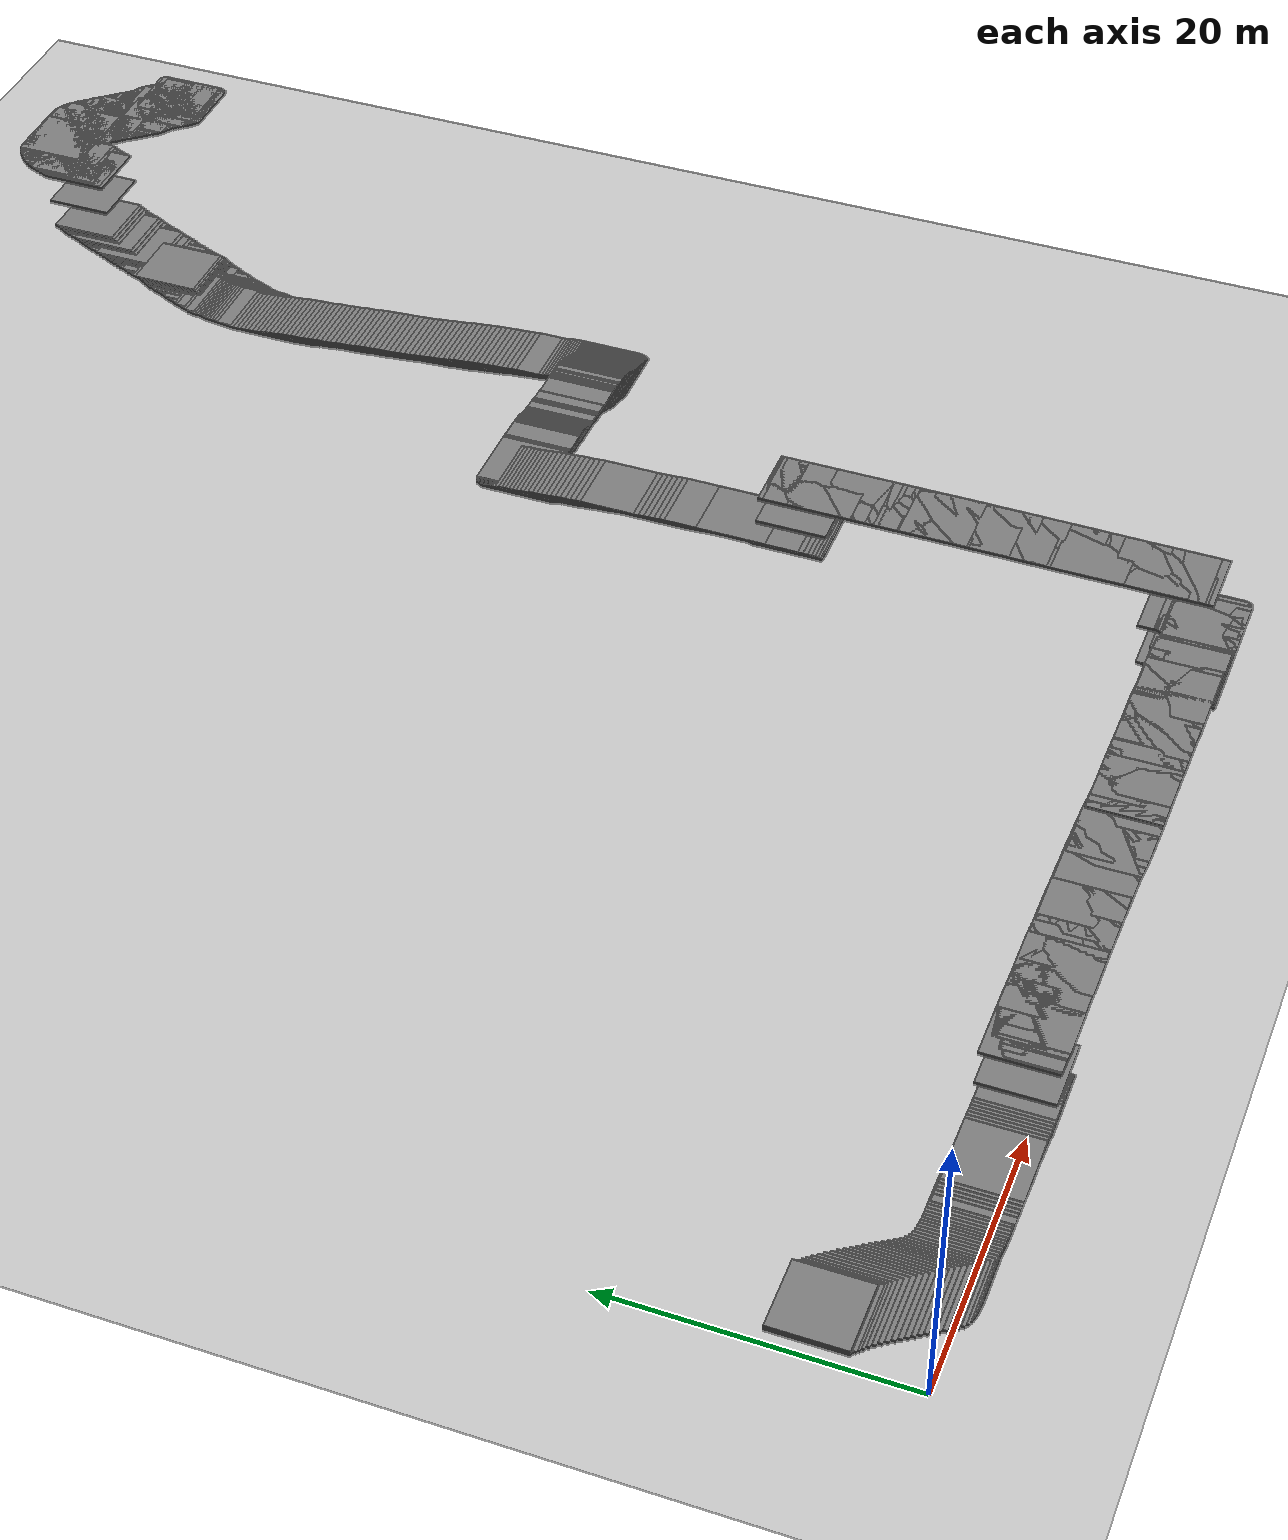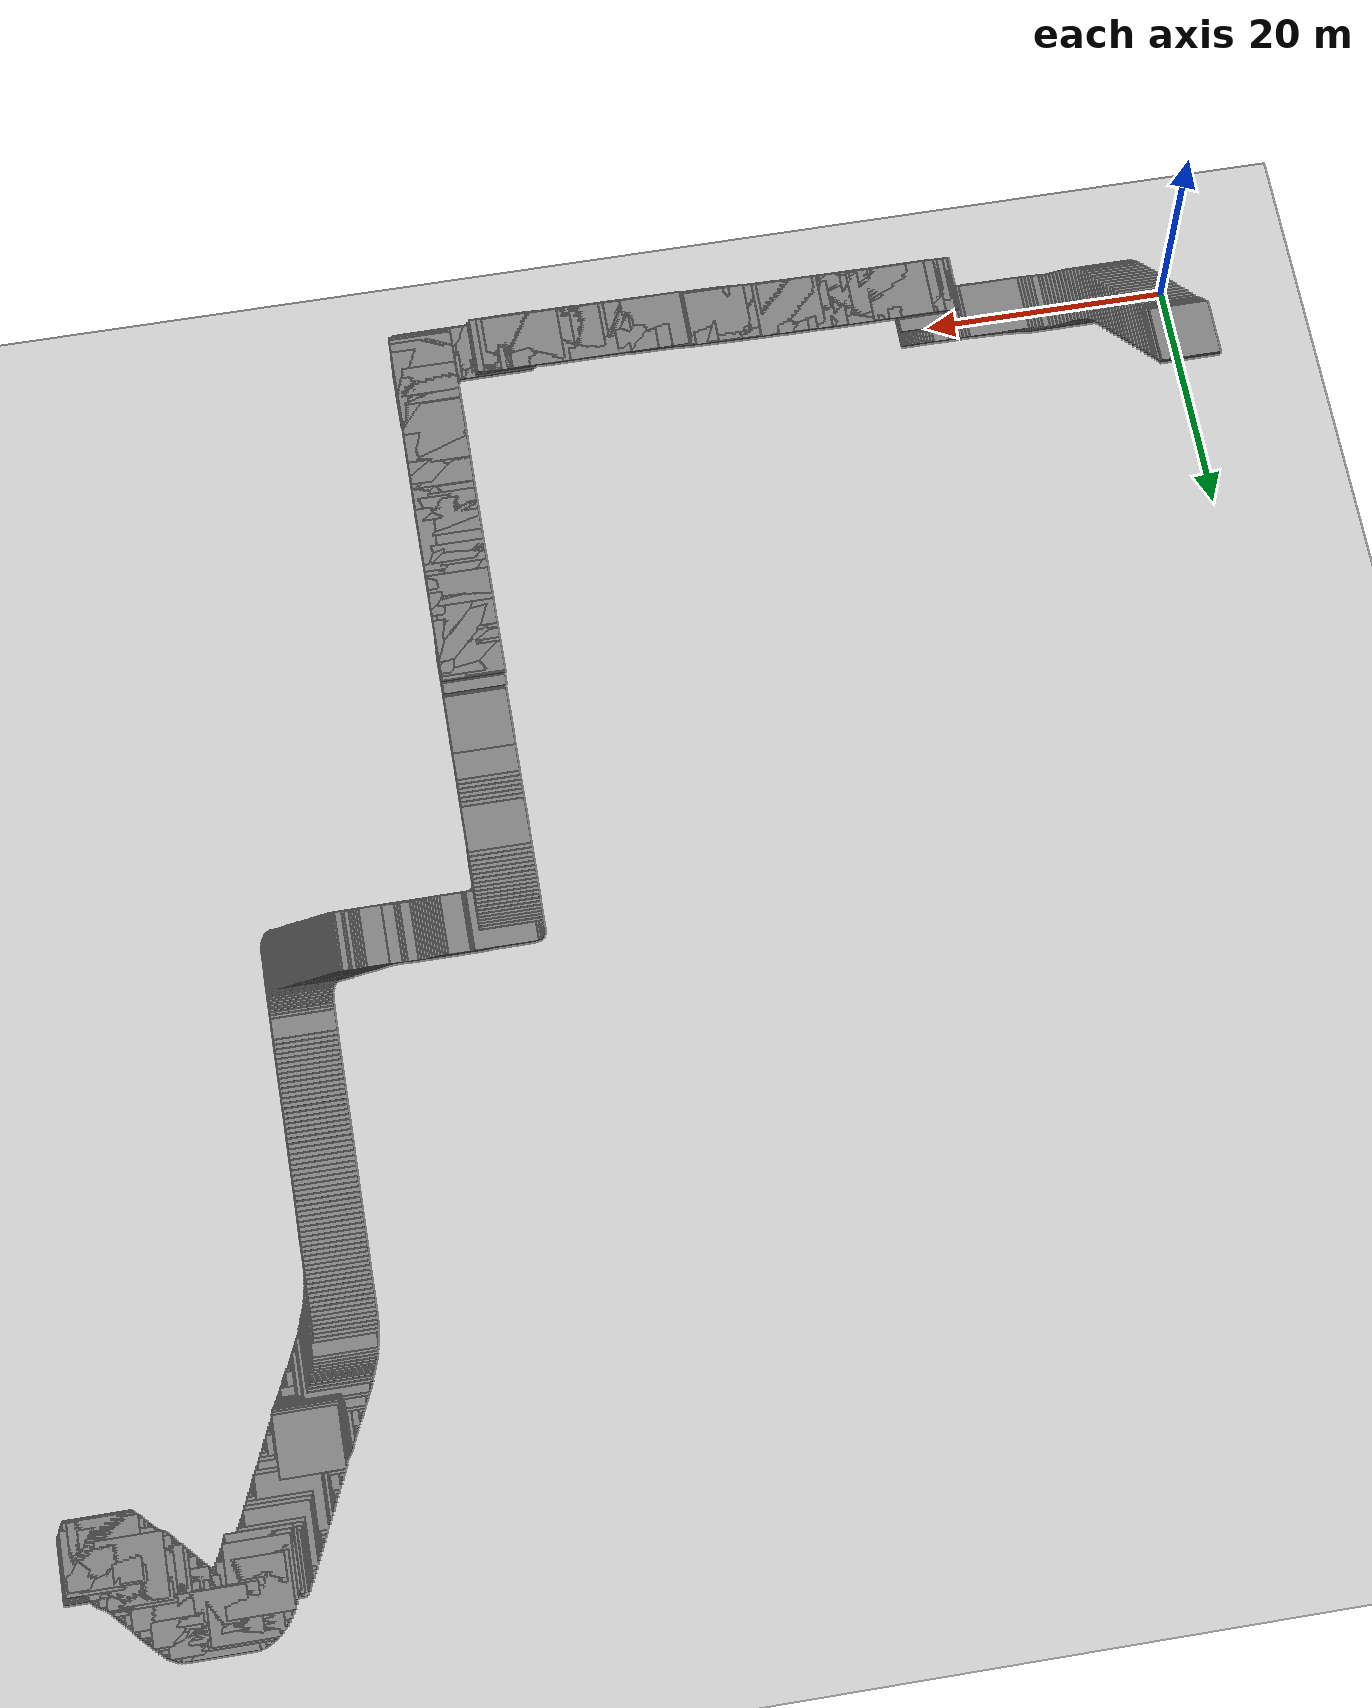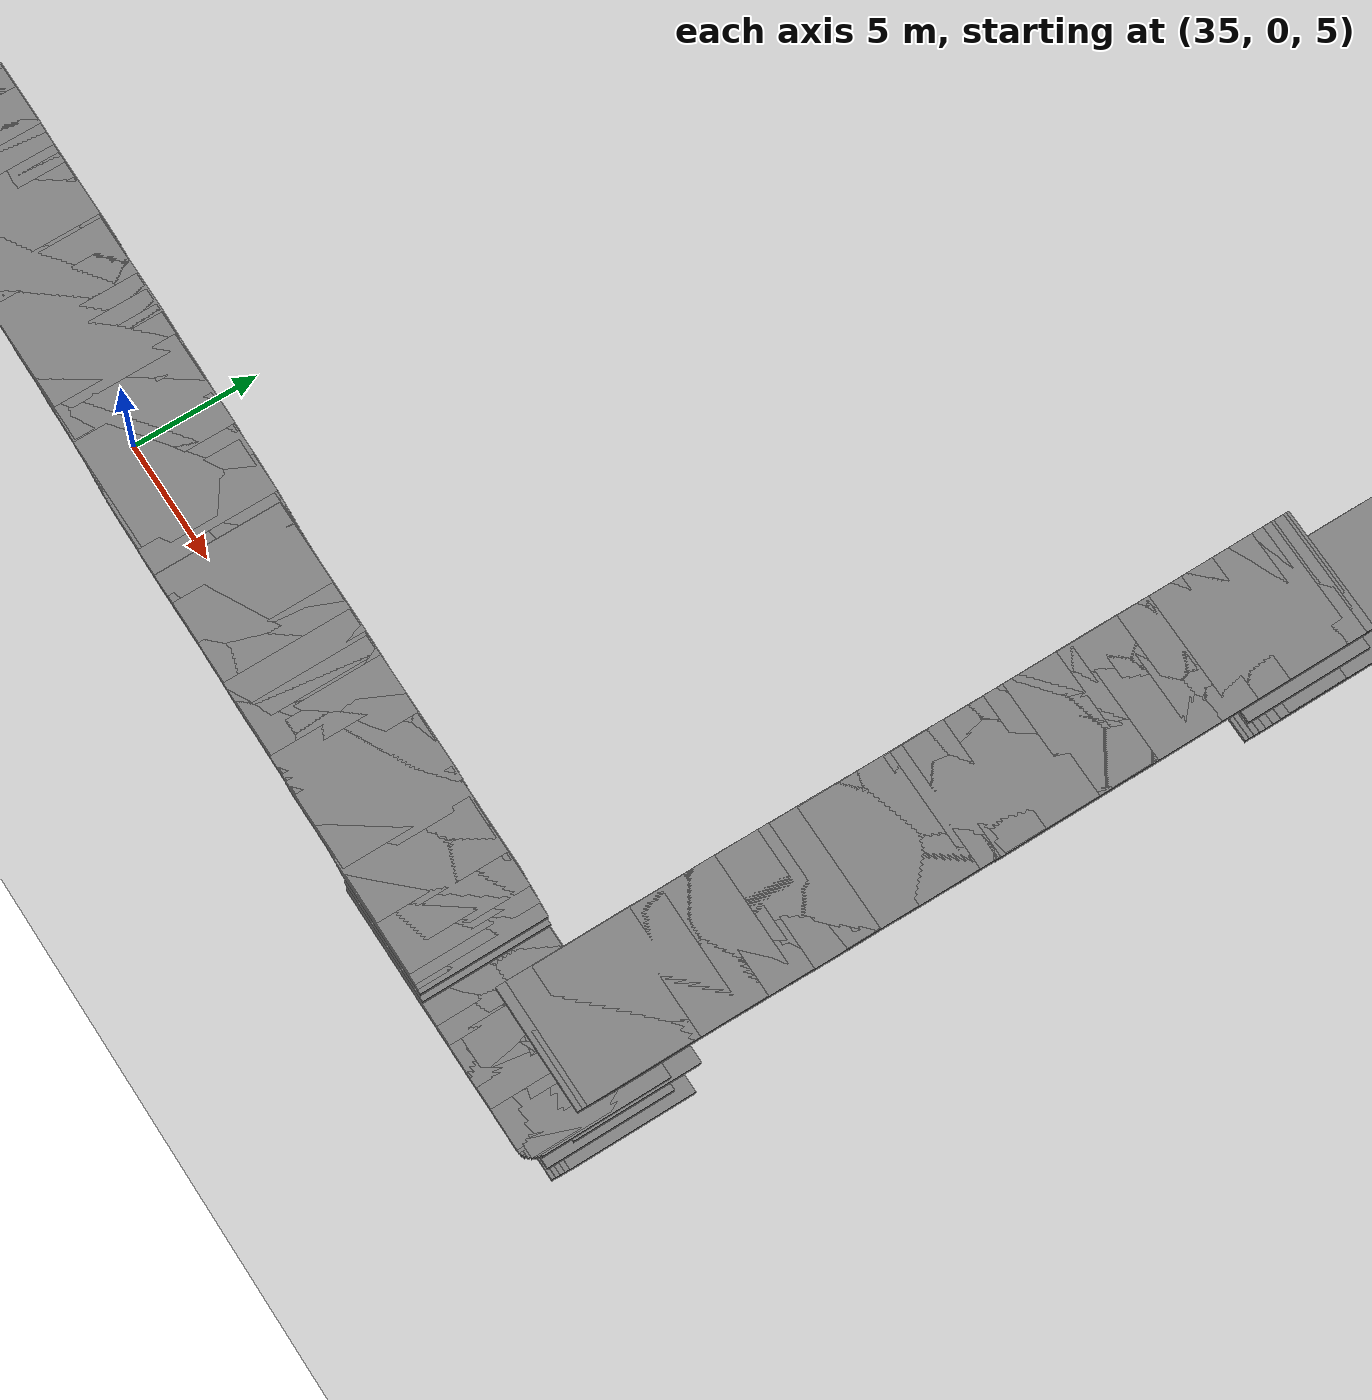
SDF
<?xml version="1.0"?>
<sdf version="1.6">
  <world name="default">
    <include>
      <uri>model://sun</uri>
    </include>
    <include>
      <uri>model://ground_plane</uri>
    </include>
    <!-- Define the path using connected boxes -->

    <model name="road_segment_1">
      <static>true</static>
      <link name="link">
        <visual name="visual">
          <geometry>
            <box>
              <size>5.0 5.0 0.2</size>
            </box>
          </geometry>
          <material>
            <ambient>0.5 0.5 0.5 1</ambient>
            <diffuse>0.5 0.5 0.5 1</diffuse>
          </material>
          <pose>99.99919580901489 94.41162049521488 4.367173193083842 0 0 0</pose>
        </visual>
        <collision name="collision">
          <geometry>
            <box>
              <size>5.0 5.0 0.2</size>
            </box>
          </geometry>
          <pose>99.99919580901489 94.41162049521488 4.367173193083842 0 0 0</pose>
        </collision>
      </link>
    </model>

    <model name="road_segment_2">
      <static>true</static>
      <link name="link">
        <visual name="visual">
          <geometry>
            <box>
              <size>5.0 5.0 0.2</size>
            </box>
          </geometry>
          <material>
            <ambient>0.5 0.5 0.5 1</ambient>
            <diffuse>0.5 0.5 0.5 1</diffuse>
          </material>
          <pose>99.98874132622485 94.27984800195918 4.367173193083842 0 0 0</pose>
        </visual>
        <collision name="collision">
          <geometry>
            <box>
              <size>5.0 5.0 0.2</size>
            </box>
          </geometry>
          <pose>99.98874132622485 94.27984800195918 4.367173193083842 0 0 0</pose>
        </collision>
      </link>
    </model>

    <model name="road_segment_3">
      <static>true</static>
      <link name="link">
        <visual name="visual">
          <geometry>
            <box>
              <size>5.0 5.0 0.2</size>
            </box>
          </geometry>
          <material>
            <ambient>0.5 0.5 0.5 1</ambient>
            <diffuse>0.5 0.5 0.5 1</diffuse>
          </material>
          <pose>99.97162354671508 94.24981613140372 4.367173193083842 0 0 0</pose>
        </visual>
        <collision name="collision">
          <geometry>
            <box>
              <size>5.0 5.0 0.2</size>
            </box>
          </geometry>
          <pose>99.97162354671508 94.24981613140372 4.367173193083842 0 0 0</pose>
        </collision>
      </link>
    </model>

    <model name="road_segment_4">
      <static>true</static>
      <link name="link">
        <visual name="visual">
          <geometry>
            <box>
              <size>5.0 5.0 0.2</size>
            </box>
          </geometry>
          <material>
            <ambient>0.5 0.5 0.5 1</ambient>
            <diffuse>0.5 0.5 0.5 1</diffuse>
          </material>
          <pose>99.95933091309962 94.24634305793734 4.367173193083842 0 0 0</pose>
        </visual>
        <collision name="collision">
          <geometry>
            <box>
              <size>5.0 5.0 0.2</size>
            </box>
          </geometry>
          <pose>99.95933091309962 94.24634305793734 4.367173193083842 0 0 0</pose>
        </collision>
      </link>
    </model>

    <model name="road_segment_5">
      <static>true</static>
      <link name="link">
        <visual name="visual">
          <geometry>
            <box>
              <size>5.0 5.0 0.2</size>
            </box>
          </geometry>
          <material>
            <ambient>0.5 0.5 0.5 1</ambient>
            <diffuse>0.5 0.5 0.5 1</diffuse>
          </material>
          <pose>99.94945085243947 94.2510419220385 4.367173193083842 0 0 0</pose>
        </visual>
        <collision name="collision">
          <geometry>
            <box>
              <size>5.0 5.0 0.2</size>
            </box>
          </geometry>
          <pose>99.94945085243947 94.2510419220385 4.367173193083842 0 0 0</pose>
        </collision>
      </link>
    </model>

    <model name="road_segment_6">
      <static>true</static>
      <link name="link">
        <visual name="visual">
          <geometry>
            <box>
              <size>5.0 5.0 0.2</size>
            </box>
          </geometry>
          <material>
            <ambient>0.5 0.5 0.5 1</ambient>
            <diffuse>0.5 0.5 0.5 1</diffuse>
          </material>
          <pose>99.94060475161965 94.25553648769811 4.367173193083842 0 0 0</pose>
        </visual>
        <collision name="collision">
          <geometry>
            <box>
              <size>5.0 5.0 0.2</size>
            </box>
          </geometry>
          <pose>99.94060475161965 94.25553648769811 4.367173193083842 0 0 0</pose>
        </collision>
      </link>
    </model>

    <model name="road_segment_7">
      <static>true</static>
      <link name="link">
        <visual name="visual">
          <geometry>
            <box>
              <size>5.0 5.0 0.2</size>
            </box>
          </geometry>
          <material>
            <ambient>0.5 0.5 0.5 1</ambient>
            <diffuse>0.5 0.5 0.5 1</diffuse>
          </material>
          <pose>99.94726804833937 94.25288060798702 4.367173193083842 0 0 0</pose>
        </visual>
        <collision name="collision">
          <geometry>
            <box>
              <size>5.0 5.0 0.2</size>
            </box>
          </geometry>
          <pose>99.94726804833937 94.25288060798702 4.367173193083842 0 0 0</pose>
        </collision>
      </link>
    </model>

    <model name="road_segment_8">
      <static>true</static>
      <link name="link">
        <visual name="visual">
          <geometry>
            <box>
              <size>5.0 5.0 0.2</size>
            </box>
          </geometry>
          <material>
            <ambient>0.5 0.5 0.5 1</ambient>
            <diffuse>0.5 0.5 0.5 1</diffuse>
          </material>
          <pose>99.95749276227419 94.24879463920325 4.367173193083842 0 0 0</pose>
        </visual>
        <collision name="collision">
          <geometry>
            <box>
              <size>5.0 5.0 0.2</size>
            </box>
          </geometry>
          <pose>99.95749276227419 94.24879463920325 4.367173193083842 0 0 0</pose>
        </collision>
      </link>
    </model>

    <model name="road_segment_9">
      <static>true</static>
      <link name="link">
        <visual name="visual">
          <geometry>
            <box>
              <size>5.0 5.0 0.2</size>
            </box>
          </geometry>
          <material>
            <ambient>0.5 0.5 0.5 1</ambient>
            <diffuse>0.5 0.5 0.5 1</diffuse>
          </material>
          <pose>99.95599926472343 94.24491296886103 4.367173193083842 0 0 0</pose>
        </visual>
        <collision name="collision">
          <geometry>
            <box>
              <size>5.0 5.0 0.2</size>
            </box>
          </geometry>
          <pose>99.95599926472343 94.24491296886103 4.367173193083842 0 0 0</pose>
        </collision>
      </link>
    </model>

    <model name="road_segment_10">
      <static>true</static>
      <link name="link">
        <visual name="visual">
          <geometry>
            <box>
              <size>5.0 5.0 0.2</size>
            </box>
          </geometry>
          <material>
            <ambient>0.5 0.5 0.5 1</ambient>
            <diffuse>0.5 0.5 0.5 1</diffuse>
          </material>
          <pose>99.94807223930815 94.24654735637526 4.367173193083842 0 0 0</pose>
        </visual>
        <collision name="collision">
          <geometry>
            <box>
              <size>5.0 5.0 0.2</size>
            </box>
          </geometry>
          <pose>99.94807223930815 94.24654735637526 4.367173193083842 0 0 0</pose>
        </collision>
      </link>
    </model>

    <model name="road_segment_11">
      <static>true</static>
      <link name="link">
        <visual name="visual">
          <geometry>
            <box>
              <size>5.0 5.0 0.2</size>
            </box>
          </geometry>
          <material>
            <ambient>0.5 0.5 0.5 1</ambient>
            <diffuse>0.5 0.5 0.5 1</diffuse>
          </material>
          <pose>99.93968567619876 94.24920323608272 4.367173193083842 0 0 0</pose>
        </visual>
        <collision name="collision">
          <geometry>
            <box>
              <size>5.0 5.0 0.2</size>
            </box>
          </geometry>
          <pose>99.93968567619876 94.24920323608272 4.367173193083842 0 0 0</pose>
        </collision>
      </link>
    </model>

    <model name="road_segment_12">
      <static>true</static>
      <link name="link">
        <visual name="visual">
          <geometry>
            <box>
              <size>5.0 5.0 0.2</size>
            </box>
          </geometry>
          <material>
            <ambient>0.5 0.5 0.5 1</ambient>
            <diffuse>0.5 0.5 0.5 1</diffuse>
          </material>
          <pose>99.93704333440456 94.24511726729895 4.367173193083842 0 0 0</pose>
        </visual>
        <collision name="collision">
          <geometry>
            <box>
              <size>5.0 5.0 0.2</size>
            </box>
          </geometry>
          <pose>99.93704333440456 94.24511726729895 4.367173193083842 0 0 0</pose>
        </collision>
      </link>
    </model>

    <model name="road_segment_13">
      <static>true</static>
      <link name="link">
        <visual name="visual">
          <geometry>
            <box>
              <size>5.0 5.0 0.2</size>
            </box>
          </geometry>
          <material>
            <ambient>0.5 0.5 0.5 1</ambient>
            <diffuse>0.5 0.5 0.5 1</diffuse>
          </material>
          <pose>99.93382657046413 94.23980550788403 4.367173193083842 0 0 0</pose>
        </visual>
        <collision name="collision">
          <geometry>
            <box>
              <size>5.0 5.0 0.2</size>
            </box>
          </geometry>
          <pose>99.93382657046413 94.23980550788403 4.367173193083842 0 0 0</pose>
        </collision>
      </link>
    </model>

    <model name="road_segment_14">
      <static>true</static>
      <link name="link">
        <visual name="visual">
          <geometry>
            <box>
              <size>5.0 5.0 0.2</size>
            </box>
          </geometry>
          <material>
            <ambient>0.5 0.5 0.5 1</ambient>
            <diffuse>0.5 0.5 0.5 1</diffuse>
          </material>
          <pose>99.9281972335684 94.23224646563752 4.367173193083842 0 0 0</pose>
        </visual>
        <collision name="collision">
          <geometry>
            <box>
              <size>5.0 5.0 0.2</size>
            </box>
          </geometry>
          <pose>99.9281972335684 94.23224646563752 4.367173193083842 0 0 0</pose>
        </collision>
      </link>
    </model>

    <model name="road_segment_15">
      <static>true</static>
      <link name="link">
        <visual name="visual">
          <geometry>
            <box>
              <size>5.0 5.0 0.2</size>
            </box>
          </geometry>
          <material>
            <ambient>0.5 0.5 0.5 1</ambient>
            <diffuse>0.5 0.5 0.5 1</diffuse>
          </material>
          <pose>99.92325720323834 94.22734330309481 4.367173193083842 0 0 0</pose>
        </visual>
        <collision name="collision">
          <geometry>
            <box>
              <size>5.0 5.0 0.2</size>
            </box>
          </geometry>
          <pose>99.92325720323834 94.22734330309481 4.367173193083842 0 0 0</pose>
        </collision>
      </link>
    </model>

    <model name="road_segment_16">
      <static>true</static>
      <link name="link">
        <visual name="visual">
          <geometry>
            <box>
              <size>5.0 5.0 0.2</size>
            </box>
          </geometry>
          <material>
            <ambient>0.5 0.5 0.5 1</ambient>
            <diffuse>0.5 0.5 0.5 1</diffuse>
          </material>
          <pose>99.91728321306792 94.22121434991735 4.367173193083842 0 0 0</pose>
        </visual>
        <collision name="collision">
          <geometry>
            <box>
              <size>5.0 5.0 0.2</size>
            </box>
          </geometry>
          <pose>99.91728321306792 94.22121434991735 4.367173193083842 0 0 0</pose>
        </collision>
      </link>
    </model>

    <model name="road_segment_17">
      <static>true</static>
      <link name="link">
        <visual name="visual">
          <geometry>
            <box>
              <size>5.0 5.0 0.2</size>
            </box>
          </geometry>
          <material>
            <ambient>0.5 0.5 0.5 1</ambient>
            <diffuse>0.5 0.5 0.5 1</diffuse>
          </material>
          <pose>99.85708377370247 94.13152733512686 4.367173193083842 0 0 0</pose>
        </visual>
        <collision name="collision">
          <geometry>
            <box>
              <size>5.0 5.0 0.2</size>
            </box>
          </geometry>
          <pose>99.85708377370247 94.13152733512686 4.367173193083842 0 0 0</pose>
        </collision>
      </link>
    </model>

    <model name="road_segment_18">
      <static>true</static>
      <link name="link">
        <visual name="visual">
          <geometry>
            <box>
              <size>5.0 5.0 0.2</size>
            </box>
          </geometry>
          <material>
            <ambient>0.5 0.5 0.5 1</ambient>
            <diffuse>0.5 0.5 0.5 1</diffuse>
          </material>
          <pose>99.77758375072713 93.99342159025576 4.367173193083842 0 0 0</pose>
        </visual>
        <collision name="collision">
          <geometry>
            <box>
              <size>5.0 5.0 0.2</size>
            </box>
          </geometry>
          <pose>99.77758375072713 93.99342159025576 4.367173193083842 0 0 0</pose>
        </collision>
      </link>
    </model>

    <model name="road_segment_19">
      <static>true</static>
      <link name="link">
        <visual name="visual">
          <geometry>
            <box>
              <size>5.0 5.0 0.2</size>
            </box>
          </geometry>
          <material>
            <ambient>0.5 0.5 0.5 1</ambient>
            <diffuse>0.5 0.5 0.5 1</diffuse>
          </material>
          <pose>99.74886264416756 93.9241644193805 4.367173193083842 0 0 0</pose>
        </visual>
        <collision name="collision">
          <geometry>
            <box>
              <size>5.0 5.0 0.2</size>
            </box>
          </geometry>
          <pose>99.74886264416756 93.9241644193805 4.367173193083842 0 0 0</pose>
        </collision>
      </link>
    </model>

    <model name="road_segment_20">
      <static>true</static>
      <link name="link">
        <visual name="visual">
          <geometry>
            <box>
              <size>5.0 5.0 0.2</size>
            </box>
          </geometry>
          <material>
            <ambient>0.5 0.5 0.5 1</ambient>
            <diffuse>0.5 0.5 0.5 1</diffuse>
          </material>
          <pose>99.74599053351812 93.91987415215881 4.367173193083842 0 0 0</pose>
        </visual>
        <collision name="collision">
          <geometry>
            <box>
              <size>5.0 5.0 0.2</size>
            </box>
          </geometry>
          <pose>99.74599053351812 93.91987415215881 4.367173193083842 0 0 0</pose>
        </collision>
      </link>
    </model>

    <model name="road_segment_21">
      <static>true</static>
      <link name="link">
        <visual name="visual">
          <geometry>
            <box>
              <size>5.0 5.0 0.2</size>
            </box>
          </geometry>
          <material>
            <ambient>0.5 0.5 0.5 1</ambient>
            <diffuse>0.5 0.5 0.5 1</diffuse>
          </material>
          <pose>99.75196452368854 93.93499223665549 4.367173193083842 0 0 0</pose>
        </visual>
        <collision name="collision">
          <geometry>
            <box>
              <size>5.0 5.0 0.2</size>
            </box>
          </geometry>
          <pose>99.75196452368854 93.93499223665549 4.367173193083842 0 0 0</pose>
        </collision>
      </link>
    </model>

    <model name="road_segment_22">
      <static>true</static>
      <link name="link">
        <visual name="visual">
          <geometry>
            <box>
              <size>5.0 5.0 0.2</size>
            </box>
          </geometry>
          <material>
            <ambient>0.5 0.5 0.5 1</ambient>
            <diffuse>0.5 0.5 0.5 1</diffuse>
          </material>
          <pose>99.75701943843806 93.95154041022849 4.367173193083842 0 0 0</pose>
        </visual>
        <collision name="collision">
          <geometry>
            <box>
              <size>5.0 5.0 0.2</size>
            </box>
          </geometry>
          <pose>99.75701943843806 93.95154041022849 4.367173193083842 0 0 0</pose>
        </collision>
      </link>
    </model>

    <model name="road_segment_23">
      <static>true</static>
      <link name="link">
        <visual name="visual">
          <geometry>
            <box>
              <size>5.0 5.0 0.2</size>
            </box>
          </geometry>
          <material>
            <ambient>0.5 0.5 0.5 1</ambient>
            <diffuse>0.5 0.5 0.5 1</diffuse>
          </material>
          <pose>99.75943201137704 93.96543270409404 4.367173193083842 0 0 0</pose>
        </visual>
        <collision name="collision">
          <geometry>
            <box>
              <size>5.0 5.0 0.2</size>
            </box>
          </geometry>
          <pose>99.75943201137704 93.96543270409404 4.367173193083842 0 0 0</pose>
        </collision>
      </link>
    </model>

    <model name="road_segment_24">
      <static>true</static>
      <link name="link">
        <visual name="visual">
          <geometry>
            <box>
              <size>5.0 5.0 0.2</size>
            </box>
          </geometry>
          <material>
            <ambient>0.5 0.5 0.5 1</ambient>
            <diffuse>0.5 0.5 0.5 1</diffuse>
          </material>
          <pose>99.76161481547715 93.96767998692202 4.367173193083842 0 0 0</pose>
        </visual>
        <collision name="collision">
          <geometry>
            <box>
              <size>5.0 5.0 0.2</size>
            </box>
          </geometry>
          <pose>99.76161481547715 93.96767998692202 4.367173193083842 0 0 0</pose>
        </collision>
      </link>
    </model>

    <model name="road_segment_25">
      <static>true</static>
      <link name="link">
        <visual name="visual">
          <geometry>
            <box>
              <size>5.0 5.0 0.2</size>
            </box>
          </geometry>
          <material>
            <ambient>0.5 0.5 0.5 1</ambient>
            <diffuse>0.5 0.5 0.5 1</diffuse>
          </material>
          <pose>99.76264877531746 93.96727139004255 4.367173193083842 0 0 0</pose>
        </visual>
        <collision name="collision">
          <geometry>
            <box>
              <size>5.0 5.0 0.2</size>
            </box>
          </geometry>
          <pose>99.76264877531746 93.96727139004255 4.367173193083842 0 0 0</pose>
        </collision>
      </link>
    </model>

    <model name="road_segment_26">
      <static>true</static>
      <link name="link">
        <visual name="visual">
          <geometry>
            <box>
              <size>5.0 5.0 0.2</size>
            </box>
          </geometry>
          <material>
            <ambient>0.5 0.5 0.5 1</ambient>
            <diffuse>0.5 0.5 0.5 1</diffuse>
          </material>
          <pose>99.76299342859213 93.97013156819156 4.529971770583577 0 0 0</pose>
        </visual>
        <collision name="collision">
          <geometry>
            <box>
              <size>5.0 5.0 0.2</size>
            </box>
          </geometry>
          <pose>99.76299342859213 93.97013156819156 4.529971770583577 0 0 0</pose>
        </collision>
      </link>
    </model>

    <model name="road_segment_27">
      <static>true</static>
      <link name="link">
        <visual name="visual">
          <geometry>
            <box>
              <size>5.0 5.0 0.2</size>
            </box>
          </geometry>
          <material>
            <ambient>0.5 0.5 0.5 1</ambient>
            <diffuse>0.5 0.5 0.5 1</diffuse>
          </material>
          <pose>99.76471669498179 93.97340034321638 4.692770348083311 0 0 0</pose>
        </visual>
        <collision name="collision">
          <geometry>
            <box>
              <size>5.0 5.0 0.2</size>
            </box>
          </geometry>
          <pose>99.76471669498179 93.97340034321638 4.692770348083311 0 0 0</pose>
        </collision>
      </link>
    </model>

    <model name="road_segment_28">
      <static>true</static>
      <link name="link">
        <visual name="visual">
          <geometry>
            <box>
              <size>5.0 5.0 0.2</size>
            </box>
          </geometry>
          <material>
            <ambient>0.5 0.5 0.5 1</ambient>
            <diffuse>0.5 0.5 0.5 1</diffuse>
          </material>
          <pose>99.76655484580722 93.97258314946109 4.692770348083311 0 0 0</pose>
        </visual>
        <collision name="collision">
          <geometry>
            <box>
              <size>5.0 5.0 0.2</size>
            </box>
          </geometry>
          <pose>99.76655484580722 93.97258314946109 4.692770348083311 0 0 0</pose>
        </collision>
      </link>
    </model>

    <model name="road_segment_29">
      <static>true</static>
      <link name="link">
        <visual name="visual">
          <geometry>
            <box>
              <size>5.0 5.0 0.2</size>
            </box>
          </geometry>
          <material>
            <ambient>0.5 0.5 0.5 1</ambient>
            <diffuse>0.5 0.5 0.5 1</diffuse>
          </material>
          <pose>99.7668994990982 93.97033586663309 4.692770348083311 0 0 0</pose>
        </visual>
        <collision name="collision">
          <geometry>
            <box>
              <size>5.0 5.0 0.2</size>
            </box>
          </geometry>
          <pose>99.7668994990982 93.97033586663309 4.692770348083311 0 0 0</pose>
        </collision>
      </link>
    </model>

    <model name="road_segment_30">
      <static>true</static>
      <link name="link">
        <visual name="visual">
          <geometry>
            <box>
              <size>5.0 5.0 0.2</size>
            </box>
          </geometry>
          <material>
            <ambient>0.5 0.5 0.5 1</ambient>
            <diffuse>0.5 0.5 0.5 1</diffuse>
          </material>
          <pose>99.76724415237288 93.97054016507101 4.692770348083311 0 0 0</pose>
        </visual>
        <collision name="collision">
          <geometry>
            <box>
              <size>5.0 5.0 0.2</size>
            </box>
          </geometry>
          <pose>99.76724415237288 93.97054016507101 4.692770348083311 0 0 0</pose>
        </collision>
      </link>
    </model>

    <model name="road_segment_31">
      <static>true</static>
      <link name="link">
        <visual name="visual">
          <geometry>
            <box>
              <size>5.0 5.0 0.2</size>
            </box>
          </geometry>
          <material>
            <ambient>0.5 0.5 0.5 1</ambient>
            <diffuse>0.5 0.5 0.5 1</diffuse>
          </material>
          <pose>99.72324341711263 93.8749284955446 4.692770348083311 0 0 0</pose>
        </visual>
        <collision name="collision">
          <geometry>
            <box>
              <size>5.0 5.0 0.2</size>
            </box>
          </geometry>
          <pose>99.72324341711263 93.8749284955446 4.692770348083311 0 0 0</pose>
        </collision>
      </link>
    </model>

    <model name="road_segment_32">
      <static>true</static>
      <link name="link">
        <visual name="visual">
          <geometry>
            <box>
              <size>5.0 5.0 0.2</size>
            </box>
          </geometry>
          <material>
            <ambient>0.5 0.5 0.5 1</ambient>
            <diffuse>0.5 0.5 0.5 1</diffuse>
          </material>
          <pose>99.65741464086776 93.72354335212898 4.692770348083311 0 0 0</pose>
        </visual>
        <collision name="collision">
          <geometry>
            <box>
              <size>5.0 5.0 0.2</size>
            </box>
          </geometry>
          <pose>99.65741464086776 93.72354335212898 4.692770348083311 0 0 0</pose>
        </collision>
      </link>
    </model>

    <model name="road_segment_33">
      <static>true</static>
      <link name="link">
        <visual name="visual">
          <geometry>
            <box>
              <size>5.0 5.0 0.2</size>
            </box>
          </geometry>
          <material>
            <ambient>0.5 0.5 0.5 1</ambient>
            <diffuse>0.5 0.5 0.5 1</diffuse>
          </material>
          <pose>99.62294931297669 93.64488845305141 4.692770348083311 0 0 0</pose>
        </visual>
        <collision name="collision">
          <geometry>
            <box>
              <size>5.0 5.0 0.2</size>
            </box>
          </geometry>
          <pose>99.62294931297669 93.64488845305141 4.692770348083311 0 0 0</pose>
        </collision>
      </link>
    </model>

    <model name="road_segment_34">
      <static>true</static>
      <link name="link">
        <visual name="visual">
          <geometry>
            <box>
              <size>5.0 5.0 0.2</size>
            </box>
          </geometry>
          <material>
            <ambient>0.5 0.5 0.5 1</ambient>
            <diffuse>0.5 0.5 0.5 1</diffuse>
          </material>
          <pose>99.59939800558607 93.59728691672612 4.692770348083311 0 0 0</pose>
        </visual>
        <collision name="collision">
          <geometry>
            <box>
              <size>5.0 5.0 0.2</size>
            </box>
          </geometry>
          <pose>99.59939800558607 93.59728691672612 4.692770348083311 0 0 0</pose>
        </collision>
      </link>
    </model>

    <model name="road_segment_35">
      <static>true</static>
      <link name="link">
        <visual name="visual">
          <geometry>
            <box>
              <size>5.0 5.0 0.2</size>
            </box>
          </geometry>
          <material>
            <ambient>0.5 0.5 0.5 1</ambient>
            <diffuse>0.5 0.5 0.5 1</diffuse>
          </material>
          <pose>99.57297458754604 93.54049195064007 4.692770348083311 0 0 0</pose>
        </visual>
        <collision name="collision">
          <geometry>
            <box>
              <size>5.0 5.0 0.2</size>
            </box>
          </geometry>
          <pose>99.57297458754604 93.54049195064007 4.692770348083311 0 0 0</pose>
        </collision>
      </link>
    </model>

    <model name="road_segment_36">
      <static>true</static>
      <link name="link">
        <visual name="visual">
          <geometry>
            <box>
              <size>5.0 5.0 0.2</size>
            </box>
          </geometry>
          <material>
            <ambient>0.5 0.5 0.5 1</ambient>
            <diffuse>0.5 0.5 0.5 1</diffuse>
          </material>
          <pose>99.52748035475136 93.45570809838866 4.692770348083311 0 0 0</pose>
        </visual>
        <collision name="collision">
          <geometry>
            <box>
              <size>5.0 5.0 0.2</size>
            </box>
          </geometry>
          <pose>99.52748035475136 93.45570809838866 4.692770348083311 0 0 0</pose>
        </collision>
      </link>
    </model>

    <model name="road_segment_37">
      <static>true</static>
      <link name="link">
        <visual name="visual">
          <geometry>
            <box>
              <size>5.0 5.0 0.2</size>
            </box>
          </geometry>
          <material>
            <ambient>0.5 0.5 0.5 1</ambient>
            <diffuse>0.5 0.5 0.5 1</diffuse>
          </material>
          <pose>99.47417398096084 93.36867696330562 4.692770348083311 0 0 0</pose>
        </visual>
        <collision name="collision">
          <geometry>
            <box>
              <size>5.0 5.0 0.2</size>
            </box>
          </geometry>
          <pose>99.47417398096084 93.36867696330562 4.692770348083311 0 0 0</pose>
        </collision>
      </link>
    </model>

    <model name="road_segment_38">
      <static>true</static>
      <link name="link">
        <visual name="visual">
          <geometry>
            <box>
              <size>5.0 5.0 0.2</size>
            </box>
          </geometry>
          <material>
            <ambient>0.5 0.5 0.5 1</ambient>
            <diffuse>0.5 0.5 0.5 1</diffuse>
          </material>
          <pose>99.42833509487517 93.30146277682042 4.692770348083311 0 0 0</pose>
        </visual>
        <collision name="collision">
          <geometry>
            <box>
              <size>5.0 5.0 0.2</size>
            </box>
          </geometry>
          <pose>99.42833509487517 93.30146277682042 4.692770348083311 0 0 0</pose>
        </collision>
      </link>
    </model>

    <model name="road_segment_39">
      <static>true</static>
      <link name="link">
        <visual name="visual">
          <geometry>
            <box>
              <size>5.0 5.0 0.2</size>
            </box>
          </geometry>
          <material>
            <ambient>0.5 0.5 0.5 1</ambient>
            <diffuse>0.5 0.5 0.5 1</diffuse>
          </material>
          <pose>99.38421947519548 93.24977527171137 4.692770348083311 0 0 0</pose>
        </visual>
        <collision name="collision">
          <geometry>
            <box>
              <size>5.0 5.0 0.2</size>
            </box>
          </geometry>
          <pose>99.38421947519548 93.24977527171137 4.692770348083311 0 0 0</pose>
        </collision>
      </link>
    </model>

    <model name="road_segment_40">
      <static>true</static>
      <link name="link">
        <visual name="visual">
          <geometry>
            <box>
              <size>5.0 5.0 0.2</size>
            </box>
          </geometry>
          <material>
            <ambient>0.5 0.5 0.5 1</ambient>
            <diffuse>0.5 0.5 0.5 1</diffuse>
          </material>
          <pose>99.33401498092593 93.25447413581252 4.692770348083311 0 0 0</pose>
        </visual>
        <collision name="collision">
          <geometry>
            <box>
              <size>5.0 5.0 0.2</size>
            </box>
          </geometry>
          <pose>99.33401498092593 93.25447413581252 4.692770348083311 0 0 0</pose>
        </collision>
      </link>
    </model>

    <model name="road_segment_41">
      <static>true</static>
      <link name="link">
        <visual name="visual">
          <geometry>
            <box>
              <size>5.0 5.0 0.2</size>
            </box>
          </geometry>
          <material>
            <ambient>0.5 0.5 0.5 1</ambient>
            <diffuse>0.5 0.5 0.5 1</diffuse>
          </material>
          <pose>99.26232709893011 93.32230121761509 4.692770348083311 0 0 0</pose>
        </visual>
        <collision name="collision">
          <geometry>
            <box>
              <size>5.0 5.0 0.2</size>
            </box>
          </geometry>
          <pose>99.26232709893011 93.32230121761509 4.692770348083311 0 0 0</pose>
        </collision>
      </link>
    </model>

    <model name="road_segment_42">
      <static>true</static>
      <link name="link">
        <visual name="visual">
          <geometry>
            <box>
              <size>5.0 5.0 0.2</size>
            </box>
          </geometry>
          <material>
            <ambient>0.5 0.5 0.5 1</ambient>
            <diffuse>0.5 0.5 0.5 1</diffuse>
          </material>
          <pose>99.17524470381417 93.42996649505491 4.692770348083311 0 0 0</pose>
        </visual>
        <collision name="collision">
          <geometry>
            <box>
              <size>5.0 5.0 0.2</size>
            </box>
          </geometry>
          <pose>99.17524470381417 93.42996649505491 4.692770348083311 0 0 0</pose>
        </collision>
      </link>
    </model>

    <model name="road_segment_43">
      <static>true</static>
      <link name="link">
        <visual name="visual">
          <geometry>
            <box>
              <size>5.0 5.0 0.2</size>
            </box>
          </geometry>
          <material>
            <ambient>0.5 0.5 0.5 1</ambient>
            <diffuse>0.5 0.5 0.5 1</diffuse>
          </material>
          <pose>99.07242314230346 93.54008335376062 4.692770348083311 0 0 0</pose>
        </visual>
        <collision name="collision">
          <geometry>
            <box>
              <size>5.0 5.0 0.2</size>
            </box>
          </geometry>
          <pose>99.07242314230346 93.54008335376062 4.692770348083311 0 0 0</pose>
        </collision>
      </link>
    </model>

    <model name="road_segment_44">
      <static>true</static>
      <link name="link">
        <visual name="visual">
          <geometry>
            <box>
              <size>5.0 5.0 0.2</size>
            </box>
          </geometry>
          <material>
            <ambient>0.5 0.5 0.5 1</ambient>
            <diffuse>0.5 0.5 0.5 1</diffuse>
          </material>
          <pose>98.95328799226809 93.61730816376188 4.692770348083311 0 0 0</pose>
        </visual>
        <collision name="collision">
          <geometry>
            <box>
              <size>5.0 5.0 0.2</size>
            </box>
          </geometry>
          <pose>98.95328799226809 93.61730816376188 4.692770348083311 0 0 0</pose>
        </collision>
      </link>
    </model>

    <model name="road_segment_45">
      <static>true</static>
      <link name="link">
        <visual name="visual">
          <geometry>
            <box>
              <size>5.0 5.0 0.2</size>
            </box>
          </geometry>
          <material>
            <ambient>0.5 0.5 0.5 1</ambient>
            <diffuse>0.5 0.5 0.5 1</diffuse>
          </material>
          <pose>98.83242957584305 93.70270491133068 4.692770348083311 0 0 0</pose>
        </visual>
        <collision name="collision">
          <geometry>
            <box>
              <size>5.0 5.0 0.2</size>
            </box>
          </geometry>
          <pose>98.83242957584305 93.70270491133068 4.692770348083311 0 0 0</pose>
        </collision>
      </link>
    </model>

    <model name="road_segment_46">
      <static>true</static>
      <link name="link">
        <visual name="visual">
          <geometry>
            <box>
              <size>5.0 5.0 0.2</size>
            </box>
          </geometry>
          <material>
            <ambient>0.5 0.5 0.5 1</ambient>
            <diffuse>0.5 0.5 0.5 1</diffuse>
          </material>
          <pose>98.70835439547758 93.82262809511818 4.692770348083311 0 0 0</pose>
        </visual>
        <collision name="collision">
          <geometry>
            <box>
              <size>5.0 5.0 0.2</size>
            </box>
          </geometry>
          <pose>98.70835439547758 93.82262809511818 4.692770348083311 0 0 0</pose>
        </collision>
      </link>
    </model>

    <model name="road_segment_47">
      <static>true</static>
      <link name="link">
        <visual name="visual">
          <geometry>
            <box>
              <size>5.0 5.0 0.2</size>
            </box>
          </geometry>
          <material>
            <ambient>0.5 0.5 0.5 1</ambient>
            <diffuse>0.5 0.5 0.5 1</diffuse>
          </material>
          <pose>98.57796057166706 93.96134673531026 4.692770348083311 0 0 0</pose>
        </visual>
        <collision name="collision">
          <geometry>
            <box>
              <size>5.0 5.0 0.2</size>
            </box>
          </geometry>
          <pose>98.57796057166706 93.96134673531026 4.692770348083311 0 0 0</pose>
        </collision>
      </link>
    </model>

    <model name="road_segment_48">
      <static>true</static>
      <link name="link">
        <visual name="visual">
          <geometry>
            <box>
              <size>5.0 5.0 0.2</size>
            </box>
          </geometry>
          <material>
            <ambient>0.5 0.5 0.5 1</ambient>
            <diffuse>0.5 0.5 0.5 1</diffuse>
          </material>
          <pose>98.44297137080113 94.11252758028795 4.692770348083311 0 0 0</pose>
        </visual>
        <collision name="collision">
          <geometry>
            <box>
              <size>5.0 5.0 0.2</size>
            </box>
          </geometry>
          <pose>98.44297137080113 94.11252758028795 4.692770348083311 0 0 0</pose>
        </collision>
      </link>
    </model>

    <model name="road_segment_49">
      <static>true</static>
      <link name="link">
        <visual name="visual">
          <geometry>
            <box>
              <size>5.0 5.0 0.2</size>
            </box>
          </geometry>
          <material>
            <ambient>0.5 0.5 0.5 1</ambient>
            <diffuse>0.5 0.5 0.5 1</diffuse>
          </material>
          <pose>98.30465052157534 94.2684072893668 4.692770348083311 0 0 0</pose>
        </visual>
        <collision name="collision">
          <geometry>
            <box>
              <size>5.0 5.0 0.2</size>
            </box>
          </geometry>
          <pose>98.30465052157534 94.2684072893668 4.692770348083311 0 0 0</pose>
        </collision>
      </link>
    </model>

    <model name="road_segment_50">
      <static>true</static>
      <link name="link">
        <visual name="visual">
          <geometry>
            <box>
              <size>5.0 5.0 0.2</size>
            </box>
          </geometry>
          <material>
            <ambient>0.5 0.5 0.5 1</ambient>
            <diffuse>0.5 0.5 0.5 1</diffuse>
          </material>
          <pose>98.16518082807345 94.42489989376304 4.692770348083311 0 0 0</pose>
        </visual>
        <collision name="collision">
          <geometry>
            <box>
              <size>5.0 5.0 0.2</size>
            </box>
          </geometry>
          <pose>98.16518082807345 94.42489989376304 4.692770348083311 0 0 0</pose>
        </collision>
      </link>
    </model>

    <model name="road_segment_51">
      <static>true</static>
      <link name="link">
        <visual name="visual">
          <geometry>
            <box>
              <size>5.0 5.0 0.2</size>
            </box>
          </geometry>
          <material>
            <ambient>0.5 0.5 0.5 1</ambient>
            <diffuse>0.5 0.5 0.5 1</diffuse>
          </material>
          <pose>98.02789393867164 94.57975811064503 4.692770348083311 0 0 0</pose>
        </visual>
        <collision name="collision">
          <geometry>
            <box>
              <size>5.0 5.0 0.2</size>
            </box>
          </geometry>
          <pose>98.02789393867164 94.57975811064503 4.692770348083311 0 0 0</pose>
        </collision>
      </link>
    </model>

    <model name="road_segment_52">
      <static>true</static>
      <link name="link">
        <visual name="visual">
          <geometry>
            <box>
              <size>5.0 5.0 0.2</size>
            </box>
          </geometry>
          <material>
            <ambient>0.5 0.5 0.5 1</ambient>
            <diffuse>0.5 0.5 0.5 1</diffuse>
          </material>
          <pose>97.89267496896682 94.72807877747371 4.692770348083311 0 0 0</pose>
        </visual>
        <collision name="collision">
          <geometry>
            <box>
              <size>5.0 5.0 0.2</size>
            </box>
          </geometry>
          <pose>97.89267496896682 94.72807877747371 4.692770348083311 0 0 0</pose>
        </collision>
      </link>
    </model>

    <model name="road_segment_53">
      <static>true</static>
      <link name="link">
        <visual name="visual">
          <geometry>
            <box>
              <size>5.0 5.0 0.2</size>
            </box>
          </geometry>
          <material>
            <ambient>0.5 0.5 0.5 1</ambient>
            <diffuse>0.5 0.5 0.5 1</diffuse>
          </material>
          <pose>97.76205137630109 94.86271144888204 4.692770348083311 0 0 0</pose>
        </visual>
        <collision name="collision">
          <geometry>
            <box>
              <size>5.0 5.0 0.2</size>
            </box>
          </geometry>
          <pose>97.76205137630109 94.86271144888204 4.692770348083311 0 0 0</pose>
        </collision>
      </link>
    </model>

    <model name="road_segment_54">
      <static>true</static>
      <link name="link">
        <visual name="visual">
          <geometry>
            <box>
              <size>5.0 5.0 0.2</size>
            </box>
          </geometry>
          <material>
            <ambient>0.5 0.5 0.5 1</ambient>
            <diffuse>0.5 0.5 0.5 1</diffuse>
          </material>
          <pose>97.63188732132944 94.96833374192815 4.692770348083311 0 0 0</pose>
        </visual>
        <collision name="collision">
          <geometry>
            <box>
              <size>5.0 5.0 0.2</size>
            </box>
          </geometry>
          <pose>97.63188732132944 94.96833374192815 4.692770348083311 0 0 0</pose>
        </collision>
      </link>
    </model>

    <model name="road_segment_55">
      <static>true</static>
      <link name="link">
        <visual name="visual">
          <geometry>
            <box>
              <size>5.0 5.0 0.2</size>
            </box>
          </geometry>
          <material>
            <ambient>0.5 0.5 0.5 1</ambient>
            <diffuse>0.5 0.5 0.5 1</diffuse>
          </material>
          <pose>97.49460043194398 95.04433276129464 4.692770348083311 0 0 0</pose>
        </visual>
        <collision name="collision">
          <geometry>
            <box>
              <size>5.0 5.0 0.2</size>
            </box>
          </geometry>
          <pose>97.49460043194398 95.04433276129464 4.692770348083311 0 0 0</pose>
        </collision>
      </link>
    </model>

    <model name="road_segment_56">
      <static>true</static>
      <link name="link">
        <visual name="visual">
          <geometry>
            <box>
              <size>5.0 5.0 0.2</size>
            </box>
          </geometry>
          <material>
            <ambient>0.5 0.5 0.5 1</ambient>
            <diffuse>0.5 0.5 0.5 1</diffuse>
          </material>
          <pose>97.35099489911343 95.11604151343946 4.692770348083311 0 0 0</pose>
        </visual>
        <collision name="collision">
          <geometry>
            <box>
              <size>5.0 5.0 0.2</size>
            </box>
          </geometry>
          <pose>97.35099489911343 95.11604151343946 4.692770348083311 0 0 0</pose>
        </collision>
      </link>
    </model>

    <model name="road_segment_57">
      <static>true</static>
      <link name="link">
        <visual name="visual">
          <geometry>
            <box>
              <size>5.0 5.0 0.2</size>
            </box>
          </geometry>
          <material>
            <ambient>0.5 0.5 0.5 1</ambient>
            <diffuse>0.5 0.5 0.5 1</diffuse>
          </material>
          <pose>97.20509167776336 95.20082536569087 4.692770348083311 0 0 0</pose>
        </visual>
        <collision name="collision">
          <geometry>
            <box>
              <size>5.0 5.0 0.2</size>
            </box>
          </geometry>
          <pose>97.20509167776336 95.20082536569087 4.692770348083311 0 0 0</pose>
        </collision>
      </link>
    </model>

    <model name="road_segment_58">
      <static>true</static>
      <link name="link">
        <visual name="visual">
          <geometry>
            <box>
              <size>5.0 5.0 0.2</size>
            </box>
          </geometry>
          <material>
            <ambient>0.5 0.5 0.5 1</ambient>
            <diffuse>0.5 0.5 0.5 1</diffuse>
          </material>
          <pose>97.05620146132807 95.29255536487506 4.692770348083311 0 0 0</pose>
        </visual>
        <collision name="collision">
          <geometry>
            <box>
              <size>5.0 5.0 0.2</size>
            </box>
          </geometry>
          <pose>97.05620146132807 95.29255536487506 4.692770348083311 0 0 0</pose>
        </collision>
      </link>
    </model>

    <model name="road_segment_59">
      <static>true</static>
      <link name="link">
        <visual name="visual">
          <geometry>
            <box>
              <size>5.0 5.0 0.2</size>
            </box>
          </geometry>
          <material>
            <ambient>0.5 0.5 0.5 1</ambient>
            <diffuse>0.5 0.5 0.5 1</diffuse>
          </material>
          <pose>96.908574973572 95.40022064231124 4.692770348083311 0 0 0</pose>
        </visual>
        <collision name="collision">
          <geometry>
            <box>
              <size>5.0 5.0 0.2</size>
            </box>
          </geometry>
          <pose>96.908574973572 95.40022064231124 4.692770348083311 0 0 0</pose>
        </collision>
      </link>
    </model>

    <model name="road_segment_60">
      <static>true</static>
      <link name="link">
        <visual name="visual">
          <geometry>
            <box>
              <size>5.0 5.0 0.2</size>
            </box>
          </geometry>
          <material>
            <ambient>0.5 0.5 0.5 1</ambient>
            <diffuse>0.5 0.5 0.5 1</diffuse>
          </material>
          <pose>96.76646293827591 95.53975647625865 4.692770348083311 0 0 0</pose>
        </visual>
        <collision name="collision">
          <geometry>
            <box>
              <size>5.0 5.0 0.2</size>
            </box>
          </geometry>
          <pose>96.76646293827591 95.53975647625865 4.692770348083311 0 0 0</pose>
        </collision>
      </link>
    </model>

    <model name="road_segment_61">
      <static>true</static>
      <link name="link">
        <visual name="visual">
          <geometry>
            <box>
              <size>5.0 5.0 0.2</size>
            </box>
          </geometry>
          <material>
            <ambient>0.5 0.5 0.5 1</ambient>
            <diffuse>0.5 0.5 0.5 1</diffuse>
          </material>
          <pose>96.62481044069024 95.70339952602555 4.692770348083311 0 0 0</pose>
        </visual>
        <collision name="collision">
          <geometry>
            <box>
              <size>5.0 5.0 0.2</size>
            </box>
          </geometry>
          <pose>96.62481044069024 95.70339952602555 4.692770348083311 0 0 0</pose>
        </collision>
      </link>
    </model>

    <model name="road_segment_62">
      <static>true</static>
      <link name="link">
        <visual name="visual">
          <geometry>
            <box>
              <size>5.0 5.0 0.2</size>
            </box>
          </geometry>
          <material>
            <ambient>0.5 0.5 0.5 1</ambient>
            <diffuse>0.5 0.5 0.5 1</diffuse>
          </material>
          <pose>96.48074537014926 95.87255863364894 4.692770348083311 0 0 0</pose>
        </visual>
        <collision name="collision">
          <geometry>
            <box>
              <size>5.0 5.0 0.2</size>
            </box>
          </geometry>
          <pose>96.48074537014926 95.87255863364894 4.692770348083311 0 0 0</pose>
        </collision>
      </link>
    </model>

    <model name="road_segment_63">
      <static>true</static>
      <link name="link">
        <visual name="visual">
          <geometry>
            <box>
              <size>5.0 5.0 0.2</size>
            </box>
          </geometry>
          <material>
            <ambient>0.5 0.5 0.5 1</ambient>
            <diffuse>0.5 0.5 0.5 1</diffuse>
          </material>
          <pose>96.33564633976796 96.04294353191071 4.692770348083311 0 0 0</pose>
        </visual>
        <collision name="collision">
          <geometry>
            <box>
              <size>5.0 5.0 0.2</size>
            </box>
          </geometry>
          <pose>96.33564633976796 96.04294353191071 4.692770348083311 0 0 0</pose>
        </collision>
      </link>
    </model>

    <model name="road_segment_64">
      <static>true</static>
      <link name="link">
        <visual name="visual">
          <geometry>
            <box>
              <size>5.0 5.0 0.2</size>
            </box>
          </geometry>
          <material>
            <ambient>0.5 0.5 0.5 1</ambient>
            <diffuse>0.5 0.5 0.5 1</diffuse>
          </material>
          <pose>96.18813473644767 96.20781237231239 4.692770348083311 0 0 0</pose>
        </visual>
        <collision name="collision">
          <geometry>
            <box>
              <size>5.0 5.0 0.2</size>
            </box>
          </geometry>
          <pose>96.18813473644767 96.20781237231239 4.692770348083311 0 0 0</pose>
        </collision>
      </link>
    </model>

    <model name="road_segment_65">
      <static>true</static>
      <link name="link">
        <visual name="visual">
          <geometry>
            <box>
              <size>5.0 5.0 0.2</size>
            </box>
          </geometry>
          <material>
            <ambient>0.5 0.5 0.5 1</ambient>
            <diffuse>0.5 0.5 0.5 1</diffuse>
          </material>
          <pose>96.03706171591229 96.36450927514653 4.692770348083311 0 0 0</pose>
        </visual>
        <collision name="collision">
          <geometry>
            <box>
              <size>5.0 5.0 0.2</size>
            </box>
          </geometry>
          <pose>96.03706171591229 96.36450927514653 4.692770348083311 0 0 0</pose>
        </collision>
      </link>
    </model>

    <model name="road_segment_66">
      <static>true</static>
      <link name="link">
        <visual name="visual">
          <geometry>
            <box>
              <size>5.0 5.0 0.2</size>
            </box>
          </geometry>
          <material>
            <ambient>0.5 0.5 0.5 1</ambient>
            <diffuse>0.5 0.5 0.5 1</diffuse>
          </material>
          <pose>95.88909057488155 96.52304486393284 4.692770348083311 0 0 0</pose>
        </visual>
        <collision name="collision">
          <geometry>
            <box>
              <size>5.0 5.0 0.2</size>
            </box>
          </geometry>
          <pose>95.88909057488155 96.52304486393284 4.692770348083311 0 0 0</pose>
        </collision>
      </link>
    </model>

    <model name="road_segment_67">
      <static>true</static>
      <link name="link">
        <visual name="visual">
          <geometry>
            <box>
              <size>5.0 5.0 0.2</size>
            </box>
          </geometry>
          <material>
            <ambient>0.5 0.5 0.5 1</ambient>
            <diffuse>0.5 0.5 0.5 1</diffuse>
          </material>
          <pose>95.7444510822107 96.68730080901713 4.692770348083311 0 0 0</pose>
        </visual>
        <collision name="collision">
          <geometry>
            <box>
              <size>5.0 5.0 0.2</size>
            </box>
          </geometry>
          <pose>95.7444510822107 96.68730080901713 4.692770348083311 0 0 0</pose>
        </collision>
      </link>
    </model>

    <model name="road_segment_68">
      <static>true</static>
      <link name="link">
        <visual name="visual">
          <geometry>
            <box>
              <size>5.0 5.0 0.2</size>
            </box>
          </geometry>
          <material>
            <ambient>0.5 0.5 0.5 1</ambient>
            <diffuse>0.5 0.5 0.5 1</diffuse>
          </material>
          <pose>95.59647994117996 96.85584702132675 4.692770348083311 0 0 0</pose>
        </visual>
        <collision name="collision">
          <geometry>
            <box>
              <size>5.0 5.0 0.2</size>
            </box>
          </geometry>
          <pose>95.59647994117996 96.85584702132675 4.692770348083311 0 0 0</pose>
        </collision>
      </link>
    </model>

    <model name="road_segment_69">
      <static>true</static>
      <link name="link">
        <visual name="visual">
          <geometry>
            <box>
              <size>5.0 5.0 0.2</size>
            </box>
          </geometry>
          <material>
            <ambient>0.5 0.5 0.5 1</ambient>
            <diffuse>0.5 0.5 0.5 1</diffuse>
          </material>
          <pose>95.44437296080426 97.02643621802645 4.692770348083311 0 0 0</pose>
        </visual>
        <collision name="collision">
          <geometry>
            <box>
              <size>5.0 5.0 0.2</size>
            </box>
          </geometry>
          <pose>95.44437296080426 97.02643621802645 4.692770348083311 0 0 0</pose>
        </collision>
      </link>
    </model>

    <model name="road_segment_70">
      <static>true</static>
      <link name="link">
        <visual name="visual">
          <geometry>
            <box>
              <size>5.0 5.0 0.2</size>
            </box>
          </geometry>
          <material>
            <ambient>0.5 0.5 0.5 1</ambient>
            <diffuse>0.5 0.5 0.5 1</diffuse>
          </material>
          <pose>95.29203621157333 97.20438015853475 4.692770348083311 0 0 0</pose>
        </visual>
        <collision name="collision">
          <geometry>
            <box>
              <size>5.0 5.0 0.2</size>
            </box>
          </geometry>
          <pose>95.29203621157333 97.20438015853475 4.692770348083311 0 0 0</pose>
        </collision>
      </link>
    </model>

    <model name="road_segment_71">
      <static>true</static>
      <link name="link">
        <visual name="visual">
          <geometry>
            <box>
              <size>5.0 5.0 0.2</size>
            </box>
          </geometry>
          <material>
            <ambient>0.5 0.5 0.5 1</ambient>
            <diffuse>0.5 0.5 0.5 1</diffuse>
          </material>
          <pose>95.13889527135731 97.38886164909636 4.692770348083311 0 0 0</pose>
        </visual>
        <collision name="collision">
          <geometry>
            <box>
              <size>5.0 5.0 0.2</size>
            </box>
          </geometry>
          <pose>95.13889527135731 97.38886164909636 4.692770348083311 0 0 0</pose>
        </collision>
      </link>
    </model>

    <model name="road_segment_72">
      <static>true</static>
      <link name="link">
        <visual name="visual">
          <geometry>
            <box>
              <size>5.0 5.0 0.2</size>
            </box>
          </geometry>
          <material>
            <ambient>0.5 0.5 0.5 1</ambient>
            <diffuse>0.5 0.5 0.5 1</diffuse>
          </material>
          <pose>94.98207802949044 97.57252594589903 4.692770348083311 0 0 0</pose>
        </visual>
        <collision name="collision">
          <geometry>
            <box>
              <size>5.0 5.0 0.2</size>
            </box>
          </geometry>
          <pose>94.98207802949044 97.57252594589903 4.692770348083311 0 0 0</pose>
        </collision>
      </link>
    </model>

    <model name="road_segment_73">
      <static>true</static>
      <link name="link">
        <visual name="visual">
          <geometry>
            <box>
              <size>5.0 5.0 0.2</size>
            </box>
          </geometry>
          <material>
            <ambient>0.5 0.5 0.5 1</ambient>
            <diffuse>0.5 0.5 0.5 1</diffuse>
          </material>
          <pose>94.82284821468457 97.75149137860055 4.692770348083311 0 0 0</pose>
        </visual>
        <collision name="collision">
          <geometry>
            <box>
              <size>5.0 5.0 0.2</size>
            </box>
          </geometry>
          <pose>94.82284821468457 97.75149137860055 4.692770348083311 0 0 0</pose>
        </collision>
      </link>
    </model>

    <model name="road_segment_74">
      <static>true</static>
      <link name="link">
        <visual name="visual">
          <geometry>
            <box>
              <size>5.0 5.0 0.2</size>
            </box>
          </geometry>
          <material>
            <ambient>0.5 0.5 0.5 1</ambient>
            <diffuse>0.5 0.5 0.5 1</diffuse>
          </material>
          <pose>94.66097605808449 97.92596224564245 4.692770348083311 0 0 0</pose>
        </visual>
        <collision name="collision">
          <geometry>
            <box>
              <size>5.0 5.0 0.2</size>
            </box>
          </geometry>
          <pose>94.66097605808449 97.92596224564245 4.692770348083311 0 0 0</pose>
        </collision>
      </link>
    </model>

    <model name="road_segment_75">
      <static>true</static>
      <link name="link">
        <visual name="visual">
          <geometry>
            <box>
              <size>5.0 5.0 0.2</size>
            </box>
          </geometry>
          <material>
            <ambient>0.5 0.5 0.5 1</ambient>
            <diffuse>0.5 0.5 0.5 1</diffuse>
          </material>
          <pose>94.49611690638287 98.10104600800537 4.692770348083311 0 0 0</pose>
        </visual>
        <collision name="collision">
          <geometry>
            <box>
              <size>5.0 5.0 0.2</size>
            </box>
          </geometry>
          <pose>94.49611690638287 98.10104600800537 4.692770348083311 0 0 0</pose>
        </collision>
      </link>
    </model>

    <model name="road_segment_76">
      <static>true</static>
      <link name="link">
        <visual name="visual">
          <geometry>
            <box>
              <size>5.0 5.0 0.2</size>
            </box>
          </geometry>
          <material>
            <ambient>0.5 0.5 0.5 1</ambient>
            <diffuse>0.5 0.5 0.5 1</diffuse>
          </material>
          <pose>94.32907495058117 98.28185012666268 4.692770348083311 0 0 0</pose>
        </visual>
        <collision name="collision">
          <geometry>
            <box>
              <size>5.0 5.0 0.2</size>
            </box>
          </geometry>
          <pose>94.32907495058117 98.28185012666268 4.692770348083311 0 0 0</pose>
        </collision>
      </link>
    </model>

    <model name="road_segment_77">
      <static>true</static>
      <link name="link">
        <visual name="visual">
          <geometry>
            <box>
              <size>5.0 5.0 0.2</size>
            </box>
          </geometry>
          <material>
            <ambient>0.5 0.5 0.5 1</ambient>
            <diffuse>0.5 0.5 0.5 1</diffuse>
          </material>
          <pose>94.15927576856582 98.46878319849381 4.692770348083311 0 0 0</pose>
        </visual>
        <collision name="collision">
          <geometry>
            <box>
              <size>5.0 5.0 0.2</size>
            </box>
          </geometry>
          <pose>94.15927576856582 98.46878319849381 4.692770348083311 0 0 0</pose>
        </collision>
      </link>
    </model>

    <model name="road_segment_78">
      <static>true</static>
      <link name="link">
        <visual name="visual">
          <geometry>
            <box>
              <size>5.0 5.0 0.2</size>
            </box>
          </geometry>
          <material>
            <ambient>0.5 0.5 0.5 1</ambient>
            <diffuse>0.5 0.5 0.5 1</diffuse>
          </material>
          <pose>93.98545563162493 98.65694206095972 4.692770348083311 0 0 0</pose>
        </visual>
        <collision name="collision">
          <geometry>
            <box>
              <size>5.0 5.0 0.2</size>
            </box>
          </geometry>
          <pose>93.98545563162493 98.65694206095972 4.692770348083311 0 0 0</pose>
        </collision>
      </link>
    </model>

    <model name="road_segment_79">
      <static>true</static>
      <link name="link">
        <visual name="visual">
          <geometry>
            <box>
              <size>5.0 5.0 0.2</size>
            </box>
          </geometry>
          <material>
            <ambient>0.5 0.5 0.5 1</ambient>
            <diffuse>0.5 0.5 0.5 1</diffuse>
          </material>
          <pose>93.8103717659885 98.84224074527663 4.692770348083311 0 0 0</pose>
        </visual>
        <collision name="collision">
          <geometry>
            <box>
              <size>5.0 5.0 0.2</size>
            </box>
          </geometry>
          <pose>93.8103717659885 98.84224074527663 4.692770348083311 0 0 0</pose>
        </collision>
      </link>
    </model>

    <model name="road_segment_80">
      <static>true</static>
      <link name="link">
        <visual name="visual">
          <geometry>
            <box>
              <size>5.0 5.0 0.2</size>
            </box>
          </geometry>
          <material>
            <ambient>0.5 0.5 0.5 1</ambient>
            <diffuse>0.5 0.5 0.5 1</diffuse>
          </material>
          <pose>93.63574743806254 99.02263626705445 4.692770348083311 0 0 0</pose>
        </visual>
        <collision name="collision">
          <geometry>
            <box>
              <size>5.0 5.0 0.2</size>
            </box>
          </geometry>
          <pose>93.63574743806254 99.02263626705445 4.692770348083311 0 0 0</pose>
        </collision>
      </link>
    </model>

    <model name="road_segment_81">
      <static>true</static>
      <link name="link">
        <visual name="visual">
          <geometry>
            <box>
              <size>5.0 5.0 0.2</size>
            </box>
          </geometry>
          <material>
            <ambient>0.5 0.5 0.5 1</ambient>
            <diffuse>0.5 0.5 0.5 1</diffuse>
          </material>
          <pose>93.45894030603645 99.19240826999521 4.692770348083311 0 0 0</pose>
        </visual>
        <collision name="collision">
          <geometry>
            <box>
              <size>5.0 5.0 0.2</size>
            </box>
          </geometry>
          <pose>93.45894030603645 99.19240826999521 4.692770348083311 0 0 0</pose>
        </collision>
      </link>
    </model>

    <model name="road_segment_82">
      <static>true</static>
      <link name="link">
        <visual name="visual">
          <geometry>
            <box>
              <size>5.0 5.0 0.2</size>
            </box>
          </geometry>
          <material>
            <ambient>0.5 0.5 0.5 1</ambient>
            <diffuse>0.5 0.5 0.5 1</diffuse>
          </material>
          <pose>93.2788015256505 99.34910517283299 4.692770348083311 0 0 0</pose>
        </visual>
        <collision name="collision">
          <geometry>
            <box>
              <size>5.0 5.0 0.2</size>
            </box>
          </geometry>
          <pose>93.2788015256505 99.34910517283299 4.692770348083311 0 0 0</pose>
        </collision>
      </link>
    </model>

    <model name="road_segment_83">
      <static>true</static>
      <link name="link">
        <visual name="visual">
          <geometry>
            <box>
              <size>5.0 5.0 0.2</size>
            </box>
          </geometry>
          <material>
            <ambient>0.5 0.5 0.5 1</ambient>
            <diffuse>0.5 0.5 0.5 1</diffuse>
          </material>
          <pose>93.09452690591957 99.49252267712262 4.692770348083311 0 0 0</pose>
        </visual>
        <collision name="collision">
          <geometry>
            <box>
              <size>5.0 5.0 0.2</size>
            </box>
          </geometry>
          <pose>93.09452690591957 99.49252267712262 4.692770348083311 0 0 0</pose>
        </collision>
      </link>
    </model>

    <model name="road_segment_84">
      <static>true</static>
      <link name="link">
        <visual name="visual">
          <geometry>
            <box>
              <size>5.0 5.0 0.2</size>
            </box>
          </geometry>
          <material>
            <ambient>0.5 0.5 0.5 1</ambient>
            <diffuse>0.5 0.5 0.5 1</diffuse>
          </material>
          <pose>92.90301456733904 99.61551033749701 4.692770348083311 0 0 0</pose>
        </visual>
        <collision name="collision">
          <geometry>
            <box>
              <size>5.0 5.0 0.2</size>
            </box>
          </geometry>
          <pose>92.90301456733904 99.61551033749701 4.692770348083311 0 0 0</pose>
        </collision>
      </link>
    </model>

    <model name="road_segment_85">
      <static>true</static>
      <link name="link">
        <visual name="visual">
          <geometry>
            <box>
              <size>5.0 5.0 0.2</size>
            </box>
          </geometry>
          <material>
            <ambient>0.5 0.5 0.5 1</ambient>
            <diffuse>0.5 0.5 0.5 1</diffuse>
          </material>
          <pose>92.70495381645823 99.72194982430204 4.692770348083311 0 0 0</pose>
        </visual>
        <collision name="collision">
          <geometry>
            <box>
              <size>5.0 5.0 0.2</size>
            </box>
          </geometry>
          <pose>92.70495381645823 99.72194982430204 4.692770348083311 0 0 0</pose>
        </collision>
      </link>
    </model>

    <model name="road_segment_86">
      <static>true</static>
      <link name="link">
        <visual name="visual">
          <geometry>
            <box>
              <size>5.0 5.0 0.2</size>
            </box>
          </geometry>
          <material>
            <ambient>0.5 0.5 0.5 1</ambient>
            <diffuse>0.5 0.5 0.5 1</diffuse>
          </material>
          <pose>92.50057442213233 99.81817438914585 4.692770348083311 0 0 0</pose>
        </visual>
        <collision name="collision">
          <geometry>
            <box>
              <size>5.0 5.0 0.2</size>
            </box>
          </geometry>
          <pose>92.50057442213233 99.81817438914585 4.692770348083311 0 0 0</pose>
        </collision>
      </link>
    </model>

    <model name="road_segment_87">
      <static>true</static>
      <link name="link">
        <visual name="visual">
          <geometry>
            <box>
              <size>5.0 5.0 0.2</size>
            </box>
          </geometry>
          <material>
            <ambient>0.5 0.5 0.5 1</ambient>
            <diffuse>0.5 0.5 0.5 1</diffuse>
          </material>
          <pose>92.28907219337628 99.89580779602659 4.692770348083311 0 0 0</pose>
        </visual>
        <collision name="collision">
          <geometry>
            <box>
              <size>5.0 5.0 0.2</size>
            </box>
          </geometry>
          <pose>92.28907219337628 99.89580779602659 4.692770348083311 0 0 0</pose>
        </collision>
      </link>
    </model>

    <model name="road_segment_88">
      <static>true</static>
      <link name="link">
        <visual name="visual">
          <geometry>
            <box>
              <size>5.0 5.0 0.2</size>
            </box>
          </geometry>
          <material>
            <ambient>0.5 0.5 0.5 1</ambient>
            <diffuse>0.5 0.5 0.5 1</diffuse>
          </material>
          <pose>92.07366389411413 99.9501511808431 4.692770348083311 0 0 0</pose>
        </visual>
        <collision name="collision">
          <geometry>
            <box>
              <size>5.0 5.0 0.2</size>
            </box>
          </geometry>
          <pose>92.07366389411413 99.9501511808431 4.692770348083311 0 0 0</pose>
        </collision>
      </link>
    </model>

    <model name="road_segment_89">
      <static>true</static>
      <link name="link">
        <visual name="visual">
          <geometry>
            <box>
              <size>5.0 5.0 0.2</size>
            </box>
          </geometry>
          <material>
            <ambient>0.5 0.5 0.5 1</ambient>
            <diffuse>0.5 0.5 0.5 1</diffuse>
          </material>
          <pose>91.8564174440429 99.98447331862022 4.692770348083311 0 0 0</pose>
        </visual>
        <collision name="collision">
          <geometry>
            <box>
              <size>5.0 5.0 0.2</size>
            </box>
          </geometry>
          <pose>91.8564174440429 99.98447331862022 4.692770348083311 0 0 0</pose>
        </collision>
      </link>
    </model>

    <model name="road_segment_90">
      <static>true</static>
      <link name="link">
        <visual name="visual">
          <geometry>
            <box>
              <size>5.0 5.0 0.2</size>
            </box>
          </geometry>
          <material>
            <ambient>0.5 0.5 0.5 1</ambient>
            <diffuse>0.5 0.5 0.5 1</diffuse>
          </material>
          <pose>91.637447727582 99.99856991092369 4.692770348083311 0 0 0</pose>
        </visual>
        <collision name="collision">
          <geometry>
            <box>
              <size>5.0 5.0 0.2</size>
            </box>
          </geometry>
          <pose>91.637447727582 99.99856991092369 4.692770348083311 0 0 0</pose>
        </collision>
      </link>
    </model>

    <model name="road_segment_91">
      <static>true</static>
      <link name="link">
        <visual name="visual">
          <geometry>
            <box>
              <size>5.0 5.0 0.2</size>
            </box>
          </geometry>
          <material>
            <ambient>0.5 0.5 0.5 1</ambient>
            <diffuse>0.5 0.5 0.5 1</diffuse>
          </material>
          <pose>91.4157207848748 99.9908065702356 4.692770348083311 0 0 0</pose>
        </visual>
        <collision name="collision">
          <geometry>
            <box>
              <size>5.0 5.0 0.2</size>
            </box>
          </geometry>
          <pose>91.4157207848748 99.9908065702356 4.692770348083311 0 0 0</pose>
        </collision>
      </link>
    </model>

    <model name="road_segment_92">
      <static>true</static>
      <link name="link">
        <visual name="visual">
          <geometry>
            <box>
              <size>5.0 5.0 0.2</size>
            </box>
          </geometry>
          <material>
            <ambient>0.5 0.5 0.5 1</ambient>
            <diffuse>0.5 0.5 0.5 1</diffuse>
          </material>
          <pose>91.1915812692286 99.96118329655602 4.692770348083311 0 0 0</pose>
        </visual>
        <collision name="collision">
          <geometry>
            <box>
              <size>5.0 5.0 0.2</size>
            </box>
          </geometry>
          <pose>91.1915812692286 99.96118329655602 4.692770348083311 0 0 0</pose>
        </collision>
      </link>
    </model>

    <model name="road_segment_93">
      <static>true</static>
      <link name="link">
        <visual name="visual">
          <geometry>
            <box>
              <size>5.0 5.0 0.2</size>
            </box>
          </geometry>
          <material>
            <ambient>0.5 0.5 0.5 1</ambient>
            <diffuse>0.5 0.5 0.5 1</diffuse>
          </material>
          <pose>90.96698221588831 99.9060227179842 4.692770348083311 0 0 0</pose>
        </visual>
        <collision name="collision">
          <geometry>
            <box>
              <size>5.0 5.0 0.2</size>
            </box>
          </geometry>
          <pose>90.96698221588831 99.9060227179842 4.692770348083311 0 0 0</pose>
        </collision>
      </link>
    </model>

    <model name="road_segment_94">
      <static>true</static>
      <link name="link">
        <visual name="visual">
          <geometry>
            <box>
              <size>5.0 5.0 0.2</size>
            </box>
          </geometry>
          <material>
            <ambient>0.5 0.5 0.5 1</ambient>
            <diffuse>0.5 0.5 0.5 1</diffuse>
          </material>
          <pose>90.74284270024211 99.82062597041539 4.692770348083311 0 0 0</pose>
        </visual>
        <collision name="collision">
          <geometry>
            <box>
              <size>5.0 5.0 0.2</size>
            </box>
          </geometry>
          <pose>90.74284270024211 99.82062597041539 4.692770348083311 0 0 0</pose>
        </collision>
      </link>
    </model>

    <model name="road_segment_95">
      <static>true</static>
      <link name="link">
        <visual name="visual">
          <geometry>
            <box>
              <size>5.0 5.0 0.2</size>
            </box>
          </geometry>
          <material>
            <ambient>0.5 0.5 0.5 1</ambient>
            <diffuse>0.5 0.5 0.5 1</diffuse>
          </material>
          <pose>90.52134552639014 99.70846612731597 4.692770348083311 0 0 0</pose>
        </visual>
        <collision name="collision">
          <geometry>
            <box>
              <size>5.0 5.0 0.2</size>
            </box>
          </geometry>
          <pose>90.52134552639014 99.70846612731597 4.692770348083311 0 0 0</pose>
        </collision>
      </link>
    </model>

    <model name="road_segment_96">
      <static>true</static>
      <link name="link">
        <visual name="visual">
          <geometry>
            <box>
              <size>5.0 5.0 0.2</size>
            </box>
          </geometry>
          <material>
            <ambient>0.5 0.5 0.5 1</ambient>
            <diffuse>0.5 0.5 0.5 1</diffuse>
          </material>
          <pose>90.30180138778303 99.57710223093613 4.692770348083311 0 0 0</pose>
        </visual>
        <collision name="collision">
          <geometry>
            <box>
              <size>5.0 5.0 0.2</size>
            </box>
          </geometry>
          <pose>90.30180138778303 99.57710223093613 4.692770348083311 0 0 0</pose>
        </collision>
      </link>
    </model>

    <model name="road_segment_97">
      <static>true</static>
      <link name="link">
        <visual name="visual">
          <geometry>
            <box>
              <size>5.0 5.0 0.2</size>
            </box>
          </geometry>
          <material>
            <ambient>0.5 0.5 0.5 1</ambient>
            <diffuse>0.5 0.5 0.5 1</diffuse>
          </material>
          <pose>90.08317632459679 99.42898586254535 4.692770348083311 0 0 0</pose>
        </visual>
        <collision name="collision">
          <geometry>
            <box>
              <size>5.0 5.0 0.2</size>
            </box>
          </geometry>
          <pose>90.08317632459679 99.42898586254535 4.692770348083311 0 0 0</pose>
        </collision>
      </link>
    </model>

    <model name="road_segment_98">
      <static>true</static>
      <link name="link">
        <visual name="visual">
          <geometry>
            <box>
              <size>5.0 5.0 0.2</size>
            </box>
          </geometry>
          <material>
            <ambient>0.5 0.5 0.5 1</ambient>
            <diffuse>0.5 0.5 0.5 1</diffuse>
          </material>
          <pose>89.86776802535098 99.26043965023936 4.692770348083311 0 0 0</pose>
        </visual>
        <collision name="collision">
          <geometry>
            <box>
              <size>5.0 5.0 0.2</size>
            </box>
          </geometry>
          <pose>89.86776802535098 99.26043965023936 4.692770348083311 0 0 0</pose>
        </collision>
      </link>
    </model>

    <model name="road_segment_99">
      <static>true</static>
      <link name="link">
        <visual name="visual">
          <geometry>
            <box>
              <size>5.0 5.0 0.2</size>
            </box>
          </geometry>
          <material>
            <ambient>0.5 0.5 0.5 1</ambient>
            <diffuse>0.5 0.5 0.5 1</diffuse>
          </material>
          <pose>89.65603602773972 99.06942060962444 4.692770348083311 0 0 0</pose>
        </visual>
        <collision name="collision">
          <geometry>
            <box>
              <size>5.0 5.0 0.2</size>
            </box>
          </geometry>
          <pose>89.65603602773972 99.06942060962444 4.692770348083311 0 0 0</pose>
        </collision>
      </link>
    </model>

    <model name="road_segment_100">
      <static>true</static>
      <link name="link">
        <visual name="visual">
          <geometry>
            <box>
              <size>5.0 5.0 0.2</size>
            </box>
          </geometry>
          <material>
            <ambient>0.5 0.5 0.5 1</ambient>
            <diffuse>0.5 0.5 0.5 1</diffuse>
          </material>
          <pose>89.44706125635841 98.85981041104648 4.692770348083311 0 0 0</pose>
        </visual>
        <collision name="collision">
          <geometry>
            <box>
              <size>5.0 5.0 0.2</size>
            </box>
          </geometry>
          <pose>89.44706125635841 98.85981041104648 4.692770348083311 0 0 0</pose>
        </collision>
      </link>
    </model>

    <model name="road_segment_101">
      <static>true</static>
      <link name="link">
        <visual name="visual">
          <geometry>
            <box>
              <size>5.0 5.0 0.2</size>
            </box>
          </geometry>
          <material>
            <ambient>0.5 0.5 0.5 1</ambient>
            <diffuse>0.5 0.5 0.5 1</diffuse>
          </material>
          <pose>89.24509443498783 98.63385633733705 4.692770348083311 0 0 0</pose>
        </visual>
        <collision name="collision">
          <geometry>
            <box>
              <size>5.0 5.0 0.2</size>
            </box>
          </geometry>
          <pose>89.24509443498783 98.63385633733705 4.692770348083311 0 0 0</pose>
        </collision>
      </link>
    </model>

    <model name="road_segment_102">
      <static>true</static>
      <link name="link">
        <visual name="visual">
          <geometry>
            <box>
              <size>5.0 5.0 0.2</size>
            </box>
          </geometry>
          <material>
            <ambient>0.5 0.5 0.5 1</ambient>
            <diffuse>0.5 0.5 0.5 1</diffuse>
          </material>
          <pose>89.05082487017732 98.38869821034355 4.692770348083311 0 0 0</pose>
        </visual>
        <collision name="collision">
          <geometry>
            <box>
              <size>5.0 5.0 0.2</size>
            </box>
          </geometry>
          <pose>89.05082487017732 98.38869821034355 4.692770348083311 0 0 0</pose>
        </collision>
      </link>
    </model>

    <model name="road_segment_103">
      <static>true</static>
      <link name="link">
        <visual name="visual">
          <geometry>
            <box>
              <size>5.0 5.0 0.2</size>
            </box>
          </geometry>
          <material>
            <ambient>0.5 0.5 0.5 1</ambient>
            <diffuse>0.5 0.5 0.5 1</diffuse>
          </material>
          <pose>88.86471209962097 98.11800277845421 4.692770348083311 0 0 0</pose>
        </visual>
        <collision name="collision">
          <geometry>
            <box>
              <size>5.0 5.0 0.2</size>
            </box>
          </geometry>
          <pose>88.86471209962097 98.11800277845421 4.692770348083311 0 0 0</pose>
        </collision>
      </link>
    </model>

    <model name="road_segment_104">
      <static>true</static>
      <link name="link">
        <visual name="visual">
          <geometry>
            <box>
              <size>5.0 5.0 0.2</size>
            </box>
          </geometry>
          <material>
            <ambient>0.5 0.5 0.5 1</ambient>
            <diffuse>0.5 0.5 0.5 1</diffuse>
          </material>
          <pose>88.6943384954594 97.81931846040312 4.692770348083311 0 0 0</pose>
        </visual>
        <collision name="collision">
          <geometry>
            <box>
              <size>5.0 5.0 0.2</size>
            </box>
          </geometry>
          <pose>88.6943384954594 97.81931846040312 4.692770348083311 0 0 0</pose>
        </collision>
      </link>
    </model>

    <model name="road_segment_105">
      <static>true</static>
      <link name="link">
        <visual name="visual">
          <geometry>
            <box>
              <size>5.0 5.0 0.2</size>
            </box>
          </geometry>
          <material>
            <ambient>0.5 0.5 0.5 1</ambient>
            <diffuse>0.5 0.5 0.5 1</diffuse>
          </material>
          <pose>88.53855521344917 97.49897850780206 4.692770348083311 0 0 0</pose>
        </visual>
        <collision name="collision">
          <geometry>
            <box>
              <size>5.0 5.0 0.2</size>
            </box>
          </geometry>
          <pose>88.53855521344917 97.49897850780206 4.692770348083311 0 0 0</pose>
        </collision>
      </link>
    </model>

    <model name="road_segment_106">
      <static>true</static>
      <link name="link">
        <visual name="visual">
          <geometry>
            <box>
              <size>5.0 5.0 0.2</size>
            </box>
          </geometry>
          <material>
            <ambient>0.5 0.5 0.5 1</ambient>
            <diffuse>0.5 0.5 0.5 1</diffuse>
          </material>
          <pose>88.3909287256931 97.16740214104652 4.692770348083311 0 0 0</pose>
        </visual>
        <collision name="collision">
          <geometry>
            <box>
              <size>5.0 5.0 0.2</size>
            </box>
          </geometry>
          <pose>88.3909287256931 97.16740214104652 4.692770348083311 0 0 0</pose>
        </collision>
      </link>
    </model>

    <model name="road_segment_107">
      <static>true</static>
      <link name="link">
        <visual name="visual">
          <geometry>
            <box>
              <size>5.0 5.0 0.2</size>
            </box>
          </geometry>
          <material>
            <ambient>0.5 0.5 0.5 1</ambient>
            <diffuse>0.5 0.5 0.5 1</diffuse>
          </material>
          <pose>88.2518036854822 96.8315355070657 4.692770348083311 0 0 0</pose>
        </visual>
        <collision name="collision">
          <geometry>
            <box>
              <size>5.0 5.0 0.2</size>
            </box>
          </geometry>
          <pose>88.2518036854822 96.8315355070657 4.692770348083311 0 0 0</pose>
        </collision>
      </link>
    </model>

    <model name="road_segment_108">
      <static>true</static>
      <link name="link">
        <visual name="visual">
          <geometry>
            <box>
              <size>5.0 5.0 0.2</size>
            </box>
          </geometry>
          <material>
            <ambient>0.5 0.5 0.5 1</ambient>
            <diffuse>0.5 0.5 0.5 1</diffuse>
          </material>
          <pose>88.12060567068659 96.49771185747855 4.692770348083311 0 0 0</pose>
        </visual>
        <collision name="collision">
          <geometry>
            <box>
              <size>5.0 5.0 0.2</size>
            </box>
          </geometry>
          <pose>88.12060567068659 96.49771185747855 4.692770348083311 0 0 0</pose>
        </collision>
      </link>
    </model>

    <model name="road_segment_109">
      <static>true</static>
      <link name="link">
        <visual name="visual">
          <geometry>
            <box>
              <size>5.0 5.0 0.2</size>
            </box>
          </geometry>
          <material>
            <ambient>0.5 0.5 0.5 1</ambient>
            <diffuse>0.5 0.5 0.5 1</diffuse>
          </material>
          <pose>87.9909011534254 96.18084497834387 4.692770348083311 0 0 0</pose>
        </visual>
        <collision name="collision">
          <geometry>
            <box>
              <size>5.0 5.0 0.2</size>
            </box>
          </geometry>
          <pose>87.9909011534254 96.18084497834387 4.692770348083311 0 0 0</pose>
        </collision>
      </link>
    </model>

    <model name="road_segment_110">
      <static>true</static>
      <link name="link">
        <visual name="visual">
          <geometry>
            <box>
              <size>5.0 5.0 0.2</size>
            </box>
          </geometry>
          <material>
            <ambient>0.5 0.5 0.5 1</ambient>
            <diffuse>0.5 0.5 0.5 1</diffuse>
          </material>
          <pose>87.85625660585046 95.8786875868264 2.531491051742006 0 0 0</pose>
        </visual>
        <collision name="collision">
          <geometry>
            <box>
              <size>5.0 5.0 0.2</size>
            </box>
          </geometry>
          <pose>87.85625660585046 95.8786875868264 2.531491051742006 0 0 0</pose>
        </collision>
      </link>
    </model>

    <model name="road_segment_111">
      <static>true</static>
      <link name="link">
        <visual name="visual">
          <geometry>
            <box>
              <size>5.0 5.0 0.2</size>
            </box>
          </geometry>
          <material>
            <ambient>0.5 0.5 0.5 1</ambient>
            <diffuse>0.5 0.5 0.5 1</diffuse>
          </material>
          <pose>87.71552318366933 95.57816458281954 0.3649355075581505 0 0 0</pose>
        </visual>
        <collision name="collision">
          <geometry>
            <box>
              <size>5.0 5.0 0.2</size>
            </box>
          </geometry>
          <pose>87.71552318366933 95.57816458281954 0.3649355075581505 0 0 0</pose>
        </collision>
      </link>
    </model>

    <model name="road_segment_112">
      <static>true</static>
      <link name="link">
        <visual name="visual">
          <geometry>
            <box>
              <size>5.0 5.0 0.2</size>
            </box>
          </geometry>
          <material>
            <ambient>0.5 0.5 0.5 1</ambient>
            <diffuse>0.5 0.5 0.5 1</diffuse>
          </material>
          <pose>87.5715729975478 95.27621148973999 0.3525447710992779 0 0 0</pose>
        </visual>
        <collision name="collision">
          <geometry>
            <box>
              <size>5.0 5.0 0.2</size>
            </box>
          </geometry>
          <pose>87.5715729975478 95.27621148973999 0.3525447710992779 0 0 0</pose>
        </collision>
      </link>
    </model>

    <model name="road_segment_113">
      <static>true</static>
      <link name="link">
        <visual name="visual">
          <geometry>
            <box>
              <size>5.0 5.0 0.2</size>
            </box>
          </geometry>
          <material>
            <ambient>0.5 0.5 0.5 1</ambient>
            <diffuse>0.5 0.5 0.5 1</diffuse>
          </material>
          <pose>87.42498046963206 94.97323690446723 0.32591512097114755 0 0 0</pose>
        </visual>
        <collision name="collision">
          <geometry>
            <box>
              <size>5.0 5.0 0.2</size>
            </box>
          </geometry>
          <pose>87.42498046963206 94.97323690446723 0.32591512097114755 0 0 0</pose>
        </collision>
      </link>
    </model>

    <model name="road_segment_114">
      <static>true</static>
      <link name="link">
        <visual name="visual">
          <geometry>
            <box>
              <size>5.0 5.0 0.2</size>
            </box>
          </geometry>
          <material>
            <ambient>0.5 0.5 0.5 1</ambient>
            <diffuse>0.5 0.5 0.5 1</diffuse>
          </material>
          <pose>87.27792840402222 94.67148810982923 0.2847882098217701 0 0 0</pose>
        </visual>
        <collision name="collision">
          <geometry>
            <box>
              <size>5.0 5.0 0.2</size>
            </box>
          </geometry>
          <pose>87.27792840402222 94.67148810982923 0.2847882098217701 0 0 0</pose>
        </collision>
      </link>
    </model>

    <model name="road_segment_115">
      <static>true</static>
      <link name="link">
        <visual name="visual">
          <geometry>
            <box>
              <size>5.0 5.0 0.2</size>
            </box>
          </geometry>
          <material>
            <ambient>0.5 0.5 0.5 1</ambient>
            <diffuse>0.5 0.5 0.5 1</diffuse>
          </material>
          <pose>87.13328891135134 94.36524474952799 0.268412962280293 0 0 0</pose>
        </visual>
        <collision name="collision">
          <geometry>
            <box>
              <size>5.0 5.0 0.2</size>
            </box>
          </geometry>
          <pose>87.13328891135134 94.36524474952799 0.268412962280293 0 0 0</pose>
        </collision>
      </link>
    </model>

    <model name="road_segment_116">
      <static>true</static>
      <link name="link">
        <visual name="visual">
          <geometry>
            <box>
              <size>5.0 5.0 0.2</size>
            </box>
          </geometry>
          <material>
            <ambient>0.5 0.5 0.5 1</ambient>
            <diffuse>0.5 0.5 0.5 1</diffuse>
          </material>
          <pose>86.99152152932992 94.05062515322129 0.27130446533525043 0 0 0</pose>
        </visual>
        <collision name="collision">
          <geometry>
            <box>
              <size>5.0 5.0 0.2</size>
            </box>
          </geometry>
          <pose>86.99152152932992 94.05062515322129 0.27130446533525043 0 0 0</pose>
        </collision>
      </link>
    </model>

    <model name="road_segment_117">
      <static>true</static>
      <link name="link">
        <visual name="visual">
          <geometry>
            <box>
              <size>5.0 5.0 0.2</size>
            </box>
          </geometry>
          <material>
            <ambient>0.5 0.5 0.5 1</ambient>
            <diffuse>0.5 0.5 0.5 1</diffuse>
          </material>
          <pose>86.85228160469956 93.73355397564507 0.27726632730423484 0 0 0</pose>
        </visual>
        <collision name="collision">
          <geometry>
            <box>
              <size>5.0 5.0 0.2</size>
            </box>
          </geometry>
          <pose>86.85228160469956 93.73355397564507 0.27726632730423484 0 0 0</pose>
        </collision>
      </link>
    </model>

    <model name="road_segment_118">
      <static>true</static>
      <link name="link">
        <visual name="visual">
          <geometry>
            <box>
              <size>5.0 5.0 0.2</size>
            </box>
          </geometry>
          <material>
            <ambient>0.5 0.5 0.5 1</ambient>
            <diffuse>0.5 0.5 0.5 1</diffuse>
          </material>
          <pose>86.71637332842909 93.41668709650673 0.27990941944381786 0 0 0</pose>
        </visual>
        <collision name="collision">
          <geometry>
            <box>
              <size>5.0 5.0 0.2</size>
            </box>
          </geometry>
          <pose>86.71637332842909 93.41668709650673 0.27990941944381786 0 0 0</pose>
        </collision>
      </link>
    </model>

    <model name="road_segment_119">
      <static>true</static>
      <link name="link">
        <visual name="visual">
          <geometry>
            <box>
              <size>5.0 5.0 0.2</size>
            </box>
          </geometry>
          <material>
            <ambient>0.5 0.5 0.5 1</ambient>
            <diffuse>0.5 0.5 0.5 1</diffuse>
          </material>
          <pose>86.5818436652736 93.09777723297836 0.2601359105800196 0 0 0</pose>
        </visual>
        <collision name="collision">
          <geometry>
            <box>
              <size>5.0 5.0 0.2</size>
            </box>
          </geometry>
          <pose>86.5818436652736 93.09777723297836 0.2601359105800196 0 0 0</pose>
        </collision>
      </link>
    </model>

    <model name="road_segment_120">
      <static>true</static>
      <link name="link">
        <visual name="visual">
          <geometry>
            <box>
              <size>5.0 5.0 0.2</size>
            </box>
          </geometry>
          <material>
            <ambient>0.5 0.5 0.5 1</ambient>
            <diffuse>0.5 0.5 0.5 1</diffuse>
          </material>
          <pose>86.4439823537419 92.77968456320528 0.22639177183556788 0 0 0</pose>
        </visual>
        <collision name="collision">
          <geometry>
            <box>
              <size>5.0 5.0 0.2</size>
            </box>
          </geometry>
          <pose>86.4439823537419 92.77968456320528 0.22639177183556788 0 0 0</pose>
        </collision>
      </link>
    </model>

    <model name="road_segment_121">
      <static>true</static>
      <link name="link">
        <visual name="visual">
          <geometry>
            <box>
              <size>5.0 5.0 0.2</size>
            </box>
          </geometry>
          <material>
            <ambient>0.5 0.5 0.5 1</ambient>
            <diffuse>0.5 0.5 0.5 1</diffuse>
          </material>
          <pose>86.30221497172047 92.46383917626382 0.20048748158033064 0 0 0</pose>
        </visual>
        <collision name="collision">
          <geometry>
            <box>
              <size>5.0 5.0 0.2</size>
            </box>
          </geometry>
          <pose>86.30221497172047 92.46383917626382 0.20048748158033064 0 0 0</pose>
        </collision>
      </link>
    </model>

    <model name="road_segment_122">
      <static>true</static>
      <link name="link">
        <visual name="visual">
          <geometry>
            <box>
              <size>5.0 5.0 0.2</size>
            </box>
          </geometry>
          <material>
            <ambient>0.5 0.5 0.5 1</ambient>
            <diffuse>0.5 0.5 0.5 1</diffuse>
          </material>
          <pose>86.15998805200492 92.14840238620182 0.1791241428581365 0 0 0</pose>
        </visual>
        <collision name="collision">
          <geometry>
            <box>
              <size>5.0 5.0 0.2</size>
            </box>
          </geometry>
          <pose>86.15998805200492 92.14840238620182 0.1791241428581365 0 0 0</pose>
        </collision>
      </link>
    </model>

    <model name="road_segment_123">
      <static>true</static>
      <link name="link">
        <visual name="visual">
          <geometry>
            <box>
              <size>5.0 5.0 0.2</size>
            </box>
          </geometry>
          <material>
            <ambient>0.5 0.5 0.5 1</ambient>
            <diffuse>0.5 0.5 0.5 1</diffuse>
          </material>
          <pose>86.022241624909 91.82949252267343 0.17207920929811993 0 0 0</pose>
        </visual>
        <collision name="collision">
          <geometry>
            <box>
              <size>5.0 5.0 0.2</size>
            </box>
          </geometry>
          <pose>86.022241624909 91.82949252267343 0.17207920929811993 0 0 0</pose>
        </collision>
      </link>
    </model>

    <model name="road_segment_124">
      <static>true</static>
      <link name="link">
        <visual name="visual">
          <geometry>
            <box>
              <size>5.0 5.0 0.2</size>
            </box>
          </geometry>
          <material>
            <ambient>0.5 0.5 0.5 1</ambient>
            <diffuse>0.5 0.5 0.5 1</diffuse>
          </material>
          <pose>85.88874592159382 91.50486230284706 0.18772909696670403 0 0 0</pose>
        </visual>
        <collision name="collision">
          <geometry>
            <box>
              <size>5.0 5.0 0.2</size>
            </box>
          </geometry>
          <pose>85.88874592159382 91.50486230284706 0.18772909696670403 0 0 0</pose>
        </collision>
      </link>
    </model>

    <model name="road_segment_125">
      <static>true</static>
      <link name="link">
        <visual name="visual">
          <geometry>
            <box>
              <size>5.0 5.0 0.2</size>
            </box>
          </geometry>
          <material>
            <ambient>0.5 0.5 0.5 1</ambient>
            <diffuse>0.5 0.5 0.5 1</diffuse>
          </material>
          <pose>85.75605440926377 91.18411375336653 0.19919574482038402 0 0 0</pose>
        </visual>
        <collision name="collision">
          <geometry>
            <box>
              <size>5.0 5.0 0.2</size>
            </box>
          </geometry>
          <pose>85.75605440926377 91.18411375336653 0.19919574482038402 0 0 0</pose>
        </collision>
      </link>
    </model>

    <model name="road_segment_126">
      <static>true</static>
      <link name="link">
        <visual name="visual">
          <geometry>
            <box>
              <size>5.0 5.0 0.2</size>
            </box>
          </geometry>
          <material>
            <ambient>0.5 0.5 0.5 1</ambient>
            <diffuse>0.5 0.5 0.5 1</diffuse>
          </material>
          <pose>85.6206056706874 90.87112854457408 0.2073734321545076 0 0 0</pose>
        </visual>
        <collision name="collision">
          <geometry>
            <box>
              <size>5.0 5.0 0.2</size>
            </box>
          </geometry>
          <pose>85.6206056706874 90.87112854457408 0.2073734321545076 0 0 0</pose>
        </collision>
      </link>
    </model>

    <model name="road_segment_127">
      <static>true</static>
      <link name="link">
        <visual name="visual">
          <geometry>
            <box>
              <size>5.0 5.0 0.2</size>
            </box>
          </geometry>
          <material>
            <ambient>0.5 0.5 0.5 1</ambient>
            <diffuse>0.5 0.5 0.5 1</diffuse>
          </material>
          <pose>85.48021690178095 90.55998202173376 0.198053054609662 0 0 0</pose>
        </visual>
        <collision name="collision">
          <geometry>
            <box>
              <size>5.0 5.0 0.2</size>
            </box>
          </geometry>
          <pose>85.48021690178095 90.55998202173376 0.198053054609662 0 0 0</pose>
        </collision>
      </link>
    </model>

    <model name="road_segment_128">
      <static>true</static>
      <link name="link">
        <visual name="visual">
          <geometry>
            <box>
              <size>5.0 5.0 0.2</size>
            </box>
          </geometry>
          <material>
            <ambient>0.5 0.5 0.5 1</ambient>
            <diffuse>0.5 0.5 0.5 1</diffuse>
          </material>
          <pose>85.33764532879073 90.24720111138285 0.18327757336319564 0 0 0</pose>
        </visual>
        <collision name="collision">
          <geometry>
            <box>
              <size>5.0 5.0 0.2</size>
            </box>
          </geometry>
          <pose>85.33764532879073 90.24720111138285 0.18327757336319564 0 0 0</pose>
        </collision>
      </link>
    </model>

    <model name="road_segment_129">
      <static>true</static>
      <link name="link">
        <visual name="visual">
          <geometry>
            <box>
              <size>5.0 5.0 0.2</size>
            </box>
          </geometry>
          <material>
            <ambient>0.5 0.5 0.5 1</ambient>
            <diffuse>0.5 0.5 0.5 1</diffuse>
          </material>
          <pose>85.19507375580051 89.93196861975878 0.18552320803817976 0 0 0</pose>
        </visual>
        <collision name="collision">
          <geometry>
            <box>
              <size>5.0 5.0 0.2</size>
            </box>
          </geometry>
          <pose>85.19507375580051 89.93196861975878 0.18552320803817976 0 0 0</pose>
        </collision>
      </link>
    </model>

    <model name="road_segment_130">
      <static>true</static>
      <link name="link">
        <visual name="visual">
          <geometry>
            <box>
              <size>5.0 5.0 0.2</size>
            </box>
          </geometry>
          <material>
            <ambient>0.5 0.5 0.5 1</ambient>
            <diffuse>0.5 0.5 0.5 1</diffuse>
          </material>
          <pose>85.05445521803885 89.61694042657261 0.17402675087465486 0 0 0</pose>
        </visual>
        <collision name="collision">
          <geometry>
            <box>
              <size>5.0 5.0 0.2</size>
            </box>
          </geometry>
          <pose>85.05445521803885 89.61694042657261 0.17402675087465486 0 0 0</pose>
        </collision>
      </link>
    </model>

    <model name="road_segment_131">
      <static>true</static>
      <link name="link">
        <visual name="visual">
          <geometry>
            <box>
              <size>5.0 5.0 0.2</size>
            </box>
          </geometry>
          <material>
            <ambient>0.5 0.5 0.5 1</ambient>
            <diffuse>0.5 0.5 0.5 1</diffuse>
          </material>
          <pose>84.91636413766827 89.30048214431376 0.1608212266133544 0 0 0</pose>
        </visual>
        <collision name="collision">
          <geometry>
            <box>
              <size>5.0 5.0 0.2</size>
            </box>
          </geometry>
          <pose>84.91636413766827 89.30048214431376 0.1608212266133544 0 0 0</pose>
        </collision>
      </link>
    </model>

    <model name="road_segment_132">
      <static>true</static>
      <link name="link">
        <visual name="visual">
          <geometry>
            <box>
              <size>5.0 5.0 0.2</size>
            </box>
          </geometry>
          <material>
            <ambient>0.5 0.5 0.5 1</ambient>
            <diffuse>0.5 0.5 0.5 1</diffuse>
          </material>
          <pose>84.77735398189314 88.97952929639169 0.15864514699467508 0 0 0</pose>
        </visual>
        <collision name="collision">
          <geometry>
            <box>
              <size>5.0 5.0 0.2</size>
            </box>
          </geometry>
          <pose>84.77735398189314 88.97952929639169 0.15864514699467508 0 0 0</pose>
        </collision>
      </link>
    </model>

    <model name="road_segment_133">
      <static>true</static>
      <link name="link">
        <visual name="visual">
          <geometry>
            <box>
              <size>5.0 5.0 0.2</size>
            </box>
          </geometry>
          <material>
            <ambient>0.5 0.5 0.5 1</ambient>
            <diffuse>0.5 0.5 0.5 1</diffuse>
          </material>
          <pose>84.63616102200159 88.65592056876214 0.15241500123708634 0 0 0</pose>
        </visual>
        <collision name="collision">
          <geometry>
            <box>
              <size>5.0 5.0 0.2</size>
            </box>
          </geometry>
          <pose>84.63616102200159 88.65592056876214 0.15241500123708634 0 0 0</pose>
        </collision>
      </link>
    </model>

    <model name="road_segment_134">
      <static>true</static>
      <link name="link">
        <visual name="visual">
          <geometry>
            <box>
              <size>5.0 5.0 0.2</size>
            </box>
          </geometry>
          <material>
            <ambient>0.5 0.5 0.5 1</ambient>
            <diffuse>0.5 0.5 0.5 1</diffuse>
          </material>
          <pose>84.49657644408025 88.33231184113623 0.15894324009312427 0 0 0</pose>
        </visual>
        <collision name="collision">
          <geometry>
            <box>
              <size>5.0 5.0 0.2</size>
            </box>
          </geometry>
          <pose>84.49657644408025 88.33231184113623 0.15894324009312427 0 0 0</pose>
        </collision>
      </link>
    </model>

    <model name="road_segment_135">
      <static>true</static>
      <link name="link">
        <visual name="visual">
          <geometry>
            <box>
              <size>5.0 5.0 0.2</size>
            </box>
          </geometry>
          <material>
            <ambient>0.5 0.5 0.5 1</ambient>
            <diffuse>0.5 0.5 0.5 1</diffuse>
          </material>
          <pose>84.35986397682467 88.01095039633833 0.16401082276676104 0 0 0</pose>
        </visual>
        <collision name="collision">
          <geometry>
            <box>
              <size>5.0 5.0 0.2</size>
            </box>
          </geometry>
          <pose>84.35986397682467 88.01095039633833 0.16401082276676104 0 0 0</pose>
        </collision>
      </link>
    </model>

    <model name="road_segment_136">
      <static>true</static>
      <link name="link">
        <visual name="visual">
          <geometry>
            <box>
              <size>5.0 5.0 0.2</size>
            </box>
          </geometry>
          <material>
            <ambient>0.5 0.5 0.5 1</ambient>
            <diffuse>0.5 0.5 0.5 1</diffuse>
          </material>
          <pose>84.22234731858397 87.69510500939685 0.15115307378698467 0 0 0</pose>
        </visual>
        <collision name="collision">
          <geometry>
            <box>
              <size>5.0 5.0 0.2</size>
            </box>
          </geometry>
          <pose>84.22234731858397 87.69510500939685 0.15115307378698467 0 0 0</pose>
        </collision>
      </link>
    </model>

    <model name="road_segment_137">
      <static>true</static>
      <link name="link">
        <visual name="visual">
          <geometry>
            <box>
              <size>5.0 5.0 0.2</size>
            </box>
          </geometry>
          <material>
            <ambient>0.5 0.5 0.5 1</ambient>
            <diffuse>0.5 0.5 0.5 1</diffuse>
          </material>
          <pose>84.08471577592383 87.38681866470556 0.14920553221044974 0 0 0</pose>
        </visual>
        <collision name="collision">
          <geometry>
            <box>
              <size>5.0 5.0 0.2</size>
            </box>
          </geometry>
          <pose>84.08471577592383 87.38681866470556 0.14920553221044974 0 0 0</pose>
        </collision>
      </link>
    </model>

    <model name="road_segment_138">
      <static>true</static>
      <link name="link">
        <visual name="visual">
          <geometry>
            <box>
              <size>5.0 5.0 0.2</size>
            </box>
          </geometry>
          <material>
            <ambient>0.5 0.5 0.5 1</ambient>
            <diffuse>0.5 0.5 0.5 1</diffuse>
          </material>
          <pose>83.95294333899832 87.09140312167932 0.15560459739049298 0 0 0</pose>
        </visual>
        <collision name="collision">
          <geometry>
            <box>
              <size>5.0 5.0 0.2</size>
            </box>
          </geometry>
          <pose>83.95294333899832 87.09140312167932 0.15560459739049298 0 0 0</pose>
        </collision>
      </link>
    </model>

    <model name="road_segment_139">
      <static>true</static>
      <link name="link">
        <visual name="visual">
          <geometry>
            <box>
              <size>5.0 5.0 0.2</size>
            </box>
          </geometry>
          <material>
            <ambient>0.5 0.5 0.5 1</ambient>
            <diffuse>0.5 0.5 0.5 1</diffuse>
          </material>
          <pose>83.83082119387774 86.81600882569245 0.1748415386770827 0 0 0</pose>
        </visual>
        <collision name="collision">
          <geometry>
            <box>
              <size>5.0 5.0 0.2</size>
            </box>
          </geometry>
          <pose>83.83082119387774 86.81600882569245 0.1748415386770827 0 0 0</pose>
        </collision>
      </link>
    </model>

    <model name="road_segment_140">
      <static>true</static>
      <link name="link">
        <visual name="visual">
          <geometry>
            <box>
              <size>5.0 5.0 0.2</size>
            </box>
          </geometry>
          <material>
            <ambient>0.5 0.5 0.5 1</ambient>
            <diffuse>0.5 0.5 0.5 1</diffuse>
          </material>
          <pose>83.72845917007746 86.5624744626935 0.20838694868923496 0 0 0</pose>
        </visual>
        <collision name="collision">
          <geometry>
            <box>
              <size>5.0 5.0 0.2</size>
            </box>
          </geometry>
          <pose>83.72845917007746 86.5624744626935 0.20838694868923496 0 0 0</pose>
        </collision>
      </link>
    </model>

    <model name="road_segment_141">
      <static>true</static>
      <link name="link">
        <visual name="visual">
          <geometry>
            <box>
              <size>5.0 5.0 0.2</size>
            </box>
          </geometry>
          <material>
            <ambient>0.5 0.5 0.5 1</ambient>
            <diffuse>0.5 0.5 0.5 1</diffuse>
          </material>
          <pose>83.65837967005184 86.33570319522514 0.2008750026083146 0 0 0</pose>
        </visual>
        <collision name="collision">
          <geometry>
            <box>
              <size>5.0 5.0 0.2</size>
            </box>
          </geometry>
          <pose>83.65837967005184 86.33570319522514 0.2008750026083146 0 0 0</pose>
        </collision>
      </link>
    </model>

    <model name="road_segment_142">
      <static>true</static>
      <link name="link">
        <visual name="visual">
          <geometry>
            <box>
              <size>5.0 5.0 0.2</size>
            </box>
          </geometry>
          <material>
            <ambient>0.5 0.5 0.5 1</ambient>
            <diffuse>0.5 0.5 0.5 1</diffuse>
          </material>
          <pose>83.60943890446151 86.15040451090823 0.16687251651187354 0 0 0</pose>
        </visual>
        <collision name="collision">
          <geometry>
            <box>
              <size>5.0 5.0 0.2</size>
            </box>
          </geometry>
          <pose>83.60943890446151 86.15040451090823 0.16687251651187354 0 0 0</pose>
        </collision>
      </link>
    </model>

    <model name="road_segment_143">
      <static>true</static>
      <link name="link">
        <visual name="visual">
          <geometry>
            <box>
              <size>5.0 5.0 0.2</size>
            </box>
          </geometry>
          <material>
            <ambient>0.5 0.5 0.5 1</ambient>
            <diffuse>0.5 0.5 0.5 1</diffuse>
          </material>
          <pose>83.5545241487008 86.00882569257077 0.14576752514166874 0 0 0</pose>
        </visual>
        <collision name="collision">
          <geometry>
            <box>
              <size>5.0 5.0 0.2</size>
            </box>
          </geometry>
          <pose>83.5545241487008 86.00882569257077 0.14576752514166874 0 0 0</pose>
        </collision>
      </link>
    </model>

    <model name="road_segment_144">
      <static>true</static>
      <link name="link">
        <visual name="visual">
          <geometry>
            <box>
              <size>5.0 5.0 0.2</size>
            </box>
          </geometry>
          <material>
            <ambient>0.5 0.5 0.5 1</ambient>
            <diffuse>0.5 0.5 0.5 1</diffuse>
          </material>
          <pose>83.48237672901087 85.8868595243932 0.12068795912547434 0 0 0</pose>
        </visual>
        <collision name="collision">
          <geometry>
            <box>
              <size>5.0 5.0 0.2</size>
            </box>
          </geometry>
          <pose>83.48237672901087 85.8868595243932 0.12068795912547434 0 0 0</pose>
        </collision>
      </link>
    </model>

    <model name="road_segment_145">
      <static>true</static>
      <link name="link">
        <visual name="visual">
          <geometry>
            <box>
              <size>5.0 5.0 0.2</size>
            </box>
          </geometry>
          <material>
            <ambient>0.5 0.5 0.5 1</ambient>
            <diffuse>0.5 0.5 0.5 1</diffuse>
          </material>
          <pose>83.39667294700992 85.75059246547065 0.10428290227415224 0 0 0</pose>
        </visual>
        <collision name="collision">
          <geometry>
            <box>
              <size>5.0 5.0 0.2</size>
            </box>
          </geometry>
          <pose>83.39667294700992 85.75059246547065 0.10428290227415224 0 0 0</pose>
        </collision>
      </link>
    </model>

    <model name="road_segment_146">
      <static>true</static>
      <link name="link">
        <visual name="visual">
          <geometry>
            <box>
              <size>5.0 5.0 0.2</size>
            </box>
          </geometry>
          <material>
            <ambient>0.5 0.5 0.5 1</ambient>
            <diffuse>0.5 0.5 0.5 1</diffuse>
          </material>
          <pose>83.30970543631344 85.59716433766134 0.0918722929420497 0 0 0</pose>
        </visual>
        <collision name="collision">
          <geometry>
            <box>
              <size>5.0 5.0 0.2</size>
            </box>
          </geometry>
          <pose>83.30970543631344 85.59716433766134 0.0918722929420497 0 0 0</pose>
        </collision>
      </link>
    </model>

    <model name="road_segment_147">
      <static>true</static>
      <link name="link">
        <visual name="visual">
          <geometry>
            <box>
              <size>5.0 5.0 0.2</size>
            </box>
          </geometry>
          <material>
            <ambient>0.5 0.5 0.5 1</ambient>
            <diffuse>0.5 0.5 0.5 1</diffuse>
          </material>
          <pose>83.23790266989816 85.46008008498711 0.08579119373368561 0 0 0</pose>
        </visual>
        <collision name="collision">
          <geometry>
            <box>
              <size>5.0 5.0 0.2</size>
            </box>
          </geometry>
          <pose>83.23790266989816 85.46008008498711 0.08579119373368561 0 0 0</pose>
        </collision>
      </link>
    </model>

    <model name="road_segment_148">
      <static>true</static>
      <link name="link">
        <visual name="visual">
          <geometry>
            <box>
              <size>5.0 5.0 0.2</size>
            </box>
          </geometry>
          <material>
            <ambient>0.5 0.5 0.5 1</ambient>
            <diffuse>0.5 0.5 0.5 1</diffuse>
          </material>
          <pose>83.18873213546895 85.36262972950854 0.08301892791810786 0 0 0</pose>
        </visual>
        <collision name="collision">
          <geometry>
            <box>
              <size>5.0 5.0 0.2</size>
            </box>
          </geometry>
          <pose>83.18873213546895 85.36262972950854 0.08301892791810786 0 0 0</pose>
        </collision>
      </link>
    </model>

    <model name="road_segment_149">
      <static>true</static>
      <link name="link">
        <visual name="visual">
          <geometry>
            <box>
              <size>5.0 5.0 0.2</size>
            </box>
          </geometry>
          <material>
            <ambient>0.5 0.5 0.5 1</ambient>
            <diffuse>0.5 0.5 0.5 1</diffuse>
          </material>
          <pose>83.16219383300947 85.29786712429288 0.06427880846226687 0 0 0</pose>
        </visual>
        <collision name="collision">
          <geometry>
            <box>
              <size>5.0 5.0 0.2</size>
            </box>
          </geometry>
          <pose>83.16219383300947 85.29786712429288 0.06427880846226687 0 0 0</pose>
        </collision>
      </link>
    </model>

    <model name="road_segment_150">
      <static>true</static>
      <link name="link">
        <visual name="visual">
          <geometry>
            <box>
              <size>5.0 5.0 0.2</size>
            </box>
          </geometry>
          <material>
            <ambient>0.5 0.5 0.5 1</ambient>
            <diffuse>0.5 0.5 0.5 1</diffuse>
          </material>
          <pose>83.14875235513423 85.25271716923712 0.05464046494574208 0 0 0</pose>
        </visual>
        <collision name="collision">
          <geometry>
            <box>
              <size>5.0 5.0 0.2</size>
            </box>
          </geometry>
          <pose>83.14875235513423 85.25271716923712 0.05464046494574208 0 0 0</pose>
        </collision>
      </link>
    </model>

    <model name="road_segment_151">
      <static>true</static>
      <link name="link">
        <visual name="visual">
          <geometry>
            <box>
              <size>5.0 5.0 0.2</size>
            </box>
          </geometry>
          <material>
            <ambient>0.5 0.5 0.5 1</ambient>
            <diffuse>0.5 0.5 0.5 1</diffuse>
          </material>
          <pose>83.13600018380833 85.22043801585006 0.04070958081154852 0 0 0</pose>
        </visual>
        <collision name="collision">
          <geometry>
            <box>
              <size>5.0 5.0 0.2</size>
            </box>
          </geometry>
          <pose>83.13600018380833 85.22043801585006 0.04070958081154852 0 0 0</pose>
        </collision>
      </link>
    </model>

    <model name="road_segment_152">
      <static>true</static>
      <link name="link">
        <visual name="visual">
          <geometry>
            <box>
              <size>5.0 5.0 0.2</size>
            </box>
          </geometry>
          <material>
            <ambient>0.5 0.5 0.5 1</ambient>
            <diffuse>0.5 0.5 0.5 1</diffuse>
          </material>
          <pose>83.11715913789257 85.19244912968469 0.02792138688807697 0 0 0</pose>
        </visual>
        <collision name="collision">
          <geometry>
            <box>
              <size>5.0 5.0 0.2</size>
            </box>
          </geometry>
          <pose>83.11715913789257 85.19244912968469 0.02792138688807697 0 0 0</pose>
        </collision>
      </link>
    </model>

    <model name="road_segment_153">
      <static>true</static>
      <link name="link">
        <visual name="visual">
          <geometry>
            <box>
              <size>5.0 5.0 0.2</size>
            </box>
          </geometry>
          <material>
            <ambient>0.5 0.5 0.5 1</ambient>
            <diffuse>0.5 0.5 0.5 1</diffuse>
          </material>
          <pose>83.08832314689722 85.14668627931519 0.03701322639077819 0 0 0</pose>
        </visual>
        <collision name="collision">
          <geometry>
            <box>
              <size>5.0 5.0 0.2</size>
            </box>
          </geometry>
          <pose>83.08832314689722 85.14668627931519 0.03701322639077819 0 0 0</pose>
        </collision>
      </link>
    </model>

    <model name="road_segment_154">
      <static>true</static>
      <link name="link">
        <visual name="visual">
          <geometry>
            <box>
              <size>5.0 5.0 0.2</size>
            </box>
          </geometry>
          <material>
            <ambient>0.5 0.5 0.5 1</ambient>
            <diffuse>0.5 0.5 0.5 1</diffuse>
          </material>
          <pose>83.05041128622682 85.06496690365069 0.03841426395348953 0 0 0</pose>
        </visual>
        <collision name="collision">
          <geometry>
            <box>
              <size>5.0 5.0 0.2</size>
            </box>
          </geometry>
          <pose>83.05041128622682 85.06496690365069 0.03841426395348953 0 0 0</pose>
        </collision>
      </link>
    </model>

    <model name="road_segment_155">
      <static>true</static>
      <link name="link">
        <visual name="visual">
          <geometry>
            <box>
              <size>5.0 5.0 0.2</size>
            </box>
          </geometry>
          <material>
            <ambient>0.5 0.5 0.5 1</ambient>
            <diffuse>0.5 0.5 0.5 1</diffuse>
          </material>
          <pose>83.00434263130226 84.9550543433829 0.04487294775322263 0 0 0</pose>
        </visual>
        <collision name="collision">
          <geometry>
            <box>
              <size>5.0 5.0 0.2</size>
            </box>
          </geometry>
          <pose>83.00434263130226 84.9550543433829 0.04487294775322263 0 0 0</pose>
        </collision>
      </link>
    </model>

    <model name="road_segment_156">
      <static>true</static>
      <link name="link">
        <visual name="visual">
          <geometry>
            <box>
              <size>5.0 5.0 0.2</size>
            </box>
          </geometry>
          <material>
            <ambient>0.5 0.5 0.5 1</ambient>
            <diffuse>0.5 0.5 0.5 1</diffuse>
          </material>
          <pose>82.95115114194752 84.8298194001805 0.05480938436819664 0 0 0</pose>
        </visual>
        <collision name="collision">
          <geometry>
            <box>
              <size>5.0 5.0 0.2</size>
            </box>
          </geometry>
          <pose>82.95115114194752 84.8298194001805 0.05480938436819664 0 0 0</pose>
        </collision>
      </link>
    </model>

    <model name="road_segment_157">
      <static>true</static>
      <link name="link">
        <visual name="visual">
          <geometry>
            <box>
              <size>5.0 5.0 0.2</size>
            </box>
          </geometry>
          <material>
            <ambient>0.5 0.5 0.5 1</ambient>
            <diffuse>0.5 0.5 0.5 1</diffuse>
          </material>
          <pose>82.89347915995683 84.69661681784848 0.05289165210150666 0 0 0</pose>
        </visual>
        <collision name="collision">
          <geometry>
            <box>
              <size>5.0 5.0 0.2</size>
            </box>
          </geometry>
          <pose>82.89347915995683 84.69661681784848 0.05289165210150666 0 0 0</pose>
        </collision>
      </link>
    </model>

    <model name="road_segment_158">
      <static>true</static>
      <link name="link">
        <visual name="visual">
          <geometry>
            <box>
              <size>5.0 5.0 0.2</size>
            </box>
          </geometry>
          <material>
            <ambient>0.5 0.5 0.5 1</ambient>
            <diffuse>0.5 0.5 0.5 1</diffuse>
          </material>
          <pose>82.83098203207183 84.55973686360855 0.05891313269018091 0 0 0</pose>
        </visual>
        <collision name="collision">
          <geometry>
            <box>
              <size>5.0 5.0 0.2</size>
            </box>
          </geometry>
          <pose>82.83098203207183 84.55973686360855 0.05891313269018091 0 0 0</pose>
        </collision>
      </link>
    </model>

    <model name="road_segment_159">
      <static>true</static>
      <link name="link">
        <visual name="visual">
          <geometry>
            <box>
              <size>5.0 5.0 0.2</size>
            </box>
          </geometry>
          <material>
            <ambient>0.5 0.5 0.5 1</ambient>
            <diffuse>0.5 0.5 0.5 1</diffuse>
          </material>
          <pose>82.75837507467145 84.41448067336316 0.04866866654014271 0 0 0</pose>
        </visual>
        <collision name="collision">
          <geometry>
            <box>
              <size>5.0 5.0 0.2</size>
            </box>
          </geometry>
          <pose>82.75837507467145 84.41448067336316 0.04866866654014271 0 0 0</pose>
        </collision>
      </link>
    </model>

    <model name="road_segment_160">
      <static>true</static>
      <link name="link">
        <visual name="visual">
          <geometry>
            <box>
              <size>5.0 5.0 0.2</size>
            </box>
          </geometry>
          <material>
            <ambient>0.5 0.5 0.5 1</ambient>
            <diffuse>0.5 0.5 0.5 1</diffuse>
          </material>
          <pose>82.67841551398568 84.2447086704224 0.027523929423478012 0 0 0</pose>
        </visual>
        <collision name="collision">
          <geometry>
            <box>
              <size>5.0 5.0 0.2</size>
            </box>
          </geometry>
          <pose>82.67841551398568 84.2447086704224 0.027523929423478012 0 0 0</pose>
        </collision>
      </link>
    </model>

    <model name="road_segment_161">
      <static>true</static>
      <link name="link">
        <visual name="visual">
          <geometry>
            <box>
              <size>5.0 5.0 0.2</size>
            </box>
          </geometry>
          <material>
            <ambient>0.5 0.5 0.5 1</ambient>
            <diffuse>0.5 0.5 0.5 1</diffuse>
          </material>
          <pose>82.59753687789537 84.04531339380202 0.02596390887492709 0 0 0</pose>
        </visual>
        <collision name="collision">
          <geometry>
            <box>
              <size>5.0 5.0 0.2</size>
            </box>
          </geometry>
          <pose>82.59753687789537 84.04531339380202 0.02596390887492709 0 0 0</pose>
        </collision>
      </link>
    </model>

    <model name="road_segment_162">
      <static>true</static>
      <link name="link">
        <visual name="visual">
          <geometry>
            <box>
              <size>5.0 5.0 0.2</size>
            </box>
          </geometry>
          <material>
            <ambient>0.5 0.5 0.5 1</ambient>
            <diffuse>0.5 0.5 0.5 1</diffuse>
          </material>
          <pose>82.5091907541002 83.83223012175768 0.03359509219522713 0 0 0</pose>
        </visual>
        <collision name="collision">
          <geometry>
            <box>
              <size>5.0 5.0 0.2</size>
            </box>
          </geometry>
          <pose>82.5091907541002 83.83223012175768 0.03359509219522713 0 0 0</pose>
        </collision>
      </link>
    </model>

    <model name="road_segment_163">
      <static>true</static>
      <link name="link">
        <visual name="visual">
          <geometry>
            <box>
              <size>5.0 5.0 0.2</size>
            </box>
          </geometry>
          <material>
            <ambient>0.5 0.5 0.5 1</ambient>
            <diffuse>0.5 0.5 0.5 1</diffuse>
          </material>
          <pose>82.40809245897916 83.61669526844378 0.04284591468376794 0 0 0</pose>
        </visual>
        <collision name="collision">
          <geometry>
            <box>
              <size>5.0 5.0 0.2</size>
            </box>
          </geometry>
          <pose>82.40809245897916 83.61669526844378 0.04284591468376794 0 0 0</pose>
        </collision>
      </link>
    </model>

    <model name="road_segment_164">
      <static>true</static>
      <link name="link">
        <visual name="visual">
          <geometry>
            <box>
              <size>5.0 5.0 0.2</size>
            </box>
          </geometry>
          <material>
            <ambient>0.5 0.5 0.5 1</ambient>
            <diffuse>0.5 0.5 0.5 1</diffuse>
          </material>
          <pose>82.29768852532783 83.39932172917771 0.058883323380335986 0 0 0</pose>
        </visual>
        <collision name="collision">
          <geometry>
            <box>
              <size>5.0 5.0 0.2</size>
            </box>
          </geometry>
          <pose>82.29768852532783 83.39932172917771 0.058883323380335986 0 0 0</pose>
        </collision>
      </link>
    </model>

    <model name="road_segment_165">
      <static>true</static>
      <link name="link">
        <visual name="visual">
          <geometry>
            <box>
              <size>5.0 5.0 0.2</size>
            </box>
          </geometry>
          <material>
            <ambient>0.5 0.5 0.5 1</ambient>
            <diffuse>0.5 0.5 0.5 1</diffuse>
          </material>
          <pose>82.1840678277524 83.17295905858883 0.055027985973726073 0 0 0</pose>
        </visual>
        <collision name="collision">
          <geometry>
            <box>
              <size>5.0 5.0 0.2</size>
            </box>
          </geometry>
          <pose>82.1840678277524 83.17295905858883 0.055027985973726073 0 0 0</pose>
        </collision>
      </link>
    </model>

    <model name="road_segment_166">
      <static>true</static>
      <link name="link">
        <visual name="visual">
          <geometry>
            <box>
              <size>5.0 5.0 0.2</size>
            </box>
          </geometry>
          <material>
            <ambient>0.5 0.5 0.5 1</ambient>
            <diffuse>0.5 0.5 0.5 1</diffuse>
          </material>
          <pose>82.06895363262622 82.93270409413803 0.020826771144985528 0 0 0</pose>
        </visual>
        <collision name="collision">
          <geometry>
            <box>
              <size>5.0 5.0 0.2</size>
            </box>
          </geometry>
          <pose>82.06895363262622 82.93270409413803 0.020826771144985528 0 0 0</pose>
        </collision>
      </link>
    </model>

    <model name="road_segment_167">
      <static>true</static>
      <link name="link">
        <visual name="visual">
          <geometry>
            <box>
              <size>5.0 5.0 0.2</size>
            </box>
          </geometry>
          <material>
            <ambient>0.5 0.5 0.5 1</ambient>
            <diffuse>0.5 0.5 0.5 1</diffuse>
          </material>
          <pose>81.95315013095072 82.68448149056124 0.025775116579242585 0 0 0</pose>
        </visual>
        <collision name="collision">
          <geometry>
            <box>
              <size>5.0 5.0 0.2</size>
            </box>
          </geometry>
          <pose>81.95315013095072 82.68448149056124 0.025775116579242585 0 0 0</pose>
        </collision>
      </link>
    </model>

    <model name="road_segment_168">
      <static>true</static>
      <link name="link">
        <visual name="visual">
          <geometry>
            <box>
              <size>5.0 5.0 0.2</size>
            </box>
          </geometry>
          <material>
            <ambient>0.5 0.5 0.5 1</ambient>
            <diffuse>0.5 0.5 0.5 1</diffuse>
          </material>
          <pose>81.83849547355129 82.4346244994666 0.05804866270467817 0 0 0</pose>
        </visual>
        <collision name="collision">
          <geometry>
            <box>
              <size>5.0 5.0 0.2</size>
            </box>
          </geometry>
          <pose>81.83849547355129 82.4346244994666 0.05804866270467817 0 0 0</pose>
        </collision>
      </link>
    </model>

    <model name="road_segment_169">
      <static>true</static>
      <link name="link">
        <visual name="visual">
          <geometry>
            <box>
              <size>5.0 5.0 0.2</size>
            </box>
          </geometry>
          <material>
            <ambient>0.5 0.5 0.5 1</ambient>
            <diffuse>0.5 0.5 0.5 1</diffuse>
          </material>
          <pose>81.72464500712064 82.18905777559362 0.07472200334460456 0 0 0</pose>
        </visual>
        <collision name="collision">
          <geometry>
            <box>
              <size>5.0 5.0 0.2</size>
            </box>
          </geometry>
          <pose>81.72464500712064 82.18905777559362 0.07472200334460456 0 0 0</pose>
        </collision>
      </link>
    </model>

    <model name="road_segment_170">
      <static>true</static>
      <link name="link">
        <visual name="visual">
          <geometry>
            <box>
              <size>5.0 5.0 0.2</size>
            </box>
          </geometry>
          <material>
            <ambient>0.5 0.5 0.5 1</ambient>
            <diffuse>0.5 0.5 0.5 1</diffuse>
          </material>
          <pose>81.61274757593489 81.94921140802228 0.08306861010118273 0 0 0</pose>
        </visual>
        <collision name="collision">
          <geometry>
            <box>
              <size>5.0 5.0 0.2</size>
            </box>
          </geometry>
          <pose>81.61274757593489 81.94921140802228 0.08306861010118273 0 0 0</pose>
        </collision>
      </link>
    </model>

    <model name="road_segment_171">
      <static>true</static>
      <link name="link">
        <visual name="visual">
          <geometry>
            <box>
              <size>5.0 5.0 0.2</size>
            </box>
          </geometry>
          <material>
            <ambient>0.5 0.5 0.5 1</ambient>
            <diffuse>0.5 0.5 0.5 1</diffuse>
          </material>
          <pose>81.50291806442978 81.71099942796519 0.07536787172457787 0 0 0</pose>
        </visual>
        <collision name="collision">
          <geometry>
            <box>
              <size>5.0 5.0 0.2</size>
            </box>
          </geometry>
          <pose>81.50291806442978 81.71099942796519 0.07536787172457787 0 0 0</pose>
        </collision>
      </link>
    </model>

    <model name="road_segment_172">
      <static>true</static>
      <link name="link">
        <visual name="visual">
          <geometry>
            <box>
              <size>5.0 5.0 0.2</size>
            </box>
          </geometry>
          <material>
            <ambient>0.5 0.5 0.5 1</ambient>
            <diffuse>0.5 0.5 0.5 1</diffuse>
          </material>
          <pose>81.39389274389345 81.46829288224122 0.08053481876436436 0 0 0</pose>
        </visual>
        <collision name="collision">
          <geometry>
            <box>
              <size>5.0 5.0 0.2</size>
            </box>
          </geometry>
          <pose>81.39389274389345 81.46829288224122 0.08053481876436436 0 0 0</pose>
        </collision>
      </link>
    </model>

    <model name="road_segment_173">
      <static>true</static>
      <link name="link">
        <visual name="visual">
          <geometry>
            <box>
              <size>5.0 5.0 0.2</size>
            </box>
          </geometry>
          <material>
            <ambient>0.5 0.5 0.5 1</ambient>
            <diffuse>0.5 0.5 0.5 1</diffuse>
          </material>
          <pose>81.28808418729753 81.2237476505651 0.09566801172896978 0 0 0</pose>
        </visual>
        <collision name="collision">
          <geometry>
            <box>
              <size>5.0 5.0 0.2</size>
            </box>
          </geometry>
          <pose>81.28808418729753 81.2237476505651 0.09566801172896978 0 0 0</pose>
        </collision>
      </link>
    </model>

    <model name="road_segment_174">
      <static>true</static>
      <link name="link">
        <visual name="visual">
          <geometry>
            <box>
              <size>5.0 5.0 0.2</size>
            </box>
          </geometry>
          <material>
            <ambient>0.5 0.5 0.5 1</ambient>
            <diffuse>0.5 0.5 0.5 1</diffuse>
          </material>
          <pose>81.1866412389018 80.98390128299377 0.10102375106444078 0 0 0</pose>
        </visual>
        <collision name="collision">
          <geometry>
            <box>
              <size>5.0 5.0 0.2</size>
            </box>
          </geometry>
          <pose>81.1866412389018 80.98390128299377 0.10102375106444078 0 0 0</pose>
        </collision>
      </link>
    </model>

    <model name="road_segment_175">
      <static>true</static>
      <link name="link">
        <visual name="visual">
          <geometry>
            <box>
              <size>5.0 5.0 0.2</size>
            </box>
          </geometry>
          <material>
            <ambient>0.5 0.5 0.5 1</ambient>
            <diffuse>0.5 0.5 0.5 1</diffuse>
          </material>
          <pose>81.08611736591062 80.74528070605356 0.09104756870300687 0 0 0</pose>
        </visual>
        <collision name="collision">
          <geometry>
            <box>
              <size>5.0 5.0 0.2</size>
            </box>
          </geometry>
          <pose>81.08611736591062 80.74528070605356 0.09104756870300687 0 0 0</pose>
        </collision>
      </link>
    </model>

    <model name="road_segment_176">
      <static>true</static>
      <link name="link">
        <visual name="visual">
          <geometry>
            <box>
              <size>5.0 5.0 0.2</size>
            </box>
          </geometry>
          <material>
            <ambient>0.5 0.5 0.5 1</ambient>
            <diffuse>0.5 0.5 0.5 1</diffuse>
          </material>
          <pose>80.98352557325512 80.50645583067546 0.08823555714096921 0 0 0</pose>
        </visual>
        <collision name="collision">
          <geometry>
            <box>
              <size>5.0 5.0 0.2</size>
            </box>
          </geometry>
          <pose>80.98352557325512 80.50645583067546 0.08823555714096921 0 0 0</pose>
        </collision>
      </link>
    </model>

    <model name="road_segment_177">
      <static>true</static>
      <link name="link">
        <visual name="visual">
          <geometry>
            <box>
              <size>5.0 5.0 0.2</size>
            </box>
          </geometry>
          <material>
            <ambient>0.5 0.5 0.5 1</ambient>
            <diffuse>0.5 0.5 0.5 1</diffuse>
          </material>
          <pose>80.88219750929518 80.26579226934518 0.13203536973977464 0 0 0</pose>
        </visual>
        <collision name="collision">
          <geometry>
            <box>
              <size>5.0 5.0 0.2</size>
            </box>
          </geometry>
          <pose>80.88219750929518 80.26579226934518 0.13203536973977464 0 0 0</pose>
        </collision>
      </link>
    </model>

    <model name="road_segment_178">
      <static>true</static>
      <link name="link">
        <visual name="visual">
          <geometry>
            <box>
              <size>5.0 5.0 0.2</size>
            </box>
          </geometry>
          <material>
            <ambient>0.5 0.5 0.5 1</ambient>
            <diffuse>0.5 0.5 0.5 1</diffuse>
          </material>
          <pose>80.78822204862061 80.0206341423517 0.21236152333522457 0 0 0</pose>
        </visual>
        <collision name="collision">
          <geometry>
            <box>
              <size>5.0 5.0 0.2</size>
            </box>
          </geometry>
          <pose>80.78822204862061 80.0206341423517 0.21236152333522457 0 0 0</pose>
        </collision>
      </link>
    </model>

    <model name="road_segment_179">
      <static>true</static>
      <link name="link">
        <visual name="visual">
          <geometry>
            <box>
              <size>5.0 5.0 0.2</size>
            </box>
          </geometry>
          <material>
            <ambient>0.5 0.5 0.5 1</ambient>
            <diffuse>0.5 0.5 0.5 1</diffuse>
          </material>
          <pose>80.70630945268996 79.78609953419888 0.28291022330154003 0 0 0</pose>
        </visual>
        <collision name="collision">
          <geometry>
            <box>
              <size>5.0 5.0 0.2</size>
            </box>
          </geometry>
          <pose>80.70630945268996 79.78609953419888 0.28291022330154003 0 0 0</pose>
        </collision>
      </link>
    </model>

    <model name="road_segment_180">
      <static>true</static>
      <link name="link">
        <visual name="visual">
          <geometry>
            <box>
              <size>5.0 5.0 0.2</size>
            </box>
          </geometry>
          <material>
            <ambient>0.5 0.5 0.5 1</ambient>
            <diffuse>0.5 0.5 0.5 1</diffuse>
          </material>
          <pose>80.63898717889435 79.58343548255368 0.3196154201572541 0 0 0</pose>
        </visual>
        <collision name="collision">
          <geometry>
            <box>
              <size>5.0 5.0 0.2</size>
            </box>
          </geometry>
          <pose>80.63898717889435 79.58343548255368 0.3196154201572541 0 0 0</pose>
        </collision>
      </link>
    </model>

    <model name="road_segment_181">
      <static>true</static>
      <link name="link">
        <visual name="visual">
          <geometry>
            <box>
              <size>5.0 5.0 0.2</size>
            </box>
          </geometry>
          <material>
            <ambient>0.5 0.5 0.5 1</ambient>
            <diffuse>0.5 0.5 0.5 1</diffuse>
          </material>
          <pose>80.58016635264389 79.41202909209869 0.3281806285193617 0 0 0</pose>
        </visual>
        <collision name="collision">
          <geometry>
            <box>
              <size>5.0 5.0 0.2</size>
            </box>
          </geometry>
          <pose>80.58016635264389 79.41202909209869 0.3281806285193617 0 0 0</pose>
        </collision>
      </link>
    </model>

    <model name="road_segment_182">
      <static>true</static>
      <link name="link">
        <visual name="visual">
          <geometry>
            <box>
              <size>5.0 5.0 0.2</size>
            </box>
          </geometry>
          <material>
            <ambient>0.5 0.5 0.5 1</ambient>
            <diffuse>0.5 0.5 0.5 1</diffuse>
          </material>
          <pose>80.52180506408752 79.25267630955346 0.3343610920938755 0 0 0</pose>
        </visual>
        <collision name="collision">
          <geometry>
            <box>
              <size>5.0 5.0 0.2</size>
            </box>
          </geometry>
          <pose>80.52180506408752 79.25267630955346 0.3343610920938755 0 0 0</pose>
        </collision>
      </link>
    </model>

    <model name="road_segment_183">
      <static>true</static>
      <link name="link">
        <visual name="visual">
          <geometry>
            <box>
              <size>5.0 5.0 0.2</size>
            </box>
          </geometry>
          <material>
            <ambient>0.5 0.5 0.5 1</ambient>
            <diffuse>0.5 0.5 0.5 1</diffuse>
          </material>
          <pose>80.46034189604282 79.08964615510394 0.34107812324559794 0 0 0</pose>
        </visual>
        <collision name="collision">
          <geometry>
            <box>
              <size>5.0 5.0 0.2</size>
            </box>
          </geometry>
          <pose>80.46034189604282 79.08964615510394 0.34107812324559794 0 0 0</pose>
        </collision>
      </link>
    </model>

    <model name="road_segment_184">
      <static>true</static>
      <link name="link">
        <visual name="visual">
          <geometry>
            <box>
              <size>5.0 5.0 0.2</size>
            </box>
          </geometry>
          <material>
            <ambient>0.5 0.5 0.5 1</ambient>
            <diffuse>0.5 0.5 0.5 1</diffuse>
          </material>
          <pose>80.39669592389805 78.91415379586516 0.3448340962860581 0 0 0</pose>
        </visual>
        <collision name="collision">
          <geometry>
            <box>
              <size>5.0 5.0 0.2</size>
            </box>
          </geometry>
          <pose>80.39669592389805 78.91415379586516 0.3448340962860581 0 0 0</pose>
        </collision>
      </link>
    </model>

    <model name="road_segment_185">
      <static>true</static>
      <link name="link">
        <visual name="visual">
          <geometry>
            <box>
              <size>5.0 5.0 0.2</size>
            </box>
          </geometry>
          <material>
            <ambient>0.5 0.5 0.5 1</ambient>
            <diffuse>0.5 0.5 0.5 1</diffuse>
          </material>
          <pose>80.33282018288173 78.7212960692981 0.3810225984377934 0 0 0</pose>
        </visual>
        <collision name="collision">
          <geometry>
            <box>
              <size>5.0 5.0 0.2</size>
            </box>
          </geometry>
          <pose>80.33282018288173 78.7212960692981 0.3810225984377934 0 0 0</pose>
        </collision>
      </link>
    </model>

    <model name="road_segment_186">
      <static>true</static>
      <link name="link">
        <visual name="visual">
          <geometry>
            <box>
              <size>5.0 5.0 0.2</size>
            </box>
          </geometry>
          <material>
            <ambient>0.5 0.5 0.5 1</ambient>
            <diffuse>0.5 0.5 0.5 1</diffuse>
          </material>
          <pose>80.26997840172207 78.50616981286367 0.42566700814887165 0 0 0</pose>
        </visual>
        <collision name="collision">
          <geometry>
            <box>
              <size>5.0 5.0 0.2</size>
            </box>
          </geometry>
          <pose>80.26997840172207 78.50616981286367 0.42566700814887165 0 0 0</pose>
        </collision>
      </link>
    </model>

    <model name="road_segment_187">
      <static>true</static>
      <link name="link">
        <visual name="visual">
          <geometry>
            <box>
              <size>5.0 5.0 0.2</size>
            </box>
          </geometry>
          <material>
            <ambient>0.5 0.5 0.5 1</ambient>
            <diffuse>0.5 0.5 0.5 1</diffuse>
          </material>
          <pose>80.21265107302236 78.2714309062657 0.4531114460794299 0 0 0</pose>
        </visual>
        <collision name="collision">
          <geometry>
            <box>
              <size>5.0 5.0 0.2</size>
            </box>
          </geometry>
          <pose>80.21265107302236 78.2714309062657 0.4531114460794299 0 0 0</pose>
        </collision>
      </link>
    </model>

    <model name="road_segment_188">
      <static>true</static>
      <link name="link">
        <visual name="visual">
          <geometry>
            <box>
              <size>5.0 5.0 0.2</size>
            </box>
          </geometry>
          <material>
            <ambient>0.5 0.5 0.5 1</ambient>
            <diffuse>0.5 0.5 0.5 1</diffuse>
          </material>
          <pose>80.1602637746364 78.02504698863743 0.4663567160871902 0 0 0</pose>
        </visual>
        <collision name="collision">
          <geometry>
            <box>
              <size>5.0 5.0 0.2</size>
            </box>
          </geometry>
          <pose>80.1602637746364 78.02504698863743 0.4663567160871902 0 0 0</pose>
        </collision>
      </link>
    </model>

    <model name="road_segment_189">
      <static>true</static>
      <link name="link">
        <visual name="visual">
          <geometry>
            <box>
              <size>5.0 5.0 0.2</size>
            </box>
          </geometry>
          <material>
            <ambient>0.5 0.5 0.5 1</ambient>
            <diffuse>0.5 0.5 0.5 1</diffuse>
          </material>
          <pose>80.10822112954143 77.76517937402672 0.46810552893142565 0 0 0</pose>
        </visual>
        <collision name="collision">
          <geometry>
            <box>
              <size>5.0 5.0 0.2</size>
            </box>
          </geometry>
          <pose>80.10822112954143 77.76517937402672 0.46810552893142565 0 0 0</pose>
        </collision>
      </link>
    </model>

    <model name="road_segment_190">
      <static>true</static>
      <link name="link">
        <visual name="visual">
          <geometry>
            <box>
              <size>5.0 5.0 0.2</size>
            </box>
          </geometry>
          <material>
            <ambient>0.5 0.5 0.5 1</ambient>
            <diffuse>0.5 0.5 0.5 1</diffuse>
          </material>
          <pose>80.05698267543157 77.49284955462677 0.46790680019912617 0 0 0</pose>
        </visual>
        <collision name="collision">
          <geometry>
            <box>
              <size>5.0 5.0 0.2</size>
            </box>
          </geometry>
          <pose>80.05698267543157 77.49284955462677 0.46790680019912617 0 0 0</pose>
        </collision>
      </link>
    </model>

    <model name="road_segment_191">
      <static>true</static>
      <link name="link">
        <visual name="visual">
          <geometry>
            <box>
              <size>5.0 5.0 0.2</size>
            </box>
          </geometry>
          <material>
            <ambient>0.5 0.5 0.5 1</ambient>
            <diffuse>0.5 0.5 0.5 1</diffuse>
          </material>
          <pose>80.01102890492646 77.21112200702453 0.4580697279503019 0 0 0</pose>
        </visual>
        <collision name="collision">
          <geometry>
            <box>
              <size>5.0 5.0 0.2</size>
            </box>
          </geometry>
          <pose>80.01102890492646 77.21112200702453 0.4580697279503019 0 0 0</pose>
        </collision>
      </link>
    </model>

    <model name="road_segment_192">
      <static>true</static>
      <link name="link">
        <visual name="visual">
          <geometry>
            <box>
              <size>5.0 5.0 0.2</size>
            </box>
          </geometry>
          <material>
            <ambient>0.5 0.5 0.5 1</ambient>
            <diffuse>0.5 0.5 0.5 1</diffuse>
          </material>
          <pose>79.97173843114106 76.91693225463305 0.45407528043108236 0 0 0</pose>
        </visual>
        <collision name="collision">
          <geometry>
            <box>
              <size>5.0 5.0 0.2</size>
            </box>
          </geometry>
          <pose>79.97173843114106 76.91693225463305 0.45407528043108236 0 0 0</pose>
        </collision>
      </link>
    </model>

    <model name="road_segment_193">
      <static>true</static>
      <link name="link">
        <visual name="visual">
          <geometry>
            <box>
              <size>5.0 5.0 0.2</size>
            </box>
          </geometry>
          <material>
            <ambient>0.5 0.5 0.5 1</ambient>
            <diffuse>0.5 0.5 0.5 1</diffuse>
          </material>
          <pose>79.93440099260056 76.61150608809075 0.4704902737190194 0 0 0</pose>
        </visual>
        <collision name="collision">
          <geometry>
            <box>
              <size>5.0 5.0 0.2</size>
            </box>
          </geometry>
          <pose>79.93440099260056 76.61150608809075 0.4704902737190194 0 0 0</pose>
        </collision>
      </link>
    </model>

    <model name="road_segment_194">
      <static>true</static>
      <link name="link">
        <visual name="visual">
          <geometry>
            <box>
              <size>5.0 5.0 0.2</size>
            </box>
          </geometry>
          <material>
            <ambient>0.5 0.5 0.5 1</ambient>
            <diffuse>0.5 0.5 0.5 1</diffuse>
          </material>
          <pose>79.8974082073347 76.29974666993306 0.49358255241221904 0 0 0</pose>
        </visual>
        <collision name="collision">
          <geometry>
            <box>
              <size>5.0 5.0 0.2</size>
            </box>
          </geometry>
          <pose>79.8974082073347 76.29974666993306 0.49358255241221904 0 0 0</pose>
        </collision>
      </link>
    </model>

    <model name="road_segment_195">
      <static>true</static>
      <link name="link">
        <visual name="visual">
          <geometry>
            <box>
              <size>5.0 5.0 0.2</size>
            </box>
          </geometry>
          <material>
            <ambient>0.5 0.5 0.5 1</ambient>
            <diffuse>0.5 0.5 0.5 1</diffuse>
          </material>
          <pose>79.86661918109448 75.98308408923629 0.5210965453990821 0 0 0</pose>
        </visual>
        <collision name="collision">
          <geometry>
            <box>
              <size>5.0 5.0 0.2</size>
            </box>
          </geometry>
          <pose>79.86661918109448 75.98308408923629 0.5210965453990821 0 0 0</pose>
        </collision>
      </link>
    </model>

    <model name="road_segment_196">
      <static>true</static>
      <link name="link">
        <visual name="visual">
          <geometry>
            <box>
              <size>5.0 5.0 0.2</size>
            </box>
          </geometry>
          <material>
            <ambient>0.5 0.5 0.5 1</ambient>
            <diffuse>0.5 0.5 0.5 1</diffuse>
          </material>
          <pose>79.84720371306517 75.65947536160675 0.5638729050265452 0 0 0</pose>
        </visual>
        <collision name="collision">
          <geometry>
            <box>
              <size>5.0 5.0 0.2</size>
            </box>
          </geometry>
          <pose>79.84720371306517 75.65947536160675 0.5638729050265452 0 0 0</pose>
        </collision>
      </link>
    </model>

    <model name="road_segment_197">
      <static>true</static>
      <link name="link">
        <visual name="visual">
          <geometry>
            <box>
              <size>5.0 5.0 0.2</size>
            </box>
          </geometry>
          <material>
            <ambient>0.5 0.5 0.5 1</ambient>
            <diffuse>0.5 0.5 0.5 1</diffuse>
          </material>
          <pose>79.83927668764989 75.32871618860653 0.6032211940218424 0 0 0</pose>
        </visual>
        <collision name="collision">
          <geometry>
            <box>
              <size>5.0 5.0 0.2</size>
            </box>
          </geometry>
          <pose>79.83927668764989 75.32871618860653 0.6032211940218424 0 0 0</pose>
        </collision>
      </link>
    </model>

    <model name="road_segment_198">
      <static>true</static>
      <link name="link">
        <visual name="visual">
          <geometry>
            <box>
              <size>5.0 5.0 0.2</size>
            </box>
          </geometry>
          <material>
            <ambient>0.5 0.5 0.5 1</ambient>
            <diffuse>0.5 0.5 0.5 1</diffuse>
          </material>
          <pose>79.83927668764989 74.991419465553 0.6152045365795009 0 0 0</pose>
        </visual>
        <collision name="collision">
          <geometry>
            <box>
              <size>5.0 5.0 0.2</size>
            </box>
          </geometry>
          <pose>79.83927668764989 74.991419465553 0.6152045365795009 0 0 0</pose>
        </collision>
      </link>
    </model>

    <model name="road_segment_199">
      <static>true</static>
      <link name="link">
        <visual name="visual">
          <geometry>
            <box>
              <size>5.0 5.0 0.2</size>
            </box>
          </geometry>
          <material>
            <ambient>0.5 0.5 0.5 1</ambient>
            <diffuse>0.5 0.5 0.5 1</diffuse>
          </material>
          <pose>79.84042553190966 74.64758519244616 0.6238392999979134 0 0 0</pose>
        </visual>
        <collision name="collision">
          <geometry>
            <box>
              <size>5.0 5.0 0.2</size>
            </box>
          </geometry>
          <pose>79.84042553190966 74.64758519244616 0.6238392999979134 0 0 0</pose>
        </collision>
      </link>
    </model>

    <model name="road_segment_200">
      <static>true</static>
      <link name="link">
        <visual name="visual">
          <geometry>
            <box>
              <size>5.0 5.0 0.2</size>
            </box>
          </geometry>
          <material>
            <ambient>0.5 0.5 0.5 1</ambient>
            <diffuse>0.5 0.5 0.5 1</diffuse>
          </material>
          <pose>79.84295298928443 74.29946065211763 0.6629193052046061 0 0 0</pose>
        </visual>
        <collision name="collision">
          <geometry>
            <box>
              <size>5.0 5.0 0.2</size>
            </box>
          </geometry>
          <pose>79.84295298928443 74.29946065211763 0.6629193052046061 0 0 0</pose>
        </collision>
      </link>
    </model>

    <model name="road_segment_201">
      <static>true</static>
      <link name="link">
        <visual name="visual">
          <geometry>
            <box>
              <size>5.0 5.0 0.2</size>
            </box>
          </geometry>
          <material>
            <ambient>0.5 0.5 0.5 1</ambient>
            <diffuse>0.5 0.5 0.5 1</diffuse>
          </material>
          <pose>79.84869721059962 73.94786303832274 0.724525212217445 0 0 0</pose>
        </visual>
        <collision name="collision">
          <geometry>
            <box>
              <size>5.0 5.0 0.2</size>
            </box>
          </geometry>
          <pose>79.84869721059962 73.94786303832274 0.724525212217445 0 0 0</pose>
        </collision>
      </link>
    </model>

    <model name="road_segment_202">
      <static>true</static>
      <link name="link">
        <visual name="visual">
          <geometry>
            <box>
              <size>5.0 5.0 0.2</size>
            </box>
          </geometry>
          <material>
            <ambient>0.5 0.5 0.5 1</ambient>
            <diffuse>0.5 0.5 0.5 1</diffuse>
          </material>
          <pose>79.85145443682958 73.59320094794452 0.783378726287936 0 0 0</pose>
        </visual>
        <collision name="collision">
          <geometry>
            <box>
              <size>5.0 5.0 0.2</size>
            </box>
          </geometry>
          <pose>79.85145443682958 73.59320094794452 0.783378726287936 0 0 0</pose>
        </collision>
      </link>
    </model>

    <model name="road_segment_203">
      <static>true</static>
      <link name="link">
        <visual name="visual">
          <geometry>
            <box>
              <size>5.0 5.0 0.2</size>
            </box>
          </geometry>
          <material>
            <ambient>0.5 0.5 0.5 1</ambient>
            <diffuse>0.5 0.5 0.5 1</diffuse>
          </material>
          <pose>79.84915674831004 73.23690447004847 0.8233530107899765 0 0 0</pose>
        </visual>
        <collision name="collision">
          <geometry>
            <box>
              <size>5.0 5.0 0.2</size>
            </box>
          </geometry>
          <pose>79.84915674831004 73.23690447004847 0.8233530107899765 0 0 0</pose>
        </collision>
      </link>
    </model>

    <model name="road_segment_204">
      <static>true</static>
      <link name="link">
        <visual name="visual">
          <geometry>
            <box>
              <size>5.0 5.0 0.2</size>
            </box>
          </geometry>
          <material>
            <ambient>0.5 0.5 0.5 1</ambient>
            <diffuse>0.5 0.5 0.5 1</diffuse>
          </material>
          <pose>79.84444648683518 72.8812208874698 0.8578225094073213 0 0 0</pose>
        </visual>
        <collision name="collision">
          <geometry>
            <box>
              <size>5.0 5.0 0.2</size>
            </box>
          </geometry>
          <pose>79.84444648683518 72.8812208874698 0.8578225094073213 0 0 0</pose>
        </collision>
      </link>
    </model>

    <model name="road_segment_205">
      <static>true</static>
      <link name="link">
        <visual name="visual">
          <geometry>
            <box>
              <size>5.0 5.0 0.2</size>
            </box>
          </geometry>
          <material>
            <ambient>0.5 0.5 0.5 1</ambient>
            <diffuse>0.5 0.5 0.5 1</diffuse>
          </material>
          <pose>79.83824272780957 72.52553730489475 0.909183950270122 0 0 0</pose>
        </visual>
        <collision name="collision">
          <geometry>
            <box>
              <size>5.0 5.0 0.2</size>
            </box>
          </geometry>
          <pose>79.83824272780957 72.52553730489475 0.909183950270122 0 0 0</pose>
        </collision>
      </link>
    </model>

    <model name="road_segment_206">
      <static>true</static>
      <link name="link">
        <visual name="visual">
          <geometry>
            <box>
              <size>5.0 5.0 0.2</size>
            </box>
          </geometry>
          <material>
            <ambient>0.5 0.5 0.5 1</ambient>
            <diffuse>0.5 0.5 0.5 1</diffuse>
          </material>
          <pose>79.83318781304372 72.16556345509439 0.9544146097414837 0 0 0</pose>
        </visual>
        <collision name="collision">
          <geometry>
            <box>
              <size>5.0 5.0 0.2</size>
            </box>
          </geometry>
          <pose>79.83318781304372 72.16556345509439 0.9544146097414837 0 0 0</pose>
        </collision>
      </link>
    </model>

    <model name="road_segment_207">
      <static>true</static>
      <link name="link">
        <visual name="visual">
          <geometry>
            <box>
              <size>5.0 5.0 0.2</size>
            </box>
          </geometry>
          <material>
            <ambient>0.5 0.5 0.5 1</ambient>
            <diffuse>0.5 0.5 0.5 1</diffuse>
          </material>
          <pose>79.82985616468386 71.80232083026918 0.9843431568257854 0 0 0</pose>
        </visual>
        <collision name="collision">
          <geometry>
            <box>
              <size>5.0 5.0 0.2</size>
            </box>
          </geometry>
          <pose>79.82985616468386 71.80232083026918 0.9843431568257854 0 0 0</pose>
        </collision>
      </link>
    </model>

    <model name="road_segment_208">
      <static>true</static>
      <link name="link">
        <visual name="visual">
          <geometry>
            <box>
              <size>5.0 5.0 0.2</size>
            </box>
          </geometry>
          <material>
            <ambient>0.5 0.5 0.5 1</ambient>
            <diffuse>0.5 0.5 0.5 1</diffuse>
          </material>
          <pose>79.82422682780445 71.44050829451666 1.0130793315162903 0 0 0</pose>
        </visual>
        <collision name="collision">
          <geometry>
            <box>
              <size>5.0 5.0 0.2</size>
            </box>
          </geometry>
          <pose>79.82422682780445 71.44050829451666 1.0130793315162903 0 0 0</pose>
        </collision>
      </link>
    </model>

    <model name="road_segment_209">
      <static>true</static>
      <link name="link">
        <visual name="visual">
          <geometry>
            <box>
              <size>5.0 5.0 0.2</size>
            </box>
          </geometry>
          <material>
            <ambient>0.5 0.5 0.5 1</ambient>
            <diffuse>0.5 0.5 0.5 1</diffuse>
          </material>
          <pose>79.81675934009962 71.08339462286168 1.0303886040995751 0 0 0</pose>
        </visual>
        <collision name="collision">
          <geometry>
            <box>
              <size>5.0 5.0 0.2</size>
            </box>
          </geometry>
          <pose>79.81675934009962 71.08339462286168 1.0303886040995751 0 0 0</pose>
        </collision>
      </link>
    </model>

    <model name="road_segment_210">
      <static>true</static>
      <link name="link">
        <visual name="visual">
          <geometry>
            <box>
              <size>5.0 5.0 0.2</size>
            </box>
          </geometry>
          <material>
            <ambient>0.5 0.5 0.5 1</ambient>
            <diffuse>0.5 0.5 0.5 1</diffuse>
          </material>
          <pose>79.80975139008888 70.72730244340715 1.0440412680085491 0 0 0</pose>
        </visual>
        <collision name="collision">
          <geometry>
            <box>
              <size>5.0 5.0 0.2</size>
            </box>
          </geometry>
          <pose>79.80975139008888 70.72730244340715 1.0440412680085491 0 0 0</pose>
        </collision>
      </link>
    </model>

    <model name="road_segment_211">
      <static>true</static>
      <link name="link">
        <visual name="visual">
          <geometry>
            <box>
              <size>5.0 5.0 0.2</size>
            </box>
          </geometry>
          <material>
            <ambient>0.5 0.5 0.5 1</ambient>
            <diffuse>0.5 0.5 0.5 1</diffuse>
          </material>
          <pose>79.8061899728738 70.36630710141357 1.0692798170105833 0 0 0</pose>
        </visual>
        <collision name="collision">
          <geometry>
            <box>
              <size>5.0 5.0 0.2</size>
            </box>
          </geometry>
          <pose>79.8061899728738 70.36630710141357 1.0692798170105833 0 0 0</pose>
        </collision>
      </link>
    </model>

    <model name="road_segment_212">
      <static>true</static>
      <link name="link">
        <visual name="visual">
          <geometry>
            <box>
              <size>5.0 5.0 0.2</size>
            </box>
          </geometry>
          <material>
            <ambient>0.5 0.5 0.5 1</ambient>
            <diffuse>0.5 0.5 0.5 1</diffuse>
          </material>
          <pose>79.80825789255445 69.99938710468044 1.106114187542292 0 0 0</pose>
        </visual>
        <collision name="collision">
          <geometry>
            <box>
              <size>5.0 5.0 0.2</size>
            </box>
          </geometry>
          <pose>79.80825789255445 69.99938710468044 1.106114187542292 0 0 0</pose>
        </collision>
      </link>
    </model>

    <model name="road_segment_213">
      <static>true</static>
      <link name="link">
        <visual name="visual">
          <geometry>
            <box>
              <size>5.0 5.0 0.2</size>
            </box>
          </geometry>
          <material>
            <ambient>0.5 0.5 0.5 1</ambient>
            <diffuse>0.5 0.5 0.5 1</diffuse>
          </material>
          <pose>79.80825789255445 69.62817684072562 1.1535308630689478 0 0 0</pose>
        </visual>
        <collision name="collision">
          <geometry>
            <box>
              <size>5.0 5.0 0.2</size>
            </box>
          </geometry>
          <pose>79.80825789255445 69.62817684072562 1.1535308630689478 0 0 0</pose>
        </collision>
      </link>
    </model>

    <model name="road_segment_214">
      <static>true</static>
      <link name="link">
        <visual name="visual">
          <geometry>
            <box>
              <size>5.0 5.0 0.2</size>
            </box>
          </geometry>
          <material>
            <ambient>0.5 0.5 0.5 1</ambient>
            <diffuse>0.5 0.5 0.5 1</diffuse>
          </material>
          <pose>79.80343274664382 69.2547192939428 1.1846219732372016 0 0 0</pose>
        </visual>
        <collision name="collision">
          <geometry>
            <box>
              <size>5.0 5.0 0.2</size>
            </box>
          </geometry>
          <pose>79.80343274664382 69.2547192939428 1.1846219732372016 0 0 0</pose>
        </collision>
      </link>
    </model>

    <model name="road_segment_215">
      <static>true</static>
      <link name="link">
        <visual name="visual">
          <geometry>
            <box>
              <size>5.0 5.0 0.2</size>
            </box>
          </geometry>
          <material>
            <ambient>0.5 0.5 0.5 1</ambient>
            <diffuse>0.5 0.5 0.5 1</diffuse>
          </material>
          <pose>79.79998621384819 68.87758437525568 1.199824721258112 0 0 0</pose>
        </visual>
        <collision name="collision">
          <geometry>
            <box>
              <size>5.0 5.0 0.2</size>
            </box>
          </geometry>
          <pose>79.79998621384819 68.87758437525568 1.199824721258112 0 0 0</pose>
        </collision>
      </link>
    </model>

    <model name="road_segment_216">
      <static>true</static>
      <link name="link">
        <visual name="visual">
          <geometry>
            <box>
              <size>5.0 5.0 0.2</size>
            </box>
          </geometry>
          <material>
            <ambient>0.5 0.5 0.5 1</ambient>
            <diffuse>0.5 0.5 0.5 1</diffuse>
          </material>
          <pose>79.79757364090919 68.4943205033911 1.235774748931088 0 0 0</pose>
        </visual>
        <collision name="collision">
          <geometry>
            <box>
              <size>5.0 5.0 0.2</size>
            </box>
          </geometry>
          <pose>79.79757364090919 68.4943205033911 1.235774748931088 0 0 0</pose>
        </collision>
      </link>
    </model>

    <model name="road_segment_217">
      <static>true</static>
      <link name="link">
        <visual name="visual">
          <geometry>
            <box>
              <size>5.0 5.0 0.2</size>
            </box>
          </geometry>
          <material>
            <ambient>0.5 0.5 0.5 1</ambient>
            <diffuse>0.5 0.5 0.5 1</diffuse>
          </material>
          <pose>79.7959652589553 68.10656206586329 1.2779747952348823 0 0 0</pose>
        </visual>
        <collision name="collision">
          <geometry>
            <box>
              <size>5.0 5.0 0.2</size>
            </box>
          </geometry>
          <pose>79.7959652589553 68.10656206586329 1.2779747952348823 0 0 0</pose>
        </collision>
      </link>
    </model>

    <model name="road_segment_218">
      <static>true</static>
      <link name="link">
        <visual name="visual">
          <geometry>
            <box>
              <size>5.0 5.0 0.2</size>
            </box>
          </geometry>
          <material>
            <ambient>0.5 0.5 0.5 1</ambient>
            <diffuse>0.5 0.5 0.5 1</diffuse>
          </material>
          <pose>79.7951610679702 67.71573915175219 1.3203636338343616 0 0 0</pose>
        </visual>
        <collision name="collision">
          <geometry>
            <box>
              <size>5.0 5.0 0.2</size>
            </box>
          </geometry>
          <pose>79.7951610679702 67.71573915175219 1.3203636338343616 0 0 0</pose>
        </collision>
      </link>
    </model>

    <model name="road_segment_219">
      <static>true</static>
      <link name="link">
        <visual name="visual">
          <geometry>
            <box>
              <size>5.0 5.0 0.2</size>
            </box>
          </geometry>
          <material>
            <ambient>0.5 0.5 0.5 1</ambient>
            <diffuse>0.5 0.5 0.5 1</diffuse>
          </material>
          <pose>79.79228895730444 67.32021737353992 1.364898742742675 0 0 0</pose>
        </visual>
        <collision name="collision">
          <geometry>
            <box>
              <size>5.0 5.0 0.2</size>
            </box>
          </geometry>
          <pose>79.79228895730444 67.32021737353992 1.364898742742675 0 0 0</pose>
        </collision>
      </link>
    </model>

    <model name="road_segment_220">
      <static>true</static>
      <link name="link">
        <visual name="visual">
          <geometry>
            <box>
              <size>5.0 5.0 0.2</size>
            </box>
          </geometry>
          <material>
            <ambient>0.5 0.5 0.5 1</ambient>
            <diffuse>0.5 0.5 0.5 1</diffuse>
          </material>
          <pose>79.78987638434913 66.92020102966441 1.3908030329979124 0 0 0</pose>
        </visual>
        <collision name="collision">
          <geometry>
            <box>
              <size>5.0 5.0 0.2</size>
            </box>
          </geometry>
          <pose>79.78987638434913 66.92020102966441 1.3908030329979124 0 0 0</pose>
        </collision>
      </link>
    </model>

    <model name="road_segment_221">
      <static>true</static>
      <link name="link">
        <visual name="visual">
          <geometry>
            <box>
              <size>5.0 5.0 0.2</size>
            </box>
          </geometry>
          <material>
            <ambient>0.5 0.5 0.5 1</ambient>
            <diffuse>0.5 0.5 0.5 1</diffuse>
          </material>
          <pose>79.7905656909148 66.517120209202 1.4226294394756742 0 0 0</pose>
        </visual>
        <collision name="collision">
          <geometry>
            <box>
              <size>5.0 5.0 0.2</size>
            </box>
          </geometry>
          <pose>79.7905656909148 66.517120209202 1.4226294394756742 0 0 0</pose>
        </collision>
      </link>
    </model>

    <model name="road_segment_222">
      <static>true</static>
      <link name="link">
        <visual name="visual">
          <geometry>
            <box>
              <size>5.0 5.0 0.2</size>
            </box>
          </geometry>
          <material>
            <ambient>0.5 0.5 0.5 1</ambient>
            <diffuse>0.5 0.5 0.5 1</diffuse>
          </material>
          <pose>79.78953173107448 66.11546947781227 1.4750441426196619 0 0 0</pose>
        </visual>
        <collision name="collision">
          <geometry>
            <box>
              <size>5.0 5.0 0.2</size>
            </box>
          </geometry>
          <pose>79.78953173107448 66.11546947781227 1.4750441426196619 0 0 0</pose>
        </collision>
      </link>
    </model>

    <model name="road_segment_223">
      <static>true</static>
      <link name="link">
        <visual name="visual">
          <geometry>
            <box>
              <size>5.0 5.0 0.2</size>
            </box>
          </geometry>
          <material>
            <ambient>0.5 0.5 0.5 1</ambient>
            <diffuse>0.5 0.5 0.5 1</diffuse>
          </material>
          <pose>79.78528100729372 65.71606602925415 1.5304397767481421 0 0 0</pose>
        </visual>
        <collision name="collision">
          <geometry>
            <box>
              <size>5.0 5.0 0.2</size>
            </box>
          </geometry>
          <pose>79.78528100729372 65.71606602925415 1.5304397767481421 0 0 0</pose>
        </collision>
      </link>
    </model>

    <model name="road_segment_224">
      <static>true</static>
      <link name="link">
        <visual name="visual">
          <geometry>
            <box>
              <size>5.0 5.0 0.2</size>
            </box>
          </geometry>
          <material>
            <ambient>0.5 0.5 0.5 1</ambient>
            <diffuse>0.5 0.5 0.5 1</diffuse>
          </material>
          <pose>79.78034097696366 65.31461959630596 1.5674629395755353 0 0 0</pose>
        </visual>
        <collision name="collision">
          <geometry>
            <box>
              <size>5.0 5.0 0.2</size>
            </box>
          </geometry>
          <pose>79.78034097696366 65.31461959630596 1.5674629395755353 0 0 0</pose>
        </collision>
      </link>
    </model>

    <model name="road_segment_225">
      <static>true</static>
      <link name="link">
        <visual name="visual">
          <geometry>
            <box>
              <size>5.0 5.0 0.2</size>
            </box>
          </geometry>
          <material>
            <ambient>0.5 0.5 0.5 1</ambient>
            <diffuse>0.5 0.5 0.5 1</diffuse>
          </material>
          <pose>79.77551583106936 64.90827000081872 1.588220155664216 0 0 0</pose>
        </visual>
        <collision name="collision">
          <geometry>
            <box>
              <size>5.0 5.0 0.2</size>
            </box>
          </geometry>
          <pose>79.77551583106936 64.90827000081872 1.588220155664216 0 0 0</pose>
        </collision>
      </link>
    </model>

    <model name="road_segment_226">
      <static>true</static>
      <link name="link">
        <visual name="visual">
          <geometry>
            <box>
              <size>5.0 5.0 0.2</size>
            </box>
          </geometry>
          <material>
            <ambient>0.5 0.5 0.5 1</ambient>
            <diffuse>0.5 0.5 0.5 1</diffuse>
          </material>
          <pose>79.77092045403026 64.49763013810613 1.6188343168749508 0 0 0</pose>
        </visual>
        <collision name="collision">
          <geometry>
            <box>
              <size>5.0 5.0 0.2</size>
            </box>
          </geometry>
          <pose>79.77092045403026 64.49763013810613 1.6188343168749508 0 0 0</pose>
        </collision>
      </link>
    </model>

    <model name="road_segment_227">
      <static>true</static>
      <link name="link">
        <visual name="visual">
          <geometry>
            <box>
              <size>5.0 5.0 0.2</size>
            </box>
          </geometry>
          <material>
            <ambient>0.5 0.5 0.5 1</ambient>
            <diffuse>0.5 0.5 0.5 1</diffuse>
          </material>
          <pose>79.7664399613943 64.08719457383148 1.6499949820995092 0 0 0</pose>
        </visual>
        <collision name="collision">
          <geometry>
            <box>
              <size>5.0 5.0 0.2</size>
            </box>
          </geometry>
          <pose>79.7664399613943 64.08719457383148 1.6499949820995092 0 0 0</pose>
        </collision>
      </link>
    </model>

    <model name="road_segment_228">
      <static>true</static>
      <link name="link">
        <visual name="visual">
          <geometry>
            <box>
              <size>5.0 5.0 0.2</size>
            </box>
          </geometry>
          <material>
            <ambient>0.5 0.5 0.5 1</ambient>
            <diffuse>0.5 0.5 0.5 1</diffuse>
          </material>
          <pose>79.76483157942408 63.675124622046226 1.663886120487243 0 0 0</pose>
        </visual>
        <collision name="collision">
          <geometry>
            <box>
              <size>5.0 5.0 0.2</size>
            </box>
          </geometry>
          <pose>79.76483157942408 63.675124622046226 1.663886120487243 0 0 0</pose>
        </collision>
      </link>
    </model>

    <model name="road_segment_229">
      <static>true</static>
      <link name="link">
        <visual name="visual">
          <geometry>
            <box>
              <size>5.0 5.0 0.2</size>
            </box>
          </geometry>
          <material>
            <ambient>0.5 0.5 0.5 1</ambient>
            <diffuse>0.5 0.5 0.5 1</diffuse>
          </material>
          <pose>79.7637976196001 63.25876440303928 1.6957522727114647 0 0 0</pose>
        </visual>
        <collision name="collision">
          <geometry>
            <box>
              <size>5.0 5.0 0.2</size>
            </box>
          </geometry>
          <pose>79.7637976196001 63.25876440303928 1.6957522727114647 0 0 0</pose>
        </collision>
      </link>
    </model>

    <model name="road_segment_230">
      <static>true</static>
      <link name="link">
        <visual name="visual">
          <geometry>
            <box>
              <size>5.0 5.0 0.2</size>
            </box>
          </geometry>
          <material>
            <ambient>0.5 0.5 0.5 1</ambient>
            <diffuse>0.5 0.5 0.5 1</diffuse>
          </material>
          <pose>79.76069574007911 62.841995587152866 1.7340373629889596 0 0 0</pose>
        </visual>
        <collision name="collision">
          <geometry>
            <box>
              <size>5.0 5.0 0.2</size>
            </box>
          </geometry>
          <pose>79.76069574007911 62.841995587152866 1.7340373629889596 0 0 0</pose>
        </collision>
      </link>
    </model>

    <model name="road_segment_231">
      <static>true</static>
      <link name="link">
        <visual name="visual">
          <geometry>
            <box>
              <size>5.0 5.0 0.2</size>
            </box>
          </geometry>
          <material>
            <ambient>0.5 0.5 0.5 1</ambient>
            <diffuse>0.5 0.5 0.5 1</diffuse>
          </material>
          <pose>79.75644501629839 62.4233880853143 1.769192475732738 0 0 0</pose>
        </visual>
        <collision name="collision">
          <geometry>
            <box>
              <size>5.0 5.0 0.2</size>
            </box>
          </geometry>
          <pose>79.75644501629839 62.4233880853143 1.769192475732738 0 0 0</pose>
        </collision>
      </link>
    </model>

    <model name="road_segment_232">
      <static>true</static>
      <link name="link">
        <visual name="visual">
          <geometry>
            <box>
              <size>5.0 5.0 0.2</size>
            </box>
          </geometry>
          <material>
            <ambient>0.5 0.5 0.5 1</ambient>
            <diffuse>0.5 0.5 0.5 1</diffuse>
          </material>
          <pose>79.75047102614431 62.0051891803552 1.8017641149566226 0 0 0</pose>
        </visual>
        <collision name="collision">
          <geometry>
            <box>
              <size>5.0 5.0 0.2</size>
            </box>
          </geometry>
          <pose>79.75047102614431 62.0051891803552 1.8017641149566226 0 0 0</pose>
        </collision>
      </link>
    </model>

    <model name="road_segment_233">
      <static>true</static>
      <link name="link">
        <visual name="visual">
          <geometry>
            <box>
              <size>5.0 5.0 0.2</size>
            </box>
          </geometry>
          <material>
            <ambient>0.5 0.5 0.5 1</ambient>
            <diffuse>0.5 0.5 0.5 1</diffuse>
          </material>
          <pose>79.74472680482913 61.59168913949363 1.8407646286703954 0 0 0</pose>
        </visual>
        <collision name="collision">
          <geometry>
            <box>
              <size>5.0 5.0 0.2</size>
            </box>
          </geometry>
          <pose>79.74472680482913 61.59168913949363 1.8407646286703954 0 0 0</pose>
        </collision>
      </link>
    </model>

    <model name="road_segment_234">
      <static>true</static>
      <link name="link">
        <visual name="visual">
          <geometry>
            <box>
              <size>5.0 5.0 0.2</size>
            </box>
          </geometry>
          <material>
            <ambient>0.5 0.5 0.5 1</ambient>
            <diffuse>0.5 0.5 0.5 1</diffuse>
          </material>
          <pose>79.74105050317826 61.18247936585375 1.908233033286069 0 0 0</pose>
        </visual>
        <collision name="collision">
          <geometry>
            <box>
              <size>5.0 5.0 0.2</size>
            </box>
          </geometry>
          <pose>79.74105050317826 61.18247936585375 1.908233033286069 0 0 0</pose>
        </collision>
      </link>
    </model>

    <model name="road_segment_235">
      <static>true</static>
      <link name="link">
        <visual name="visual">
          <geometry>
            <box>
              <size>5.0 5.0 0.2</size>
            </box>
          </geometry>
          <material>
            <ambient>0.5 0.5 0.5 1</ambient>
            <diffuse>0.5 0.5 0.5 1</diffuse>
          </material>
          <pose>79.73863793023926 60.778377053198106 1.9606775457399017 0 0 0</pose>
        </visual>
        <collision name="collision">
          <geometry>
            <box>
              <size>5.0 5.0 0.2</size>
            </box>
          </geometry>
          <pose>79.73863793023926 60.778377053198106 1.9606775457399017 0 0 0</pose>
        </collision>
      </link>
    </model>

    <model name="road_segment_236">
      <static>true</static>
      <link name="link">
        <visual name="visual">
          <geometry>
            <box>
              <size>5.0 5.0 0.2</size>
            </box>
          </geometry>
          <material>
            <ambient>0.5 0.5 0.5 1</ambient>
            <diffuse>0.5 0.5 0.5 1</diffuse>
          </material>
          <pose>79.7366848949944 60.3804036937163 2.0015759188471347 0 0 0</pose>
        </visual>
        <collision name="collision">
          <geometry>
            <box>
              <size>5.0 5.0 0.2</size>
            </box>
          </geometry>
          <pose>79.7366848949944 60.3804036937163 2.0015759188471347 0 0 0</pose>
        </collision>
      </link>
    </model>

    <model name="road_segment_237">
      <static>true</static>
      <link name="link">
        <visual name="visual">
          <geometry>
            <box>
              <size>5.0 5.0 0.2</size>
            </box>
          </geometry>
          <material>
            <ambient>0.5 0.5 0.5 1</ambient>
            <diffuse>0.5 0.5 0.5 1</diffuse>
          </material>
          <pose>79.73657001055864 59.986107706135186 2.0433089526300257 0 0 0</pose>
        </visual>
        <collision name="collision">
          <geometry>
            <box>
              <size>5.0 5.0 0.2</size>
            </box>
          </geometry>
          <pose>79.73657001055864 59.986107706135186 2.0433089526300257 0 0 0</pose>
        </collision>
      </link>
    </model>

    <model name="road_segment_238">
      <static>true</static>
      <link name="link">
        <visual name="visual">
          <geometry>
            <box>
              <size>5.0 5.0 0.2</size>
            </box>
          </geometry>
          <material>
            <ambient>0.5 0.5 0.5 1</ambient>
            <diffuse>0.5 0.5 0.5 1</diffuse>
          </material>
          <pose>79.73932723678861 59.593854702947766 2.091818636184329 0 0 0</pose>
        </visual>
        <collision name="collision">
          <geometry>
            <box>
              <size>5.0 5.0 0.2</size>
            </box>
          </geometry>
          <pose>79.73932723678861 59.593854702947766 2.091818636184329 0 0 0</pose>
        </collision>
      </link>
    </model>

    <model name="road_segment_239">
      <static>true</static>
      <link name="link">
        <visual name="visual">
          <geometry>
            <box>
              <size>5.0 5.0 0.2</size>
            </box>
          </geometry>
          <material>
            <ambient>0.5 0.5 0.5 1</ambient>
            <diffuse>0.5 0.5 0.5 1</diffuse>
          </material>
          <pose>79.74185469416338 59.2020102966398 2.133034975263241 0 0 0</pose>
        </visual>
        <collision name="collision">
          <geometry>
            <box>
              <size>5.0 5.0 0.2</size>
            </box>
          </geometry>
          <pose>79.74185469416338 59.2020102966398 2.133034975263241 0 0 0</pose>
        </collision>
      </link>
    </model>

    <model name="road_segment_240">
      <static>true</static>
      <link name="link">
        <visual name="visual">
          <geometry>
            <box>
              <size>5.0 5.0 0.2</size>
            </box>
          </geometry>
          <material>
            <ambient>0.5 0.5 0.5 1</ambient>
            <diffuse>0.5 0.5 0.5 1</diffuse>
          </material>
          <pose>79.74357796055303 58.80669281686545 2.1871289361951596 0 0 0</pose>
        </visual>
        <collision name="collision">
          <geometry>
            <box>
              <size>5.0 5.0 0.2</size>
            </box>
          </geometry>
          <pose>79.74357796055303 58.80669281686545 2.1871289361951596 0 0 0</pose>
        </collision>
      </link>
    </model>

    <model name="road_segment_241">
      <static>true</static>
      <link name="link">
        <visual name="visual">
          <geometry>
            <box>
              <size>5.0 5.0 0.2</size>
            </box>
          </geometry>
          <material>
            <ambient>0.5 0.5 0.5 1</ambient>
            <diffuse>0.5 0.5 0.5 1</diffuse>
          </material>
          <pose>79.74403749826347 58.40790226362472 2.2656069125802243 0 0 0</pose>
        </visual>
        <collision name="collision">
          <geometry>
            <box>
              <size>5.0 5.0 0.2</size>
            </box>
          </geometry>
          <pose>79.74403749826347 58.40790226362472 2.2656069125802243 0 0 0</pose>
        </collision>
      </link>
    </model>

    <model name="road_segment_242">
      <static>true</static>
      <link name="link">
        <visual name="visual">
          <geometry>
            <box>
              <size>5.0 5.0 0.2</size>
            </box>
          </geometry>
          <material>
            <ambient>0.5 0.5 0.5 1</ambient>
            <diffuse>0.5 0.5 0.5 1</diffuse>
          </material>
          <pose>79.74093561875881 58.00849881506661 2.318657547667571 0 0 0</pose>
        </visual>
        <collision name="collision">
          <geometry>
            <box>
              <size>5.0 5.0 0.2</size>
            </box>
          </geometry>
          <pose>79.74093561875881 58.00849881506661 2.318657547667571 0 0 0</pose>
        </collision>
      </link>
    </model>

    <model name="road_segment_243">
      <static>true</static>
      <link name="link">
        <visual name="visual">
          <geometry>
            <box>
              <size>5.0 5.0 0.2</size>
            </box>
          </geometry>
          <material>
            <ambient>0.5 0.5 0.5 1</ambient>
            <diffuse>0.5 0.5 0.5 1</diffuse>
          </material>
          <pose>79.7358807040093 57.61032115714689 2.348357556709728 0 0 0</pose>
        </visual>
        <collision name="collision">
          <geometry>
            <box>
              <size>5.0 5.0 0.2</size>
            </box>
          </geometry>
          <pose>79.7358807040093 57.61032115714689 2.348357556709728 0 0 0</pose>
        </collision>
      </link>
    </model>

    <model name="road_segment_244">
      <static>true</static>
      <link name="link">
        <visual name="visual">
          <geometry>
            <box>
              <size>5.0 5.0 0.2</size>
            </box>
          </geometry>
          <material>
            <ambient>0.5 0.5 0.5 1</ambient>
            <diffuse>0.5 0.5 0.5 1</diffuse>
          </material>
          <pose>79.73231928679421 57.213982185175695 2.387387879733346 0 0 0</pose>
        </visual>
        <collision name="collision">
          <geometry>
            <box>
              <size>5.0 5.0 0.2</size>
            </box>
          </geometry>
          <pose>79.73231928679421 57.213982185175695 2.387387879733346 0 0 0</pose>
        </collision>
      </link>
    </model>

    <model name="road_segment_245">
      <static>true</static>
      <link name="link">
        <visual name="visual">
          <geometry>
            <box>
              <size>5.0 5.0 0.2</size>
            </box>
          </geometry>
          <material>
            <ambient>0.5 0.5 0.5 1</ambient>
            <diffuse>0.5 0.5 0.5 1</diffuse>
          </material>
          <pose>79.73048113596877 56.81968619759458 2.4352715677809056 0 0 0</pose>
        </visual>
        <collision name="collision">
          <geometry>
            <box>
              <size>5.0 5.0 0.2</size>
            </box>
          </geometry>
          <pose>79.73048113596877 56.81968619759458 2.4352715677809056 0 0 0</pose>
        </collision>
      </link>
    </model>

    <model name="road_segment_246">
      <static>true</static>
      <link name="link">
        <visual name="visual">
          <geometry>
            <box>
              <size>5.0 5.0 0.2</size>
            </box>
          </geometry>
          <material>
            <ambient>0.5 0.5 0.5 1</ambient>
            <diffuse>0.5 0.5 0.5 1</diffuse>
          </material>
          <pose>79.72829833186869 56.42620740377238 2.479826549562449 0 0 0</pose>
        </visual>
        <collision name="collision">
          <geometry>
            <box>
              <size>5.0 5.0 0.2</size>
            </box>
          </geometry>
          <pose>79.72829833186869 56.42620740377238 2.479826549562449 0 0 0</pose>
        </collision>
      </link>
    </model>

    <model name="road_segment_247">
      <static>true</static>
      <link name="link">
        <visual name="visual">
          <geometry>
            <box>
              <size>5.0 5.0 0.2</size>
            </box>
          </geometry>
          <material>
            <ambient>0.5 0.5 0.5 1</ambient>
            <diffuse>0.5 0.5 0.5 1</diffuse>
          </material>
          <pose>79.72611552776858 56.03334150526757 2.513163294405687 0 0 0</pose>
        </visual>
        <collision name="collision">
          <geometry>
            <box>
              <size>5.0 5.0 0.2</size>
            </box>
          </geometry>
          <pose>79.72611552776858 56.03334150526757 2.513163294405687 0 0 0</pose>
        </collision>
      </link>
    </model>

    <model name="road_segment_248">
      <static>true</static>
      <link name="link">
        <visual name="visual">
          <geometry>
            <box>
              <size>5.0 5.0 0.2</size>
            </box>
          </geometry>
          <material>
            <ambient>0.5 0.5 0.5 1</ambient>
            <diffuse>0.5 0.5 0.5 1</diffuse>
          </material>
          <pose>79.72450714579838 55.64088420364223 2.5327877567202606 0 0 0</pose>
        </visual>
        <collision name="collision">
          <geometry>
            <box>
              <size>5.0 5.0 0.2</size>
            </box>
          </geometry>
          <pose>79.72450714579838 55.64088420364223 2.5327877567202606 0 0 0</pose>
        </collision>
      </link>
    </model>

    <model name="road_segment_249">
      <static>true</static>
      <link name="link">
        <visual name="visual">
          <geometry>
            <box>
              <size>5.0 5.0 0.2</size>
            </box>
          </geometry>
          <material>
            <ambient>0.5 0.5 0.5 1</ambient>
            <diffuse>0.5 0.5 0.5 1</diffuse>
          </material>
          <pose>79.72209457284306 55.24801830513742 2.5610171731434015 0 0 0</pose>
        </visual>
        <collision name="collision">
          <geometry>
            <box>
              <size>5.0 5.0 0.2</size>
            </box>
          </geometry>
          <pose>79.72209457284306 55.24801830513742 2.5610171731434015 0 0 0</pose>
        </collision>
      </link>
    </model>

    <model name="road_segment_250">
      <static>true</static>
      <link name="link">
        <visual name="visual">
          <geometry>
            <box>
              <size>5.0 5.0 0.2</size>
            </box>
          </geometry>
          <material>
            <ambient>0.5 0.5 0.5 1</ambient>
            <diffuse>0.5 0.5 0.5 1</diffuse>
          </material>
          <pose>79.71761408022343 54.85535670507416 2.595715209802891 0 0 0</pose>
        </visual>
        <collision name="collision">
          <geometry>
            <box>
              <size>5.0 5.0 0.2</size>
            </box>
          </geometry>
          <pose>79.71761408022343 54.85535670507416 2.595715209802891 0 0 0</pose>
        </collision>
      </link>
    </model>

    <model name="road_segment_251">
      <static>true</static>
      <link name="link">
        <visual name="visual">
          <geometry>
            <box>
              <size>5.0 5.0 0.2</size>
            </box>
          </geometry>
          <material>
            <ambient>0.5 0.5 0.5 1</ambient>
            <diffuse>0.5 0.5 0.5 1</diffuse>
          </material>
          <pose>79.71324847202322 54.461265015934586 2.616681091060486 0 0 0</pose>
        </visual>
        <collision name="collision">
          <geometry>
            <box>
              <size>5.0 5.0 0.2</size>
            </box>
          </geometry>
          <pose>79.71324847202322 54.461265015934586 2.616681091060486 0 0 0</pose>
        </collision>
      </link>
    </model>

    <model name="road_segment_252">
      <static>true</static>
      <link name="link">
        <visual name="visual">
          <geometry>
            <box>
              <size>5.0 5.0 0.2</size>
            </box>
          </geometry>
          <material>
            <ambient>0.5 0.5 0.5 1</ambient>
            <diffuse>0.5 0.5 0.5 1</diffuse>
          </material>
          <pose>79.71014659251858 54.0686034158677 2.639276547922937 0 0 0</pose>
        </visual>
        <collision name="collision">
          <geometry>
            <box>
              <size>5.0 5.0 0.2</size>
            </box>
          </geometry>
          <pose>79.71014659251858 54.0686034158677 2.639276547922937 0 0 0</pose>
        </collision>
      </link>
    </model>

    <model name="road_segment_253">
      <static>true</static>
      <link name="link">
        <visual name="visual">
          <geometry>
            <box>
              <size>5.0 5.0 0.2</size>
            </box>
          </geometry>
          <material>
            <ambient>0.5 0.5 0.5 1</ambient>
            <diffuse>0.5 0.5 0.5 1</diffuse>
          </material>
          <pose>79.70647029088406 53.68023208302612 2.67635932937002 0 0 0</pose>
        </visual>
        <collision name="collision">
          <geometry>
            <box>
              <size>5.0 5.0 0.2</size>
            </box>
          </geometry>
          <pose>79.70647029088406 53.68023208302612 2.67635932937002 0 0 0</pose>
        </collision>
      </link>
    </model>

    <model name="road_segment_254">
      <static>true</static>
      <link name="link">
        <visual name="visual">
          <geometry>
            <box>
              <size>5.0 5.0 0.2</size>
            </box>
          </geometry>
          <material>
            <ambient>0.5 0.5 0.5 1</ambient>
            <diffuse>0.5 0.5 0.5 1</diffuse>
          </material>
          <pose>79.70290887366897 53.28940916891501 2.71653234260436 0 0 0</pose>
        </visual>
        <collision name="collision">
          <geometry>
            <box>
              <size>5.0 5.0 0.2</size>
            </box>
          </geometry>
          <pose>79.70290887366897 53.28940916891501 2.71653234260436 0 0 0</pose>
        </collision>
      </link>
    </model>

    <model name="road_segment_255">
      <static>true</static>
      <link name="link">
        <visual name="visual">
          <geometry>
            <box>
              <size>5.0 5.0 0.2</size>
            </box>
          </geometry>
          <material>
            <ambient>0.5 0.5 0.5 1</ambient>
            <diffuse>0.5 0.5 0.5 1</diffuse>
          </material>
          <pose>79.70049630071367 52.895113181337514 2.743658814563239 0 0 0</pose>
        </visual>
        <collision name="collision">
          <geometry>
            <box>
              <size>5.0 5.0 0.2</size>
            </box>
          </geometry>
          <pose>79.70049630071367 52.895113181337514 2.743658814563239 0 0 0</pose>
        </collision>
      </link>
    </model>

    <model name="road_segment_256">
      <static>true</static>
      <link name="link">
        <visual name="visual">
          <geometry>
            <box>
              <size>5.0 5.0 0.2</size>
            </box>
          </geometry>
          <material>
            <ambient>0.5 0.5 0.5 1</ambient>
            <diffuse>0.5 0.5 0.5 1</diffuse>
          </material>
          <pose>79.697394421209 52.50286017815009 2.7332354925541313 0 0 0</pose>
        </visual>
        <collision name="collision">
          <geometry>
            <box>
              <size>5.0 5.0 0.2</size>
            </box>
          </geometry>
          <pose>79.697394421209 52.50286017815009 2.7332354925541313 0 0 0</pose>
        </collision>
      </link>
    </model>

    <model name="road_segment_257">
      <static>true</static>
      <link name="link">
        <visual name="visual">
          <geometry>
            <box>
              <size>5.0 5.0 0.2</size>
            </box>
          </geometry>
          <material>
            <ambient>0.5 0.5 0.5 1</ambient>
            <diffuse>0.5 0.5 0.5 1</diffuse>
          </material>
          <pose>79.6917650843296 52.120004903164975 2.7108785101704393 0 0 0</pose>
        </visual>
        <collision name="collision">
          <geometry>
            <box>
              <size>5.0 5.0 0.2</size>
            </box>
          </geometry>
          <pose>79.6917650843296 52.120004903164975 2.7108785101704393 0 0 0</pose>
        </collision>
      </link>
    </model>

    <model name="road_segment_258">
      <static>true</static>
      <link name="link">
        <visual name="visual">
          <geometry>
            <box>
              <size>5.0 5.0 0.2</size>
            </box>
          </geometry>
          <material>
            <ambient>0.5 0.5 0.5 1</ambient>
            <diffuse>0.5 0.5 0.5 1</diffuse>
          </material>
          <pose>79.68498690317409 51.76248263463414 2.707241774369359 0 0 0</pose>
        </visual>
        <collision name="collision">
          <geometry>
            <box>
              <size>5.0 5.0 0.2</size>
            </box>
          </geometry>
          <pose>79.68498690317409 51.76248263463414 2.707241774369359 0 0 0</pose>
        </collision>
      </link>
    </model>

    <model name="road_segment_259">
      <static>true</static>
      <link name="link">
        <visual name="visual">
          <geometry>
            <box>
              <size>5.0 5.0 0.2</size>
            </box>
          </geometry>
          <material>
            <ambient>0.5 0.5 0.5 1</ambient>
            <diffuse>0.5 0.5 0.5 1</diffuse>
          </material>
          <pose>79.67866825972902 51.441325488274146 2.7294000280207515 0 0 0</pose>
        </visual>
        <collision name="collision">
          <geometry>
            <box>
              <size>5.0 5.0 0.2</size>
            </box>
          </geometry>
          <pose>79.67866825972902 51.441325488274146 2.7294000280207515 0 0 0</pose>
        </collision>
      </link>
    </model>

    <model name="road_segment_260">
      <static>true</static>
      <link name="link">
        <visual name="visual">
          <geometry>
            <box>
              <size>5.0 5.0 0.2</size>
            </box>
          </geometry>
          <material>
            <ambient>0.5 0.5 0.5 1</ambient>
            <diffuse>0.5 0.5 0.5 1</diffuse>
          </material>
          <pose>79.6746473048035 51.143866960857835 2.769602850564936 0 0 0</pose>
        </visual>
        <collision name="collision">
          <geometry>
            <box>
              <size>5.0 5.0 0.2</size>
            </box>
          </geometry>
          <pose>79.6746473048035 51.143866960857835 2.769602850564936 0 0 0</pose>
        </collision>
      </link>
    </model>

    <model name="road_segment_261">
      <static>true</static>
      <link name="link">
        <visual name="visual">
          <geometry>
            <box>
              <size>5.0 5.0 0.2</size>
            </box>
          </geometry>
          <material>
            <ambient>0.5 0.5 0.5 1</ambient>
            <diffuse>0.5 0.5 0.5 1</diffuse>
          </material>
          <pose>79.67234961626764 50.86499959140458 2.8075401655609067 0 0 0</pose>
        </visual>
        <collision name="collision">
          <geometry>
            <box>
              <size>5.0 5.0 0.2</size>
            </box>
          </geometry>
          <pose>79.67234961626764 50.86499959140458 2.8075401655609067 0 0 0</pose>
        </collision>
      </link>
    </model>

    <model name="road_segment_262">
      <static>true</static>
      <link name="link">
        <visual name="visual">
          <geometry>
            <box>
              <size>5.0 5.0 0.2</size>
            </box>
          </geometry>
          <material>
            <ambient>0.5 0.5 0.5 1</ambient>
            <diffuse>0.5 0.5 0.5 1</diffuse>
          </material>
          <pose>79.66821377692267 50.62433603007432 2.863343193590601 0 0 0</pose>
        </visual>
        <collision name="collision">
          <geometry>
            <box>
              <size>5.0 5.0 0.2</size>
            </box>
          </geometry>
          <pose>79.66821377692267 50.62433603007432 2.863343193590601 0 0 0</pose>
        </collision>
      </link>
    </model>

    <model name="road_segment_263">
      <static>true</static>
      <link name="link">
        <visual name="visual">
          <geometry>
            <box>
              <size>5.0 5.0 0.2</size>
            </box>
          </geometry>
          <material>
            <ambient>0.5 0.5 0.5 1</ambient>
            <diffuse>0.5 0.5 0.5 1</diffuse>
          </material>
          <pose>79.66074628921783 50.426166544088716 2.89448398594193 0 0 0</pose>
        </visual>
        <collision name="collision">
          <geometry>
            <box>
              <size>5.0 5.0 0.2</size>
            </box>
          </geometry>
          <pose>79.66074628921783 50.426166544088716 2.89448398594193 0 0 0</pose>
        </collision>
      </link>
    </model>

    <model name="road_segment_264">
      <static>true</static>
      <link name="link">
        <visual name="visual">
          <geometry>
            <box>
              <size>5.0 5.0 0.2</size>
            </box>
          </geometry>
          <material>
            <ambient>0.5 0.5 0.5 1</ambient>
            <diffuse>0.5 0.5 0.5 1</diffuse>
          </material>
          <pose>79.6470750425037 50.23821198006073 2.917675629001279 0 0 0</pose>
        </visual>
        <collision name="collision">
          <geometry>
            <box>
              <size>5.0 5.0 0.2</size>
            </box>
          </geometry>
          <pose>79.6470750425037 50.23821198006073 2.917675629001279 0 0 0</pose>
        </collision>
      </link>
    </model>

    <model name="road_segment_265">
      <static>true</static>
      <link name="link">
        <visual name="visual">
          <geometry>
            <box>
              <size>5.0 5.0 0.2</size>
            </box>
          </geometry>
          <material>
            <ambient>0.5 0.5 0.5 1</ambient>
            <diffuse>0.5 0.5 0.5 1</diffuse>
          </material>
          <pose>79.61915812692922 50.03656942060875 2.9664237870343415 0 0 0</pose>
        </visual>
        <collision name="collision">
          <geometry>
            <box>
              <size>5.0 5.0 0.2</size>
            </box>
          </geometry>
          <pose>79.61915812692922 50.03656942060875 2.9664237870343415 0 0 0</pose>
        </collision>
      </link>
    </model>

    <model name="road_segment_266">
      <static>true</static>
      <link name="link">
        <visual name="visual">
          <geometry>
            <box>
              <size>5.0 5.0 0.2</size>
            </box>
          </geometry>
          <material>
            <ambient>0.5 0.5 0.5 1</ambient>
            <diffuse>0.5 0.5 0.5 1</diffuse>
          </material>
          <pose>79.56711548181794 49.83084089237663 3.001062205074141 0 0 0</pose>
        </visual>
        <collision name="collision">
          <geometry>
            <box>
              <size>5.0 5.0 0.2</size>
            </box>
          </geometry>
          <pose>79.56711548181794 49.83084089237663 3.001062205074141 0 0 0</pose>
        </collision>
      </link>
    </model>

    <model name="road_segment_267">
      <static>true</static>
      <link name="link">
        <visual name="visual">
          <geometry>
            <box>
              <size>5.0 5.0 0.2</size>
            </box>
          </geometry>
          <material>
            <ambient>0.5 0.5 0.5 1</ambient>
            <diffuse>0.5 0.5 0.5 1</diffuse>
          </material>
          <pose>79.49221083588169 49.632671406391026 3.0229223656270836 0 0 0</pose>
        </visual>
        <collision name="collision">
          <geometry>
            <box>
              <size>5.0 5.0 0.2</size>
            </box>
          </geometry>
          <pose>79.49221083588169 49.632671406391026 3.0229223656270836 0 0 0</pose>
        </collision>
      </link>
    </model>

    <model name="road_segment_268">
      <static>true</static>
      <link name="link">
        <visual name="visual">
          <geometry>
            <box>
              <size>5.0 5.0 0.2</size>
            </box>
          </geometry>
          <material>
            <ambient>0.5 0.5 0.5 1</ambient>
            <diffuse>0.5 0.5 0.5 1</diffuse>
          </material>
          <pose>79.40007352601623 49.447168423632576 3.052155362148337 0 0 0</pose>
        </visual>
        <collision name="collision">
          <geometry>
            <box>
              <size>5.0 5.0 0.2</size>
            </box>
          </geometry>
          <pose>79.40007352601623 49.447168423632576 3.052155362148337 0 0 0</pose>
        </collision>
      </link>
    </model>

    <model name="road_segment_269">
      <static>true</static>
      <link name="link">
        <visual name="visual">
          <geometry>
            <box>
              <size>5.0 5.0 0.2</size>
            </box>
          </geometry>
          <material>
            <ambient>0.5 0.5 0.5 1</ambient>
            <diffuse>0.5 0.5 0.5 1</diffuse>
          </material>
          <pose>79.28943982352601 49.28229958323089 3.085720645033719 0 0 0</pose>
        </visual>
        <collision name="collision">
          <geometry>
            <box>
              <size>5.0 5.0 0.2</size>
            </box>
          </geometry>
          <pose>79.28943982352601 49.28229958323089 3.085720645033719 0 0 0</pose>
        </collision>
      </link>
    </model>

    <model name="road_segment_270">
      <static>true</static>
      <link name="link">
        <visual name="visual">
          <geometry>
            <box>
              <size>5.0 5.0 0.2</size>
            </box>
          </geometry>
          <material>
            <ambient>0.5 0.5 0.5 1</ambient>
            <diffuse>0.5 0.5 0.5 1</diffuse>
          </material>
          <pose>79.16088415054092 49.14991419465418 3.101509642814913 0 0 0</pose>
        </visual>
        <collision name="collision">
          <geometry>
            <box>
              <size>5.0 5.0 0.2</size>
            </box>
          </geometry>
          <pose>79.16088415054092 49.14991419465418 3.101509642814913 0 0 0</pose>
        </collision>
      </link>
    </model>

    <model name="road_segment_271">
      <static>true</static>
      <link name="link">
        <visual name="visual">
          <geometry>
            <box>
              <size>5.0 5.0 0.2</size>
            </box>
          </geometry>
          <material>
            <ambient>0.5 0.5 0.5 1</ambient>
            <diffuse>0.5 0.5 0.5 1</diffuse>
          </material>
          <pose>79.02003584394036 49.060022881425766 3.1392681019518145 0 0 0</pose>
        </visual>
        <collision name="collision">
          <geometry>
            <box>
              <size>5.0 5.0 0.2</size>
            </box>
          </geometry>
          <pose>79.02003584394036 49.060022881425766 3.1392681019518145 0 0 0</pose>
        </collision>
      </link>
    </model>

    <model name="road_segment_272">
      <static>true</static>
      <link name="link">
        <visual name="visual">
          <geometry>
            <box>
              <size>5.0 5.0 0.2</size>
            </box>
          </geometry>
          <material>
            <ambient>0.5 0.5 0.5 1</ambient>
            <diffuse>0.5 0.5 0.5 1</diffuse>
          </material>
          <pose>78.87194981847387 49.01895889515379 3.193242825644353 0 0 0</pose>
        </visual>
        <collision name="collision">
          <geometry>
            <box>
              <size>5.0 5.0 0.2</size>
            </box>
          </geometry>
          <pose>78.87194981847387 49.01895889515379 3.193242825644353 0 0 0</pose>
        </collision>
      </link>
    </model>

    <model name="road_segment_273">
      <static>true</static>
      <link name="link">
        <visual name="visual">
          <geometry>
            <box>
              <size>5.0 5.0 0.2</size>
            </box>
          </geometry>
          <material>
            <ambient>0.5 0.5 0.5 1</ambient>
            <diffuse>0.5 0.5 0.5 1</diffuse>
          </material>
          <pose>78.71926841596827 49.01977608890908 3.244435347084699 0 0 0</pose>
        </visual>
        <collision name="collision">
          <geometry>
            <box>
              <size>5.0 5.0 0.2</size>
            </box>
          </geometry>
          <pose>78.71926841596827 49.01977608890908 3.244435347084699 0 0 0</pose>
        </collision>
      </link>
    </model>

    <model name="road_segment_274">
      <static>true</static>
      <link name="link">
        <visual name="visual">
          <geometry>
            <box>
              <size>5.0 5.0 0.2</size>
            </box>
          </geometry>
          <material>
            <ambient>0.5 0.5 0.5 1</ambient>
            <diffuse>0.5 0.5 0.5 1</diffuse>
          </material>
          <pose>78.56428932494313 49.03693715779947 3.3102642396589017 0 0 0</pose>
        </visual>
        <collision name="collision">
          <geometry>
            <box>
              <size>5.0 5.0 0.2</size>
            </box>
          </geometry>
          <pose>78.56428932494313 49.03693715779947 3.3102642396589017 0 0 0</pose>
        </collision>
      </link>
    </model>

    <model name="road_segment_275">
      <static>true</static>
      <link name="link">
        <visual name="visual">
          <geometry>
            <box>
              <size>5.0 5.0 0.2</size>
            </box>
          </geometry>
          <material>
            <ambient>0.5 0.5 0.5 1</ambient>
            <diffuse>0.5 0.5 0.5 1</diffuse>
          </material>
          <pose>78.41229722898689 49.049399362588694 3.36259945130997 0 0 0</pose>
        </visual>
        <collision name="collision">
          <geometry>
            <box>
              <size>5.0 5.0 0.2</size>
            </box>
          </geometry>
          <pose>78.41229722898689 49.049399362588694 3.36259945130997 0 0 0</pose>
        </collision>
      </link>
    </model>

    <model name="road_segment_276">
      <static>true</static>
      <link name="link">
        <visual name="visual">
          <geometry>
            <box>
              <size>5.0 5.0 0.2</size>
            </box>
          </geometry>
          <material>
            <ambient>0.5 0.5 0.5 1</ambient>
            <diffuse>0.5 0.5 0.5 1</diffuse>
          </material>
          <pose>78.26191351500086 49.04960366102661 3.4070153229789044 0 0 0</pose>
        </visual>
        <collision name="collision">
          <geometry>
            <box>
              <size>5.0 5.0 0.2</size>
            </box>
          </geometry>
          <pose>78.26191351500086 49.04960366102661 3.4070153229789044 0 0 0</pose>
        </collision>
      </link>
    </model>

    <model name="road_segment_277">
      <static>true</static>
      <link name="link">
        <visual name="visual">
          <geometry>
            <box>
              <size>5.0 5.0 0.2</size>
            </box>
          </geometry>
          <material>
            <ambient>0.5 0.5 0.5 1</ambient>
            <diffuse>0.5 0.5 0.5 1</diffuse>
          </material>
          <pose>78.11061072561026 49.04796927351238 3.4507455805214047 0 0 0</pose>
        </visual>
        <collision name="collision">
          <geometry>
            <box>
              <size>5.0 5.0 0.2</size>
            </box>
          </geometry>
          <pose>78.11061072561026 49.04796927351238 3.4507455805214047 0 0 0</pose>
        </collision>
      </link>
    </model>

    <model name="road_segment_278">
      <static>true</static>
      <link name="link">
        <visual name="visual">
          <geometry>
            <box>
              <size>5.0 5.0 0.2</size>
            </box>
          </geometry>
          <material>
            <ambient>0.5 0.5 0.5 1</ambient>
            <diffuse>0.5 0.5 0.5 1</diffuse>
          </material>
          <pose>77.95965258949433 49.05164664542031 3.480415780253717 0 0 0</pose>
        </visual>
        <collision name="collision">
          <geometry>
            <box>
              <size>5.0 5.0 0.2</size>
            </box>
          </geometry>
          <pose>77.95965258949433 49.05164664542031 3.480415780253717 0 0 0</pose>
        </collision>
      </link>
    </model>

    <model name="road_segment_279">
      <static>true</static>
      <link name="link">
        <visual name="visual">
          <geometry>
            <box>
              <size>5.0 5.0 0.2</size>
            </box>
          </geometry>
          <material>
            <ambient>0.5 0.5 0.5 1</ambient>
            <diffuse>0.5 0.5 0.5 1</diffuse>
          </material>
          <pose>77.81156656402783 49.04858216883339 3.527991438766213 0 0 0</pose>
        </visual>
        <collision name="collision">
          <geometry>
            <box>
              <size>5.0 5.0 0.2</size>
            </box>
          </geometry>
          <pose>77.81156656402783 49.04858216883339 3.527991438766213 0 0 0</pose>
        </collision>
      </link>
    </model>

    <model name="road_segment_280">
      <static>true</static>
      <link name="link">
        <visual name="visual">
          <geometry>
            <box>
              <size>5.0 5.0 0.2</size>
            </box>
          </geometry>
          <material>
            <ambient>0.5 0.5 0.5 1</ambient>
            <diffuse>0.5 0.5 0.5 1</diffuse>
          </material>
          <pose>77.66727172463163 49.03775435155477 3.593671284791191 0 0 0</pose>
        </visual>
        <collision name="collision">
          <geometry>
            <box>
              <size>5.0 5.0 0.2</size>
            </box>
          </geometry>
          <pose>77.66727172463163 49.03775435155477 3.593671284791191 0 0 0</pose>
        </collision>
      </link>
    </model>

    <model name="road_segment_281">
      <static>true</static>
      <link name="link">
        <visual name="visual">
          <geometry>
            <box>
              <size>5.0 5.0 0.2</size>
            </box>
          </geometry>
          <material>
            <ambient>0.5 0.5 0.5 1</ambient>
            <diffuse>0.5 0.5 0.5 1</diffuse>
          </material>
          <pose>77.52355130738164 49.03101250306355 3.663514497757843 0 0 0</pose>
        </visual>
        <collision name="collision">
          <geometry>
            <box>
              <size>5.0 5.0 0.2</size>
            </box>
          </geometry>
          <pose>77.52355130738164 49.03101250306355 3.663514497757843 0 0 0</pose>
        </collision>
      </link>
    </model>

    <model name="road_segment_282">
      <static>true</static>
      <link name="link">
        <visual name="visual">
          <geometry>
            <box>
              <size>5.0 5.0 0.2</size>
            </box>
          </geometry>
          <material>
            <ambient>0.5 0.5 0.5 1</ambient>
            <diffuse>0.5 0.5 0.5 1</diffuse>
          </material>
          <pose>77.38029042782576 49.02856092179401 3.7335067572737204 0 0 0</pose>
        </visual>
        <collision name="collision">
          <geometry>
            <box>
              <size>5.0 5.0 0.2</size>
            </box>
          </geometry>
          <pose>77.38029042782576 49.02856092179401 3.7335067572737204 0 0 0</pose>
        </collision>
      </link>
    </model>

    <model name="road_segment_283">
      <static>true</static>
      <link name="link">
        <visual name="visual">
          <geometry>
            <box>
              <size>5.0 5.0 0.2</size>
            </box>
          </geometry>
          <material>
            <ambient>0.5 0.5 0.5 1</ambient>
            <diffuse>0.5 0.5 0.5 1</diffuse>
          </material>
          <pose>77.23737420154455 49.025905042082925 3.780992987856681 0 0 0</pose>
        </visual>
        <collision name="collision">
          <geometry>
            <box>
              <size>5.0 5.0 0.2</size>
            </box>
          </geometry>
          <pose>77.23737420154455 49.025905042082925 3.780992987856681 0 0 0</pose>
        </collision>
      </link>
    </model>

    <model name="road_segment_284">
      <static>true</static>
      <link name="link">
        <visual name="visual">
          <geometry>
            <box>
              <size>5.0 5.0 0.2</size>
            </box>
          </geometry>
          <material>
            <ambient>0.5 0.5 0.5 1</ambient>
            <diffuse>0.5 0.5 0.5 1</diffuse>
          </material>
          <pose>77.0913560957587 49.019980387347005 3.8170125705859617 0 0 0</pose>
        </visual>
        <collision name="collision">
          <geometry>
            <box>
              <size>5.0 5.0 0.2</size>
            </box>
          </geometry>
          <pose>77.0913560957587 49.019980387347005 3.8170125705859617 0 0 0</pose>
        </collision>
      </link>
    </model>

    <model name="road_segment_285">
      <static>true</static>
      <link name="link">
        <visual name="visual">
          <geometry>
            <box>
              <size>5.0 5.0 0.2</size>
            </box>
          </geometry>
          <material>
            <ambient>0.5 0.5 0.5 1</ambient>
            <diffuse>0.5 0.5 0.5 1</diffuse>
          </material>
          <pose>76.94154680390253 49.011604151341544 3.8518695902312903 0 0 0</pose>
        </visual>
        <collision name="collision">
          <geometry>
            <box>
              <size>5.0 5.0 0.2</size>
            </box>
          </geometry>
          <pose>76.94154680390253 49.011604151341544 3.8518695902312903 0 0 0</pose>
        </collision>
      </link>
    </model>

    <model name="road_segment_286">
      <static>true</static>
      <link name="link">
        <visual name="visual">
          <geometry>
            <box>
              <size>5.0 5.0 0.2</size>
            </box>
          </geometry>
          <material>
            <ambient>0.5 0.5 0.5 1</ambient>
            <diffuse>0.5 0.5 0.5 1</diffuse>
          </material>
          <pose>76.78852074812228 49.00384081065347 3.88820713893225 0 0 0</pose>
        </visual>
        <collision name="collision">
          <geometry>
            <box>
              <size>5.0 5.0 0.2</size>
            </box>
          </geometry>
          <pose>76.78852074812228 49.00384081065347 3.88820713893225 0 0 0</pose>
        </collision>
      </link>
    </model>

    <model name="road_segment_287">
      <static>true</static>
      <link name="link">
        <visual name="visual">
          <geometry>
            <box>
              <size>5.0 5.0 0.2</size>
            </box>
          </geometry>
          <material>
            <ambient>0.5 0.5 0.5 1</ambient>
            <diffuse>0.5 0.5 0.5 1</diffuse>
          </material>
          <pose>76.63296723495094 49.003636512215564 3.946871860707057 0 0 0</pose>
        </visual>
        <collision name="collision">
          <geometry>
            <box>
              <size>5.0 5.0 0.2</size>
            </box>
          </geometry>
          <pose>76.63296723495094 49.003636512215564 3.946871860707057 0 0 0</pose>
        </collision>
      </link>
    </model>

    <model name="road_segment_288">
      <static>true</static>
      <link name="link">
        <visual name="visual">
          <geometry>
            <box>
              <size>5.0 5.0 0.2</size>
            </box>
          </geometry>
          <material>
            <ambient>0.5 0.5 0.5 1</ambient>
            <diffuse>0.5 0.5 0.5 1</diffuse>
          </material>
          <pose>76.47626487751984 49.01160415134518 3.986339386941734 0 0 0</pose>
        </visual>
        <collision name="collision">
          <geometry>
            <box>
              <size>5.0 5.0 0.2</size>
            </box>
          </geometry>
          <pose>76.47626487751984 49.01160415134518 3.986339386941734 0 0 0</pose>
        </collision>
      </link>
    </model>

    <model name="road_segment_289">
      <static>true</static>
      <link name="link">
        <visual name="visual">
          <geometry>
            <box>
              <size>5.0 5.0 0.2</size>
            </box>
          </geometry>
          <material>
            <ambient>0.5 0.5 0.5 1</ambient>
            <diffuse>0.5 0.5 0.5 1</diffuse>
          </material>
          <pose>76.31565644959896 49.01998038735063 4.023859371599876 0 0 0</pose>
        </visual>
        <collision name="collision">
          <geometry>
            <box>
              <size>5.0 5.0 0.2</size>
            </box>
          </geometry>
          <pose>76.31565644959896 49.01998038735063 4.023859371599876 0 0 0</pose>
        </collision>
      </link>
    </model>

    <model name="road_segment_290">
      <static>true</static>
      <link name="link">
        <visual name="visual">
          <geometry>
            <box>
              <size>5.0 5.0 0.2</size>
            </box>
          </geometry>
          <material>
            <ambient>0.5 0.5 0.5 1</ambient>
            <diffuse>0.5 0.5 0.5 1</diffuse>
          </material>
          <pose>76.151486604463 49.02958241399086 4.101920017647112 0 0 0</pose>
        </visual>
        <collision name="collision">
          <geometry>
            <box>
              <size>5.0 5.0 0.2</size>
            </box>
          </geometry>
          <pose>76.151486604463 49.02958241399086 4.101920017647112 0 0 0</pose>
        </collision>
      </link>
    </model>

    <model name="road_segment_291">
      <static>true</static>
      <link name="link">
        <visual name="visual">
          <geometry>
            <box>
              <size>5.0 5.0 0.2</size>
            </box>
          </geometry>
          <material>
            <ambient>0.5 0.5 0.5 1</ambient>
            <diffuse>0.5 0.5 0.5 1</diffuse>
          </material>
          <pose>75.98789118147327 49.04327040941486 4.179980663694348 0 0 0</pose>
        </visual>
        <collision name="collision">
          <geometry>
            <box>
              <size>5.0 5.0 0.2</size>
            </box>
          </geometry>
          <pose>75.98789118147327 49.04327040941486 4.179980663694348 0 0 0</pose>
        </collision>
      </link>
    </model>

    <model name="road_segment_292">
      <static>true</static>
      <link name="link">
        <visual name="visual">
          <geometry>
            <box>
              <size>5.0 5.0 0.2</size>
            </box>
          </geometry>
          <material>
            <ambient>0.5 0.5 0.5 1</ambient>
            <diffuse>0.5 0.5 0.5 1</diffuse>
          </material>
          <pose>75.824065989612 49.054711122007234 4.251284532843401 0 0 0</pose>
        </visual>
        <collision name="collision">
          <geometry>
            <box>
              <size>5.0 5.0 0.2</size>
            </box>
          </geometry>
          <pose>75.824065989612 49.054711122007234 4.251284532843401 0 0 0</pose>
        </collision>
      </link>
    </model>

    <model name="road_segment_293">
      <static>true</static>
      <link name="link">
        <visual name="visual">
          <geometry>
            <box>
              <size>5.0 5.0 0.2</size>
            </box>
          </geometry>
          <material>
            <ambient>0.5 0.5 0.5 1</ambient>
            <diffuse>0.5 0.5 0.5 1</diffuse>
          </material>
          <pose>75.65794310921484 49.05716270327677 4.332147254016059 0 0 0</pose>
        </visual>
        <collision name="collision">
          <geometry>
            <box>
              <size>5.0 5.0 0.2</size>
            </box>
          </geometry>
          <pose>75.65794310921484 49.05716270327677 4.332147254016059 0 0 0</pose>
        </collision>
      </link>
    </model>

    <model name="road_segment_294">
      <static>true</static>
      <link name="link">
        <visual name="visual">
          <geometry>
            <box>
              <size>5.0 5.0 0.2</size>
            </box>
          </geometry>
          <material>
            <ambient>0.5 0.5 0.5 1</ambient>
            <diffuse>0.5 0.5 0.5 1</diffuse>
          </material>
          <pose>75.49124580670414 49.05389392825193 4.410664976147584 0 0 0</pose>
        </visual>
        <collision name="collision">
          <geometry>
            <box>
              <size>5.0 5.0 0.2</size>
            </box>
          </geometry>
          <pose>75.49124580670414 49.05389392825193 4.410664976147584 0 0 0</pose>
        </collision>
      </link>
    </model>

    <model name="road_segment_295">
      <static>true</static>
      <link name="link">
        <visual name="visual">
          <geometry>
            <box>
              <size>5.0 5.0 0.2</size>
            </box>
          </geometry>
          <material>
            <ambient>0.5 0.5 0.5 1</ambient>
            <diffuse>0.5 0.5 0.5 1</diffuse>
          </material>
          <pose>75.32397408206353 49.05491542044878 4.479047532931835 0 0 0</pose>
        </visual>
        <collision name="collision">
          <geometry>
            <box>
              <size>5.0 5.0 0.2</size>
            </box>
          </geometry>
          <pose>75.32397408206353 49.05491542044878 4.479047532931835 0 0 0</pose>
        </collision>
      </link>
    </model>

    <model name="road_segment_296">
      <static>true</static>
      <link name="link">
        <visual name="visual">
          <geometry>
            <box>
              <size>5.0 5.0 0.2</size>
            </box>
          </geometry>
          <material>
            <ambient>0.5 0.5 0.5 1</ambient>
            <diffuse>0.5 0.5 0.5 1</diffuse>
          </material>
          <pose>75.15509397545273 49.06288305957477 4.55337207881184 0 0 0</pose>
        </visual>
        <collision name="collision">
          <geometry>
            <box>
              <size>5.0 5.0 0.2</size>
            </box>
          </geometry>
          <pose>75.15509397545273 49.06288305957477 4.55337207881184 0 0 0</pose>
        </collision>
      </link>
    </model>

    <model name="road_segment_297">
      <static>true</static>
      <link name="link">
        <visual name="visual">
          <geometry>
            <box>
              <size>5.0 5.0 0.2</size>
            </box>
          </geometry>
          <material>
            <ambient>0.5 0.5 0.5 1</ambient>
            <diffuse>0.5 0.5 0.5 1</diffuse>
          </material>
          <pose>74.9871329442465 49.06696902835854 4.625997494030686 0 0 0</pose>
        </visual>
        <collision name="collision">
          <geometry>
            <box>
              <size>5.0 5.0 0.2</size>
            </box>
          </geometry>
          <pose>74.9871329442465 49.06696902835854 4.625997494030686 0 0 0</pose>
        </collision>
      </link>
    </model>

    <model name="road_segment_298">
      <static>true</static>
      <link name="link">
        <visual name="visual">
          <geometry>
            <box>
              <size>5.0 5.0 0.2</size>
            </box>
          </geometry>
          <material>
            <ambient>0.5 0.5 0.5 1</ambient>
            <diffuse>0.5 0.5 0.5 1</diffuse>
          </material>
          <pose>74.81986121960588 49.06594753616169 4.699805345206713 0 0 0</pose>
        </visual>
        <collision name="collision">
          <geometry>
            <box>
              <size>5.0 5.0 0.2</size>
            </box>
          </geometry>
          <pose>74.81986121960588 49.06594753616169 4.699805345206713 0 0 0</pose>
        </collision>
      </link>
    </model>

    <model name="road_segment_299">
      <static>true</static>
      <link name="link">
        <visual name="visual">
          <geometry>
            <box>
              <size>5.0 5.0 0.2</size>
            </box>
          </geometry>
          <material>
            <ambient>0.5 0.5 0.5 1</ambient>
            <diffuse>0.5 0.5 0.5 1</diffuse>
          </material>
          <pose>74.65419787693551 49.06778622211384 4.762295595078284 0 0 0</pose>
        </visual>
        <collision name="collision">
          <geometry>
            <box>
              <size>5.0 5.0 0.2</size>
            </box>
          </geometry>
          <pose>74.65419787693551 49.06778622211384 4.762295595078284 0 0 0</pose>
        </collision>
      </link>
    </model>

    <model name="road_segment_300">
      <static>true</static>
      <link name="link">
        <visual name="visual">
          <geometry>
            <box>
              <size>5.0 5.0 0.2</size>
            </box>
          </geometry>
          <material>
            <ambient>0.5 0.5 0.5 1</ambient>
            <diffuse>0.5 0.5 0.5 1</diffuse>
          </material>
          <pose>74.4888791875398 49.073506578411845 4.82100006259955 0 0 0</pose>
        </visual>
        <collision name="collision">
          <geometry>
            <box>
              <size>5.0 5.0 0.2</size>
            </box>
          </geometry>
          <pose>74.4888791875398 49.073506578411845 4.82100006259955 0 0 0</pose>
        </collision>
      </link>
    </model>

    <model name="road_segment_301">
      <static>true</static>
      <link name="link">
        <visual name="visual">
          <geometry>
            <box>
              <size>5.0 5.0 0.2</size>
            </box>
          </geometry>
          <material>
            <ambient>0.5 0.5 0.5 1</ambient>
            <diffuse>0.5 0.5 0.5 1</diffuse>
          </material>
          <pose>74.32183723175442 49.076571054998766 4.884513765442464 0 0 0</pose>
        </visual>
        <collision name="collision">
          <geometry>
            <box>
              <size>5.0 5.0 0.2</size>
            </box>
          </geometry>
          <pose>74.32183723175442 49.076571054998766 4.884513765442464 0 0 0</pose>
        </collision>
      </link>
    </model>

    <model name="road_segment_302">
      <static>true</static>
      <link name="link">
        <visual name="visual">
          <geometry>
            <box>
              <size>5.0 5.0 0.2</size>
            </box>
          </geometry>
          <material>
            <ambient>0.5 0.5 0.5 1</ambient>
            <diffuse>0.5 0.5 0.5 1</diffuse>
          </material>
          <pose>74.15364643169293 49.07595815968138 4.910457801444162 0 0 0</pose>
        </visual>
        <collision name="collision">
          <geometry>
            <box>
              <size>5.0 5.0 0.2</size>
            </box>
          </geometry>
          <pose>74.15364643169293 49.07595815968138 4.910457801444162 0 0 0</pose>
        </collision>
      </link>
    </model>

    <model name="road_segment_303">
      <static>true</static>
      <link name="link">
        <visual name="visual">
          <geometry>
            <box>
              <size>5.0 5.0 0.2</size>
            </box>
          </geometry>
          <material>
            <ambient>0.5 0.5 0.5 1</ambient>
            <diffuse>0.5 0.5 0.5 1</diffuse>
          </material>
          <pose>73.9825835209657 49.07330227997029 4.922272224579366 0 0 0</pose>
        </visual>
        <collision name="collision">
          <geometry>
            <box>
              <size>5.0 5.0 0.2</size>
            </box>
          </geometry>
          <pose>73.9825835209657 49.07330227997029 4.922272224579366 0 0 0</pose>
        </collision>
      </link>
    </model>

    <model name="road_segment_304">
      <static>true</static>
      <link name="link">
        <visual name="visual">
          <geometry>
            <box>
              <size>5.0 5.0 0.2</size>
            </box>
          </geometry>
          <material>
            <ambient>0.5 0.5 0.5 1</ambient>
            <diffuse>0.5 0.5 0.5 1</diffuse>
          </material>
          <pose>73.80818896189494 49.06799052055176 4.949358950791785 0 0 0</pose>
        </visual>
        <collision name="collision">
          <geometry>
            <box>
              <size>5.0 5.0 0.2</size>
            </box>
          </geometry>
          <pose>73.80818896189494 49.06799052055176 4.949358950791785 0 0 0</pose>
        </collision>
      </link>
    </model>

    <model name="road_segment_305">
      <static>true</static>
      <link name="link">
        <visual name="visual">
          <geometry>
            <box>
              <size>5.0 5.0 0.2</size>
            </box>
          </geometry>
          <material>
            <ambient>0.5 0.5 0.5 1</ambient>
            <diffuse>0.5 0.5 0.5 1</diffuse>
          </material>
          <pose>73.62736087495966 49.06553893928222 4.962425364940476 0 0 0</pose>
        </visual>
        <collision name="collision">
          <geometry>
            <box>
              <size>5.0 5.0 0.2</size>
            </box>
          </geometry>
          <pose>73.62736087495966 49.06553893928222 4.962425364940476 0 0 0</pose>
        </collision>
      </link>
    </model>

    <model name="road_segment_306">
      <static>true</static>
      <link name="link">
        <visual name="visual">
          <geometry>
            <box>
              <size>5.0 5.0 0.2</size>
            </box>
          </geometry>
          <material>
            <ambient>0.5 0.5 0.5 1</ambient>
            <diffuse>0.5 0.5 0.5 1</diffuse>
          </material>
          <pose>73.44343090850342 49.07023780338338 4.955956744704128 0 0 0</pose>
        </visual>
        <collision name="collision">
          <geometry>
            <box>
              <size>5.0 5.0 0.2</size>
            </box>
          </geometry>
          <pose>73.44343090850342 49.07023780338338 4.955956744704128 0 0 0</pose>
        </collision>
      </link>
    </model>

    <model name="road_segment_307">
      <static>true</static>
      <link name="link">
        <visual name="visual">
          <geometry>
            <box>
              <size>5.0 5.0 0.2</size>
            </box>
          </geometry>
          <material>
            <ambient>0.5 0.5 0.5 1</ambient>
            <diffuse>0.5 0.5 0.5 1</diffuse>
          </material>
          <pose>73.26110932401737 49.08249570973469 4.949994882735144 0 0 0</pose>
        </visual>
        <collision name="collision">
          <geometry>
            <box>
              <size>5.0 5.0 0.2</size>
            </box>
          </geometry>
          <pose>73.26110932401737 49.08249570973469 4.949994882735144 0 0 0</pose>
        </collision>
      </link>
    </model>

    <model name="road_segment_308">
      <static>true</static>
      <link name="link">
        <visual name="visual">
          <geometry>
            <box>
              <size>5.0 5.0 0.2</size>
            </box>
          </geometry>
          <material>
            <ambient>0.5 0.5 0.5 1</ambient>
            <diffuse>0.5 0.5 0.5 1</diffuse>
          </material>
          <pose>73.07878773953132 49.09740949579345 4.9655950882206525 0 0 0</pose>
        </visual>
        <collision name="collision">
          <geometry>
            <box>
              <size>5.0 5.0 0.2</size>
            </box>
          </geometry>
          <pose>73.07878773953132 49.09740949579345 4.9655950882206525 0 0 0</pose>
        </collision>
      </link>
    </model>

    <model name="road_segment_309">
      <static>true</static>
      <link name="link">
        <visual name="visual">
          <geometry>
            <box>
              <size>5.0 5.0 0.2</size>
            </box>
          </geometry>
          <material>
            <ambient>0.5 0.5 0.5 1</ambient>
            <diffuse>0.5 0.5 0.5 1</diffuse>
          </material>
          <pose>72.89497265751083 49.11089319277589 4.978611820186268 0 0 0</pose>
        </visual>
        <collision name="collision">
          <geometry>
            <box>
              <size>5.0 5.0 0.2</size>
            </box>
          </geometry>
          <pose>72.89497265751083 49.11089319277589 4.978611820186268 0 0 0</pose>
        </collision>
      </link>
    </model>

    <model name="road_segment_310">
      <static>true</static>
      <link name="link">
        <visual name="visual">
          <geometry>
            <box>
              <size>5.0 5.0 0.2</size>
            </box>
          </geometry>
          <material>
            <ambient>0.5 0.5 0.5 1</ambient>
            <diffuse>0.5 0.5 0.5 1</diffuse>
          </material>
          <pose>72.71115757549038 49.12049521941612 4.9778963967499905 0 0 0</pose>
        </visual>
        <collision name="collision">
          <geometry>
            <box>
              <size>5.0 5.0 0.2</size>
            </box>
          </geometry>
          <pose>72.71115757549038 49.12049521941612 4.9778963967499905 0 0 0</pose>
        </collision>
      </link>
    </model>

    <model name="road_segment_311">
      <static>true</static>
      <link name="link">
        <visual name="visual">
          <geometry>
            <box>
              <size>5.0 5.0 0.2</size>
            </box>
          </geometry>
          <material>
            <ambient>0.5 0.5 0.5 1</ambient>
            <diffuse>0.5 0.5 0.5 1</diffuse>
          </material>
          <pose>72.5248150360788 49.12151671161297 5.001227149921949 0 0 0</pose>
        </visual>
        <collision name="collision">
          <geometry>
            <box>
              <size>5.0 5.0 0.2</size>
            </box>
          </geometry>
          <pose>72.5248150360788 49.12151671161297 5.001227149921949 0 0 0</pose>
        </collision>
      </link>
    </model>

    <model name="road_segment_312">
      <static>true</static>
      <link name="link">
        <visual name="visual">
          <geometry>
            <box>
              <size>5.0 5.0 0.2</size>
            </box>
          </geometry>
          <material>
            <ambient>0.5 0.5 0.5 1</ambient>
            <diffuse>0.5 0.5 0.5 1</diffuse>
          </material>
          <pose>72.3339920040476 49.1182479365845 5.022968073235512 0 0 0</pose>
        </visual>
        <collision name="collision">
          <geometry>
            <box>
              <size>5.0 5.0 0.2</size>
            </box>
          </geometry>
          <pose>72.3339920040476 49.1182479365845 5.022968073235512 0 0 0</pose>
        </collision>
      </link>
    </model>

    <model name="road_segment_313">
      <static>true</static>
      <link name="link">
        <visual name="visual">
          <geometry>
            <box>
              <size>5.0 5.0 0.2</size>
            </box>
          </geometry>
          <material>
            <ambient>0.5 0.5 0.5 1</ambient>
            <diffuse>0.5 0.5 0.5 1</diffuse>
          </material>
          <pose>72.13960755480132 49.11763504126712 5.028711333598967 0 0 0</pose>
        </visual>
        <collision name="collision">
          <geometry>
            <box>
              <size>5.0 5.0 0.2</size>
            </box>
          </geometry>
          <pose>72.13960755480132 49.11763504126712 5.028711333598967 0 0 0</pose>
        </collision>
      </link>
    </model>

    <model name="road_segment_314">
      <static>true</static>
      <link name="link">
        <visual name="visual">
          <geometry>
            <box>
              <size>5.0 5.0 0.2</size>
            </box>
          </geometry>
          <material>
            <ambient>0.5 0.5 0.5 1</ambient>
            <diffuse>0.5 0.5 0.5 1</diffuse>
          </material>
          <pose>71.93936399980407 49.11804363814659 5.053472933643483 0 0 0</pose>
        </visual>
        <collision name="collision">
          <geometry>
            <box>
              <size>5.0 5.0 0.2</size>
            </box>
          </geometry>
          <pose>71.93936399980407 49.11804363814659 5.053472933643483 0 0 0</pose>
        </collision>
      </link>
    </model>

    <model name="road_segment_315">
      <static>true</static>
      <link name="link">
        <visual name="visual">
          <geometry>
            <box>
              <size>5.0 5.0 0.2</size>
            </box>
          </geometry>
          <material>
            <ambient>0.5 0.5 0.5 1</ambient>
            <diffuse>0.5 0.5 0.5 1</diffuse>
          </material>
          <pose>71.73463995220351 49.11518345999758 5.0790095757439655 0 0 0</pose>
        </visual>
        <collision name="collision">
          <geometry>
            <box>
              <size>5.0 5.0 0.2</size>
            </box>
          </geometry>
          <pose>71.73463995220351 49.11518345999758 5.0790095757439655 0 0 0</pose>
        </collision>
      </link>
    </model>

    <model name="road_segment_316">
      <static>true</static>
      <link name="link">
        <visual name="visual">
          <geometry>
            <box>
              <size>5.0 5.0 0.2</size>
            </box>
          </geometry>
          <material>
            <ambient>0.5 0.5 0.5 1</ambient>
            <diffuse>0.5 0.5 0.5 1</diffuse>
          </material>
          <pose>71.52578006525799 49.11314047560751 5.073633963535264 0 0 0</pose>
        </visual>
        <collision name="collision">
          <geometry>
            <box>
              <size>5.0 5.0 0.2</size>
            </box>
          </geometry>
          <pose>71.52578006525799 49.11314047560751 5.073633963535264 0 0 0</pose>
        </collision>
      </link>
    </model>

    <model name="road_segment_317">
      <static>true</static>
      <link name="link">
        <visual name="visual">
          <geometry>
            <box>
              <size>5.0 5.0 0.2</size>
            </box>
          </geometry>
          <material>
            <ambient>0.5 0.5 0.5 1</ambient>
            <diffuse>0.5 0.5 0.5 1</diffuse>
          </material>
          <pose>71.31554156518115 49.11906513034343 5.05994155387983 0 0 0</pose>
        </visual>
        <collision name="collision">
          <geometry>
            <box>
              <size>5.0 5.0 0.2</size>
            </box>
          </geometry>
          <pose>71.31554156518115 49.11906513034343 5.05994155387983 0 0 0</pose>
        </collision>
      </link>
    </model>

    <model name="road_segment_318">
      <static>true</static>
      <link name="link">
        <visual name="visual">
          <geometry>
            <box>
              <size>5.0 5.0 0.2</size>
            </box>
          </geometry>
          <material>
            <ambient>0.5 0.5 0.5 1</ambient>
            <diffuse>0.5 0.5 0.5 1</diffuse>
          </material>
          <pose>71.11265566838969 49.13030154449426 5.053939946164387 0 0 0</pose>
        </visual>
        <collision name="collision">
          <geometry>
            <box>
              <size>5.0 5.0 0.2</size>
            </box>
          </geometry>
          <pose>71.11265566838969 49.13030154449426 5.053939946164387 0 0 0</pose>
        </collision>
      </link>
    </model>

    <model name="road_segment_319">
      <static>true</static>
      <link name="link">
        <visual name="visual">
          <geometry>
            <box>
              <size>5.0 5.0 0.2</size>
            </box>
          </geometry>
          <material>
            <ambient>0.5 0.5 0.5 1</ambient>
            <diffuse>0.5 0.5 0.5 1</diffuse>
          </material>
          <pose>70.91850098799863 49.13683909454757 5.045752322393648 0 0 0</pose>
        </visual>
        <collision name="collision">
          <geometry>
            <box>
              <size>5.0 5.0 0.2</size>
            </box>
          </geometry>
          <pose>70.91850098799863 49.13683909454757 5.045752322393648 0 0 0</pose>
        </collision>
      </link>
    </model>

    <model name="road_segment_320">
      <static>true</static>
      <link name="link">
        <visual name="visual">
          <geometry>
            <box>
              <size>5.0 5.0 0.2</size>
            </box>
          </geometry>
          <material>
            <ambient>0.5 0.5 0.5 1</ambient>
            <diffuse>0.5 0.5 0.5 1</diffuse>
          </material>
          <pose>70.72917145351819 49.13622619923018 5.0255515467554055 0 0 0</pose>
        </visual>
        <collision name="collision">
          <geometry>
            <box>
              <size>5.0 5.0 0.2</size>
            </box>
          </geometry>
          <pose>70.72917145351819 49.13622619923018 5.0255515467554055 0 0 0</pose>
        </collision>
      </link>
    </model>

    <model name="road_segment_321">
      <static>true</static>
      <link name="link">
        <visual name="visual">
          <geometry>
            <box>
              <size>5.0 5.0 0.2</size>
            </box>
          </geometry>
          <material>
            <ambient>0.5 0.5 0.5 1</ambient>
            <diffuse>0.5 0.5 0.5 1</diffuse>
          </material>
          <pose>70.54213960755729 49.13459181171595 5.020921167292828 0 0 0</pose>
        </visual>
        <collision name="collision">
          <geometry>
            <box>
              <size>5.0 5.0 0.2</size>
            </box>
          </geometry>
          <pose>70.54213960755729 49.13459181171595 5.020921167292828 0 0 0</pose>
        </collision>
      </link>
    </model>

    <model name="road_segment_322">
      <static>true</static>
      <link name="link">
        <visual name="visual">
          <geometry>
            <box>
              <size>5.0 5.0 0.2</size>
            </box>
          </geometry>
          <material>
            <ambient>0.5 0.5 0.5 1</ambient>
            <diffuse>0.5 0.5 0.5 1</diffuse>
          </material>
          <pose>70.35200588207542 49.13826918362388 5.053055603305653 0 0 0</pose>
        </visual>
        <collision name="collision">
          <geometry>
            <box>
              <size>5.0 5.0 0.2</size>
            </box>
          </geometry>
          <pose>70.35200588207542 49.13826918362388 5.053055603305653 0 0 0</pose>
        </collision>
      </link>
    </model>

    <model name="road_segment_323">
      <static>true</static>
      <link name="link">
        <visual name="visual">
          <geometry>
            <box>
              <size>5.0 5.0 0.2</size>
            </box>
          </geometry>
          <material>
            <ambient>0.5 0.5 0.5 1</ambient>
            <diffuse>0.5 0.5 0.5 1</diffuse>
          </material>
          <pose>70.15773631724858 49.14766691182619 5.074309641225083 0 0 0</pose>
        </visual>
        <collision name="collision">
          <geometry>
            <box>
              <size>5.0 5.0 0.2</size>
            </box>
          </geometry>
          <pose>70.15773631724858 49.14766691182619 5.074309641225083 0 0 0</pose>
        </collision>
      </link>
    </model>

    <model name="road_segment_324">
      <static>true</static>
      <link name="link">
        <visual name="visual">
          <geometry>
            <box>
              <size>5.0 5.0 0.2</size>
            </box>
          </geometry>
          <material>
            <ambient>0.5 0.5 0.5 1</ambient>
            <diffuse>0.5 0.5 0.5 1</diffuse>
          </material>
          <pose>69.96404117456795 49.15686034158695 5.082318409136752 0 0 0</pose>
        </visual>
        <collision name="collision">
          <geometry>
            <box>
              <size>5.0 5.0 0.2</size>
            </box>
          </geometry>
          <pose>69.96404117456795 49.15686034158695 5.082318409136752 0 0 0</pose>
        </collision>
      </link>
    </model>

    <model name="road_segment_325">
      <static>true</static>
      <link name="link">
        <visual name="visual">
          <geometry>
            <box>
              <size>5.0 5.0 0.2</size>
            </box>
          </geometry>
          <material>
            <ambient>0.5 0.5 0.5 1</ambient>
            <diffuse>0.5 0.5 0.5 1</diffuse>
          </material>
          <pose>69.77023114746788 49.15767753534226 5.079267923095955 0 0 0</pose>
        </visual>
        <collision name="collision">
          <geometry>
            <box>
              <size>5.0 5.0 0.2</size>
            </box>
          </geometry>
          <pose>69.77023114746788 49.15767753534226 5.079267923095955 0 0 0</pose>
        </collision>
      </link>
    </model>

    <model name="road_segment_326">
      <static>true</static>
      <link name="link">
        <visual name="visual">
          <geometry>
            <box>
              <size>5.0 5.0 0.2</size>
            </box>
          </geometry>
          <material>
            <ambient>0.5 0.5 0.5 1</ambient>
            <diffuse>0.5 0.5 0.5 1</diffuse>
          </material>
          <pose>69.57435320068714 49.15726893846279 5.056165707966141 0 0 0</pose>
        </visual>
        <collision name="collision">
          <geometry>
            <box>
              <size>5.0 5.0 0.2</size>
            </box>
          </geometry>
          <pose>69.57435320068714 49.15726893846279 5.056165707966141 0 0 0</pose>
        </collision>
      </link>
    </model>

    <model name="road_segment_327">
      <static>true</static>
      <link name="link">
        <visual name="visual">
          <geometry>
            <box>
              <size>5.0 5.0 0.2</size>
            </box>
          </geometry>
          <material>
            <ambient>0.5 0.5 0.5 1</ambient>
            <diffuse>0.5 0.5 0.5 1</diffuse>
          </material>
          <pose>69.37801571619599 49.16482798071294 5.044987216774295 0 0 0</pose>
        </visual>
        <collision name="collision">
          <geometry>
            <box>
              <size>5.0 5.0 0.2</size>
            </box>
          </geometry>
          <pose>69.37801571619599 49.16482798071294 5.044987216774295 0 0 0</pose>
        </collision>
      </link>
    </model>

    <model name="road_segment_328">
      <static>true</static>
      <link name="link">
        <visual name="visual">
          <geometry>
            <box>
              <size>5.0 5.0 0.2</size>
            </box>
          </geometry>
          <material>
            <ambient>0.5 0.5 0.5 1</ambient>
            <diffuse>0.5 0.5 0.5 1</diffuse>
          </material>
          <pose>69.17800193005397 49.178515976136936 5.066549284228788 0 0 0</pose>
        </visual>
        <collision name="collision">
          <geometry>
            <box>
              <size>5.0 5.0 0.2</size>
            </box>
          </geometry>
          <pose>69.17800193005397 49.178515976136936 5.066549284228788 0 0 0</pose>
        </collision>
      </link>
    </model>

    <model name="road_segment_329">
      <static>true</static>
      <link name="link">
        <visual name="visual">
          <geometry>
            <box>
              <size>5.0 5.0 0.2</size>
            </box>
          </geometry>
          <material>
            <ambient>0.5 0.5 0.5 1</ambient>
            <diffuse>0.5 0.5 0.5 1</diffuse>
          </material>
          <pose>68.97477137998784 49.192612568440396 5.094937683637769 0 0 0</pose>
        </visual>
        <collision name="collision">
          <geometry>
            <box>
              <size>5.0 5.0 0.2</size>
            </box>
          </geometry>
          <pose>68.97477137998784 49.192612568440396 5.094937683637769 0 0 0</pose>
        </collision>
      </link>
    </model>

    <model name="road_segment_330">
      <static>true</static>
      <link name="link">
        <visual name="visual">
          <geometry>
            <box>
              <size>5.0 5.0 0.2</size>
            </box>
          </geometry>
          <material>
            <ambient>0.5 0.5 0.5 1</ambient>
            <diffuse>0.5 0.5 0.5 1</diffuse>
          </material>
          <pose>68.77280455861728 49.200988804445856 5.109772783503925 0 0 0</pose>
        </visual>
        <collision name="collision">
          <geometry>
            <box>
              <size>5.0 5.0 0.2</size>
            </box>
          </geometry>
          <pose>68.77280455861728 49.200988804445856 5.109772783503925 0 0 0</pose>
        </collision>
      </link>
    </model>

    <model name="road_segment_331">
      <static>true</static>
      <link name="link">
        <visual name="visual">
          <geometry>
            <box>
              <size>5.0 5.0 0.2</size>
            </box>
          </geometry>
          <material>
            <ambient>0.5 0.5 0.5 1</ambient>
            <diffuse>0.5 0.5 0.5 1</diffuse>
          </material>
          <pose>68.57049308395571 49.20895644357185 5.112813333108107 0 0 0</pose>
        </visual>
        <collision name="collision">
          <geometry>
            <box>
              <size>5.0 5.0 0.2</size>
            </box>
          </geometry>
          <pose>68.57049308395571 49.20895644357185 5.112813333108107 0 0 0</pose>
        </collision>
      </link>
    </model>

    <model name="road_segment_332">
      <static>true</static>
      <link name="link">
        <visual name="visual">
          <geometry>
            <box>
              <size>5.0 5.0 0.2</size>
            </box>
          </geometry>
          <material>
            <ambient>0.5 0.5 0.5 1</ambient>
            <diffuse>0.5 0.5 0.5 1</diffuse>
          </material>
          <pose>68.36507972978949 49.213655307672994 5.095295395355908 0 0 0</pose>
        </visual>
        <collision name="collision">
          <geometry>
            <box>
              <size>5.0 5.0 0.2</size>
            </box>
          </geometry>
          <pose>68.36507972978949 49.213655307672994 5.095295395355908 0 0 0</pose>
        </collision>
      </link>
    </model>

    <model name="road_segment_333">
      <static>true</static>
      <link name="link">
        <visual name="visual">
          <geometry>
            <box>
              <size>5.0 5.0 0.2</size>
            </box>
          </geometry>
          <material>
            <ambient>0.5 0.5 0.5 1</ambient>
            <diffuse>0.5 0.5 0.5 1</diffuse>
          </material>
          <pose>68.15713891824852 49.217945574894685 5.088240525359277 0 0 0</pose>
        </visual>
        <collision name="collision">
          <geometry>
            <box>
              <size>5.0 5.0 0.2</size>
            </box>
          </geometry>
          <pose>68.15713891824852 49.217945574894685 5.088240525359277 0 0 0</pose>
        </collision>
      </link>
    </model>

    <model name="road_segment_334">
      <static>true</static>
      <link name="link">
        <visual name="visual">
          <geometry>
            <box>
              <size>5.0 5.0 0.2</size>
            </box>
          </geometry>
          <material>
            <ambient>0.5 0.5 0.5 1</ambient>
            <diffuse>0.5 0.5 0.5 1</diffuse>
          </material>
          <pose>67.95023206654787 49.22570891558276 5.10792460629354 0 0 0</pose>
        </visual>
        <collision name="collision">
          <geometry>
            <box>
              <size>5.0 5.0 0.2</size>
            </box>
          </geometry>
          <pose>67.95023206654787 49.22570891558276 5.10792460629354 0 0 0</pose>
        </collision>
      </link>
    </model>

    <model name="road_segment_335">
      <static>true</static>
      <link name="link">
        <visual name="visual">
          <geometry>
            <box>
              <size>5.0 5.0 0.2</size>
            </box>
          </geometry>
          <material>
            <ambient>0.5 0.5 0.5 1</ambient>
            <diffuse>0.5 0.5 0.5 1</diffuse>
          </material>
          <pose>67.74389963697712 49.23265506251553 5.117741805669135 0 0 0</pose>
        </visual>
        <collision name="collision">
          <geometry>
            <box>
              <size>5.0 5.0 0.2</size>
            </box>
          </geometry>
          <pose>67.74389963697712 49.23265506251553 5.117741805669135 0 0 0</pose>
        </collision>
      </link>
    </model>

    <model name="road_segment_336">
      <static>true</static>
      <link name="link">
        <visual name="visual">
          <geometry>
            <box>
              <size>5.0 5.0 0.2</size>
            </box>
          </geometry>
          <material>
            <ambient>0.5 0.5 0.5 1</ambient>
            <diffuse>0.5 0.5 0.5 1</diffuse>
          </material>
          <pose>67.53503975001526 49.239601209448296 5.123683794764889 0 0 0</pose>
        </visual>
        <collision name="collision">
          <geometry>
            <box>
              <size>5.0 5.0 0.2</size>
            </box>
          </geometry>
          <pose>67.53503975001526 49.239601209448296 5.123683794764889 0 0 0</pose>
        </collision>
      </link>
    </model>

    <model name="road_segment_337">
      <static>true</static>
      <link name="link">
        <visual name="visual">
          <geometry>
            <box>
              <size>5.0 5.0 0.2</size>
            </box>
          </geometry>
          <material>
            <ambient>0.5 0.5 0.5 1</ambient>
            <diffuse>0.5 0.5 0.5 1</diffuse>
          </material>
          <pose>67.32342263682342 49.24348287979052 5.15398992644056 0 0 0</pose>
        </visual>
        <collision name="collision">
          <geometry>
            <box>
              <size>5.0 5.0 0.2</size>
            </box>
          </geometry>
          <pose>67.32342263682342 49.24348287979052 5.15398992644056 0 0 0</pose>
        </collision>
      </link>
    </model>

    <model name="road_segment_338">
      <static>true</static>
      <link name="link">
        <visual name="visual">
          <geometry>
            <box>
              <size>5.0 5.0 0.2</size>
            </box>
          </geometry>
          <material>
            <ambient>0.5 0.5 0.5 1</ambient>
            <diffuse>0.5 0.5 0.5 1</diffuse>
          </material>
          <pose>67.11111621708227 49.24286998447314 5.177420043978668 0 0 0</pose>
        </visual>
        <collision name="collision">
          <geometry>
            <box>
              <size>5.0 5.0 0.2</size>
            </box>
          </geometry>
          <pose>67.11111621708227 49.24286998447314 5.177420043978668 0 0 0</pose>
        </collision>
      </link>
    </model>

    <model name="road_segment_339">
      <static>true</static>
      <link name="link">
        <visual name="visual">
          <geometry>
            <box>
              <size>5.0 5.0 0.2</size>
            </box>
          </geometry>
          <material>
            <ambient>0.5 0.5 0.5 1</ambient>
            <diffuse>0.5 0.5 0.5 1</diffuse>
          </material>
          <pose>66.89926933505154 49.24654735638107 5.2117901782298635 0 0 0</pose>
        </visual>
        <collision name="collision">
          <geometry>
            <box>
              <size>5.0 5.0 0.2</size>
            </box>
          </geometry>
          <pose>66.89926933505154 49.24654735638107 5.2117901782298635 0 0 0</pose>
        </collision>
      </link>
    </model>

    <model name="road_segment_340">
      <static>true</static>
      <link name="link">
        <visual name="visual">
          <geometry>
            <box>
              <size>5.0 5.0 0.2</size>
            </box>
          </geometry>
          <material>
            <ambient>0.5 0.5 0.5 1</ambient>
            <diffuse>0.5 0.5 0.5 1</diffuse>
          </material>
          <pose>66.68903083497469 49.25471929394497 5.286929511912296 0 0 0</pose>
        </visual>
        <collision name="collision">
          <geometry>
            <box>
              <size>5.0 5.0 0.2</size>
            </box>
          </geometry>
          <pose>66.68903083497469 49.25471929394497 5.286929511912296 0 0 0</pose>
        </collision>
      </link>
    </model>

    <model name="road_segment_341">
      <static>true</static>
      <link name="link">
        <visual name="visual">
          <geometry>
            <box>
              <size>5.0 5.0 0.2</size>
            </box>
          </geometry>
          <material>
            <ambient>0.5 0.5 0.5 1</ambient>
            <diffuse>0.5 0.5 0.5 1</diffuse>
          </material>
          <pose>66.48017094801284 49.256557979897124 5.365208759565062 0 0 0</pose>
        </visual>
        <collision name="collision">
          <geometry>
            <box>
              <size>5.0 5.0 0.2</size>
            </box>
          </geometry>
          <pose>66.48017094801284 49.256557979897124 5.365208759565062 0 0 0</pose>
        </collision>
      </link>
    </model>

    <model name="road_segment_342">
      <static>true</static>
      <link name="link">
        <visual name="visual">
          <geometry>
            <box>
              <size>5.0 5.0 0.2</size>
            </box>
          </geometry>
          <material>
            <ambient>0.5 0.5 0.5 1</ambient>
            <diffuse>0.5 0.5 0.5 1</diffuse>
          </material>
          <pose>66.27200036761664 49.25962245648405 5.419262974750521 0 0 0</pose>
        </visual>
        <collision name="collision">
          <geometry>
            <box>
              <size>5.0 5.0 0.2</size>
            </box>
          </geometry>
          <pose>66.27200036761664 49.25962245648405 5.419262974750521 0 0 0</pose>
        </collision>
      </link>
    </model>

    <model name="road_segment_343">
      <static>true</static>
      <link name="link">
        <visual name="visual">
          <geometry>
            <box>
              <size>5.0 5.0 0.2</size>
            </box>
          </geometry>
          <material>
            <ambient>0.5 0.5 0.5 1</ambient>
            <diffuse>0.5 0.5 0.5 1</diffuse>
          </material>
          <pose>66.0626809429607 49.26513851434051 5.44632982808971 0 0 0</pose>
        </visual>
        <collision name="collision">
          <geometry>
            <box>
              <size>5.0 5.0 0.2</size>
            </box>
          </geometry>
          <pose>66.0626809429607 49.26513851434051 5.44632982808971 0 0 0</pose>
        </collision>
      </link>
    </model>

    <model name="road_segment_344">
      <static>true</static>
      <link name="link">
        <visual name="visual">
          <geometry>
            <box>
              <size>5.0 5.0 0.2</size>
            </box>
          </geometry>
          <material>
            <ambient>0.5 0.5 0.5 1</ambient>
            <diffuse>0.5 0.5 0.5 1</diffuse>
          </material>
          <pose>65.85232755848074 49.26881588624844 5.449032538848982 0 0 0</pose>
        </visual>
        <collision name="collision">
          <geometry>
            <box>
              <size>5.0 5.0 0.2</size>
            </box>
          </geometry>
          <pose>65.85232755848074 49.26881588624844 5.449032538848982 0 0 0</pose>
        </collision>
      </link>
    </model>

    <model name="road_segment_345">
      <static>true</static>
      <link name="link">
        <visual name="visual">
          <geometry>
            <box>
              <size>5.0 5.0 0.2</size>
            </box>
          </geometry>
          <material>
            <ambient>0.5 0.5 0.5 1</ambient>
            <diffuse>0.5 0.5 0.5 1</diffuse>
          </material>
          <pose>65.63910206333502 49.273106153470124 5.44994669101756 0 0 0</pose>
        </visual>
        <collision name="collision">
          <geometry>
            <box>
              <size>5.0 5.0 0.2</size>
            </box>
          </geometry>
          <pose>65.63910206333502 49.273106153470124 5.44994669101756 0 0 0</pose>
        </collision>
      </link>
    </model>

    <model name="road_segment_346">
      <static>true</static>
      <link name="link">
        <visual name="visual">
          <geometry>
            <box>
              <size>5.0 5.0 0.2</size>
            </box>
          </geometry>
          <material>
            <ambient>0.5 0.5 0.5 1</ambient>
            <diffuse>0.5 0.5 0.5 1</diffuse>
          </material>
          <pose>65.42185561326377 49.280460897278736 5.452311562931925 0 0 0</pose>
        </visual>
        <collision name="collision">
          <geometry>
            <box>
              <size>5.0 5.0 0.2</size>
            </box>
          </geometry>
          <pose>65.42185561326377 49.280460897278736 5.452311562931925 0 0 0</pose>
        </collision>
      </link>
    </model>

    <model name="road_segment_347">
      <static>true</static>
      <link name="link">
        <visual name="visual">
          <geometry>
            <box>
              <size>5.0 5.0 0.2</size>
            </box>
          </geometry>
          <material>
            <ambient>0.5 0.5 0.5 1</ambient>
            <diffuse>0.5 0.5 0.5 1</diffuse>
          </material>
          <pose>65.20575800745229 49.296804772410184 5.447134679455523 0 0 0</pose>
        </visual>
        <collision name="collision">
          <geometry>
            <box>
              <size>5.0 5.0 0.2</size>
            </box>
          </geometry>
          <pose>65.20575800745229 49.296804772410184 5.447134679455523 0 0 0</pose>
        </collision>
      </link>
    </model>

    <model name="road_segment_348">
      <static>true</static>
      <link name="link">
        <visual name="visual">
          <geometry>
            <box>
              <size>5.0 5.0 0.2</size>
            </box>
          </geometry>
          <material>
            <ambient>0.5 0.5 0.5 1</ambient>
            <diffuse>0.5 0.5 0.5 1</diffuse>
          </material>
          <pose>64.99620881394111 49.31314864754164 5.438013030642977 0 0 0</pose>
        </visual>
        <collision name="collision">
          <geometry>
            <box>
              <size>5.0 5.0 0.2</size>
            </box>
          </geometry>
          <pose>64.99620881394111 49.31314864754164 5.438013030642977 0 0 0</pose>
        </collision>
      </link>
    </model>

    <model name="road_segment_349">
      <static>true</static>
      <link name="link">
        <visual name="visual">
          <geometry>
            <box>
              <size>5.0 5.0 0.2</size>
            </box>
          </geometry>
          <material>
            <ambient>0.5 0.5 0.5 1</ambient>
            <diffuse>0.5 0.5 0.5 1</diffuse>
          </material>
          <pose>64.79918202288431 49.31743891476695 5.4358468874609125 0 0 0</pose>
        </visual>
        <collision name="collision">
          <geometry>
            <box>
              <size>5.0 5.0 0.2</size>
            </box>
          </geometry>
          <pose>64.79918202288431 49.31743891476695 5.4358468874609125 0 0 0</pose>
        </collision>
      </link>
    </model>

    <model name="road_segment_350">
      <static>true</static>
      <link name="link">
        <visual name="visual">
          <geometry>
            <box>
              <size>5.0 5.0 0.2</size>
            </box>
          </geometry>
          <material>
            <ambient>0.5 0.5 0.5 1</ambient>
            <diffuse>0.5 0.5 0.5 1</diffuse>
          </material>
          <pose>64.61329902118317 49.31314864754526 5.424102019382014 0 0 0</pose>
        </visual>
        <collision name="collision">
          <geometry>
            <box>
              <size>5.0 5.0 0.2</size>
            </box>
          </geometry>
          <pose>64.61329902118317 49.31314864754526 5.424102019382014 0 0 0</pose>
        </collision>
      </link>
    </model>

    <model name="road_segment_351">
      <static>true</static>
      <link name="link">
        <visual name="visual">
          <geometry>
            <box>
              <size>5.0 5.0 0.2</size>
            </box>
          </geometry>
          <material>
            <ambient>0.5 0.5 0.5 1</ambient>
            <diffuse>0.5 0.5 0.5 1</diffuse>
          </material>
          <pose>64.43097743669713 49.30783688812673 5.423724434790644 0 0 0</pose>
        </visual>
        <collision name="collision">
          <geometry>
            <box>
              <size>5.0 5.0 0.2</size>
            </box>
          </geometry>
          <pose>64.43097743669713 49.30783688812673 5.423724434790644 0 0 0</pose>
        </collision>
      </link>
    </model>

    <model name="road_segment_352">
      <static>true</static>
      <link name="link">
        <visual name="visual">
          <geometry>
            <box>
              <size>5.0 5.0 0.2</size>
            </box>
          </geometry>
          <material>
            <ambient>0.5 0.5 0.5 1</ambient>
            <diffuse>0.5 0.5 0.5 1</diffuse>
          </material>
          <pose>64.24888562105 49.308245485006196 5.438281314431581 0 0 0</pose>
        </visual>
        <collision name="collision">
          <geometry>
            <box>
              <size>5.0 5.0 0.2</size>
            </box>
          </geometry>
          <pose>64.24888562105 49.308245485006196 5.438281314431581 0 0 0</pose>
        </collision>
      </link>
    </model>

    <model name="road_segment_353">
      <static>true</static>
      <link name="link">
        <visual name="visual">
          <geometry>
            <box>
              <size>5.0 5.0 0.2</size>
            </box>
          </geometry>
          <material>
            <ambient>0.5 0.5 0.5 1</ambient>
            <diffuse>0.5 0.5 0.5 1</diffuse>
          </material>
          <pose>64.06495565459373 49.31417013974212 5.437466526629153 0 0 0</pose>
        </visual>
        <collision name="collision">
          <geometry>
            <box>
              <size>5.0 5.0 0.2</size>
            </box>
          </geometry>
          <pose>64.06495565459373 49.31417013974212 5.437466526629153 0 0 0</pose>
        </collision>
      </link>
    </model>

    <model name="road_segment_354">
      <static>true</static>
      <link name="link">
        <visual name="visual">
          <geometry>
            <box>
              <size>5.0 5.0 0.2</size>
            </box>
          </geometry>
          <material>
            <ambient>0.5 0.5 0.5 1</ambient>
            <diffuse>0.5 0.5 0.5 1</diffuse>
          </material>
          <pose>63.87528146683862 49.31723461632903 5.451625948805491 0 0 0</pose>
        </visual>
        <collision name="collision">
          <geometry>
            <box>
              <size>5.0 5.0 0.2</size>
            </box>
          </geometry>
          <pose>63.87528146683862 49.31723461632903 5.451625948805491 0 0 0</pose>
        </collision>
      </link>
    </model>

    <model name="road_segment_355">
      <static>true</static>
      <link name="link">
        <visual name="visual">
          <geometry>
            <box>
              <size>5.0 5.0 0.2</size>
            </box>
          </geometry>
          <material>
            <ambient>0.5 0.5 0.5 1</ambient>
            <diffuse>0.5 0.5 0.5 1</diffuse>
          </material>
          <pose>63.68733054547317 49.3164174225701 5.466808823953172 0 0 0</pose>
        </visual>
        <collision name="collision">
          <geometry>
            <box>
              <size>5.0 5.0 0.2</size>
            </box>
          </geometry>
          <pose>63.68733054547317 49.3164174225701 5.466808823953172 0 0 0</pose>
        </collision>
      </link>
    </model>

    <model name="road_segment_356">
      <static>true</static>
      <link name="link">
        <visual name="visual">
          <geometry>
            <box>
              <size>5.0 5.0 0.2</size>
            </box>
          </geometry>
          <material>
            <ambient>0.5 0.5 0.5 1</ambient>
            <diffuse>0.5 0.5 0.5 1</diffuse>
          </material>
          <pose>63.521322549511794 49.3106970662721 5.489026696224253 0 0 0</pose>
        </visual>
        <collision name="collision">
          <geometry>
            <box>
              <size>5.0 5.0 0.2</size>
            </box>
          </geometry>
          <pose>63.521322549511794 49.3106970662721 5.489026696224253 0 0 0</pose>
        </collision>
      </link>
    </model>

    <model name="road_segment_357">
      <static>true</static>
      <link name="link">
        <visual name="visual">
          <geometry>
            <box>
              <size>5.0 5.0 0.2</size>
            </box>
          </geometry>
          <material>
            <ambient>0.5 0.5 0.5 1</ambient>
            <diffuse>0.5 0.5 0.5 1</diffuse>
          </material>
          <pose>63.39276687652671 49.292923102064336 5.49611137553073 0 0 0</pose>
        </visual>
        <collision name="collision">
          <geometry>
            <box>
              <size>5.0 5.0 0.2</size>
            </box>
          </geometry>
          <pose>63.39276687652671 49.292923102064336 5.49611137553073 0 0 0</pose>
        </collision>
      </link>
    </model>

    <model name="road_segment_358">
      <static>true</static>
      <link name="link">
        <visual name="visual">
          <geometry>
            <box>
              <size>5.0 5.0 0.2</size>
            </box>
          </geometry>
          <material>
            <ambient>0.5 0.5 0.5 1</ambient>
            <diffuse>0.5 0.5 0.5 1</diffuse>
          </material>
          <pose>63.303616561746445 49.27290185502858 5.472144690415413 0 0 0</pose>
        </visual>
        <collision name="collision">
          <geometry>
            <box>
              <size>5.0 5.0 0.2</size>
            </box>
          </geometry>
          <pose>63.303616561746445 49.27290185502858 5.472144690415413 0 0 0</pose>
        </collision>
      </link>
    </model>

    <model name="road_segment_359">
      <static>true</static>
      <link name="link">
        <visual name="visual">
          <geometry>
            <box>
              <size>5.0 5.0 0.2</size>
            </box>
          </geometry>
          <material>
            <ambient>0.5 0.5 0.5 1</ambient>
            <diffuse>0.5 0.5 0.5 1</diffuse>
          </material>
          <pose>63.24410642893031 49.26513851434051 5.477083099413054 0 0 0</pose>
        </visual>
        <collision name="collision">
          <geometry>
            <box>
              <size>5.0 5.0 0.2</size>
            </box>
          </geometry>
          <pose>63.24410642893031 49.26513851434051 5.477083099413054 0 0 0</pose>
        </collision>
      </link>
    </model>

    <model name="road_segment_360">
      <static>true</static>
      <link name="link">
        <visual name="visual">
          <geometry>
            <box>
              <size>5.0 5.0 0.2</size>
            </box>
          </geometry>
          <material>
            <ambient>0.5 0.5 0.5 1</ambient>
            <diffuse>0.5 0.5 0.5 1</diffuse>
          </material>
          <pose>63.18884701989493 49.26411702214366 5.4864829684508205 0 0 0</pose>
        </visual>
        <collision name="collision">
          <geometry>
            <box>
              <size>5.0 5.0 0.2</size>
            </box>
          </geometry>
          <pose>63.18884701989493 49.26411702214366 5.4864829684508205 0 0 0</pose>
        </collision>
      </link>
    </model>

    <model name="road_segment_361">
      <static>true</static>
      <link name="link">
        <visual name="visual">
          <geometry>
            <box>
              <size>5.0 5.0 0.2</size>
            </box>
          </geometry>
          <material>
            <ambient>0.5 0.5 0.5 1</ambient>
            <diffuse>0.5 0.5 0.5 1</diffuse>
          </material>
          <pose>63.12520104775015 49.24062270164152 5.45985331832269 0 0 0</pose>
        </visual>
        <collision name="collision">
          <geometry>
            <box>
              <size>5.0 5.0 0.2</size>
            </box>
          </geometry>
          <pose>63.12520104775015 49.24062270164152 5.45985331832269 0 0 0</pose>
        </collision>
      </link>
    </model>

    <model name="road_segment_362">
      <static>true</static>
      <link name="link">
        <visual name="visual">
          <geometry>
            <box>
              <size>5.0 5.0 0.2</size>
            </box>
          </geometry>
          <material>
            <ambient>0.5 0.5 0.5 1</ambient>
            <diffuse>0.5 0.5 0.5 1</diffuse>
          </material>
          <pose>63.0446670649345 49.1962899403447 5.445942307061726 0 0 0</pose>
        </visual>
        <collision name="collision">
          <geometry>
            <box>
              <size>5.0 5.0 0.2</size>
            </box>
          </geometry>
          <pose>63.0446670649345 49.1962899403447 5.445942307061726 0 0 0</pose>
        </collision>
      </link>
    </model>

    <model name="road_segment_363">
      <static>true</static>
      <link name="link">
        <visual name="visual">
          <geometry>
            <box>
              <size>5.0 5.0 0.2</size>
            </box>
          </geometry>
          <material>
            <ambient>0.5 0.5 0.5 1</ambient>
            <diffuse>0.5 0.5 0.5 1</diffuse>
          </material>
          <pose>62.95333394605415 49.12458118819989 5.42501617155059 0 0 0</pose>
        </visual>
        <collision name="collision">
          <geometry>
            <box>
              <size>5.0 5.0 0.2</size>
            </box>
          </geometry>
          <pose>62.95333394605415 49.12458118819989 5.42501617155059 0 0 0</pose>
        </collision>
      </link>
    </model>

    <model name="road_segment_364">
      <static>true</static>
      <link name="link">
        <visual name="visual">
          <geometry>
            <box>
              <size>5.0 5.0 0.2</size>
            </box>
          </geometry>
          <material>
            <ambient>0.5 0.5 0.5 1</ambient>
            <diffuse>0.5 0.5 0.5 1</diffuse>
          </material>
          <pose>62.87291484767427 48.99832475279702 5.382547841458192 0 0 0</pose>
        </visual>
        <collision name="collision">
          <geometry>
            <box>
              <size>5.0 5.0 0.2</size>
            </box>
          </geometry>
          <pose>62.87291484767427 48.99832475279702 5.382547841458192 0 0 0</pose>
        </collision>
      </link>
    </model>

    <model name="road_segment_365">
      <static>true</static>
      <link name="link">
        <visual name="visual">
          <geometry>
            <box>
              <size>5.0 5.0 0.2</size>
            </box>
          </geometry>
          <material>
            <ambient>0.5 0.5 0.5 1</ambient>
            <diffuse>0.5 0.5 0.5 1</diffuse>
          </material>
          <pose>62.80949864436839 48.82364958731719 5.359992130342201 0 0 0</pose>
        </visual>
        <collision name="collision">
          <geometry>
            <box>
              <size>5.0 5.0 0.2</size>
            </box>
          </geometry>
          <pose>62.80949864436839 48.82364958731719 5.359992130342201 0 0 0</pose>
        </collision>
      </link>
    </model>

    <model name="road_segment_366">
      <static>true</static>
      <link name="link">
        <visual name="visual">
          <geometry>
            <box>
              <size>5.0 5.0 0.2</size>
            </box>
          </geometry>
          <material>
            <ambient>0.5 0.5 0.5 1</ambient>
            <diffuse>0.5 0.5 0.5 1</diffuse>
          </material>
          <pose>62.767450944353016 48.615673776253445 5.364503272565399 0 0 0</pose>
        </visual>
        <collision name="collision">
          <geometry>
            <box>
              <size>5.0 5.0 0.2</size>
            </box>
          </geometry>
          <pose>62.767450944353016 48.615673776253445 5.364503272565399 0 0 0</pose>
        </collision>
      </link>
    </model>

    <model name="road_segment_367">
      <static>true</static>
      <link name="link">
        <visual name="visual">
          <geometry>
            <box>
              <size>5.0 5.0 0.2</size>
            </box>
          </geometry>
          <material>
            <ambient>0.5 0.5 0.5 1</ambient>
            <diffuse>0.5 0.5 0.5 1</diffuse>
          </material>
          <pose>62.74769082303271 48.38931110566093 5.390347944200946 0 0 0</pose>
        </visual>
        <collision name="collision">
          <geometry>
            <box>
              <size>5.0 5.0 0.2</size>
            </box>
          </geometry>
          <pose>62.74769082303271 48.38931110566093 5.390347944200946 0 0 0</pose>
        </collision>
      </link>
    </model>

    <model name="road_segment_368">
      <static>true</static>
      <link name="link">
        <visual name="visual">
          <geometry>
            <box>
              <size>5.0 5.0 0.2</size>
            </box>
          </geometry>
          <material>
            <ambient>0.5 0.5 0.5 1</ambient>
            <diffuse>0.5 0.5 0.5 1</diffuse>
          </material>
          <pose>62.74596755662673 48.14946473808597 5.4357872688412225 0 0 0</pose>
        </visual>
        <collision name="collision">
          <geometry>
            <box>
              <size>5.0 5.0 0.2</size>
            </box>
          </geometry>
          <pose>62.74596755662673 48.14946473808597 5.4357872688412225 0 0 0</pose>
        </collision>
      </link>
    </model>

    <model name="road_segment_369">
      <static>true</static>
      <link name="link">
        <visual name="visual">
          <geometry>
            <box>
              <size>5.0 5.0 0.2</size>
            </box>
          </geometry>
          <material>
            <ambient>0.5 0.5 0.5 1</ambient>
            <diffuse>0.5 0.5 0.5 1</diffuse>
          </material>
          <pose>62.75366481318679 47.90308082046133 5.478364899736386 0 0 0</pose>
        </visual>
        <collision name="collision">
          <geometry>
            <box>
              <size>5.0 5.0 0.2</size>
            </box>
          </geometry>
          <pose>62.75366481318679 47.90308082046133 5.478364899736386 0 0 0</pose>
        </collision>
      </link>
    </model>

    <model name="road_segment_370">
      <static>true</static>
      <link name="link">
        <visual name="visual">
          <geometry>
            <box>
              <size>5.0 5.0 0.2</size>
            </box>
          </geometry>
          <material>
            <ambient>0.5 0.5 0.5 1</ambient>
            <diffuse>0.5 0.5 0.5 1</diffuse>
          </material>
          <pose>62.7642341804126 47.65158944185607 5.524281173334181 0 0 0</pose>
        </visual>
        <collision name="collision">
          <geometry>
            <box>
              <size>5.0 5.0 0.2</size>
            </box>
          </geometry>
          <pose>62.7642341804126 47.65158944185607 5.524281173334181 0 0 0</pose>
        </collision>
      </link>
    </model>

    <model name="road_segment_371">
      <static>true</static>
      <link name="link">
        <visual name="visual">
          <geometry>
            <box>
              <size>5.0 5.0 0.2</size>
            </box>
          </geometry>
          <material>
            <ambient>0.5 0.5 0.5 1</ambient>
            <diffuse>0.5 0.5 0.5 1</diffuse>
          </material>
          <pose>62.77181655255321 47.39805507885711 5.561721666499404 0 0 0</pose>
        </visual>
        <collision name="collision">
          <geometry>
            <box>
              <size>5.0 5.0 0.2</size>
            </box>
          </geometry>
          <pose>62.77181655255321 47.39805507885711 5.561721666499404 0 0 0</pose>
        </collision>
      </link>
    </model>

    <model name="road_segment_372">
      <static>true</static>
      <link name="link">
        <visual name="visual">
          <geometry>
            <box>
              <size>5.0 5.0 0.2</size>
            </box>
          </geometry>
          <material>
            <ambient>0.5 0.5 0.5 1</ambient>
            <diffuse>0.5 0.5 0.5 1</diffuse>
          </material>
          <pose>62.77342493452342 47.14595080493447 5.570386239227661 0 0 0</pose>
        </visual>
        <collision name="collision">
          <geometry>
            <box>
              <size>5.0 5.0 0.2</size>
            </box>
          </geometry>
          <pose>62.77342493452342 47.14595080493447 5.570386239227661 0 0 0</pose>
        </collision>
      </link>
    </model>

    <model name="road_segment_373">
      <static>true</static>
      <link name="link">
        <visual name="visual">
          <geometry>
            <box>
              <size>5.0 5.0 0.2</size>
            </box>
          </geometry>
          <material>
            <ambient>0.5 0.5 0.5 1</ambient>
            <diffuse>0.5 0.5 0.5 1</diffuse>
          </material>
          <pose>62.771586783698 46.89139494974229 5.577242380491992 0 0 0</pose>
        </visual>
        <collision name="collision">
          <geometry>
            <box>
              <size>5.0 5.0 0.2</size>
            </box>
          </geometry>
          <pose>62.771586783698 46.89139494974229 5.577242380491992 0 0 0</pose>
        </collision>
      </link>
    </model>

    <model name="road_segment_374">
      <static>true</static>
      <link name="link">
        <visual name="visual">
          <geometry>
            <box>
              <size>5.0 5.0 0.2</size>
            </box>
          </geometry>
          <material>
            <ambient>0.5 0.5 0.5 1</ambient>
            <diffuse>0.5 0.5 0.5 1</diffuse>
          </material>
          <pose>62.76837001975757 46.631118738252106 5.581077845025372 0 0 0</pose>
        </visual>
        <collision name="collision">
          <geometry>
            <box>
              <size>5.0 5.0 0.2</size>
            </box>
          </geometry>
          <pose>62.76837001975757 46.631118738252106 5.581077845025372 0 0 0</pose>
        </collision>
      </link>
    </model>

    <model name="road_segment_375">
      <static>true</static>
      <link name="link">
        <visual name="visual">
          <geometry>
            <box>
              <size>5.0 5.0 0.2</size>
            </box>
          </geometry>
          <material>
            <ambient>0.5 0.5 0.5 1</ambient>
            <diffuse>0.5 0.5 0.5 1</diffuse>
          </material>
          <pose>62.76170672303784 46.35981041104901 5.604368852450872 0 0 0</pose>
        </visual>
        <collision name="collision">
          <geometry>
            <box>
              <size>5.0 5.0 0.2</size>
            </box>
          </geometry>
          <pose>62.76170672303784 46.35981041104901 5.604368852450872 0 0 0</pose>
        </collision>
      </link>
    </model>

    <model name="road_segment_376">
      <static>true</static>
      <link name="link">
        <visual name="visual">
          <geometry>
            <box>
              <size>5.0 5.0 0.2</size>
            </box>
          </geometry>
          <material>
            <ambient>0.5 0.5 0.5 1</ambient>
            <diffuse>0.5 0.5 0.5 1</diffuse>
          </material>
          <pose>62.74769082303272 46.07910435564361 5.642991781573276 0 0 0</pose>
        </visual>
        <collision name="collision">
          <geometry>
            <box>
              <size>5.0 5.0 0.2</size>
            </box>
          </geometry>
          <pose>62.74769082303272 46.07910435564361 5.642991781573276 0 0 0</pose>
        </collision>
      </link>
    </model>

    <model name="road_segment_377">
      <static>true</static>
      <link name="link">
        <visual name="visual">
          <geometry>
            <box>
              <size>5.0 5.0 0.2</size>
            </box>
          </geometry>
          <material>
            <ambient>0.5 0.5 0.5 1</ambient>
            <diffuse>0.5 0.5 0.5 1</diffuse>
          </material>
          <pose>62.73218142547684 45.78675328920429 5.679379012457311 0 0 0</pose>
        </visual>
        <collision name="collision">
          <geometry>
            <box>
              <size>5.0 5.0 0.2</size>
            </box>
          </geometry>
          <pose>62.73218142547684 45.78675328920429 5.679379012457311 0 0 0</pose>
        </collision>
      </link>
    </model>

    <model name="road_segment_378">
      <static>true</static>
      <link name="link">
        <visual name="visual">
          <geometry>
            <box>
              <size>5.0 5.0 0.2</size>
            </box>
          </geometry>
          <material>
            <ambient>0.5 0.5 0.5 1</ambient>
            <diffuse>0.5 0.5 0.5 1</diffuse>
          </material>
          <pose>62.72459905335255 45.48398300236944 5.720346940620848 0 0 0</pose>
        </visual>
        <collision name="collision">
          <geometry>
            <box>
              <size>5.0 5.0 0.2</size>
            </box>
          </geometry>
          <pose>62.72459905335255 45.48398300236944 5.720346940620848 0 0 0</pose>
        </collision>
      </link>
    </model>

    <model name="road_segment_379">
      <static>true</static>
      <link name="link">
        <visual name="visual">
          <geometry>
            <box>
              <size>5.0 5.0 0.2</size>
            </box>
          </geometry>
          <material>
            <ambient>0.5 0.5 0.5 1</ambient>
            <diffuse>0.5 0.5 0.5 1</diffuse>
          </material>
          <pose>62.72632231975852 45.172427882649664 5.7619209914179 0 0 0</pose>
        </visual>
        <collision name="collision">
          <geometry>
            <box>
              <size>5.0 5.0 0.2</size>
            </box>
          </geometry>
          <pose>62.72632231975852 45.172427882649664 5.7619209914179 0 0 0</pose>
        </collision>
      </link>
    </model>

    <model name="road_segment_380">
      <static>true</static>
      <link name="link">
        <visual name="visual">
          <geometry>
            <box>
              <size>5.0 5.0 0.2</size>
            </box>
          </geometry>
          <material>
            <ambient>0.5 0.5 0.5 1</ambient>
            <diffuse>0.5 0.5 0.5 1</diffuse>
          </material>
          <pose>62.72942419926317 44.85127073628966 5.788053819715281 0 0 0</pose>
        </visual>
        <collision name="collision">
          <geometry>
            <box>
              <size>5.0 5.0 0.2</size>
            </box>
          </geometry>
          <pose>62.72942419926317 44.85127073628966 5.788053819715281 0 0 0</pose>
        </collision>
      </link>
    </model>

    <model name="road_segment_381">
      <static>true</static>
      <link name="link">
        <visual name="visual">
          <geometry>
            <box>
              <size>5.0 5.0 0.2</size>
            </box>
          </geometry>
          <material>
            <ambient>0.5 0.5 0.5 1</ambient>
            <diffuse>0.5 0.5 0.5 1</diffuse>
          </material>
          <pose>62.72666697303319 44.52418893519737 5.811702538858919 0 0 0</pose>
        </visual>
        <collision name="collision">
          <geometry>
            <box>
              <size>5.0 5.0 0.2</size>
            </box>
          </geometry>
          <pose>62.72666697303319 44.52418893519737 5.811702538858919 0 0 0</pose>
        </collision>
      </link>
    </model>

    <model name="road_segment_382">
      <static>true</static>
      <link name="link">
        <visual name="visual">
          <geometry>
            <box>
              <size>5.0 5.0 0.2</size>
            </box>
          </geometry>
          <material>
            <ambient>0.5 0.5 0.5 1</ambient>
            <diffuse>0.5 0.5 0.5 1</diffuse>
          </material>
          <pose>62.7214971738479 44.193225463759234 5.824321813359936 0 0 0</pose>
        </visual>
        <collision name="collision">
          <geometry>
            <box>
              <size>5.0 5.0 0.2</size>
            </box>
          </geometry>
          <pose>62.7214971738479 44.193225463759234 5.824321813359936 0 0 0</pose>
        </collision>
      </link>
    </model>

    <model name="road_segment_383">
      <static>true</static>
      <link name="link">
        <visual name="visual">
          <geometry>
            <box>
              <size>5.0 5.0 0.2</size>
            </box>
          </geometry>
          <material>
            <ambient>0.5 0.5 0.5 1</ambient>
            <diffuse>0.5 0.5 0.5 1</diffuse>
          </material>
          <pose>62.71919948531203 43.851638473480385 5.84206828915428 0 0 0</pose>
        </visual>
        <collision name="collision">
          <geometry>
            <box>
              <size>5.0 5.0 0.2</size>
            </box>
          </geometry>
          <pose>62.71919948531203 43.851638473480385 5.84206828915428 0 0 0</pose>
        </collision>
      </link>
    </model>

    <model name="road_segment_384">
      <static>true</static>
      <link name="link">
        <visual name="visual">
          <geometry>
            <box>
              <size>5.0 5.0 0.2</size>
            </box>
          </geometry>
          <material>
            <ambient>0.5 0.5 0.5 1</ambient>
            <diffuse>0.5 0.5 0.5 1</diffuse>
          </material>
          <pose>62.716786912356724 43.49799787529541 5.88805411780838 0 0 0</pose>
        </visual>
        <collision name="collision">
          <geometry>
            <box>
              <size>5.0 5.0 0.2</size>
            </box>
          </geometry>
          <pose>62.716786912356724 43.49799787529541 5.88805411780838 0 0 0</pose>
        </collision>
      </link>
    </model>

    <model name="road_segment_385">
      <static>true</static>
      <link name="link">
        <visual name="visual">
          <geometry>
            <box>
              <size>5.0 5.0 0.2</size>
            </box>
          </geometry>
          <material>
            <ambient>0.5 0.5 0.5 1</ambient>
            <diffuse>0.5 0.5 0.5 1</diffuse>
          </material>
          <pose>62.71138734433253 43.141088502085594 5.9256933397059015 0 0 0</pose>
        </visual>
        <collision name="collision">
          <geometry>
            <box>
              <size>5.0 5.0 0.2</size>
            </box>
          </geometry>
          <pose>62.71138734433253 43.141088502085594 5.9256933397059015 0 0 0</pose>
        </collision>
      </link>
    </model>

    <model name="road_segment_386">
      <static>true</static>
      <link name="link">
        <visual name="visual">
          <geometry>
            <box>
              <size>5.0 5.0 0.2</size>
            </box>
          </geometry>
          <material>
            <ambient>0.5 0.5 0.5 1</ambient>
            <diffuse>0.5 0.5 0.5 1</diffuse>
          </material>
          <pose>62.71230641975341 42.77805017569831 5.937328906982036 0 0 0</pose>
        </visual>
        <collision name="collision">
          <geometry>
            <box>
              <size>5.0 5.0 0.2</size>
            </box>
          </geometry>
          <pose>62.71230641975341 42.77805017569831 5.937328906982036 0 0 0</pose>
        </collision>
      </link>
    </model>

    <model name="road_segment_387">
      <static>true</static>
      <link name="link">
        <visual name="visual">
          <geometry>
            <box>
              <size>5.0 5.0 0.2</size>
            </box>
          </geometry>
          <material>
            <ambient>0.5 0.5 0.5 1</ambient>
            <diffuse>0.5 0.5 0.5 1</diffuse>
          </material>
          <pose>62.71736133450293 42.4062270164261 5.943827336528229 0 0 0</pose>
        </visual>
        <collision name="collision">
          <geometry>
            <box>
              <size>5.0 5.0 0.2</size>
            </box>
          </geometry>
          <pose>62.71736133450293 42.4062270164261 5.943827336528229 0 0 0</pose>
        </collision>
      </link>
    </model>

    <model name="road_segment_388">
      <static>true</static>
      <link name="link">
        <visual name="visual">
          <geometry>
            <box>
              <size>5.0 5.0 0.2</size>
            </box>
          </geometry>
          <material>
            <ambient>0.5 0.5 0.5 1</ambient>
            <diffuse>0.5 0.5 0.5 1</diffuse>
          </material>
          <pose>62.71828040990748 42.02990929149429 5.980204630975649 0 0 0</pose>
        </visual>
        <collision name="collision">
          <geometry>
            <box>
              <size>5.0 5.0 0.2</size>
            </box>
          </geometry>
          <pose>62.71828040990748 42.02990929149429 5.980204630975649 0 0 0</pose>
        </collision>
      </link>
    </model>

    <model name="road_segment_389">
      <static>true</static>
      <link name="link">
        <visual name="visual">
          <geometry>
            <box>
              <size>5.0 5.0 0.2</size>
            </box>
          </geometry>
          <material>
            <ambient>0.5 0.5 0.5 1</ambient>
            <diffuse>0.5 0.5 0.5 1</diffuse>
          </material>
          <pose>62.71644225908205 41.65154858216878 6.007251611441609 0 0 0</pose>
        </visual>
        <collision name="collision">
          <geometry>
            <box>
              <size>5.0 5.0 0.2</size>
            </box>
          </geometry>
          <pose>62.71644225908205 41.65154858216878 6.007251611441609 0 0 0</pose>
        </collision>
      </link>
    </model>

    <model name="road_segment_390">
      <static>true</static>
      <link name="link">
        <visual name="visual">
          <geometry>
            <box>
              <size>5.0 5.0 0.2</size>
            </box>
          </geometry>
          <material>
            <ambient>0.5 0.5 0.5 1</ambient>
            <diffuse>0.5 0.5 0.5 1</diffuse>
          </material>
          <pose>62.7133403795774 41.271349186891115 6.008066399244036 0 0 0</pose>
        </visual>
        <collision name="collision">
          <geometry>
            <box>
              <size>5.0 5.0 0.2</size>
            </box>
          </geometry>
          <pose>62.7133403795774 41.271349186891115 6.008066399244036 0 0 0</pose>
        </collision>
      </link>
    </model>

    <model name="road_segment_391">
      <static>true</static>
      <link name="link">
        <visual name="visual">
          <geometry>
            <box>
              <size>5.0 5.0 0.2</size>
            </box>
          </geometry>
          <material>
            <ambient>0.5 0.5 0.5 1</ambient>
            <diffuse>0.5 0.5 0.5 1</diffuse>
          </material>
          <pose>62.709664077942875 40.88910680722338 5.9958247093343875 0 0 0</pose>
        </visual>
        <collision name="collision">
          <geometry>
            <box>
              <size>5.0 5.0 0.2</size>
            </box>
          </geometry>
          <pose>62.709664077942875 40.88910680722338 5.9958247093343875 0 0 0</pose>
        </collision>
      </link>
    </model>

    <model name="road_segment_392">
      <static>true</static>
      <link name="link">
        <visual name="visual">
          <geometry>
            <box>
              <size>5.0 5.0 0.2</size>
            </box>
          </geometry>
          <material>
            <ambient>0.5 0.5 0.5 1</ambient>
            <diffuse>0.5 0.5 0.5 1</diffuse>
          </material>
          <pose>62.70403474104714 40.50339135408926 5.983722129537349 0 0 0</pose>
        </visual>
        <collision name="collision">
          <geometry>
            <box>
              <size>5.0 5.0 0.2</size>
            </box>
          </geometry>
          <pose>62.70403474104714 40.50339135408926 5.983722129537349 0 0 0</pose>
        </collision>
      </link>
    </model>

    <model name="road_segment_393">
      <static>true</static>
      <link name="link">
        <visual name="visual">
          <geometry>
            <box>
              <size>5.0 5.0 0.2</size>
            </box>
          </geometry>
          <material>
            <ambient>0.5 0.5 0.5 1</ambient>
            <diffuse>0.5 0.5 0.5 1</diffuse>
          </material>
          <pose>62.696337484487074 40.113589932174996 5.988630729225147 0 0 0</pose>
        </visual>
        <collision name="collision">
          <geometry>
            <box>
              <size>5.0 5.0 0.2</size>
            </box>
          </geometry>
          <pose>62.696337484487074 40.113589932174996 5.988630729225147 0 0 0</pose>
        </collision>
      </link>
    </model>

    <model name="road_segment_394">
      <static>true</static>
      <link name="link">
        <visual name="visual">
          <geometry>
            <box>
              <size>5.0 5.0 0.2</size>
            </box>
          </geometry>
          <material>
            <ambient>0.5 0.5 0.5 1</ambient>
            <diffuse>0.5 0.5 0.5 1</diffuse>
          </material>
          <pose>62.69024860989724 39.720111138352806 5.981357257622985 0 0 0</pose>
        </visual>
        <collision name="collision">
          <geometry>
            <box>
              <size>5.0 5.0 0.2</size>
            </box>
          </geometry>
          <pose>62.69024860989724 39.720111138352806 5.981357257622985 0 0 0</pose>
        </collision>
      </link>
    </model>

    <model name="road_segment_395">
      <static>true</static>
      <link name="link">
        <visual name="visual">
          <geometry>
            <box>
              <size>5.0 5.0 0.2</size>
            </box>
          </geometry>
          <material>
            <ambient>0.5 0.5 0.5 1</ambient>
            <diffuse>0.5 0.5 0.5 1</diffuse>
          </material>
          <pose>62.68714673039259 39.32295497262268 5.962617138167144 0 0 0</pose>
        </visual>
        <collision name="collision">
          <geometry>
            <box>
              <size>5.0 5.0 0.2</size>
            </box>
          </geometry>
          <pose>62.68714673039259 39.32295497262268 5.962617138167144 0 0 0</pose>
        </collision>
      </link>
    </model>

    <model name="road_segment_396">
      <static>true</static>
      <link name="link">
        <visual name="visual">
          <geometry>
            <box>
              <size>5.0 5.0 0.2</size>
            </box>
          </geometry>
          <material>
            <ambient>0.5 0.5 0.5 1</ambient>
            <diffuse>0.5 0.5 0.5 1</diffuse>
          </material>
          <pose>62.689099765637465 38.9243687178235 5.965240357433498 0 0 0</pose>
        </visual>
        <collision name="collision">
          <geometry>
            <box>
              <size>5.0 5.0 0.2</size>
            </box>
          </geometry>
          <pose>62.689099765637465 38.9243687178235 5.965240357433498 0 0 0</pose>
        </collision>
      </link>
    </model>

    <model name="road_segment_397">
      <static>true</static>
      <link name="link">
        <visual name="visual">
          <geometry>
            <box>
              <size>5.0 5.0 0.2</size>
            </box>
          </geometry>
          <material>
            <ambient>0.5 0.5 0.5 1</ambient>
            <diffuse>0.5 0.5 0.5 1</diffuse>
          </material>
          <pose>62.692890951691446 38.530072730246005 5.971867960655686 0 0 0</pose>
        </visual>
        <collision name="collision">
          <geometry>
            <box>
              <size>5.0 5.0 0.2</size>
            </box>
          </geometry>
          <pose>62.692890951691446 38.530072730246005 5.971867960655686 0 0 0</pose>
        </collision>
      </link>
    </model>

    <model name="road_segment_398">
      <static>true</static>
      <link name="link">
        <visual name="visual">
          <geometry>
            <box>
              <size>5.0 5.0 0.2</size>
            </box>
          </geometry>
          <material>
            <ambient>0.5 0.5 0.5 1</ambient>
            <diffuse>0.5 0.5 0.5 1</diffuse>
          </material>
          <pose>62.692776067272 38.13700253329965 5.973736010739301 0 0 0</pose>
        </visual>
        <collision name="collision">
          <geometry>
            <box>
              <size>5.0 5.0 0.2</size>
            </box>
          </geometry>
          <pose>62.692776067272 38.13700253329965 5.973736010739301 0 0 0</pose>
        </collision>
      </link>
    </model>

    <model name="road_segment_399">
      <static>true</static>
      <link name="link">
        <visual name="visual">
          <geometry>
            <box>
              <size>5.0 5.0 0.2</size>
            </box>
          </geometry>
          <material>
            <ambient>0.5 0.5 0.5 1</ambient>
            <diffuse>0.5 0.5 0.5 1</diffuse>
          </material>
          <pose>62.69128256973756 37.74454523167431 5.995924073700538 0 0 0</pose>
        </visual>
        <collision name="collision">
          <geometry>
            <box>
              <size>5.0 5.0 0.2</size>
            </box>
          </geometry>
          <pose>62.69128256973756 37.74454523167431 5.995924073700538 0 0 0</pose>
        </collision>
      </link>
    </model>

    <model name="road_segment_400">
      <static>true</static>
      <link name="link">
        <visual name="visual">
          <geometry>
            <box>
              <size>5.0 5.0 0.2</size>
            </box>
          </geometry>
          <material>
            <ambient>0.5 0.5 0.5 1</ambient>
            <diffuse>0.5 0.5 0.5 1</diffuse>
          </material>
          <pose>62.69289095170777 37.35699109258803 6.022752452560968 0 0 0</pose>
        </visual>
        <collision name="collision">
          <geometry>
            <box>
              <size>5.0 5.0 0.2</size>
            </box>
          </geometry>
          <pose>62.69289095170777 37.35699109258803 6.022752452560968 0 0 0</pose>
        </collision>
      </link>
    </model>

    <model name="road_segment_401">
      <static>true</static>
      <link name="link">
        <visual name="visual">
          <geometry>
            <box>
              <size>5.0 5.0 0.2</size>
            </box>
          </geometry>
          <material>
            <ambient>0.5 0.5 0.5 1</ambient>
            <diffuse>0.5 0.5 0.5 1</diffuse>
          </material>
          <pose>62.695877946792976 36.9747487129203 6.042883673142905 0 0 0</pose>
        </visual>
        <collision name="collision">
          <geometry>
            <box>
              <size>5.0 5.0 0.2</size>
            </box>
          </geometry>
          <pose>62.695877946792976 36.9747487129203 6.042883673142905 0 0 0</pose>
        </collision>
      </link>
    </model>

    <model name="road_segment_402">
      <static>true</static>
      <link name="link">
        <visual name="visual">
          <geometry>
            <box>
              <size>5.0 5.0 0.2</size>
            </box>
          </geometry>
          <material>
            <ambient>0.5 0.5 0.5 1</ambient>
            <diffuse>0.5 0.5 0.5 1</diffuse>
          </material>
          <pose>62.696911906616975 36.59679660047425 6.059616632402521 0 0 0</pose>
        </visual>
        <collision name="collision">
          <geometry>
            <box>
              <size>5.0 5.0 0.2</size>
            </box>
          </geometry>
          <pose>62.696911906616975 36.59679660047425 6.059616632402521 0 0 0</pose>
        </collision>
      </link>
    </model>

    <model name="road_segment_403">
      <static>true</static>
      <link name="link">
        <visual name="visual">
          <geometry>
            <box>
              <size>5.0 5.0 0.2</size>
            </box>
          </geometry>
          <material>
            <ambient>0.5 0.5 0.5 1</ambient>
            <diffuse>0.5 0.5 0.5 1</diffuse>
          </material>
          <pose>62.696222600051314 36.22027457710089 6.080920352505025 0 0 0</pose>
        </visual>
        <collision name="collision">
          <geometry>
            <box>
              <size>5.0 5.0 0.2</size>
            </box>
          </geometry>
          <pose>62.696222600051314 36.22027457710089 6.080920352505025 0 0 0</pose>
        </collision>
      </link>
    </model>

    <model name="road_segment_404">
      <static>true</static>
      <link name="link">
        <visual name="visual">
          <geometry>
            <box>
              <size>5.0 5.0 0.2</size>
            </box>
          </geometry>
          <material>
            <ambient>0.5 0.5 0.5 1</ambient>
            <diffuse>0.5 0.5 0.5 1</diffuse>
          </material>
          <pose>62.69449933366165 35.84456974748646 6.111365594293305 0 0 0</pose>
        </visual>
        <collision name="collision">
          <geometry>
            <box>
              <size>5.0 5.0 0.2</size>
            </box>
          </geometry>
          <pose>62.69449933366165 35.84456974748646 6.111365594293305 0 0 0</pose>
        </collision>
      </link>
    </model>

    <model name="road_segment_405">
      <static>true</static>
      <link name="link">
        <visual name="visual">
          <geometry>
            <box>
              <size>5.0 5.0 0.2</size>
            </box>
          </geometry>
          <material>
            <ambient>0.5 0.5 0.5 1</ambient>
            <diffuse>0.5 0.5 0.5 1</diffuse>
          </material>
          <pose>62.69001884104202 35.469682111627336 6.141333887124067 0 0 0</pose>
        </visual>
        <collision name="collision">
          <geometry>
            <box>
              <size>5.0 5.0 0.2</size>
            </box>
          </geometry>
          <pose>62.69001884104202 35.469682111627336 6.141333887124067 0 0 0</pose>
        </collision>
      </link>
    </model>

    <model name="road_segment_406">
      <static>true</static>
      <link name="link">
        <visual name="visual">
          <geometry>
            <box>
              <size>5.0 5.0 0.2</size>
            </box>
          </geometry>
          <material>
            <ambient>0.5 0.5 0.5 1</ambient>
            <diffuse>0.5 0.5 0.5 1</diffuse>
          </material>
          <pose>62.68484904185672 35.09254719294022 6.145686046361426 0 0 0</pose>
        </visual>
        <collision name="collision">
          <geometry>
            <box>
              <size>5.0 5.0 0.2</size>
            </box>
          </geometry>
          <pose>62.68484904185672 35.09254719294022 6.145686046361426 0 0 0</pose>
        </collision>
      </link>
    </model>

    <model name="road_segment_407">
      <static>true</static>
      <link name="link">
        <visual name="visual">
          <geometry>
            <box>
              <size>5.0 5.0 0.2</size>
            </box>
          </geometry>
          <material>
            <ambient>0.5 0.5 0.5 1</ambient>
            <diffuse>0.5 0.5 0.5 1</diffuse>
          </material>
          <pose>62.68324065988651 34.71234779766618 6.130344188227905 0 0 0</pose>
        </visual>
        <collision name="collision">
          <geometry>
            <box>
              <size>5.0 5.0 0.2</size>
            </box>
          </geometry>
          <pose>62.68324065988651 34.71234779766618 6.130344188227905 0 0 0</pose>
        </collision>
      </link>
    </model>

    <model name="road_segment_408">
      <static>true</static>
      <link name="link">
        <visual name="visual">
          <geometry>
            <box>
              <size>5.0 5.0 0.2</size>
            </box>
          </geometry>
          <material>
            <ambient>0.5 0.5 0.5 1</ambient>
            <diffuse>0.5 0.5 0.5 1</diffuse>
          </material>
          <pose>62.68335554432228 34.33010541799482 6.111077437631471 0 0 0</pose>
        </visual>
        <collision name="collision">
          <geometry>
            <box>
              <size>5.0 5.0 0.2</size>
            </box>
          </geometry>
          <pose>62.68335554432228 34.33010541799482 6.111077437631471 0 0 0</pose>
        </collision>
      </link>
    </model>

    <model name="road_segment_409">
      <static>true</static>
      <link name="link">
        <visual name="visual">
          <geometry>
            <box>
              <size>5.0 5.0 0.2</size>
            </box>
          </geometry>
          <material>
            <ambient>0.5 0.5 0.5 1</ambient>
            <diffuse>0.5 0.5 0.5 1</diffuse>
          </material>
          <pose>62.680942971366974 33.946024352374934 6.11159413233545 0 0 0</pose>
        </visual>
        <collision name="collision">
          <geometry>
            <box>
              <size>5.0 5.0 0.2</size>
            </box>
          </geometry>
          <pose>62.680942971366974 33.946024352374934 6.11159413233545 0 0 0</pose>
        </collision>
      </link>
    </model>

    <model name="road_segment_410">
      <static>true</static>
      <link name="link">
        <visual name="visual">
          <geometry>
            <box>
              <size>5.0 5.0 0.2</size>
            </box>
          </geometry>
          <material>
            <ambient>0.5 0.5 0.5 1</ambient>
            <diffuse>0.5 0.5 0.5 1</diffuse>
          </material>
          <pose>62.67531363447124 33.55867451173022 6.12519711406135 0 0 0</pose>
        </visual>
        <collision name="collision">
          <geometry>
            <box>
              <size>5.0 5.0 0.2</size>
            </box>
          </geometry>
          <pose>62.67531363447124 33.55867451173022 6.12519711406135 0 0 0</pose>
        </collision>
      </link>
    </model>

    <model name="road_segment_411">
      <static>true</static>
      <link name="link">
        <visual name="visual">
          <geometry>
            <box>
              <size>5.0 5.0 0.2</size>
            </box>
          </geometry>
          <material>
            <ambient>0.5 0.5 0.5 1</ambient>
            <diffuse>0.5 0.5 0.5 1</diffuse>
          </material>
          <pose>62.67106291070682 33.16805589605339 6.133881559662837 0 0 0</pose>
        </visual>
        <collision name="collision">
          <geometry>
            <box>
              <size>5.0 5.0 0.2</size>
            </box>
          </geometry>
          <pose>62.67106291070682 33.16805589605339 6.133881559662837 0 0 0</pose>
        </collision>
      </link>
    </model>

    <model name="road_segment_412">
      <static>true</static>
      <link name="link">
        <visual name="visual">
          <geometry>
            <box>
              <size>5.0 5.0 0.2</size>
            </box>
          </geometry>
          <material>
            <ambient>0.5 0.5 0.5 1</ambient>
            <diffuse>0.5 0.5 0.5 1</diffuse>
          </material>
          <pose>62.66922475988139 32.77314701315488 6.146063630952795 0 0 0</pose>
        </visual>
        <collision name="collision">
          <geometry>
            <box>
              <size>5.0 5.0 0.2</size>
            </box>
          </geometry>
          <pose>62.66922475988139 32.77314701315488 6.146063630952795 0 0 0</pose>
        </collision>
      </link>
    </model>

    <model name="road_segment_413">
      <static>true</static>
      <link name="link">
        <visual name="visual">
          <geometry>
            <box>
              <size>5.0 5.0 0.2</size>
            </box>
          </geometry>
          <material>
            <ambient>0.5 0.5 0.5 1</ambient>
            <diffuse>0.5 0.5 0.5 1</diffuse>
          </material>
          <pose>62.66462938282598 32.37599084742838 6.13650477892919 0 0 0</pose>
        </visual>
        <collision name="collision">
          <geometry>
            <box>
              <size>5.0 5.0 0.2</size>
            </box>
          </geometry>
          <pose>62.66462938282598 32.37599084742838 6.13650477892919 0 0 0</pose>
        </collision>
      </link>
    </model>

    <model name="road_segment_414">
      <static>true</static>
      <link name="link">
        <visual name="visual">
          <geometry>
            <box>
              <size>5.0 5.0 0.2</size>
            </box>
          </geometry>
          <material>
            <ambient>0.5 0.5 0.5 1</ambient>
            <diffuse>0.5 0.5 0.5 1</diffuse>
          </material>
          <pose>62.65670235742703 31.977404592629206 6.128217790792302 0 0 0</pose>
        </visual>
        <collision name="collision">
          <geometry>
            <box>
              <size>5.0 5.0 0.2</size>
            </box>
          </geometry>
          <pose>62.65670235742703 31.977404592629206 6.128217790792302 0 0 0</pose>
        </collision>
      </link>
    </model>

    <model name="road_segment_415">
      <static>true</static>
      <link name="link">
        <visual name="visual">
          <geometry>
            <box>
              <size>5.0 5.0 0.2</size>
            </box>
          </geometry>
          <material>
            <ambient>0.5 0.5 0.5 1</ambient>
            <diffuse>0.5 0.5 0.5 1</diffuse>
          </material>
          <pose>62.64934975415797 31.580044128464788 6.131258340396483 0 0 0</pose>
        </visual>
        <collision name="collision">
          <geometry>
            <box>
              <size>5.0 5.0 0.2</size>
            </box>
          </geometry>
          <pose>62.64934975415797 31.580044128464788 6.131258340396483 0 0 0</pose>
        </collision>
      </link>
    </model>

    <model name="road_segment_416">
      <static>true</static>
      <link name="link">
        <visual name="visual">
          <geometry>
            <box>
              <size>5.0 5.0 0.2</size>
            </box>
          </geometry>
          <material>
            <ambient>0.5 0.5 0.5 1</ambient>
            <diffuse>0.5 0.5 0.5 1</diffuse>
          </material>
          <pose>62.64670741234743 31.186156737763127 6.128804040552585 0 0 0</pose>
        </visual>
        <collision name="collision">
          <geometry>
            <box>
              <size>5.0 5.0 0.2</size>
            </box>
          </geometry>
          <pose>62.64670741234743 31.186156737763127 6.128804040552585 0 0 0</pose>
        </collision>
      </link>
    </model>

    <model name="road_segment_417">
      <static>true</static>
      <link name="link">
        <visual name="visual">
          <geometry>
            <box>
              <size>5.0 5.0 0.2</size>
            </box>
          </geometry>
          <material>
            <ambient>0.5 0.5 0.5 1</ambient>
            <diffuse>0.5 0.5 0.5 1</diffuse>
          </material>
          <pose>62.64808602546242 30.789613467354016 6.1349845041270985 0 0 0</pose>
        </visual>
        <collision name="collision">
          <geometry>
            <box>
              <size>5.0 5.0 0.2</size>
            </box>
          </geometry>
          <pose>62.64808602546242 30.789613467354016 6.1349845041270985 0 0 0</pose>
        </collision>
      </link>
    </model>

    <model name="road_segment_418">
      <static>true</static>
      <link name="link">
        <visual name="visual">
          <geometry>
            <box>
              <size>5.0 5.0 0.2</size>
            </box>
          </geometry>
          <material>
            <ambient>0.5 0.5 0.5 1</ambient>
            <diffuse>0.5 0.5 0.5 1</diffuse>
          </material>
          <pose>62.653715362358156 30.396134673531826 6.144950750051918 0 0 0</pose>
        </visual>
        <collision name="collision">
          <geometry>
            <box>
              <size>5.0 5.0 0.2</size>
            </box>
          </geometry>
          <pose>62.653715362358156 30.396134673531826 6.144950750051918 0 0 0</pose>
        </collision>
      </link>
    </model>

    <model name="road_segment_419">
      <static>true</static>
      <link name="link">
        <visual name="visual">
          <geometry>
            <box>
              <size>5.0 5.0 0.2</size>
            </box>
          </geometry>
          <material>
            <ambient>0.5 0.5 0.5 1</ambient>
            <diffuse>0.5 0.5 0.5 1</diffuse>
          </material>
          <pose>62.661872156612326 30.028601781481306 6.135759546183067 0 0 0</pose>
        </visual>
        <collision name="collision">
          <geometry>
            <box>
              <size>5.0 5.0 0.2</size>
            </box>
          </geometry>
          <pose>62.661872156612326 30.028601781481306 6.135759546183067 0 0 0</pose>
        </collision>
      </link>
    </model>

    <model name="road_segment_420">
      <static>true</static>
      <link name="link">
        <visual name="visual">
          <geometry>
            <box>
              <size>5.0 5.0 0.2</size>
            </box>
          </geometry>
          <material>
            <ambient>0.5 0.5 0.5 1</ambient>
            <diffuse>0.5 0.5 0.5 1</diffuse>
          </material>
          <pose>62.6678461467664 29.70192857726485 6.115350105375911 0 0 0</pose>
        </visual>
        <collision name="collision">
          <geometry>
            <box>
              <size>5.0 5.0 0.2</size>
            </box>
          </geometry>
          <pose>62.6678461467664 29.70192857726485 6.115350105375911 0 0 0</pose>
        </collision>
      </link>
    </model>

    <model name="road_segment_421">
      <static>true</static>
      <link name="link">
        <visual name="visual">
          <geometry>
            <box>
              <size>5.0 5.0 0.2</size>
            </box>
          </geometry>
          <material>
            <ambient>0.5 0.5 0.5 1</ambient>
            <diffuse>0.5 0.5 0.5 1</diffuse>
          </material>
          <pose>62.67278617709647 29.412437688974528 6.114426016770718 0 0 0</pose>
        </visual>
        <collision name="collision">
          <geometry>
            <box>
              <size>5.0 5.0 0.2</size>
            </box>
          </geometry>
          <pose>62.67278617709647 29.412437688974528 6.114426016770718 0 0 0</pose>
        </collision>
      </link>
    </model>

    <model name="road_segment_422">
      <static>true</static>
      <link name="link">
        <visual name="visual">
          <geometry>
            <box>
              <size>5.0 5.0 0.2</size>
            </box>
          </geometry>
          <material>
            <ambient>0.5 0.5 0.5 1</ambient>
            <diffuse>0.5 0.5 0.5 1</diffuse>
          </material>
          <pose>62.67232663940236 29.15992481817242 6.111107246941316 0 0 0</pose>
        </visual>
        <collision name="collision">
          <geometry>
            <box>
              <size>5.0 5.0 0.2</size>
            </box>
          </geometry>
          <pose>62.67232663940236 29.15992481817242 6.111107246941316 0 0 0</pose>
        </collision>
      </link>
    </model>

    <model name="road_segment_423">
      <static>true</static>
      <link name="link">
        <visual name="visual">
          <geometry>
            <box>
              <size>5.0 5.0 0.2</size>
            </box>
          </geometry>
          <material>
            <ambient>0.5 0.5 0.5 1</ambient>
            <diffuse>0.5 0.5 0.5 1</diffuse>
          </material>
          <pose>62.662446578742205 28.94071259295422 6.091910051401188 0 0 0</pose>
        </visual>
        <collision name="collision">
          <geometry>
            <box>
              <size>5.0 5.0 0.2</size>
            </box>
          </geometry>
          <pose>62.662446578742205 28.94071259295422 6.091910051401188 0 0 0</pose>
        </collision>
      </link>
    </model>

    <model name="road_segment_424">
      <static>true</static>
      <link name="link">
        <visual name="visual">
          <geometry>
            <box>
              <size>5.0 5.0 0.2</size>
            </box>
          </geometry>
          <material>
            <ambient>0.5 0.5 0.5 1</ambient>
            <diffuse>0.5 0.5 0.5 1</diffuse>
          </material>
          <pose>62.64854556315653 28.74887635858401 6.058603115867793 0 0 0</pose>
        </visual>
        <collision name="collision">
          <geometry>
            <box>
              <size>5.0 5.0 0.2</size>
            </box>
          </geometry>
          <pose>62.64854556315653 28.74887635858401 6.058603115867793 0 0 0</pose>
        </collision>
      </link>
    </model>

    <model name="road_segment_425">
      <static>true</static>
      <link name="link">
        <visual name="visual">
          <geometry>
            <box>
              <size>5.0 5.0 0.2</size>
            </box>
          </geometry>
          <material>
            <ambient>0.5 0.5 0.5 1</ambient>
            <diffuse>0.5 0.5 0.5 1</diffuse>
          </material>
          <pose>62.640044115611374 28.59422244013993 6.027710734431839 0 0 0</pose>
        </visual>
        <collision name="collision">
          <geometry>
            <box>
              <size>5.0 5.0 0.2</size>
            </box>
          </geometry>
          <pose>62.640044115611374 28.59422244013993 6.027710734431839 0 0 0</pose>
        </collision>
      </link>
    </model>

    <model name="road_segment_426">
      <static>true</static>
      <link name="link">
        <visual name="visual">
          <geometry>
            <box>
              <size>5.0 5.0 0.2</size>
            </box>
          </geometry>
          <material>
            <ambient>0.5 0.5 0.5 1</ambient>
            <diffuse>0.5 0.5 0.5 1</diffuse>
          </material>
          <pose>62.6359082762664 28.48124540328522 8.009836078605161 0 0 0</pose>
        </visual>
        <collision name="collision">
          <geometry>
            <box>
              <size>5.0 5.0 0.2</size>
            </box>
          </geometry>
          <pose>62.6359082762664 28.48124540328522 8.009836078605161 0 0 0</pose>
        </collision>
      </link>
    </model>

    <model name="road_segment_427">
      <static>true</static>
      <link name="link">
        <visual name="visual">
          <geometry>
            <box>
              <size>5.0 5.0 0.2</size>
            </box>
          </geometry>
          <material>
            <ambient>0.5 0.5 0.5 1</ambient>
            <diffuse>0.5 0.5 0.5 1</diffuse>
          </material>
          <pose>62.629359863982444 28.379913377464433 10.0 0 0 0</pose>
        </visual>
        <collision name="collision">
          <geometry>
            <box>
              <size>5.0 5.0 0.2</size>
            </box>
          </geometry>
          <pose>62.629359863982444 28.379913377464433 10.0 0 0 0</pose>
        </collision>
      </link>
    </model>

    <model name="road_segment_428">
      <static>true</static>
      <link name="link">
        <visual name="visual">
          <geometry>
            <box>
              <size>5.0 5.0 0.2</size>
            </box>
          </geometry>
          <material>
            <ambient>0.5 0.5 0.5 1</ambient>
            <diffuse>0.5 0.5 0.5 1</diffuse>
          </material>
          <pose>62.625453793492696 28.26714063904764 10.0 0 0 0</pose>
        </visual>
        <collision name="collision">
          <geometry>
            <box>
              <size>5.0 5.0 0.2</size>
            </box>
          </geometry>
          <pose>62.625453793492696 28.26714063904764 10.0 0 0 0</pose>
        </collision>
      </link>
    </model>

    <model name="road_segment_429">
      <static>true</static>
      <link name="link">
        <visual name="visual">
          <geometry>
            <box>
              <size>5.0 5.0 0.2</size>
            </box>
          </geometry>
          <material>
            <ambient>0.5 0.5 0.5 1</ambient>
            <diffuse>0.5 0.5 0.5 1</diffuse>
          </material>
          <pose>62.62993428611233 28.1541636021893 10.0 0 0 0</pose>
        </visual>
        <collision name="collision">
          <geometry>
            <box>
              <size>5.0 5.0 0.2</size>
            </box>
          </geometry>
          <pose>62.62993428611233 28.1541636021893 10.0 0 0 0</pose>
        </collision>
      </link>
    </model>

    <model name="road_segment_430">
      <static>true</static>
      <link name="link">
        <visual name="visual">
          <geometry>
            <box>
              <size>5.0 5.0 0.2</size>
            </box>
          </geometry>
          <material>
            <ambient>0.5 0.5 0.5 1</ambient>
            <diffuse>0.5 0.5 0.5 1</diffuse>
          </material>
          <pose>62.63636781397684 28.058551932662887 10.0 0 0 0</pose>
        </visual>
        <collision name="collision">
          <geometry>
            <box>
              <size>5.0 5.0 0.2</size>
            </box>
          </geometry>
          <pose>62.63636781397684 28.058551932662887 10.0 0 0 0</pose>
        </collision>
      </link>
    </model>

    <model name="road_segment_431">
      <static>true</static>
      <link name="link">
        <visual name="visual">
          <geometry>
            <box>
              <size>5.0 5.0 0.2</size>
            </box>
          </geometry>
          <material>
            <ambient>0.5 0.5 0.5 1</ambient>
            <diffuse>0.5 0.5 0.5 1</diffuse>
          </material>
          <pose>62.63751665823661 27.981122824223704 10.0 0 0 0</pose>
        </visual>
        <collision name="collision">
          <geometry>
            <box>
              <size>5.0 5.0 0.2</size>
            </box>
          </geometry>
          <pose>62.63751665823661 27.981122824223704 10.0 0 0 0</pose>
        </collision>
      </link>
    </model>

    <model name="road_segment_432">
      <static>true</static>
      <link name="link">
        <visual name="visual">
          <geometry>
            <box>
              <size>5.0 5.0 0.2</size>
            </box>
          </geometry>
          <material>
            <ambient>0.5 0.5 0.5 1</ambient>
            <diffuse>0.5 0.5 0.5 1</diffuse>
          </material>
          <pose>62.63602316070218 27.8965432704102 10.0 0 0 0</pose>
        </visual>
        <collision name="collision">
          <geometry>
            <box>
              <size>5.0 5.0 0.2</size>
            </box>
          </geometry>
          <pose>62.63602316070218 27.8965432704102 10.0 0 0 0</pose>
        </collision>
      </link>
    </model>

    <model name="road_segment_433">
      <static>true</static>
      <link name="link">
        <visual name="visual">
          <geometry>
            <box>
              <size>5.0 5.0 0.2</size>
            </box>
          </geometry>
          <material>
            <ambient>0.5 0.5 0.5 1</ambient>
            <diffuse>0.5 0.5 0.5 1</diffuse>
          </material>
          <pose>62.63475943200663 27.787243605459793 10.0 0 0 0</pose>
        </visual>
        <collision name="collision">
          <geometry>
            <box>
              <size>5.0 5.0 0.2</size>
            </box>
          </geometry>
          <pose>62.63475943200663 27.787243605459793 10.0 0 0 0</pose>
        </collision>
      </link>
    </model>

    <model name="road_segment_434">
      <static>true</static>
      <link name="link">
        <visual name="visual">
          <geometry>
            <box>
              <size>5.0 5.0 0.2</size>
            </box>
          </geometry>
          <material>
            <ambient>0.5 0.5 0.5 1</ambient>
            <diffuse>0.5 0.5 0.5 1</diffuse>
          </material>
          <pose>62.632691512325984 27.65301953093456 10.0 0 0 0</pose>
        </visual>
        <collision name="collision">
          <geometry>
            <box>
              <size>5.0 5.0 0.2</size>
            </box>
          </geometry>
          <pose>62.632691512325984 27.65301953093456 10.0 0 0 0</pose>
        </collision>
      </link>
    </model>

    <model name="road_segment_435">
      <static>true</static>
      <link name="link">
        <visual name="visual">
          <geometry>
            <box>
              <size>5.0 5.0 0.2</size>
            </box>
          </geometry>
          <material>
            <ambient>0.5 0.5 0.5 1</ambient>
            <diffuse>0.5 0.5 0.5 1</diffuse>
          </material>
          <pose>62.629130095110895 27.49427964370671 10.0 0 0 0</pose>
        </visual>
        <collision name="collision">
          <geometry>
            <box>
              <size>5.0 5.0 0.2</size>
            </box>
          </geometry>
          <pose>62.629130095110895 27.49427964370671 10.0 0 0 0</pose>
        </collision>
      </link>
    </model>

    <model name="road_segment_436">
      <static>true</static>
      <link name="link">
        <visual name="visual">
          <geometry>
            <box>
              <size>5.0 5.0 0.2</size>
            </box>
          </geometry>
          <material>
            <ambient>0.5 0.5 0.5 1</ambient>
            <diffuse>0.5 0.5 0.5 1</diffuse>
          </material>
          <pose>62.624534718071814 27.30775516875141 10.0 0 0 0</pose>
        </visual>
        <collision name="collision">
          <geometry>
            <box>
              <size>5.0 5.0 0.2</size>
            </box>
          </geometry>
          <pose>62.624534718071814 27.30775516875141 10.0 0 0 0</pose>
        </collision>
      </link>
    </model>

    <model name="road_segment_437">
      <static>true</static>
      <link name="link">
        <visual name="visual">
          <geometry>
            <box>
              <size>5.0 5.0 0.2</size>
            </box>
          </geometry>
          <material>
            <ambient>0.5 0.5 0.5 1</ambient>
            <diffuse>0.5 0.5 0.5 1</diffuse>
          </material>
          <pose>62.625224024637475 27.093241807634364 10.0 0 0 0</pose>
        </visual>
        <collision name="collision">
          <geometry>
            <box>
              <size>5.0 5.0 0.2</size>
            </box>
          </geometry>
          <pose>62.625224024637475 27.093241807634364 10.0 0 0 0</pose>
        </collision>
      </link>
    </model>

    <model name="road_segment_438">
      <static>true</static>
      <link name="link">
        <visual name="visual">
          <geometry>
            <box>
              <size>5.0 5.0 0.2</size>
            </box>
          </geometry>
          <material>
            <ambient>0.5 0.5 0.5 1</ambient>
            <diffuse>0.5 0.5 0.5 1</diffuse>
          </material>
          <pose>62.629819401676556 26.85952439323687 10.0 0 0 0</pose>
        </visual>
        <collision name="collision">
          <geometry>
            <box>
              <size>5.0 5.0 0.2</size>
            </box>
          </geometry>
          <pose>62.629819401676556 26.85952439323687 10.0 0 0 0</pose>
        </collision>
      </link>
    </model>

    <model name="road_segment_439">
      <static>true</static>
      <link name="link">
        <visual name="visual">
          <geometry>
            <box>
              <size>5.0 5.0 0.2</size>
            </box>
          </geometry>
          <material>
            <ambient>0.5 0.5 0.5 1</ambient>
            <diffuse>0.5 0.5 0.5 1</diffuse>
          </material>
          <pose>62.63234685905131 26.613140475608603 10.0 0 0 0</pose>
        </visual>
        <collision name="collision">
          <geometry>
            <box>
              <size>5.0 5.0 0.2</size>
            </box>
          </geometry>
          <pose>62.63234685905131 26.613140475608603 10.0 0 0 0</pose>
        </collision>
      </link>
    </model>

    <model name="road_segment_440">
      <static>true</static>
      <link name="link">
        <visual name="visual">
          <geometry>
            <box>
              <size>5.0 5.0 0.2</size>
            </box>
          </geometry>
          <material>
            <ambient>0.5 0.5 0.5 1</ambient>
            <diffuse>0.5 0.5 0.5 1</diffuse>
          </material>
          <pose>62.63108313037209 26.358176023536956 10.0 0 0 0</pose>
        </visual>
        <collision name="collision">
          <geometry>
            <box>
              <size>5.0 5.0 0.2</size>
            </box>
          </geometry>
          <pose>62.63108313037209 26.358176023536956 10.0 0 0 0</pose>
        </collision>
      </link>
    </model>

    <model name="road_segment_441">
      <static>true</static>
      <link name="link">
        <visual name="visual">
          <geometry>
            <box>
              <size>5.0 5.0 0.2</size>
            </box>
          </geometry>
          <material>
            <ambient>0.5 0.5 0.5 1</ambient>
            <diffuse>0.5 0.5 0.5 1</diffuse>
          </material>
          <pose>62.62901521070777 26.093200947945622 10.0 0 0 0</pose>
        </visual>
        <collision name="collision">
          <geometry>
            <box>
              <size>5.0 5.0 0.2</size>
            </box>
          </geometry>
          <pose>62.62901521070777 26.093200947945622 10.0 0 0 0</pose>
        </collision>
      </link>
    </model>

    <model name="road_segment_442">
      <static>true</static>
      <link name="link">
        <visual name="visual">
          <geometry>
            <box>
              <size>5.0 5.0 0.2</size>
            </box>
          </geometry>
          <material>
            <ambient>0.5 0.5 0.5 1</ambient>
            <diffuse>0.5 0.5 0.5 1</diffuse>
          </material>
          <pose>62.62763659759278 25.818010950396676 10.0 0 0 0</pose>
        </visual>
        <collision name="collision">
          <geometry>
            <box>
              <size>5.0 5.0 0.2</size>
            </box>
          </geometry>
          <pose>62.62763659759278 25.818010950396676 10.0 0 0 0</pose>
        </collision>
      </link>
    </model>

    <model name="road_segment_443">
      <static>true</static>
      <link name="link">
        <visual name="visual">
          <geometry>
            <box>
              <size>5.0 5.0 0.2</size>
            </box>
          </geometry>
          <material>
            <ambient>0.5 0.5 0.5 1</ambient>
            <diffuse>0.5 0.5 0.5 1</diffuse>
          </material>
          <pose>62.62487937136281 25.53485331372174 10.0 0 0 0</pose>
        </visual>
        <collision name="collision">
          <geometry>
            <box>
              <size>5.0 5.0 0.2</size>
            </box>
          </geometry>
          <pose>62.62487937136281 25.53485331372174 10.0 0 0 0</pose>
        </collision>
      </link>
    </model>

    <model name="road_segment_444">
      <static>true</static>
      <link name="link">
        <visual name="visual">
          <geometry>
            <box>
              <size>5.0 5.0 0.2</size>
            </box>
          </geometry>
          <material>
            <ambient>0.5 0.5 0.5 1</ambient>
            <diffuse>0.5 0.5 0.5 1</diffuse>
          </material>
          <pose>62.6251091402017 25.240663561330265 10.0 0 0 0</pose>
        </visual>
        <collision name="collision">
          <geometry>
            <box>
              <size>5.0 5.0 0.2</size>
            </box>
          </geometry>
          <pose>62.6251091402017 25.240663561330265 10.0 0 0 0</pose>
        </collision>
      </link>
    </model>

    <model name="road_segment_445">
      <static>true</static>
      <link name="link">
        <visual name="visual">
          <geometry>
            <box>
              <size>5.0 5.0 0.2</size>
            </box>
          </geometry>
          <material>
            <ambient>0.5 0.5 0.5 1</ambient>
            <diffuse>0.5 0.5 0.5 1</diffuse>
          </material>
          <pose>62.629130095110895 24.93339870883581 10.0 0 0 0</pose>
        </visual>
        <collision name="collision">
          <geometry>
            <box>
              <size>5.0 5.0 0.2</size>
            </box>
          </geometry>
          <pose>62.629130095110895 24.93339870883581 10.0 0 0 0</pose>
        </collision>
      </link>
    </model>

    <model name="road_segment_446">
      <static>true</static>
      <link name="link">
        <visual name="visual">
          <geometry>
            <box>
              <size>5.0 5.0 0.2</size>
            </box>
          </geometry>
          <material>
            <ambient>0.5 0.5 0.5 1</ambient>
            <diffuse>0.5 0.5 0.5 1</diffuse>
          </material>
          <pose>62.63188732134088 24.619596306288045 10.0 0 0 0</pose>
        </visual>
        <collision name="collision">
          <geometry>
            <box>
              <size>5.0 5.0 0.2</size>
            </box>
          </geometry>
          <pose>62.63188732134088 24.619596306288045 10.0 0 0 0</pose>
        </collision>
      </link>
    </model>

    <model name="road_segment_447">
      <static>true</static>
      <link name="link">
        <visual name="visual">
          <geometry>
            <box>
              <size>5.0 5.0 0.2</size>
            </box>
          </geometry>
          <material>
            <ambient>0.5 0.5 0.5 1</ambient>
            <diffuse>0.5 0.5 0.5 1</diffuse>
          </material>
          <pose>62.63200220577666 24.30354662090504 10.0 0 0 0</pose>
        </visual>
        <collision name="collision">
          <geometry>
            <box>
              <size>5.0 5.0 0.2</size>
            </box>
          </geometry>
          <pose>62.63200220577666 24.30354662090504 10.0 0 0 0</pose>
        </collision>
      </link>
    </model>

    <model name="road_segment_448">
      <static>true</static>
      <link name="link">
        <visual name="visual">
          <geometry>
            <box>
              <size>5.0 5.0 0.2</size>
            </box>
          </geometry>
          <material>
            <ambient>0.5 0.5 0.5 1</ambient>
            <diffuse>0.5 0.5 0.5 1</diffuse>
          </material>
          <pose>62.632691512342305 23.980959385472353 10.0 0 0 0</pose>
        </visual>
        <collision name="collision">
          <geometry>
            <box>
              <size>5.0 5.0 0.2</size>
            </box>
          </geometry>
          <pose>62.632691512342305 23.980959385472353 10.0 0 0 0</pose>
        </collision>
      </link>
    </model>

    <model name="road_segment_449">
      <static>true</static>
      <link name="link">
        <visual name="visual">
          <geometry>
            <box>
              <size>5.0 5.0 0.2</size>
            </box>
          </geometry>
          <material>
            <ambient>0.5 0.5 0.5 1</ambient>
            <diffuse>0.5 0.5 0.5 1</diffuse>
          </material>
          <pose>62.63177243692143 23.643662662418823 10.0 0 0 0</pose>
        </visual>
        <collision name="collision">
          <geometry>
            <box>
              <size>5.0 5.0 0.2</size>
            </box>
          </geometry>
          <pose>62.63177243692143 23.643662662418823 10.0 0 0 0</pose>
        </collision>
      </link>
    </model>

    <model name="road_segment_450">
      <static>true</static>
      <link name="link">
        <visual name="visual">
          <geometry>
            <box>
              <size>5.0 5.0 0.2</size>
            </box>
          </geometry>
          <material>
            <ambient>0.5 0.5 0.5 1</ambient>
            <diffuse>0.5 0.5 0.5 1</diffuse>
          </material>
          <pose>62.62614310004202 23.2898177657923 10.0 0 0 0</pose>
        </visual>
        <collision name="collision">
          <geometry>
            <box>
              <size>5.0 5.0 0.2</size>
            </box>
          </geometry>
          <pose>62.62614310004202 23.2898177657923 10.0 0 0 0</pose>
        </collision>
      </link>
    </model>

    <model name="road_segment_451">
      <static>true</static>
      <link name="link">
        <visual name="visual">
          <geometry>
            <box>
              <size>5.0 5.0 0.2</size>
            </box>
          </geometry>
          <material>
            <ambient>0.5 0.5 0.5 1</ambient>
            <diffuse>0.5 0.5 0.5 1</diffuse>
          </material>
          <pose>62.61982445659696 22.923510664380174 10.0 0 0 0</pose>
        </visual>
        <collision name="collision">
          <geometry>
            <box>
              <size>5.0 5.0 0.2</size>
            </box>
          </geometry>
          <pose>62.61982445659696 22.923510664380174 10.0 0 0 0</pose>
        </collision>
      </link>
    </model>

    <model name="road_segment_452">
      <static>true</static>
      <link name="link">
        <visual name="visual">
          <geometry>
            <box>
              <size>5.0 5.0 0.2</size>
            </box>
          </geometry>
          <material>
            <ambient>0.5 0.5 0.5 1</ambient>
            <diffuse>0.5 0.5 0.5 1</diffuse>
          </material>
          <pose>62.615343963960996 22.54351556754406 10.0 0 0 0</pose>
        </visual>
        <collision name="collision">
          <geometry>
            <box>
              <size>5.0 5.0 0.2</size>
            </box>
          </geometry>
          <pose>62.615343963960996 22.54351556754406 10.0 0 0 0</pose>
        </collision>
      </link>
    </model>

    <model name="road_segment_453">
      <static>true</static>
      <link name="link">
        <visual name="visual">
          <geometry>
            <box>
              <size>5.0 5.0 0.2</size>
            </box>
          </geometry>
          <material>
            <ambient>0.5 0.5 0.5 1</ambient>
            <diffuse>0.5 0.5 0.5 1</diffuse>
          </material>
          <pose>62.610289049211474 22.15575713001987 10.0 0 0 0</pose>
        </visual>
        <collision name="collision">
          <geometry>
            <box>
              <size>5.0 5.0 0.2</size>
            </box>
          </geometry>
          <pose>62.610289049211474 22.15575713001987 10.0 0 0 0</pose>
        </collision>
      </link>
    </model>

    <model name="road_segment_454">
      <static>true</static>
      <link name="link">
        <visual name="visual">
          <geometry>
            <box>
              <size>5.0 5.0 0.2</size>
            </box>
          </geometry>
          <material>
            <ambient>0.5 0.5 0.5 1</ambient>
            <diffuse>0.5 0.5 0.5 1</diffuse>
          </material>
          <pose>62.606497863141165 21.76738579717467 10.0 0 0 0</pose>
        </visual>
        <collision name="collision">
          <geometry>
            <box>
              <size>5.0 5.0 0.2</size>
            </box>
          </geometry>
          <pose>62.606497863141165 21.76738579717467 10.0 0 0 0</pose>
        </collision>
      </link>
    </model>

    <model name="road_segment_455">
      <static>true</static>
      <link name="link">
        <visual name="visual">
          <geometry>
            <box>
              <size>5.0 5.0 0.2</size>
            </box>
          </geometry>
          <material>
            <ambient>0.5 0.5 0.5 1</ambient>
            <diffuse>0.5 0.5 0.5 1</diffuse>
          </material>
          <pose>62.603970405766404 21.379014464329465 10.0 0 0 0</pose>
        </visual>
        <collision name="collision">
          <geometry>
            <box>
              <size>5.0 5.0 0.2</size>
            </box>
          </geometry>
          <pose>62.603970405766404 21.379014464329465 10.0 0 0 0</pose>
        </collision>
      </link>
    </model>

    <model name="road_segment_456">
      <static>true</static>
      <link name="link">
        <visual name="visual">
          <geometry>
            <box>
              <size>5.0 5.0 0.2</size>
            </box>
          </geometry>
          <material>
            <ambient>0.5 0.5 0.5 1</ambient>
            <diffuse>0.5 0.5 0.5 1</diffuse>
          </material>
          <pose>62.60040898855132 20.991051728367356 10.0 0 0 0</pose>
        </visual>
        <collision name="collision">
          <geometry>
            <box>
              <size>5.0 5.0 0.2</size>
            </box>
          </geometry>
          <pose>62.60040898855132 20.991051728367356 10.0 0 0 0</pose>
        </collision>
      </link>
    </model>

    <model name="road_segment_457">
      <static>true</static>
      <link name="link">
        <visual name="visual">
          <geometry>
            <box>
              <size>5.0 5.0 0.2</size>
            </box>
          </geometry>
          <material>
            <ambient>0.5 0.5 0.5 1</ambient>
            <diffuse>0.5 0.5 0.5 1</diffuse>
          </material>
          <pose>62.59719222461091 20.605540573674784 10.0 0 0 0</pose>
        </visual>
        <collision name="collision">
          <geometry>
            <box>
              <size>5.0 5.0 0.2</size>
            </box>
          </geometry>
          <pose>62.59719222461091 20.605540573674784 10.0 0 0 0</pose>
        </collision>
      </link>
    </model>

    <model name="road_segment_458">
      <static>true</static>
      <link name="link">
        <visual name="visual">
          <geometry>
            <box>
              <size>5.0 5.0 0.2</size>
            </box>
          </geometry>
          <material>
            <ambient>0.5 0.5 0.5 1</ambient>
            <diffuse>0.5 0.5 0.5 1</diffuse>
          </material>
          <pose>62.596043380351134 20.22125520961335 10.0 0 0 0</pose>
        </visual>
        <collision name="collision">
          <geometry>
            <box>
              <size>5.0 5.0 0.2</size>
            </box>
          </geometry>
          <pose>62.596043380351134 20.22125520961335 10.0 0 0 0</pose>
        </collision>
      </link>
    </model>

    <model name="road_segment_459">
      <static>true</static>
      <link name="link">
        <visual name="visual">
          <geometry>
            <box>
              <size>5.0 5.0 0.2</size>
            </box>
          </geometry>
          <material>
            <ambient>0.5 0.5 0.5 1</ambient>
            <diffuse>0.5 0.5 0.5 1</diffuse>
          </material>
          <pose>62.596502918061574 19.84289450028784 10.0 0 0 0</pose>
        </visual>
        <collision name="collision">
          <geometry>
            <box>
              <size>5.0 5.0 0.2</size>
            </box>
          </geometry>
          <pose>62.596502918061574 19.84289450028784 10.0 0 0 0</pose>
        </collision>
      </link>
    </model>

    <model name="road_segment_460">
      <static>true</static>
      <link name="link">
        <visual name="visual">
          <geometry>
            <box>
              <size>5.0 5.0 0.2</size>
            </box>
          </geometry>
          <material>
            <ambient>0.5 0.5 0.5 1</ambient>
            <diffuse>0.5 0.5 0.5 1</diffuse>
          </material>
          <pose>62.59903037545266 19.48802811146809 10.0 0 0 0</pose>
        </visual>
        <collision name="collision">
          <geometry>
            <box>
              <size>5.0 5.0 0.2</size>
            </box>
          </geometry>
          <pose>62.59903037545266 19.48802811146809 10.0 0 0 0</pose>
        </collision>
      </link>
    </model>

    <model name="road_segment_461">
      <static>true</static>
      <link name="link">
        <visual name="visual">
          <geometry>
            <box>
              <size>5.0 5.0 0.2</size>
            </box>
          </geometry>
          <material>
            <ambient>0.5 0.5 0.5 1</ambient>
            <diffuse>0.5 0.5 0.5 1</diffuse>
          </material>
          <pose>62.605923441027606 19.175451499555095 10.0 0 0 0</pose>
        </visual>
        <collision name="collision">
          <geometry>
            <box>
              <size>5.0 5.0 0.2</size>
            </box>
          </geometry>
          <pose>62.605923441027606 19.175451499555095 10.0 0 0 0</pose>
        </collision>
      </link>
    </model>

    <model name="road_segment_462">
      <static>true</static>
      <link name="link">
        <visual name="visual">
          <geometry>
            <box>
              <size>5.0 5.0 0.2</size>
            </box>
          </geometry>
          <material>
            <ambient>0.5 0.5 0.5 1</ambient>
            <diffuse>0.5 0.5 0.5 1</diffuse>
          </material>
          <pose>62.612586737747336 18.921099942800836 10.0 0 0 0</pose>
        </visual>
        <collision name="collision">
          <geometry>
            <box>
              <size>5.0 5.0 0.2</size>
            </box>
          </geometry>
          <pose>62.612586737747336 18.921099942800836 10.0 0 0 0</pose>
        </collision>
      </link>
    </model>

    <model name="road_segment_463">
      <static>true</static>
      <link name="link">
        <visual name="visual">
          <geometry>
            <box>
              <size>5.0 5.0 0.2</size>
            </box>
          </geometry>
          <material>
            <ambient>0.5 0.5 0.5 1</ambient>
            <diffuse>0.5 0.5 0.5 1</diffuse>
          </material>
          <pose>62.615918386107204 18.725994933402156 10.0 0 0 0</pose>
        </visual>
        <collision name="collision">
          <geometry>
            <box>
              <size>5.0 5.0 0.2</size>
            </box>
          </geometry>
          <pose>62.615918386107204 18.725994933402156 10.0 0 0 0</pose>
        </collision>
      </link>
    </model>

    <model name="road_segment_464">
      <static>true</static>
      <link name="link">
        <visual name="visual">
          <geometry>
            <box>
              <size>5.0 5.0 0.2</size>
            </box>
          </geometry>
          <material>
            <ambient>0.5 0.5 0.5 1</ambient>
            <diffuse>0.5 0.5 0.5 1</diffuse>
          </material>
          <pose>62.618445843481965 18.57828716188722 10.0 0 0 0</pose>
        </visual>
        <collision name="collision">
          <geometry>
            <box>
              <size>5.0 5.0 0.2</size>
            </box>
          </geometry>
          <pose>62.618445843481965 18.57828716188722 10.0 0 0 0</pose>
        </collision>
      </link>
    </model>

    <model name="road_segment_465">
      <static>true</static>
      <link name="link">
        <visual name="visual">
          <geometry>
            <box>
              <size>5.0 5.0 0.2</size>
            </box>
          </geometry>
          <material>
            <ambient>0.5 0.5 0.5 1</ambient>
            <diffuse>0.5 0.5 0.5 1</diffuse>
          </material>
          <pose>62.62005422545218 18.473890659475884 10.0 0 0 0</pose>
        </visual>
        <collision name="collision">
          <geometry>
            <box>
              <size>5.0 5.0 0.2</size>
            </box>
          </geometry>
          <pose>62.62005422545218 18.473890659475884 10.0 0 0 0</pose>
        </collision>
      </link>
    </model>

    <model name="road_segment_466">
      <static>true</static>
      <link name="link">
        <visual name="visual">
          <geometry>
            <box>
              <size>5.0 5.0 0.2</size>
            </box>
          </geometry>
          <material>
            <ambient>0.5 0.5 0.5 1</ambient>
            <diffuse>0.5 0.5 0.5 1</diffuse>
          </material>
          <pose>62.6210881852925 18.400751818258392 10.0 0 0 0</pose>
        </visual>
        <collision name="collision">
          <geometry>
            <box>
              <size>5.0 5.0 0.2</size>
            </box>
          </geometry>
          <pose>62.6210881852925 18.400751818258392 10.0 0 0 0</pose>
        </collision>
      </link>
    </model>

    <model name="road_segment_467">
      <static>true</static>
      <link name="link">
        <visual name="visual">
          <geometry>
            <box>
              <size>5.0 5.0 0.2</size>
            </box>
          </geometry>
          <material>
            <ambient>0.5 0.5 0.5 1</ambient>
            <diffuse>0.5 0.5 0.5 1</diffuse>
          </material>
          <pose>62.624534718071814 18.329655961430966 10.0 0 0 0</pose>
        </visual>
        <collision name="collision">
          <geometry>
            <box>
              <size>5.0 5.0 0.2</size>
            </box>
          </geometry>
          <pose>62.624534718071814 18.329655961430966 10.0 0 0 0</pose>
        </collision>
      </link>
    </model>

    <model name="road_segment_468">
      <static>true</static>
      <link name="link">
        <visual name="visual">
          <geometry>
            <box>
              <size>5.0 5.0 0.2</size>
            </box>
          </geometry>
          <material>
            <ambient>0.5 0.5 0.5 1</ambient>
            <diffuse>0.5 0.5 0.5 1</diffuse>
          </material>
          <pose>62.62602821560625 18.236904470053553 10.0 0 0 0</pose>
        </visual>
        <collision name="collision">
          <geometry>
            <box>
              <size>5.0 5.0 0.2</size>
            </box>
          </geometry>
          <pose>62.62602821560625 18.236904470053553 10.0 0 0 0</pose>
        </collision>
      </link>
    </model>

    <model name="road_segment_469">
      <static>true</static>
      <link name="link">
        <visual name="visual">
          <geometry>
            <box>
              <size>5.0 5.0 0.2</size>
            </box>
          </geometry>
          <material>
            <ambient>0.5 0.5 0.5 1</ambient>
            <diffuse>0.5 0.5 0.5 1</diffuse>
          </material>
          <pose>62.61879049675663 18.112078123727 10.0 0 0 0</pose>
        </visual>
        <collision name="collision">
          <geometry>
            <box>
              <size>5.0 5.0 0.2</size>
            </box>
          </geometry>
          <pose>62.61879049675663 18.112078123727 10.0 0 0 0</pose>
        </collision>
      </link>
    </model>

    <model name="road_segment_470">
      <static>true</static>
      <link name="link">
        <visual name="visual">
          <geometry>
            <box>
              <size>5.0 5.0 0.2</size>
            </box>
          </geometry>
          <material>
            <ambient>0.5 0.5 0.5 1</ambient>
            <diffuse>0.5 0.5 0.5 1</diffuse>
          </material>
          <pose>62.60810624511138 17.950682356788068 10.0 0 0 0</pose>
        </visual>
        <collision name="collision">
          <geometry>
            <box>
              <size>5.0 5.0 0.2</size>
            </box>
          </geometry>
          <pose>62.60810624511138 17.950682356788068 10.0 0 0 0</pose>
        </collision>
      </link>
    </model>

    <model name="road_segment_471">
      <static>true</static>
      <link name="link">
        <visual name="visual">
          <geometry>
            <box>
              <size>5.0 5.0 0.2</size>
            </box>
          </geometry>
          <material>
            <ambient>0.5 0.5 0.5 1</ambient>
            <diffuse>0.5 0.5 0.5 1</diffuse>
          </material>
          <pose>62.601098295100655 17.75373866143724 10.0 0 0 0</pose>
        </visual>
        <collision name="collision">
          <geometry>
            <box>
              <size>5.0 5.0 0.2</size>
            </box>
          </geometry>
          <pose>62.601098295100655 17.75373866143724 10.0 0 0 0</pose>
        </collision>
      </link>
    </model>

    <model name="road_segment_472">
      <static>true</static>
      <link name="link">
        <visual name="visual">
          <geometry>
            <box>
              <size>5.0 5.0 0.2</size>
            </box>
          </geometry>
          <material>
            <ambient>0.5 0.5 0.5 1</ambient>
            <diffuse>0.5 0.5 0.5 1</diffuse>
          </material>
          <pose>62.59880060658111 17.527988886165737 10.0 0 0 0</pose>
        </visual>
        <collision name="collision">
          <geometry>
            <box>
              <size>5.0 5.0 0.2</size>
            </box>
          </geometry>
          <pose>62.59880060658111 17.527988886165737 10.0 0 0 0</pose>
        </collision>
      </link>
    </model>

    <model name="road_segment_473">
      <static>true</static>
      <link name="link">
        <visual name="visual">
          <geometry>
            <box>
              <size>5.0 5.0 0.2</size>
            </box>
          </geometry>
          <material>
            <ambient>0.5 0.5 0.5 1</ambient>
            <diffuse>0.5 0.5 0.5 1</diffuse>
          </material>
          <pose>62.60098341068121 17.278744790392093 10.0 0 0 0</pose>
        </visual>
        <collision name="collision">
          <geometry>
            <box>
              <size>5.0 5.0 0.2</size>
            </box>
          </geometry>
          <pose>62.60098341068121 17.278744790392093 10.0 0 0 0</pose>
        </collision>
      </link>
    </model>

    <model name="road_segment_474">
      <static>true</static>
      <link name="link">
        <visual name="visual">
          <geometry>
            <box>
              <size>5.0 5.0 0.2</size>
            </box>
          </geometry>
          <material>
            <ambient>0.5 0.5 0.5 1</ambient>
            <diffuse>0.5 0.5 0.5 1</diffuse>
          </material>
          <pose>62.60339598363652 17.011113835093305 10.0 0 0 0</pose>
        </visual>
        <collision name="collision">
          <geometry>
            <box>
              <size>5.0 5.0 0.2</size>
            </box>
          </geometry>
          <pose>62.60339598363652 17.011113835093305 10.0 0 0 0</pose>
        </collision>
      </link>
    </model>

    <model name="road_segment_475">
      <static>true</static>
      <link name="link">
        <visual name="visual">
          <geometry>
            <box>
              <size>5.0 5.0 0.2</size>
            </box>
          </geometry>
          <material>
            <ambient>0.5 0.5 0.5 1</ambient>
            <diffuse>0.5 0.5 0.5 1</diffuse>
          </material>
          <pose>62.602936445942404 16.728364795294205 10.0 0 0 0</pose>
        </visual>
        <collision name="collision">
          <geometry>
            <box>
              <size>5.0 5.0 0.2</size>
            </box>
          </geometry>
          <pose>62.602936445942404 16.728364795294205 10.0 0 0 0</pose>
        </collision>
      </link>
    </model>

    <model name="road_segment_476">
      <static>true</static>
      <link name="link">
        <visual name="visual">
          <geometry>
            <box>
              <size>5.0 5.0 0.2</size>
            </box>
          </geometry>
          <material>
            <ambient>0.5 0.5 0.5 1</ambient>
            <diffuse>0.5 0.5 0.5 1</diffuse>
          </material>
          <pose>62.59983456642143 16.43315355070951 10.0 0 0 0</pose>
        </visual>
        <collision name="collision">
          <geometry>
            <box>
              <size>5.0 5.0 0.2</size>
            </box>
          </geometry>
          <pose>62.59983456642143 16.43315355070951 10.0 0 0 0</pose>
        </collision>
      </link>
    </model>

    <model name="road_segment_477">
      <static>true</static>
      <link name="link">
        <visual name="visual">
          <geometry>
            <box>
              <size>5.0 5.0 0.2</size>
            </box>
          </geometry>
          <material>
            <ambient>0.5 0.5 0.5 1</ambient>
            <diffuse>0.5 0.5 0.5 1</diffuse>
          </material>
          <pose>62.593286154121145 16.127727384167205 10.0 0 0 0</pose>
        </visual>
        <collision name="collision">
          <geometry>
            <box>
              <size>5.0 5.0 0.2</size>
            </box>
          </geometry>
          <pose>62.593286154121145 16.127727384167205 10.0 0 0 0</pose>
        </collision>
      </link>
    </model>

    <model name="road_segment_478">
      <static>true</static>
      <link name="link">
        <visual name="visual">
          <geometry>
            <box>
              <size>5.0 5.0 0.2</size>
            </box>
          </geometry>
          <material>
            <ambient>0.5 0.5 0.5 1</ambient>
            <diffuse>0.5 0.5 0.5 1</diffuse>
          </material>
          <pose>62.58857589264629 15.810860505028892 10.0 0 0 0</pose>
        </visual>
        <collision name="collision">
          <geometry>
            <box>
              <size>5.0 5.0 0.2</size>
            </box>
          </geometry>
          <pose>62.58857589264629 15.810860505028892 10.0 0 0 0</pose>
        </collision>
      </link>
    </model>

    <model name="road_segment_479">
      <static>true</static>
      <link name="link">
        <visual name="visual">
          <geometry>
            <box>
              <size>5.0 5.0 0.2</size>
            </box>
          </geometry>
          <material>
            <ambient>0.5 0.5 0.5 1</ambient>
            <diffuse>0.5 0.5 0.5 1</diffuse>
          </material>
          <pose>62.588461008226844 15.482348614856658 10.0 0 0 0</pose>
        </visual>
        <collision name="collision">
          <geometry>
            <box>
              <size>5.0 5.0 0.2</size>
            </box>
          </geometry>
          <pose>62.588461008226844 15.482348614856658 10.0 0 0 0</pose>
        </collision>
      </link>
    </model>

    <model name="road_segment_480">
      <static>true</static>
      <link name="link">
        <visual name="visual">
          <geometry>
            <box>
              <size>5.0 5.0 0.2</size>
            </box>
          </geometry>
          <material>
            <ambient>0.5 0.5 0.5 1</ambient>
            <diffuse>0.5 0.5 0.5 1</diffuse>
          </material>
          <pose>62.58708239511185 15.139535833946674 10.0 0 0 0</pose>
        </visual>
        <collision name="collision">
          <geometry>
            <box>
              <size>5.0 5.0 0.2</size>
            </box>
          </geometry>
          <pose>62.58708239511185 15.139535833946674 10.0 0 0 0</pose>
        </collision>
      </link>
    </model>

    <model name="road_segment_481">
      <static>true</static>
      <link name="link">
        <visual name="visual">
          <geometry>
            <box>
              <size>5.0 5.0 0.2</size>
            </box>
          </geometry>
          <material>
            <ambient>0.5 0.5 0.5 1</ambient>
            <diffuse>0.5 0.5 0.5 1</diffuse>
          </material>
          <pose>62.583865631171435 14.781196371660542 10.0 0 0 0</pose>
        </visual>
        <collision name="collision">
          <geometry>
            <box>
              <size>5.0 5.0 0.2</size>
            </box>
          </geometry>
          <pose>62.583865631171435 14.781196371660542 10.0 0 0 0</pose>
        </collision>
      </link>
    </model>

    <model name="road_segment_482">
      <static>true</static>
      <link name="link">
        <visual name="visual">
          <geometry>
            <box>
              <size>5.0 5.0 0.2</size>
            </box>
          </geometry>
          <material>
            <ambient>0.5 0.5 0.5 1</ambient>
            <diffuse>0.5 0.5 0.5 1</diffuse>
          </material>
          <pose>62.57708745003226 14.40876031707095 10.0 0 0 0</pose>
        </visual>
        <collision name="collision">
          <geometry>
            <box>
              <size>5.0 5.0 0.2</size>
            </box>
          </geometry>
          <pose>62.57708745003226 14.40876031707095 10.0 0 0 0</pose>
        </collision>
      </link>
    </model>

    <model name="road_segment_483">
      <static>true</static>
      <link name="link">
        <visual name="visual">
          <geometry>
            <box>
              <size>5.0 5.0 0.2</size>
            </box>
          </geometry>
          <material>
            <ambient>0.5 0.5 0.5 1</ambient>
            <diffuse>0.5 0.5 0.5 1</diffuse>
          </material>
          <pose>62.56916042461698 14.025087848330529 10.0 0 0 0</pose>
        </visual>
        <collision name="collision">
          <geometry>
            <box>
              <size>5.0 5.0 0.2</size>
            </box>
          </geometry>
          <pose>62.56916042461698 14.025087848330529 10.0 0 0 0</pose>
        </collision>
      </link>
    </model>

    <model name="road_segment_484">
      <static>true</static>
      <link name="link">
        <visual name="visual">
          <geometry>
            <box>
              <size>5.0 5.0 0.2</size>
            </box>
          </geometry>
          <material>
            <ambient>0.5 0.5 0.5 1</ambient>
            <diffuse>0.5 0.5 0.5 1</diffuse>
          </material>
          <pose>62.565484122966126 13.63528642641264 10.0 0 0 0</pose>
        </visual>
        <collision name="collision">
          <geometry>
            <box>
              <size>5.0 5.0 0.2</size>
            </box>
          </geometry>
          <pose>62.565484122966126 13.63528642641264 10.0 0 0 0</pose>
        </collision>
      </link>
    </model>

    <model name="road_segment_485">
      <static>true</static>
      <link name="link">
        <visual name="visual">
          <geometry>
            <box>
              <size>5.0 5.0 0.2</size>
            </box>
          </geometry>
          <material>
            <ambient>0.5 0.5 0.5 1</ambient>
            <diffuse>0.5 0.5 0.5 1</diffuse>
          </material>
          <pose>62.56513946969146 13.23240990438814 10.0 0 0 0</pose>
        </visual>
        <collision name="collision">
          <geometry>
            <box>
              <size>5.0 5.0 0.2</size>
            </box>
          </geometry>
          <pose>62.56513946969146 13.23240990438814 10.0 0 0 0</pose>
        </collision>
      </link>
    </model>

    <model name="road_segment_486">
      <static>true</static>
      <link name="link">
        <visual name="visual">
          <geometry>
            <box>
              <size>5.0 5.0 0.2</size>
            </box>
          </geometry>
          <material>
            <ambient>0.5 0.5 0.5 1</ambient>
            <diffuse>0.5 0.5 0.5 1</diffuse>
          </material>
          <pose>62.56571389182134 12.816866879140125 10.0 0 0 0</pose>
        </visual>
        <collision name="collision">
          <geometry>
            <box>
              <size>5.0 5.0 0.2</size>
            </box>
          </geometry>
          <pose>62.56571389182134 12.816866879140125 10.0 0 0 0</pose>
        </collision>
      </link>
    </model>

    <model name="road_segment_487">
      <static>true</static>
      <link name="link">
        <visual name="visual">
          <geometry>
            <box>
              <size>5.0 5.0 0.2</size>
            </box>
          </geometry>
          <material>
            <ambient>0.5 0.5 0.5 1</ambient>
            <diffuse>0.5 0.5 0.5 1</diffuse>
          </material>
          <pose>62.5644501631258 12.390904633492955 10.0 0 0 0</pose>
        </visual>
        <collision name="collision">
          <geometry>
            <box>
              <size>5.0 5.0 0.2</size>
            </box>
          </geometry>
          <pose>62.5644501631258 12.390904633492955 10.0 0 0 0</pose>
        </collision>
      </link>
    </model>

    <model name="road_segment_488">
      <static>true</static>
      <link name="link">
        <visual name="visual">
          <geometry>
            <box>
              <size>5.0 5.0 0.2</size>
            </box>
          </geometry>
          <material>
            <ambient>0.5 0.5 0.5 1</ambient>
            <diffuse>0.5 0.5 0.5 1</diffuse>
          </material>
          <pose>62.56088874591072 11.954523167446627 10.0 0 0 0</pose>
        </visual>
        <collision name="collision">
          <geometry>
            <box>
              <size>5.0 5.0 0.2</size>
            </box>
          </geometry>
          <pose>62.56088874591072 11.954523167446627 10.0 0 0 0</pose>
        </collision>
      </link>
    </model>

    <model name="road_segment_489">
      <static>true</static>
      <link name="link">
        <visual name="visual">
          <geometry>
            <box>
              <size>5.0 5.0 0.2</size>
            </box>
          </geometry>
          <material>
            <ambient>0.5 0.5 0.5 1</ambient>
            <diffuse>0.5 0.5 0.5 1</diffuse>
          </material>
          <pose>62.5576719819703 11.512421345102297 10.0 0 0 0</pose>
        </visual>
        <collision name="collision">
          <geometry>
            <box>
              <size>5.0 5.0 0.2</size>
            </box>
          </geometry>
          <pose>62.5576719819703 11.512421345102297 10.0 0 0 0</pose>
        </collision>
      </link>
    </model>

    <model name="road_segment_490">
      <static>true</static>
      <link name="link">
        <visual name="visual">
          <geometry>
            <box>
              <size>5.0 5.0 0.2</size>
            </box>
          </geometry>
          <material>
            <ambient>0.5 0.5 0.5 1</ambient>
            <diffuse>0.5 0.5 0.5 1</diffuse>
          </material>
          <pose>62.552731951640226 11.069298030564745 10.0 0 0 0</pose>
        </visual>
        <collision name="collision">
          <geometry>
            <box>
              <size>5.0 5.0 0.2</size>
            </box>
          </geometry>
          <pose>62.552731951640226 11.069298030564745 10.0 0 0 0</pose>
        </collision>
      </link>
    </model>

    <model name="road_segment_491">
      <static>true</static>
      <link name="link">
        <visual name="visual">
          <geometry>
            <box>
              <size>5.0 5.0 0.2</size>
            </box>
          </geometry>
          <material>
            <ambient>0.5 0.5 0.5 1</ambient>
            <diffuse>0.5 0.5 0.5 1</diffuse>
          </material>
          <pose>62.54434538853083 10.627196208224044 10.0 0 0 0</pose>
        </visual>
        <collision name="collision">
          <geometry>
            <box>
              <size>5.0 5.0 0.2</size>
            </box>
          </geometry>
          <pose>62.54434538853083 10.627196208224044 10.0 0 0 0</pose>
        </collision>
      </link>
    </model>

    <model name="road_segment_492">
      <static>true</static>
      <link name="link">
        <visual name="visual">
          <geometry>
            <box>
              <size>5.0 5.0 0.2</size>
            </box>
          </geometry>
          <material>
            <ambient>0.5 0.5 0.5 1</ambient>
            <diffuse>0.5 0.5 0.5 1</diffuse>
          </material>
          <pose>62.53768209181109 10.18325569992756 10.0 0 0 0</pose>
        </visual>
        <collision name="collision">
          <geometry>
            <box>
              <size>5.0 5.0 0.2</size>
            </box>
          </geometry>
          <pose>62.53768209181109 10.18325569992756 10.0 0 0 0</pose>
        </collision>
      </link>
    </model>

    <model name="road_segment_493">
      <static>true</static>
      <link name="link">
        <visual name="visual">
          <geometry>
            <box>
              <size>5.0 5.0 0.2</size>
            </box>
          </geometry>
          <material>
            <ambient>0.5 0.5 0.5 1</ambient>
            <diffuse>0.5 0.5 0.5 1</diffuse>
          </material>
          <pose>62.530674141800375 9.741562474462697 10.0 0 0 0</pose>
        </visual>
        <collision name="collision">
          <geometry>
            <box>
              <size>5.0 5.0 0.2</size>
            </box>
          </geometry>
          <pose>62.530674141800375 9.741562474462697 10.0 0 0 0</pose>
        </collision>
      </link>
    </model>

    <model name="road_segment_494">
      <static>true</static>
      <link name="link">
        <visual name="visual">
          <geometry>
            <box>
              <size>5.0 5.0 0.2</size>
            </box>
          </geometry>
          <material>
            <ambient>0.5 0.5 0.5 1</ambient>
            <diffuse>0.5 0.5 0.5 1</diffuse>
          </material>
          <pose>62.52504480492097 9.300482144318844 10.0 0 0 0</pose>
        </visual>
        <collision name="collision">
          <geometry>
            <box>
              <size>5.0 5.0 0.2</size>
            </box>
          </geometry>
          <pose>62.52504480492097 9.300482144318844 10.0 0 0 0</pose>
        </collision>
      </link>
    </model>

    <model name="road_segment_495">
      <static>true</static>
      <link name="link">
        <visual name="visual">
          <geometry>
            <box>
              <size>5.0 5.0 0.2</size>
            </box>
          </geometry>
          <material>
            <ambient>0.5 0.5 0.5 1</ambient>
            <diffuse>0.5 0.5 0.5 1</diffuse>
          </material>
          <pose>62.5225173475462 8.855111546953303 10.0 0 0 0</pose>
        </visual>
        <collision name="collision">
          <geometry>
            <box>
              <size>5.0 5.0 0.2</size>
            </box>
          </geometry>
          <pose>62.5225173475462 8.855111546953303 10.0 0 0 0</pose>
        </collision>
      </link>
    </model>

    <model name="road_segment_496">
      <static>true</static>
      <link name="link">
        <visual name="visual">
          <geometry>
            <box>
              <size>5.0 5.0 0.2</size>
            </box>
          </geometry>
          <material>
            <ambient>0.5 0.5 0.5 1</ambient>
            <diffuse>0.5 0.5 0.5 1</diffuse>
          </material>
          <pose>62.51769220163557 8.412601127729507 10.0 0 0 0</pose>
        </visual>
        <collision name="collision">
          <geometry>
            <box>
              <size>5.0 5.0 0.2</size>
            </box>
          </geometry>
          <pose>62.51769220163557 8.412601127729507 10.0 0 0 0</pose>
        </collision>
      </link>
    </model>

    <model name="road_segment_497">
      <static>true</static>
      <link name="link">
        <visual name="visual">
          <geometry>
            <box>
              <size>5.0 5.0 0.2</size>
            </box>
          </geometry>
          <material>
            <ambient>0.5 0.5 0.5 1</ambient>
            <diffuse>0.5 0.5 0.5 1</diffuse>
          </material>
          <pose>62.51079913606062 7.979488436708017 10.0 0 0 0</pose>
        </visual>
        <collision name="collision">
          <geometry>
            <box>
              <size>5.0 5.0 0.2</size>
            </box>
          </geometry>
          <pose>62.51079913606062 7.979488436708017 10.0 0 0 0</pose>
        </collision>
      </link>
    </model>

    <model name="road_segment_498">
      <static>true</static>
      <link name="link">
        <visual name="visual">
          <geometry>
            <box>
              <size>5.0 5.0 0.2</size>
            </box>
          </geometry>
          <material>
            <ambient>0.5 0.5 0.5 1</ambient>
            <diffuse>0.5 0.5 0.5 1</diffuse>
          </material>
          <pose>62.50471026147078 7.549031625401241 10.0 0 0 0</pose>
        </visual>
        <collision name="collision">
          <geometry>
            <box>
              <size>5.0 5.0 0.2</size>
            </box>
          </geometry>
          <pose>62.50471026147078 7.549031625401241 10.0 0 0 0</pose>
        </collision>
      </link>
    </model>

    <model name="road_segment_499">
      <static>true</static>
      <link name="link">
        <visual name="visual">
          <geometry>
            <box>
              <size>5.0 5.0 0.2</size>
            </box>
          </geometry>
          <material>
            <ambient>0.5 0.5 0.5 1</ambient>
            <diffuse>0.5 0.5 0.5 1</diffuse>
          </material>
          <pose>62.50137861311091 7.114693143748613 10.0 0 0 0</pose>
        </visual>
        <collision name="collision">
          <geometry>
            <box>
              <size>5.0 5.0 0.2</size>
            </box>
          </geometry>
          <pose>62.50137861311091 7.114693143748613 10.0 0 0 0</pose>
        </collision>
      </link>
    </model>

    <model name="road_segment_500">
      <static>true</static>
      <link name="link">
        <visual name="visual">
          <geometry>
            <box>
              <size>5.0 5.0 0.2</size>
            </box>
          </geometry>
          <material>
            <ambient>0.5 0.5 0.5 1</ambient>
            <diffuse>0.5 0.5 0.5 1</diffuse>
          </material>
          <pose>62.49689812049127 6.679741766774971 10.0 0 0 0</pose>
        </visual>
        <collision name="collision">
          <geometry>
            <box>
              <size>5.0 5.0 0.2</size>
            </box>
          </geometry>
          <pose>62.49689812049127 6.679741766774971 10.0 0 0 0</pose>
        </collision>
      </link>
    </model>

    <model name="road_segment_501">
      <static>true</static>
      <link name="link">
        <visual name="visual">
          <geometry>
            <box>
              <size>5.0 5.0 0.2</size>
            </box>
          </geometry>
          <material>
            <ambient>0.5 0.5 0.5 1</ambient>
            <diffuse>0.5 0.5 0.5 1</diffuse>
          </material>
          <pose>62.48885621065655 6.256026803955788 10.0 0 0 0</pose>
        </visual>
        <collision name="collision">
          <geometry>
            <box>
              <size>5.0 5.0 0.2</size>
            </box>
          </geometry>
          <pose>62.48885621065655 6.256026803955788 10.0 0 0 0</pose>
        </collision>
      </link>
    </model>

    <model name="road_segment_502">
      <static>true</static>
      <link name="link">
        <visual name="visual">
          <geometry>
            <box>
              <size>5.0 5.0 0.2</size>
            </box>
          </geometry>
          <material>
            <ambient>0.5 0.5 0.5 1</ambient>
            <diffuse>0.5 0.5 0.5 1</diffuse>
          </material>
          <pose>62.48299710490559 5.847021328757448 10.0 0 0 0</pose>
        </visual>
        <collision name="collision">
          <geometry>
            <box>
              <size>5.0 5.0 0.2</size>
            </box>
          </geometry>
          <pose>62.48299710490559 5.847021328757448 10.0 0 0 0</pose>
        </collision>
      </link>
    </model>

    <model name="road_segment_503">
      <static>true</static>
      <link name="link">
        <visual name="visual">
          <geometry>
            <box>
              <size>5.0 5.0 0.2</size>
            </box>
          </geometry>
          <material>
            <ambient>0.5 0.5 0.5 1</ambient>
            <diffuse>0.5 0.5 0.5 1</diffuse>
          </material>
          <pose>62.48575433113558 5.435972869169039 10.0 0 0 0</pose>
        </visual>
        <collision name="collision">
          <geometry>
            <box>
              <size>5.0 5.0 0.2</size>
            </box>
          </geometry>
          <pose>62.48575433113558 5.435972869169039 10.0 0 0 0</pose>
        </collision>
      </link>
    </model>

    <model name="road_segment_504">
      <static>true</static>
      <link name="link">
        <visual name="visual">
          <geometry>
            <box>
              <size>5.0 5.0 0.2</size>
            </box>
          </geometry>
          <material>
            <ambient>0.5 0.5 0.5 1</ambient>
            <diffuse>0.5 0.5 0.5 1</diffuse>
          </material>
          <pose>62.492877165565744 5.008580534449182 10.0 0 0 0</pose>
        </visual>
        <collision name="collision">
          <geometry>
            <box>
              <size>5.0 5.0 0.2</size>
            </box>
          </geometry>
          <pose>62.492877165565744 5.008580534449182 10.0 0 0 0</pose>
        </collision>
      </link>
    </model>

    <model name="road_segment_505">
      <static>true</static>
      <link name="link">
        <visual name="visual">
          <geometry>
            <box>
              <size>5.0 5.0 0.2</size>
            </box>
          </geometry>
          <material>
            <ambient>0.5 0.5 0.5 1</ambient>
            <diffuse>0.5 0.5 0.5 1</diffuse>
          </material>
          <pose>62.49712788933016 4.5662744136669335 10.0 0 0 0</pose>
        </visual>
        <collision name="collision">
          <geometry>
            <box>
              <size>5.0 5.0 0.2</size>
            </box>
          </geometry>
          <pose>62.49712788933016 4.5662744136669335 10.0 0 0 0</pose>
        </collision>
      </link>
    </model>

    <model name="road_segment_506">
      <static>true</static>
      <link name="link">
        <visual name="visual">
          <geometry>
            <box>
              <size>5.0 5.0 0.2</size>
            </box>
          </geometry>
          <material>
            <ambient>0.5 0.5 0.5 1</ambient>
            <diffuse>0.5 0.5 0.5 1</diffuse>
          </material>
          <pose>62.49908092457504 4.122538203808369 10.0 0 0 0</pose>
        </visual>
        <collision name="collision">
          <geometry>
            <box>
              <size>5.0 5.0 0.2</size>
            </box>
          </geometry>
          <pose>62.49908092457504 4.122538203808369 10.0 0 0 0</pose>
        </collision>
      </link>
    </model>

    <model name="road_segment_507">
      <static>true</static>
      <link name="link">
        <visual name="visual">
          <geometry>
            <box>
              <size>5.0 5.0 0.2</size>
            </box>
          </geometry>
          <material>
            <ambient>0.5 0.5 0.5 1</ambient>
            <diffuse>0.5 0.5 0.5 1</diffuse>
          </material>
          <pose>62.496898120474945 3.7049521941666548 10.0 0 0 0</pose>
        </visual>
        <collision name="collision">
          <geometry>
            <box>
              <size>5.0 5.0 0.2</size>
            </box>
          </geometry>
          <pose>62.496898120474945 3.7049521941666548 10.0 0 0 0</pose>
        </collision>
      </link>
    </model>

    <model name="road_segment_508">
      <static>true</static>
      <link name="link">
        <visual name="visual">
          <geometry>
            <box>
              <size>5.0 5.0 0.2</size>
            </box>
          </geometry>
          <material>
            <ambient>0.5 0.5 0.5 1</ambient>
            <diffuse>0.5 0.5 0.5 1</diffuse>
          </material>
          <pose>62.49322181884041 3.337419302119764 10.0 0 0 0</pose>
        </visual>
        <collision name="collision">
          <geometry>
            <box>
              <size>5.0 5.0 0.2</size>
            </box>
          </geometry>
          <pose>62.49322181884041 3.337419302119764 10.0 0 0 0</pose>
        </collision>
      </link>
    </model>

    <model name="road_segment_509">
      <static>true</static>
      <link name="link">
        <visual name="visual">
          <geometry>
            <box>
              <size>5.0 5.0 0.2</size>
            </box>
          </geometry>
          <material>
            <ambient>0.5 0.5 0.5 1</ambient>
            <diffuse>0.5 0.5 0.5 1</diffuse>
          </material>
          <pose>62.488971095075996 3.0254555855205245 10.0 0 0 0</pose>
        </visual>
        <collision name="collision">
          <geometry>
            <box>
              <size>5.0 5.0 0.2</size>
            </box>
          </geometry>
          <pose>62.488971095075996 3.0254555855205245 10.0 0 0 0</pose>
        </collision>
      </link>
    </model>

    <model name="road_segment_510">
      <static>true</static>
      <link name="link">
        <visual name="visual">
          <geometry>
            <box>
              <size>5.0 5.0 0.2</size>
            </box>
          </geometry>
          <material>
            <ambient>0.5 0.5 0.5 1</ambient>
            <diffuse>0.5 0.5 0.5 1</diffuse>
          </material>
          <pose>62.48184826064583 2.762319195881341 10.0 0 0 0</pose>
        </visual>
        <collision name="collision">
          <geometry>
            <box>
              <size>5.0 5.0 0.2</size>
            </box>
          </geometry>
          <pose>62.48184826064583 2.762319195881341 10.0 0 0 0</pose>
        </collision>
      </link>
    </model>

    <model name="road_segment_511">
      <static>true</static>
      <link name="link">
        <visual name="visual">
          <geometry>
            <box>
              <size>5.0 5.0 0.2</size>
            </box>
          </geometry>
          <material>
            <ambient>0.5 0.5 0.5 1</ambient>
            <diffuse>0.5 0.5 0.5 1</diffuse>
          </material>
          <pose>62.476563577041084 2.536160823734 10.0 0 0 0</pose>
        </visual>
        <collision name="collision">
          <geometry>
            <box>
              <size>5.0 5.0 0.2</size>
            </box>
          </geometry>
          <pose>62.476563577041084 2.536160823734 10.0 0 0 0</pose>
        </collision>
      </link>
    </model>

    <model name="road_segment_512">
      <static>true</static>
      <link name="link">
        <visual name="visual">
          <geometry>
            <box>
              <size>5.0 5.0 0.2</size>
            </box>
          </geometry>
          <material>
            <ambient>0.5 0.5 0.5 1</ambient>
            <diffuse>0.5 0.5 0.5 1</diffuse>
          </material>
          <pose>62.47254262213188 2.3390128299452524 10.0 0 0 0</pose>
        </visual>
        <collision name="collision">
          <geometry>
            <box>
              <size>5.0 5.0 0.2</size>
            </box>
          </geometry>
          <pose>62.47254262213188 2.3390128299452524 10.0 0 0 0</pose>
        </collision>
      </link>
    </model>

    <model name="road_segment_513">
      <static>true</static>
      <link name="link">
        <visual name="visual">
          <geometry>
            <box>
              <size>5.0 5.0 0.2</size>
            </box>
          </geometry>
          <material>
            <ambient>0.5 0.5 0.5 1</ambient>
            <diffuse>0.5 0.5 0.5 1</diffuse>
          </material>
          <pose>62.46771747622125 2.153305548748882 10.0 0 0 0</pose>
        </visual>
        <collision name="collision">
          <geometry>
            <box>
              <size>5.0 5.0 0.2</size>
            </box>
          </geometry>
          <pose>62.46771747622125 2.153305548748882 10.0 0 0 0</pose>
        </collision>
      </link>
    </model>

    <model name="road_segment_514">
      <static>true</static>
      <link name="link">
        <visual name="visual">
          <geometry>
            <box>
              <size>5.0 5.0 0.2</size>
            </box>
          </geometry>
          <material>
            <ambient>0.5 0.5 0.5 1</ambient>
            <diffuse>0.5 0.5 0.5 1</diffuse>
          </material>
          <pose>62.46656863194516 1.960447822181822 10.0 0 0 0</pose>
        </visual>
        <collision name="collision">
          <geometry>
            <box>
              <size>5.0 5.0 0.2</size>
            </box>
          </geometry>
          <pose>62.46656863194516 1.960447822181822 10.0 0 0 0</pose>
        </collision>
      </link>
    </model>

    <model name="road_segment_515">
      <static>true</static>
      <link name="link">
        <visual name="visual">
          <geometry>
            <box>
              <size>5.0 5.0 0.2</size>
            </box>
          </geometry>
          <material>
            <ambient>0.5 0.5 0.5 1</ambient>
            <diffuse>0.5 0.5 0.5 1</diffuse>
          </material>
          <pose>62.46898120490047 1.7606439486819914 6.9252839585173644 0 0 0</pose>
        </visual>
        <collision name="collision">
          <geometry>
            <box>
              <size>5.0 5.0 0.2</size>
            </box>
          </geometry>
          <pose>62.46898120490047 1.7606439486819914 6.9252839585173644 0 0 0</pose>
        </collision>
      </link>
    </model>

    <model name="road_segment_516">
      <static>true</static>
      <link name="link">
        <visual name="visual">
          <geometry>
            <box>
              <size>5.0 5.0 0.2</size>
            </box>
          </geometry>
          <material>
            <ambient>0.5 0.5 0.5 1</ambient>
            <diffuse>0.5 0.5 0.5 1</diffuse>
          </material>
          <pose>62.467372822946594 1.5663561330422453 3.84629524929029 0 0 0</pose>
        </visual>
        <collision name="collision">
          <geometry>
            <box>
              <size>5.0 5.0 0.2</size>
            </box>
          </geometry>
          <pose>62.467372822946594 1.5663561330422453 3.84629524929029 0 0 0</pose>
        </collision>
      </link>
    </model>

    <model name="road_segment_517">
      <static>true</static>
      <link name="link">
        <visual name="visual">
          <geometry>
            <box>
              <size>5.0 5.0 0.2</size>
            </box>
          </geometry>
          <material>
            <ambient>0.5 0.5 0.5 1</ambient>
            <diffuse>0.5 0.5 0.5 1</diffuse>
          </material>
          <pose>62.459216028676096 1.3792187627731884 3.838365972871541 0 0 0</pose>
        </visual>
        <collision name="collision">
          <geometry>
            <box>
              <size>5.0 5.0 0.2</size>
            </box>
          </geometry>
          <pose>62.459216028676096 1.3792187627731884 3.838365972871541 0 0 0</pose>
        </collision>
      </link>
    </model>

    <model name="road_segment_518">
      <static>true</static>
      <link name="link">
        <visual name="visual">
          <geometry>
            <box>
              <size>5.0 5.0 0.2</size>
            </box>
          </geometry>
          <material>
            <ambient>0.5 0.5 0.5 1</ambient>
            <diffuse>0.5 0.5 0.5 1</diffuse>
          </material>
          <pose>62.44634897293074 1.1961673612842718 3.8214839670627 0 0 0</pose>
        </visual>
        <collision name="collision">
          <geometry>
            <box>
              <size>5.0 5.0 0.2</size>
            </box>
          </geometry>
          <pose>62.44634897293074 1.1961673612842718 3.8214839670627 0 0 0</pose>
        </collision>
      </link>
    </model>

    <model name="road_segment_519">
      <static>true</static>
      <link name="link">
        <visual name="visual">
          <geometry>
            <box>
              <size>5.0 5.0 0.2</size>
            </box>
          </geometry>
          <material>
            <ambient>0.5 0.5 0.5 1</ambient>
            <diffuse>0.5 0.5 0.5 1</diffuse>
          </material>
          <pose>62.4332521483465 1.0265996567814315 3.788514870374216 0 0 0</pose>
        </visual>
        <collision name="collision">
          <geometry>
            <box>
              <size>5.0 5.0 0.2</size>
            </box>
          </geometry>
          <pose>62.4332521483465 1.0265996567814315 3.788514870374216 0 0 0</pose>
        </collision>
      </link>
    </model>

    <model name="road_segment_520">
      <static>true</static>
      <link name="link">
        <visual name="visual">
          <geometry>
            <box>
              <size>5.0 5.0 0.2</size>
            </box>
          </geometry>
          <material>
            <ambient>0.5 0.5 0.5 1</ambient>
            <diffuse>0.5 0.5 0.5 1</diffuse>
          </material>
          <pose>62.41946601719659 0.8770531993179722 3.7561121505727857 0 0 0</pose>
        </visual>
        <collision name="collision">
          <geometry>
            <box>
              <size>5.0 5.0 0.2</size>
            </box>
          </geometry>
          <pose>62.41946601719659 0.8770531993179722 3.7561121505727857 0 0 0</pose>
        </collision>
      </link>
    </model>

    <model name="road_segment_521">
      <static>true</static>
      <link name="link">
        <visual name="visual">
          <geometry>
            <box>
              <size>5.0 5.0 0.2</size>
            </box>
          </geometry>
          <material>
            <ambient>0.5 0.5 0.5 1</ambient>
            <diffuse>0.5 0.5 0.5 1</diffuse>
          </material>
          <pose>62.4039566196407 0.744259213861798 5.398401426077383 0 0 0</pose>
        </visual>
        <collision name="collision">
          <geometry>
            <box>
              <size>5.0 5.0 0.2</size>
            </box>
          </geometry>
          <pose>62.4039566196407 0.744259213861798 5.398401426077383 0 0 0</pose>
        </collision>
      </link>
    </model>

    <model name="road_segment_522">
      <static>true</static>
      <link name="link">
        <visual name="visual">
          <geometry>
            <box>
              <size>5.0 5.0 0.2</size>
            </box>
          </geometry>
          <material>
            <ambient>0.5 0.5 0.5 1</ambient>
            <diffuse>0.5 0.5 0.5 1</diffuse>
          </material>
          <pose>62.38419649832041 0.6184113753383946 7.053349721829457 0 0 0</pose>
        </visual>
        <collision name="collision">
          <geometry>
            <box>
              <size>5.0 5.0 0.2</size>
            </box>
          </geometry>
          <pose>62.38419649832041 0.6184113753383946 7.053349721829457 0 0 0</pose>
        </collision>
      </link>
    </model>

    <model name="road_segment_523">
      <static>true</static>
      <link name="link">
        <visual name="visual">
          <geometry>
            <box>
              <size>5.0 5.0 0.2</size>
            </box>
          </geometry>
          <material>
            <ambient>0.5 0.5 0.5 1</ambient>
            <diffuse>0.5 0.5 0.5 1</diffuse>
          </material>
          <pose>62.35156932127108 0.498079594675076 7.053349721829457 0 0 0</pose>
        </visual>
        <collision name="collision">
          <geometry>
            <box>
              <size>5.0 5.0 0.2</size>
            </box>
          </geometry>
          <pose>62.35156932127108 0.498079594675076 7.053349721829457 0 0 0</pose>
        </collision>
      </link>
    </model>

    <model name="road_segment_524">
      <static>true</static>
      <link name="link">
        <visual name="visual">
          <geometry>
            <box>
              <size>5.0 5.0 0.2</size>
            </box>
          </geometry>
          <material>
            <ambient>0.5 0.5 0.5 1</ambient>
            <diffuse>0.5 0.5 0.5 1</diffuse>
          </material>
          <pose>62.308717430270605 0.38367246874404953 7.053349721829457 0 0 0</pose>
        </visual>
        <collision name="collision">
          <geometry>
            <box>
              <size>5.0 5.0 0.2</size>
            </box>
          </geometry>
          <pose>62.308717430270605 0.38367246874404953 7.053349721829457 0 0 0</pose>
        </collision>
      </link>
    </model>

    <model name="road_segment_525">
      <static>true</static>
      <link name="link">
        <visual name="visual">
          <geometry>
            <box>
              <size>5.0 5.0 0.2</size>
            </box>
          </geometry>
          <material>
            <ambient>0.5 0.5 0.5 1</ambient>
            <diffuse>0.5 0.5 0.5 1</diffuse>
          </material>
          <pose>62.25460686549499 0.2747814006731077 7.053349721829457 0 0 0</pose>
        </visual>
        <collision name="collision">
          <geometry>
            <box>
              <size>5.0 5.0 0.2</size>
            </box>
          </geometry>
          <pose>62.25460686549499 0.2747814006731077 7.053349721829457 0 0 0</pose>
        </collision>
      </link>
    </model>

    <model name="road_segment_526">
      <static>true</static>
      <link name="link">
        <visual name="visual">
          <geometry>
            <box>
              <size>5.0 5.0 0.2</size>
            </box>
          </geometry>
          <material>
            <ambient>0.5 0.5 0.5 1</ambient>
            <diffuse>0.5 0.5 0.5 1</diffuse>
          </material>
          <pose>62.18418271219471 0.17630955300132214 7.053349721829457 0 0 0</pose>
        </visual>
        <collision name="collision">
          <geometry>
            <box>
              <size>5.0 5.0 0.2</size>
            </box>
          </geometry>
          <pose>62.18418271219471 0.17630955300132214 7.053349721829457 0 0 0</pose>
        </collision>
      </link>
    </model>

    <model name="road_segment_527">
      <static>true</static>
      <link name="link">
        <visual name="visual">
          <geometry>
            <box>
              <size>5.0 5.0 0.2</size>
            </box>
          </geometry>
          <material>
            <ambient>0.5 0.5 0.5 1</ambient>
            <diffuse>0.5 0.5 0.5 1</diffuse>
          </material>
          <pose>62.09767473920866 0.09581596797158956 7.053349721829457 0 0 0</pose>
        </visual>
        <collision name="collision">
          <geometry>
            <box>
              <size>5.0 5.0 0.2</size>
            </box>
          </geometry>
          <pose>62.09767473920866 0.09581596797158956 7.053349721829457 0 0 0</pose>
        </collision>
      </link>
    </model>

    <model name="road_segment_528">
      <static>true</static>
      <link name="link">
        <visual name="visual">
          <geometry>
            <box>
              <size>5.0 5.0 0.2</size>
            </box>
          </geometry>
          <material>
            <ambient>0.5 0.5 0.5 1</ambient>
            <diffuse>0.5 0.5 0.5 1</diffuse>
          </material>
          <pose>61.997265750653256 0.045558551935218114 7.053349721829457 0 0 0</pose>
        </visual>
        <collision name="collision">
          <geometry>
            <box>
              <size>5.0 5.0 0.2</size>
            </box>
          </geometry>
          <pose>61.997265750653256 0.045558551935218114 7.053349721829457 0 0 0</pose>
        </collision>
      </link>
    </model>

    <model name="road_segment_529">
      <static>true</static>
      <link name="link">
        <visual name="visual">
          <geometry>
            <box>
              <size>5.0 5.0 0.2</size>
            </box>
          </geometry>
          <material>
            <ambient>0.5 0.5 0.5 1</ambient>
            <diffuse>0.5 0.5 0.5 1</diffuse>
          </material>
          <pose>61.88398970635251 0.023902917381603286 7.053349721829457 0 0 0</pose>
        </visual>
        <collision name="collision">
          <geometry>
            <box>
              <size>5.0 5.0 0.2</size>
            </box>
          </geometry>
          <pose>61.88398970635251 0.023902917381603286 7.053349721829457 0 0 0</pose>
        </collision>
      </link>
    </model>

    <model name="road_segment_530">
      <static>true</static>
      <link name="link">
        <visual name="visual">
          <geometry>
            <box>
              <size>5.0 5.0 0.2</size>
            </box>
          </geometry>
          <material>
            <ambient>0.5 0.5 0.5 1</ambient>
            <diffuse>0.5 0.5 0.5 1</diffuse>
          </material>
          <pose>61.75233215384644 0.016548173572995834 7.053349721829457 0 0 0</pose>
        </visual>
        <collision name="collision">
          <geometry>
            <box>
              <size>5.0 5.0 0.2</size>
            </box>
          </geometry>
          <pose>61.75233215384644 0.016548173572995834 7.053349721829457 0 0 0</pose>
        </collision>
      </link>
    </model>

    <model name="road_segment_531">
      <static>true</static>
      <link name="link">
        <visual name="visual">
          <geometry>
            <box>
              <size>5.0 5.0 0.2</size>
            </box>
          </geometry>
          <material>
            <ambient>0.5 0.5 0.5 1</ambient>
            <diffuse>0.5 0.5 0.5 1</diffuse>
          </material>
          <pose>61.60447589725148 0.02206423143308049 7.053349721829457 0 0 0</pose>
        </visual>
        <collision name="collision">
          <geometry>
            <box>
              <size>5.0 5.0 0.2</size>
            </box>
          </geometry>
          <pose>61.60447589725148 0.02206423143308049 7.053349721829457 0 0 0</pose>
        </collision>
      </link>
    </model>

    <model name="road_segment_532">
      <static>true</static>
      <link name="link">
        <visual name="visual">
          <geometry>
            <box>
              <size>5.0 5.0 0.2</size>
            </box>
          </geometry>
          <material>
            <ambient>0.5 0.5 0.5 1</ambient>
            <diffuse>0.5 0.5 0.5 1</diffuse>
          </material>
          <pose>61.44547585130083 0.035956525294993144 7.053349721829457 0 0 0</pose>
        </visual>
        <collision name="collision">
          <geometry>
            <box>
              <size>5.0 5.0 0.2</size>
            </box>
          </geometry>
          <pose>61.44547585130083 0.035956525294993144 7.053349721829457 0 0 0</pose>
        </collision>
      </link>
    </model>

    <model name="road_segment_533">
      <static>true</static>
      <link name="link">
        <visual name="visual">
          <geometry>
            <box>
              <size>5.0 5.0 0.2</size>
            </box>
          </geometry>
          <material>
            <ambient>0.5 0.5 0.5 1</ambient>
            <diffuse>0.5 0.5 0.5 1</diffuse>
          </material>
          <pose>61.27510224713926 0.04494565661783416 7.053349721829457 0 0 0</pose>
        </visual>
        <collision name="collision">
          <geometry>
            <box>
              <size>5.0 5.0 0.2</size>
            </box>
          </geometry>
          <pose>61.27510224713926 0.04494565661783416 7.053349721829457 0 0 0</pose>
        </collision>
      </link>
    </model>

    <model name="road_segment_534">
      <static>true</static>
      <link name="link">
        <visual name="visual">
          <geometry>
            <box>
              <size>5.0 5.0 0.2</size>
            </box>
          </geometry>
          <material>
            <ambient>0.5 0.5 0.5 1</ambient>
            <diffuse>0.5 0.5 0.5 1</diffuse>
          </material>
          <pose>61.097031386417626 0.04678434256998602 7.053349721829457 0 0 0</pose>
        </visual>
        <collision name="collision">
          <geometry>
            <box>
              <size>5.0 5.0 0.2</size>
            </box>
          </geometry>
          <pose>61.097031386417626 0.04678434256998602 7.053349721829457 0 0 0</pose>
        </collision>
      </link>
    </model>

    <model name="road_segment_535">
      <static>true</static>
      <link name="link">
        <visual name="visual">
          <geometry>
            <box>
              <size>5.0 5.0 0.2</size>
            </box>
          </geometry>
          <material>
            <ambient>0.5 0.5 0.5 1</ambient>
            <diffuse>0.5 0.5 0.5 1</diffuse>
          </material>
          <pose>60.91516933964203 0.044332761300450205 7.053349721829457 0 0 0</pose>
        </visual>
        <collision name="collision">
          <geometry>
            <box>
              <size>5.0 5.0 0.2</size>
            </box>
          </geometry>
          <pose>60.91516933964203 0.044332761300450205 7.053349721829457 0 0 0</pose>
        </collision>
      </link>
    </model>

    <model name="road_segment_536">
      <static>true</static>
      <link name="link">
        <visual name="visual">
          <geometry>
            <box>
              <size>5.0 5.0 0.2</size>
            </box>
          </geometry>
          <material>
            <ambient>0.5 0.5 0.5 1</ambient>
            <diffuse>0.5 0.5 0.5 1</diffuse>
          </material>
          <pose>60.72675888056614 0.041881180030914386 7.053349721829457 0 0 0</pose>
        </visual>
        <collision name="collision">
          <geometry>
            <box>
              <size>5.0 5.0 0.2</size>
            </box>
          </geometry>
          <pose>60.72675888056614 0.041881180030914386 7.053349721829457 0 0 0</pose>
        </collision>
      </link>
    </model>

    <model name="road_segment_537">
      <static>true</static>
      <link name="link">
        <visual name="visual">
          <geometry>
            <box>
              <size>5.0 5.0 0.2</size>
            </box>
          </geometry>
          <material>
            <ambient>0.5 0.5 0.5 1</ambient>
            <diffuse>0.5 0.5 0.5 1</diffuse>
          </material>
          <pose>60.52858324524955 0.03881670344399461 7.053349721829457 0 0 0</pose>
        </visual>
        <collision name="collision">
          <geometry>
            <box>
              <size>5.0 5.0 0.2</size>
            </box>
          </geometry>
          <pose>60.52858324524955 0.03881670344399461 7.053349721829457 0 0 0</pose>
        </collision>
      </link>
    </model>

    <model name="road_segment_538">
      <static>true</static>
      <link name="link">
        <visual name="visual">
          <geometry>
            <box>
              <size>5.0 5.0 0.2</size>
            </box>
          </geometry>
          <material>
            <ambient>0.5 0.5 0.5 1</ambient>
            <diffuse>0.5 0.5 0.5 1</diffuse>
          </material>
          <pose>60.32316989108334 0.031461959635387164 7.053349721829457 0 0 0</pose>
        </visual>
        <collision name="collision">
          <geometry>
            <box>
              <size>5.0 5.0 0.2</size>
            </box>
          </geometry>
          <pose>60.32316989108334 0.031461959635387164 7.053349721829457 0 0 0</pose>
        </collision>
      </link>
    </model>

    <model name="road_segment_539">
      <static>true</static>
      <link name="link">
        <visual name="visual">
          <geometry>
            <box>
              <size>5.0 5.0 0.2</size>
            </box>
          </geometry>
          <material>
            <ambient>0.5 0.5 0.5 1</ambient>
            <diffuse>0.5 0.5 0.5 1</diffuse>
          </material>
          <pose>60.11408023528259 0.024924409582081967 7.053349721829457 0 0 0</pose>
        </visual>
        <collision name="collision">
          <geometry>
            <box>
              <size>5.0 5.0 0.2</size>
            </box>
          </geometry>
          <pose>60.11408023528259 0.024924409582081967 7.053349721829457 0 0 0</pose>
        </collision>
      </link>
    </model>

    <model name="road_segment_540">
      <static>true</static>
      <link name="link">
        <visual name="visual">
          <geometry>
            <box>
              <size>5.0 5.0 0.2</size>
            </box>
          </geometry>
          <material>
            <ambient>0.5 0.5 0.5 1</ambient>
            <diffuse>0.5 0.5 0.5 1</diffuse>
          </material>
          <pose>59.90131427783099 0.02002124704301033 7.053349721829457 0 0 0</pose>
        </visual>
        <collision name="collision">
          <geometry>
            <box>
              <size>5.0 5.0 0.2</size>
            </box>
          </geometry>
          <pose>59.90131427783099 0.02002124704301033 7.053349721829457 0 0 0</pose>
        </collision>
      </link>
    </model>

    <model name="road_segment_541">
      <static>true</static>
      <link name="link">
        <visual name="visual">
          <geometry>
            <box>
              <size>5.0 5.0 0.2</size>
            </box>
          </geometry>
          <material>
            <ambient>0.5 0.5 0.5 1</ambient>
            <diffuse>0.5 0.5 0.5 1</diffuse>
          </material>
          <pose>59.68291898349998 0.014300890745007379 7.053349721829457 0 0 0</pose>
        </visual>
        <collision name="collision">
          <geometry>
            <box>
              <size>5.0 5.0 0.2</size>
            </box>
          </geometry>
          <pose>59.68291898349998 0.014300890745007379 7.053349721829457 0 0 0</pose>
        </collision>
      </link>
    </model>

    <model name="road_segment_542">
      <static>true</static>
      <link name="link">
        <visual name="visual">
          <geometry>
            <box>
              <size>5.0 5.0 0.2</size>
            </box>
          </geometry>
          <material>
            <ambient>0.5 0.5 0.5 1</ambient>
            <diffuse>0.5 0.5 0.5 1</diffuse>
          </material>
          <pose>59.45946877441945 0.008580534447004427 7.053349721829457 0 0 0</pose>
        </visual>
        <collision name="collision">
          <geometry>
            <box>
              <size>5.0 5.0 0.2</size>
            </box>
          </geometry>
          <pose>59.45946877441945 0.008580534447004427 7.053349721829457 0 0 0</pose>
        </collision>
      </link>
    </model>

    <model name="road_segment_543">
      <static>true</static>
      <link name="link">
        <visual name="visual">
          <geometry>
            <box>
              <size>5.0 5.0 0.2</size>
            </box>
          </geometry>
          <material>
            <ambient>0.5 0.5 0.5 1</ambient>
            <diffuse>0.5 0.5 0.5 1</diffuse>
          </material>
          <pose>59.23199761041339 0.00735474381223652 7.053349721829457 0 0 0</pose>
        </visual>
        <collision name="collision">
          <geometry>
            <box>
              <size>5.0 5.0 0.2</size>
            </box>
          </geometry>
          <pose>59.23199761041339 0.00735474381223652 7.053349721829457 0 0 0</pose>
        </collision>
      </link>
    </model>

    <model name="road_segment_544">
      <static>true</static>
      <link name="link">
        <visual name="visual">
          <geometry>
            <box>
              <size>5.0 5.0 0.2</size>
            </box>
          </geometry>
          <material>
            <ambient>0.5 0.5 0.5 1</ambient>
            <diffuse>0.5 0.5 0.5 1</diffuse>
          </material>
          <pose>58.99924176278627 0.011440712596005905 7.053349721829457 0 0 0</pose>
        </visual>
        <collision name="collision">
          <geometry>
            <box>
              <size>5.0 5.0 0.2</size>
            </box>
          </geometry>
          <pose>58.99924176278627 0.011440712596005905 7.053349721829457 0 0 0</pose>
        </collision>
      </link>
    </model>

    <model name="road_segment_545">
      <static>true</static>
      <link name="link">
        <visual name="visual">
          <geometry>
            <box>
              <size>5.0 5.0 0.2</size>
            </box>
          </geometry>
          <material>
            <ambient>0.5 0.5 0.5 1</ambient>
            <diffuse>0.5 0.5 0.5 1</diffuse>
          </material>
          <pose>58.76131611597384 0.015730979817693586 7.053349721829457 0 0 0</pose>
        </visual>
        <collision name="collision">
          <geometry>
            <box>
              <size>5.0 5.0 0.2</size>
            </box>
          </geometry>
          <pose>58.76131611597384 0.015730979817693586 7.053349721829457 0 0 0</pose>
        </collision>
      </link>
    </model>

    <model name="road_segment_546">
      <static>true</static>
      <link name="link">
        <visual name="visual">
          <geometry>
            <box>
              <size>5.0 5.0 0.2</size>
            </box>
          </geometry>
          <material>
            <ambient>0.5 0.5 0.5 1</ambient>
            <diffuse>0.5 0.5 0.5 1</diffuse>
          </material>
          <pose>58.5202885896731 0.02247282830891708 7.053349721829457 0 0 0</pose>
        </visual>
        <collision name="collision">
          <geometry>
            <box>
              <size>5.0 5.0 0.2</size>
            </box>
          </geometry>
          <pose>58.5202885896731 0.02247282830891708 7.053349721829457 0 0 0</pose>
        </collision>
      </link>
    </model>

    <model name="road_segment_547">
      <static>true</static>
      <link name="link">
        <visual name="visual">
          <geometry>
            <box>
              <size>5.0 5.0 0.2</size>
            </box>
          </geometry>
          <material>
            <ambient>0.5 0.5 0.5 1</ambient>
            <diffuse>0.5 0.5 0.5 1</diffuse>
          </material>
          <pose>58.27661872156183 0.030236168996990193 7.053349721829457 0 0 0</pose>
        </visual>
        <collision name="collision">
          <geometry>
            <box>
              <size>5.0 5.0 0.2</size>
            </box>
          </geometry>
          <pose>58.27661872156183 0.030236168996990193 7.053349721829457 0 0 0</pose>
        </collision>
      </link>
    </model>

    <model name="road_segment_548">
      <static>true</static>
      <link name="link">
        <visual name="visual">
          <geometry>
            <box>
              <size>5.0 5.0 0.2</size>
            </box>
          </geometry>
          <material>
            <ambient>0.5 0.5 0.5 1</ambient>
            <diffuse>0.5 0.5 0.5 1</diffuse>
          </material>
          <pose>58.031455355899794 0.03289204870807337 7.053349721829457 0 0 0</pose>
        </visual>
        <collision name="collision">
          <geometry>
            <box>
              <size>5.0 5.0 0.2</size>
            </box>
          </geometry>
          <pose>58.031455355899794 0.03289204870807337 7.053349721829457 0 0 0</pose>
        </collision>
      </link>
    </model>

    <model name="road_segment_549">
      <static>true</static>
      <link name="link">
        <visual name="visual">
          <geometry>
            <box>
              <size>5.0 5.0 0.2</size>
            </box>
          </geometry>
          <material>
            <ambient>0.5 0.5 0.5 1</ambient>
            <diffuse>0.5 0.5 0.5 1</diffuse>
          </material>
          <pose>57.78192638205389 0.03330064558753903 7.053349721829457 0 0 0</pose>
        </visual>
        <collision name="collision">
          <geometry>
            <box>
              <size>5.0 5.0 0.2</size>
            </box>
          </geometry>
          <pose>57.78192638205389 0.03330064558753903 7.053349721829457 0 0 0</pose>
        </collision>
      </link>
    </model>

    <model name="road_segment_550">
      <static>true</static>
      <link name="link">
        <visual name="visual">
          <geometry>
            <box>
              <size>5.0 5.0 0.2</size>
            </box>
          </geometry>
          <material>
            <ambient>0.5 0.5 0.5 1</ambient>
            <diffuse>0.5 0.5 0.5 1</diffuse>
          </material>
          <pose>57.52688295574802 0.033504944025457326 7.053349721829457 0 0 0</pose>
        </visual>
        <collision name="collision">
          <geometry>
            <box>
              <size>5.0 5.0 0.2</size>
            </box>
          </geometry>
          <pose>57.52688295574802 0.033504944025457326 7.053349721829457 0 0 0</pose>
        </collision>
      </link>
    </model>

    <model name="road_segment_551">
      <static>true</static>
      <link name="link">
        <visual name="visual">
          <geometry>
            <box>
              <size>5.0 5.0 0.2</size>
            </box>
          </geometry>
          <material>
            <ambient>0.5 0.5 0.5 1</ambient>
            <diffuse>0.5 0.5 0.5 1</diffuse>
          </material>
          <pose>57.266210192546424 0.033300645583909966 7.053349721829457 0 0 0</pose>
        </visual>
        <collision name="collision">
          <geometry>
            <box>
              <size>5.0 5.0 0.2</size>
            </box>
          </geometry>
          <pose>57.266210192546424 0.033300645583909966 7.053349721829457 0 0 0</pose>
        </collision>
      </link>
    </model>

    <model name="road_segment_552">
      <static>true</static>
      <link name="link">
        <visual name="visual">
          <geometry>
            <box>
              <size>5.0 5.0 0.2</size>
            </box>
          </geometry>
          <material>
            <ambient>0.5 0.5 0.5 1</ambient>
            <diffuse>0.5 0.5 0.5 1</diffuse>
          </material>
          <pose>57.001976012129745 0.0328920487044443 7.053349721829457 0 0 0</pose>
        </visual>
        <collision name="collision">
          <geometry>
            <box>
              <size>5.0 5.0 0.2</size>
            </box>
          </geometry>
          <pose>57.001976012129745 0.0328920487044443 7.053349721829457 0 0 0</pose>
        </collision>
      </link>
    </model>

    <model name="road_segment_553">
      <static>true</static>
      <link name="link">
        <visual name="visual">
          <geometry>
            <box>
              <size>5.0 5.0 0.2</size>
            </box>
          </geometry>
          <material>
            <ambient>0.5 0.5 0.5 1</ambient>
            <diffuse>0.5 0.5 0.5 1</diffuse>
          </material>
          <pose>56.737512062857846 0.03166625806967639 7.053349721829457 0 0 0</pose>
        </visual>
        <collision name="collision">
          <geometry>
            <box>
              <size>5.0 5.0 0.2</size>
            </box>
          </geometry>
          <pose>56.737512062857846 0.03166625806967639 7.053349721829457 0 0 0</pose>
        </collision>
      </link>
    </model>

    <model name="road_segment_554">
      <static>true</static>
      <link name="link">
        <visual name="visual">
          <geometry>
            <box>
              <size>5.0 5.0 0.2</size>
            </box>
          </geometry>
          <material>
            <ambient>0.5 0.5 0.5 1</ambient>
            <diffuse>0.5 0.5 0.5 1</diffuse>
          </material>
          <pose>56.48982123982104 0.028806079924303986 7.053349721829457 0 0 0</pose>
        </visual>
        <collision name="collision">
          <geometry>
            <box>
              <size>5.0 5.0 0.2</size>
            </box>
          </geometry>
          <pose>56.48982123982104 0.028806079924303986 7.053349721829457 0 0 0</pose>
        </collision>
      </link>
    </model>

    <model name="road_segment_555">
      <static>true</static>
      <link name="link">
        <visual name="visual">
          <geometry>
            <box>
              <size>5.0 5.0 0.2</size>
            </box>
          </geometry>
          <material>
            <ambient>0.5 0.5 0.5 1</ambient>
            <diffuse>0.5 0.5 0.5 1</diffuse>
          </material>
          <pose>56.31060153485598 0.02206423143308049 7.053349721829457 0 0 0</pose>
        </visual>
        <collision name="collision">
          <geometry>
            <box>
              <size>5.0 5.0 0.2</size>
            </box>
          </geometry>
          <pose>56.31060153485598 0.02206423143308049 7.053349721829457 0 0 0</pose>
        </collision>
      </link>
    </model>

    <model name="road_segment_556">
      <static>true</static>
      <link name="link">
        <visual name="visual">
          <geometry>
            <box>
              <size>5.0 5.0 0.2</size>
            </box>
          </geometry>
          <material>
            <ambient>0.5 0.5 0.5 1</ambient>
            <diffuse>0.5 0.5 0.5 1</diffuse>
          </material>
          <pose>56.223174486481696 0.014096592303460016 7.053349721829457 0 0 0</pose>
        </visual>
        <collision name="collision">
          <geometry>
            <box>
              <size>5.0 5.0 0.2</size>
            </box>
          </geometry>
          <pose>56.223174486481696 0.014096592303460016 7.053349721829457 0 0 0</pose>
        </collision>
      </link>
    </model>

    <model name="road_segment_557">
      <static>true</static>
      <link name="link">
        <visual name="visual">
          <geometry>
            <box>
              <size>5.0 5.0 0.2</size>
            </box>
          </geometry>
          <material>
            <ambient>0.5 0.5 0.5 1</ambient>
            <diffuse>0.5 0.5 0.5 1</diffuse>
          </material>
          <pose>56.17882909793046 0.007150445370689155 7.053349721829457 0 0 0</pose>
        </visual>
        <collision name="collision">
          <geometry>
            <box>
              <size>5.0 5.0 0.2</size>
            </box>
          </geometry>
          <pose>56.17882909793046 0.007150445370689155 7.053349721829457 0 0 0</pose>
        </collision>
      </link>
    </model>

    <model name="road_segment_558">
      <static>true</static>
      <link name="link">
        <visual name="visual">
          <geometry>
            <box>
              <size>5.0 5.0 0.2</size>
            </box>
          </geometry>
          <material>
            <ambient>0.5 0.5 0.5 1</ambient>
            <diffuse>0.5 0.5 0.5 1</diffuse>
          </material>
          <pose>56.11518312576936 0.0018386859521518626 7.053349721829457 0 0 0</pose>
        </visual>
        <collision name="collision">
          <geometry>
            <box>
              <size>5.0 5.0 0.2</size>
            </box>
          </geometry>
          <pose>56.11518312576936 0.0018386859521518626 7.053349721829457 0 0 0</pose>
        </collision>
      </link>
    </model>

    <model name="road_segment_559">
      <static>true</static>
      <link name="link">
        <visual name="visual">
          <geometry>
            <box>
              <size>5.0 5.0 0.2</size>
            </box>
          </geometry>
          <material>
            <ambient>0.5 0.5 0.5 1</ambient>
            <diffuse>0.5 0.5 0.5 1</diffuse>
          </material>
          <pose>56.013740177373634 0.010419220399156291 7.053349721829457 0 0 0</pose>
        </visual>
        <collision name="collision">
          <geometry>
            <box>
              <size>5.0 5.0 0.2</size>
            </box>
          </geometry>
          <pose>56.013740177373634 0.010419220399156291 7.053349721829457 0 0 0</pose>
        </collision>
      </link>
    </model>

    <model name="road_segment_560">
      <static>true</static>
      <link name="link">
        <visual name="visual">
          <geometry>
            <box>
              <size>5.0 5.0 0.2</size>
            </box>
          </geometry>
          <material>
            <ambient>0.5 0.5 0.5 1</ambient>
            <diffuse>0.5 0.5 0.5 1</diffuse>
          </material>
          <pose>55.88369100683778 0.033300645587539035 7.4522032557728215 0 0 0</pose>
        </visual>
        <collision name="collision">
          <geometry>
            <box>
              <size>5.0 5.0 0.2</size>
            </box>
          </geometry>
          <pose>55.88369100683778 0.033300645587539035 7.4522032557728215 0 0 0</pose>
        </collision>
      </link>
    </model>

    <model name="road_segment_561">
      <static>true</static>
      <link name="link">
        <visual name="visual">
          <geometry>
            <box>
              <size>5.0 5.0 0.2</size>
            </box>
          </geometry>
          <material>
            <ambient>0.5 0.5 0.5 1</ambient>
            <diffuse>0.5 0.5 0.5 1</diffuse>
          </material>
          <pose>55.73009052892765 0.05495628013752479 7.851056789716186 0 0 0</pose>
        </visual>
        <collision name="collision">
          <geometry>
            <box>
              <size>5.0 5.0 0.2</size>
            </box>
          </geometry>
          <pose>55.73009052892765 0.05495628013752479 7.851056789716186 0 0 0</pose>
        </collision>
      </link>
    </model>

    <model name="road_segment_562">
      <static>true</static>
      <link name="link">
        <visual name="visual">
          <geometry>
            <box>
              <size>5.0 5.0 0.2</size>
            </box>
          </geometry>
          <material>
            <ambient>0.5 0.5 0.5 1</ambient>
            <diffuse>0.5 0.5 0.5 1</diffuse>
          </material>
          <pose>55.556844814116644 0.06884857399943745 7.851056789716186 0 0 0</pose>
        </visual>
        <collision name="collision">
          <geometry>
            <box>
              <size>5.0 5.0 0.2</size>
            </box>
          </geometry>
          <pose>55.556844814116644 0.06884857399943745 7.851056789716186 0 0 0</pose>
        </collision>
      </link>
    </model>

    <model name="road_segment_563">
      <static>true</static>
      <link name="link">
        <visual name="visual">
          <geometry>
            <box>
              <size>5.0 5.0 0.2</size>
            </box>
          </geometry>
          <material>
            <ambient>0.5 0.5 0.5 1</ambient>
            <diffuse>0.5 0.5 0.5 1</diffuse>
          </material>
          <pose>55.36900877717064 0.08110648035074561 7.851056789716186 0 0 0</pose>
        </visual>
        <collision name="collision">
          <geometry>
            <box>
              <size>5.0 5.0 0.2</size>
            </box>
          </geometry>
          <pose>55.36900877717064 0.08110648035074561 7.851056789716186 0 0 0</pose>
        </collision>
      </link>
    </model>

    <model name="road_segment_564">
      <static>true</static>
      <link name="link">
        <visual name="visual">
          <geometry>
            <box>
              <size>5.0 5.0 0.2</size>
            </box>
          </geometry>
          <material>
            <ambient>0.5 0.5 0.5 1</ambient>
            <diffuse>0.5 0.5 0.5 1</diffuse>
          </material>
          <pose>55.16922475990016 0.0952030726542056 7.851056789716186 0 0 0</pose>
        </visual>
        <collision name="collision">
          <geometry>
            <box>
              <size>5.0 5.0 0.2</size>
            </box>
          </geometry>
          <pose>55.16922475990016 0.0952030726542056 7.851056789716186 0 0 0</pose>
        </collision>
      </link>
    </model>

    <model name="road_segment_565">
      <static>true</static>
      <link name="link">
        <visual name="visual">
          <geometry>
            <box>
              <size>5.0 5.0 0.2</size>
            </box>
          </geometry>
          <material>
            <ambient>0.5 0.5 0.5 1</ambient>
            <diffuse>0.5 0.5 0.5 1</diffuse>
          </material>
          <pose>54.95749276228888 0.10766527744343206 7.851056789716186 0 0 0</pose>
        </visual>
        <collision name="collision">
          <geometry>
            <box>
              <size>5.0 5.0 0.2</size>
            </box>
          </geometry>
          <pose>54.95749276228888 0.10766527744343206 7.851056789716186 0 0 0</pose>
        </collision>
      </link>
    </model>

    <model name="road_segment_566">
      <static>true</static>
      <link name="link">
        <visual name="visual">
          <geometry>
            <box>
              <size>5.0 5.0 0.2</size>
            </box>
          </geometry>
          <material>
            <ambient>0.5 0.5 0.5 1</ambient>
            <diffuse>0.5 0.5 0.5 1</diffuse>
          </material>
          <pose>54.73346813106214 0.1207403775464134 7.851056789716186 0 0 0</pose>
        </visual>
        <collision name="collision">
          <geometry>
            <box>
              <size>5.0 5.0 0.2</size>
            </box>
          </geometry>
          <pose>54.73346813106214 0.1207403775464134 7.851056789716186 0 0 0</pose>
        </collision>
      </link>
    </model>

    <model name="road_segment_567">
      <static>true</static>
      <link name="link">
        <visual name="visual">
          <geometry>
            <box>
              <size>5.0 5.0 0.2</size>
            </box>
          </geometry>
          <material>
            <ambient>0.5 0.5 0.5 1</ambient>
            <diffuse>0.5 0.5 0.5 1</diffuse>
          </material>
          <pose>54.498414594915474 0.13177249325932455 7.851056789716186 0 0 0</pose>
        </visual>
        <collision name="collision">
          <geometry>
            <box>
              <size>5.0 5.0 0.2</size>
            </box>
          </geometry>
          <pose>54.498414594915474 0.13177249325932455 7.851056789716186 0 0 0</pose>
        </collision>
      </link>
    </model>

    <model name="road_segment_568">
      <static>true</static>
      <link name="link">
        <visual name="visual">
          <geometry>
            <box>
              <size>5.0 5.0 0.2</size>
            </box>
          </geometry>
          <material>
            <ambient>0.5 0.5 0.5 1</ambient>
            <diffuse>0.5 0.5 0.5 1</diffuse>
          </material>
          <pose>54.25348099810866 0.14872926371178607 7.851056789716186 0 0 0</pose>
        </visual>
        <collision name="collision">
          <geometry>
            <box>
              <size>5.0 5.0 0.2</size>
            </box>
          </geometry>
          <pose>54.25348099810866 0.14872926371178607 7.851056789716186 0 0 0</pose>
        </collision>
      </link>
    </model>

    <model name="road_segment_569">
      <static>true</static>
      <link name="link">
        <visual name="visual">
          <geometry>
            <box>
              <size>5.0 5.0 0.2</size>
            </box>
          </geometry>
          <material>
            <ambient>0.5 0.5 0.5 1</ambient>
            <diffuse>0.5 0.5 0.5 1</diffuse>
          </material>
          <pose>54.00567529065241 0.17018059982385353 7.851056789716186 0 0 0</pose>
        </visual>
        <collision name="collision">
          <geometry>
            <box>
              <size>5.0 5.0 0.2</size>
            </box>
          </geometry>
          <pose>54.00567529065241 0.17018059982385353 7.851056789716186 0 0 0</pose>
        </collision>
      </link>
    </model>

    <model name="road_segment_570">
      <static>true</static>
      <link name="link">
        <visual name="visual">
          <geometry>
            <box>
              <size>5.0 5.0 0.2</size>
            </box>
          </geometry>
          <material>
            <ambient>0.5 0.5 0.5 1</ambient>
            <diffuse>0.5 0.5 0.5 1</diffuse>
          </material>
          <pose>53.761545884847024 0.17590095611822743 7.851056789716186 0 0 0</pose>
        </visual>
        <collision name="collision">
          <geometry>
            <box>
              <size>5.0 5.0 0.2</size>
            </box>
          </geometry>
          <pose>53.761545884847024 0.17590095611822743 7.851056789716186 0 0 0</pose>
        </collision>
      </link>
    </model>

    <model name="road_segment_571">
      <static>true</static>
      <link name="link">
        <visual name="visual">
          <geometry>
            <box>
              <size>5.0 5.0 0.2</size>
            </box>
          </geometry>
          <material>
            <ambient>0.5 0.5 0.5 1</ambient>
            <diffuse>0.5 0.5 0.5 1</diffuse>
          </material>
          <pose>53.525573273295805 0.16609463103645505 7.851056789716186 0 0 0</pose>
        </visual>
        <collision name="collision">
          <geometry>
            <box>
              <size>5.0 5.0 0.2</size>
            </box>
          </geometry>
          <pose>53.525573273295805 0.16609463103645505 7.851056789716186 0 0 0</pose>
        </collision>
      </link>
    </model>

    <model name="road_segment_572">
      <static>true</static>
      <link name="link">
        <visual name="visual">
          <geometry>
            <box>
              <size>5.0 5.0 0.2</size>
            </box>
          </geometry>
          <material>
            <ambient>0.5 0.5 0.5 1</ambient>
            <diffuse>0.5 0.5 0.5 1</diffuse>
          </material>
          <pose>53.301778410924285 0.15179374029870585 7.851056789716186 0 0 0</pose>
        </visual>
        <collision name="collision">
          <geometry>
            <box>
              <size>5.0 5.0 0.2</size>
            </box>
          </geometry>
          <pose>53.301778410924285 0.15179374029870585 7.851056789716186 0 0 0</pose>
        </collision>
      </link>
    </model>

    <model name="road_segment_573">
      <static>true</static>
      <link name="link">
        <visual name="visual">
          <geometry>
            <box>
              <size>5.0 5.0 0.2</size>
            </box>
          </geometry>
          <material>
            <ambient>0.5 0.5 0.5 1</ambient>
            <diffuse>0.5 0.5 0.5 1</diffuse>
          </material>
          <pose>53.08303846330227 0.1374928495609566 7.851056789716186 0 0 0</pose>
        </visual>
        <collision name="collision">
          <geometry>
            <box>
              <size>5.0 5.0 0.2</size>
            </box>
          </geometry>
          <pose>53.08303846330227 0.1374928495609566 7.851056789716186 0 0 0</pose>
        </collision>
      </link>
    </model>

    <model name="road_segment_574">
      <static>true</static>
      <link name="link">
        <visual name="visual">
          <geometry>
            <box>
              <size>5.0 5.0 0.2</size>
            </box>
          </geometry>
          <material>
            <ambient>0.5 0.5 0.5 1</ambient>
            <diffuse>0.5 0.5 0.5 1</diffuse>
          </material>
          <pose>52.86383897798616 0.12911661355187046 7.851056789716186 0 0 0</pose>
        </visual>
        <collision name="collision">
          <geometry>
            <box>
              <size>5.0 5.0 0.2</size>
            </box>
          </geometry>
          <pose>52.86383897798616 0.12911661355187046 7.851056789716186 0 0 0</pose>
        </collision>
      </link>
    </model>

    <model name="road_segment_575">
      <static>true</static>
      <link name="link">
        <visual name="visual">
          <geometry>
            <box>
              <size>5.0 5.0 0.2</size>
            </box>
          </geometry>
          <material>
            <ambient>0.5 0.5 0.5 1</ambient>
            <diffuse>0.5 0.5 0.5 1</diffuse>
          </material>
          <pose>52.64360553284605 0.12891231511032308 7.851056789716186 0 0 0</pose>
        </visual>
        <collision name="collision">
          <geometry>
            <box>
              <size>5.0 5.0 0.2</size>
            </box>
          </geometry>
          <pose>52.64360553284605 0.12891231511032308 7.851056789716186 0 0 0</pose>
        </collision>
      </link>
    </model>

    <model name="road_segment_576">
      <static>true</static>
      <link name="link">
        <visual name="visual">
          <geometry>
            <box>
              <size>5.0 5.0 0.2</size>
            </box>
          </geometry>
          <material>
            <ambient>0.5 0.5 0.5 1</ambient>
            <diffuse>0.5 0.5 0.5 1</diffuse>
          </material>
          <pose>52.41808740408487 0.12993380730717272 7.851056789716186 0 0 0</pose>
        </visual>
        <collision name="collision">
          <geometry>
            <box>
              <size>5.0 5.0 0.2</size>
            </box>
          </geometry>
          <pose>52.41808740408487 0.12993380730717272 7.851056789716186 0 0 0</pose>
        </collision>
      </link>
    </model>

    <model name="road_segment_577">
      <static>true</static>
      <link name="link">
        <visual name="visual">
          <geometry>
            <box>
              <size>5.0 5.0 0.2</size>
            </box>
          </geometry>
          <material>
            <ambient>0.5 0.5 0.5 1</ambient>
            <diffuse>0.5 0.5 0.5 1</diffuse>
          </material>
          <pose>52.18475713432786 0.13422407452886037 7.851056789716186 0 0 0</pose>
        </visual>
        <collision name="collision">
          <geometry>
            <box>
              <size>5.0 5.0 0.2</size>
            </box>
          </geometry>
          <pose>52.18475713432786 0.13422407452886037 7.851056789716186 0 0 0</pose>
        </collision>
      </link>
    </model>

    <model name="road_segment_578">
      <static>true</static>
      <link name="link">
        <visual name="visual">
          <geometry>
            <box>
              <size>5.0 5.0 0.2</size>
            </box>
          </geometry>
          <material>
            <ambient>0.5 0.5 0.5 1</ambient>
            <diffuse>0.5 0.5 0.5 1</diffuse>
          </material>
          <pose>51.944074261285465 0.14975075590500658 7.851056789716186 0 0 0</pose>
        </visual>
        <collision name="collision">
          <geometry>
            <box>
              <size>5.0 5.0 0.2</size>
            </box>
          </geometry>
          <pose>51.944074261285465 0.14975075590500658 7.851056789716186 0 0 0</pose>
        </collision>
      </link>
    </model>

    <model name="road_segment_579">
      <static>true</static>
      <link name="link">
        <visual name="visual">
          <geometry>
            <box>
              <size>5.0 5.0 0.2</size>
            </box>
          </geometry>
          <material>
            <ambient>0.5 0.5 0.5 1</ambient>
            <diffuse>0.5 0.5 0.5 1</diffuse>
          </material>
          <pose>51.6968429759591 0.1669118247953864 7.851056789716186 0 0 0</pose>
        </visual>
        <collision name="collision">
          <geometry>
            <box>
              <size>5.0 5.0 0.2</size>
            </box>
          </geometry>
          <pose>51.6968429759591 0.1669118247953864 7.851056789716186 0 0 0</pose>
        </collision>
      </link>
    </model>

    <model name="road_segment_580">
      <static>true</static>
      <link name="link">
        <visual name="visual">
          <geometry>
            <box>
              <size>5.0 5.0 0.2</size>
            </box>
          </geometry>
          <material>
            <ambient>0.5 0.5 0.5 1</ambient>
            <diffuse>0.5 0.5 0.5 1</diffuse>
          </material>
          <pose>51.44156978079802 0.17630955299769308 7.851056789716186 0 0 0</pose>
        </visual>
        <collision name="collision">
          <geometry>
            <box>
              <size>5.0 5.0 0.2</size>
            </box>
          </geometry>
          <pose>51.44156978079802 0.17630955299769308 7.851056789716186 0 0 0</pose>
        </collision>
      </link>
    </model>

    <model name="road_segment_581">
      <static>true</static>
      <link name="link">
        <visual name="visual">
          <geometry>
            <box>
              <size>5.0 5.0 0.2</size>
            </box>
          </geometry>
          <material>
            <ambient>0.5 0.5 0.5 1</ambient>
            <diffuse>0.5 0.5 0.5 1</diffuse>
          </material>
          <pose>51.17802490694699 0.17814823894984494 7.851056789716186 0 0 0</pose>
        </visual>
        <collision name="collision">
          <geometry>
            <box>
              <size>5.0 5.0 0.2</size>
            </box>
          </geometry>
          <pose>51.17802490694699 0.17814823894984494 7.851056789716186 0 0 0</pose>
        </collision>
      </link>
    </model>

    <model name="road_segment_582">
      <static>true</static>
      <link name="link">
        <visual name="visual">
          <geometry>
            <box>
              <size>5.0 5.0 0.2</size>
            </box>
          </geometry>
          <material>
            <ambient>0.5 0.5 0.5 1</ambient>
            <diffuse>0.5 0.5 0.5 1</diffuse>
          </material>
          <pose>50.90976977162111 0.17406227016607556 7.851056789716186 0 0 0</pose>
        </visual>
        <collision name="collision">
          <geometry>
            <box>
              <size>5.0 5.0 0.2</size>
            </box>
          </geometry>
          <pose>50.90976977162111 0.17406227016607556 7.851056789716186 0 0 0</pose>
        </collision>
      </link>
    </model>

    <model name="road_segment_583">
      <static>true</static>
      <link name="link">
        <visual name="visual">
          <geometry>
            <box>
              <size>5.0 5.0 0.2</size>
            </box>
          </geometry>
          <material>
            <ambient>0.5 0.5 0.5 1</ambient>
            <diffuse>0.5 0.5 0.5 1</diffuse>
          </material>
          <pose>50.638068103499585 0.1777396420703793 7.851056789716186 0 0 0</pose>
        </visual>
        <collision name="collision">
          <geometry>
            <box>
              <size>5.0 5.0 0.2</size>
            </box>
          </geometry>
          <pose>50.638068103499585 0.1777396420703793 7.851056789716186 0 0 0</pose>
        </collision>
      </link>
    </model>

    <model name="road_segment_584">
      <static>true</static>
      <link name="link">
        <visual name="visual">
          <geometry>
            <box>
              <size>5.0 5.0 0.2</size>
            </box>
          </geometry>
          <material>
            <ambient>0.5 0.5 0.5 1</ambient>
            <diffuse>0.5 0.5 0.5 1</diffuse>
          </material>
          <pose>50.363034787018194 0.19755659066821318 7.851056789716186 0 0 0</pose>
        </visual>
        <collision name="collision">
          <geometry>
            <box>
              <size>5.0 5.0 0.2</size>
            </box>
          </geometry>
          <pose>50.363034787018194 0.19755659066821318 7.851056789716186 0 0 0</pose>
        </collision>
      </link>
    </model>

    <model name="road_segment_585">
      <static>true</static>
      <link name="link">
        <visual name="visual">
          <geometry>
            <box>
              <size>5.0 5.0 0.2</size>
            </box>
          </geometry>
          <material>
            <ambient>0.5 0.5 0.5 1</ambient>
            <diffuse>0.5 0.5 0.5 1</diffuse>
          </material>
          <pose>50.084325168885954 0.22186810492928213 7.851056789716186 0 0 0</pose>
        </visual>
        <collision name="collision">
          <geometry>
            <box>
              <size>5.0 5.0 0.2</size>
            </box>
          </geometry>
          <pose>50.084325168885954 0.22186810492928213 7.851056789716186 0 0 0</pose>
        </collision>
      </link>
    </model>

    <model name="road_segment_586">
      <static>true</static>
      <link name="link">
        <visual name="visual">
          <geometry>
            <box>
              <size>5.0 5.0 0.2</size>
            </box>
          </geometry>
          <material>
            <ambient>0.5 0.5 0.5 1</ambient>
            <diffuse>0.5 0.5 0.5 1</diffuse>
          </material>
          <pose>49.80274344010428 0.23371741440112462 7.851056789716186 0 0 0</pose>
        </visual>
        <collision name="collision">
          <geometry>
            <box>
              <size>5.0 5.0 0.2</size>
            </box>
          </geometry>
          <pose>49.80274344010428 0.23371741440112462 7.851056789716186 0 0 0</pose>
        </collision>
      </link>
    </model>

    <model name="road_segment_587">
      <static>true</static>
      <link name="link">
        <visual name="visual">
          <geometry>
            <box>
              <size>5.0 5.0 0.2</size>
            </box>
          </geometry>
          <material>
            <ambient>0.5 0.5 0.5 1</ambient>
            <diffuse>0.5 0.5 0.5 1</diffuse>
          </material>
          <pose>49.51920867607773 0.22064231429451422 7.851056789716186 0 0 0</pose>
        </visual>
        <collision name="collision">
          <geometry>
            <box>
              <size>5.0 5.0 0.2</size>
            </box>
          </geometry>
          <pose>49.51920867607773 0.22064231429451422 7.851056789716186 0 0 0</pose>
        </collision>
      </link>
    </model>

    <model name="road_segment_588">
      <static>true</static>
      <link name="link">
        <visual name="visual">
          <geometry>
            <box>
              <size>5.0 5.0 0.2</size>
            </box>
          </geometry>
          <material>
            <ambient>0.5 0.5 0.5 1</ambient>
            <diffuse>0.5 0.5 0.5 1</diffuse>
          </material>
          <pose>49.23452506777509 0.19510500939867736 7.851056789716186 0 0 0</pose>
        </visual>
        <collision name="collision">
          <geometry>
            <box>
              <size>5.0 5.0 0.2</size>
            </box>
          </geometry>
          <pose>49.23452506777509 0.19510500939867736 7.851056789716186 0 0 0</pose>
        </collision>
      </link>
    </model>

    <model name="road_segment_589">
      <static>true</static>
      <link name="link">
        <visual name="visual">
          <geometry>
            <box>
              <size>5.0 5.0 0.2</size>
            </box>
          </geometry>
          <material>
            <ambient>0.5 0.5 0.5 1</ambient>
            <diffuse>0.5 0.5 0.5 1</diffuse>
          </material>
          <pose>48.94915215292312 0.18345999836838223 7.851056789716186 0 0 0</pose>
        </visual>
        <collision name="collision">
          <geometry>
            <box>
              <size>5.0 5.0 0.2</size>
            </box>
          </geometry>
          <pose>48.94915215292312 0.18345999836838223 7.851056789716186 0 0 0</pose>
        </collision>
      </link>
    </model>

    <model name="road_segment_590">
      <static>true</static>
      <link name="link">
        <visual name="visual">
          <geometry>
            <box>
              <size>5.0 5.0 0.2</size>
            </box>
          </geometry>
          <material>
            <ambient>0.5 0.5 0.5 1</ambient>
            <diffuse>0.5 0.5 0.5 1</diffuse>
          </material>
          <pose>48.6644685446368 0.186524474955302 7.851056789716186 0 0 0</pose>
        </visual>
        <collision name="collision">
          <geometry>
            <box>
              <size>5.0 5.0 0.2</size>
            </box>
          </geometry>
          <pose>48.6644685446368 0.186524474955302 7.851056789716186 0 0 0</pose>
        </collision>
      </link>
    </model>

    <model name="road_segment_591">
      <static>true</static>
      <link name="link">
        <visual name="visual">
          <geometry>
            <box>
              <size>5.0 5.0 0.2</size>
            </box>
          </geometry>
          <material>
            <ambient>0.5 0.5 0.5 1</ambient>
            <diffuse>0.5 0.5 0.5 1</diffuse>
          </material>
          <pose>48.38185285603113 0.19367492032599115 7.851056789716186 0 0 0</pose>
        </visual>
        <collision name="collision">
          <geometry>
            <box>
              <size>5.0 5.0 0.2</size>
            </box>
          </geometry>
          <pose>48.38185285603113 0.19367492032599115 7.851056789716186 0 0 0</pose>
        </collision>
      </link>
    </model>

    <model name="road_segment_592">
      <static>true</static>
      <link name="link">
        <visual name="visual">
          <geometry>
            <box>
              <size>5.0 5.0 0.2</size>
            </box>
          </geometry>
          <material>
            <ambient>0.5 0.5 0.5 1</ambient>
            <diffuse>0.5 0.5 0.5 1</diffuse>
          </material>
          <pose>48.09946693626435 0.20041676882084372 7.851056789716186 0 0 0</pose>
        </visual>
        <collision name="collision">
          <geometry>
            <box>
              <size>5.0 5.0 0.2</size>
            </box>
          </geometry>
          <pose>48.09946693626435 0.20041676882084372 7.851056789716186 0 0 0</pose>
        </collision>
      </link>
    </model>

    <model name="road_segment_593">
      <static>true</static>
      <link name="link">
        <visual name="visual">
          <geometry>
            <box>
              <size>5.0 5.0 0.2</size>
            </box>
          </geometry>
          <material>
            <ambient>0.5 0.5 0.5 1</ambient>
            <diffuse>0.5 0.5 0.5 1</diffuse>
          </material>
          <pose>47.8167363632229 0.20797581106736948 7.851056789716186 0 0 0</pose>
        </visual>
        <collision name="collision">
          <geometry>
            <box>
              <size>5.0 5.0 0.2</size>
            </box>
          </geometry>
          <pose>47.8167363632229 0.20797581106736948 7.851056789716186 0 0 0</pose>
        </collision>
      </link>
    </model>

    <model name="road_segment_594">
      <static>true</static>
      <link name="link">
        <visual name="visual">
          <geometry>
            <box>
              <size>5.0 5.0 0.2</size>
            </box>
          </geometry>
          <material>
            <ambient>0.5 0.5 0.5 1</ambient>
            <diffuse>0.5 0.5 0.5 1</diffuse>
          </material>
          <pose>47.53480998116656 0.21410476424120903 7.851056789716186 0 0 0</pose>
        </visual>
        <collision name="collision">
          <geometry>
            <box>
              <size>5.0 5.0 0.2</size>
            </box>
          </geometry>
          <pose>47.53480998116656 0.21410476424120903 7.851056789716186 0 0 0</pose>
        </collision>
      </link>
    </model>

    <model name="road_segment_595">
      <static>true</static>
      <link name="link">
        <visual name="visual">
          <geometry>
            <box>
              <size>5.0 5.0 0.2</size>
            </box>
          </geometry>
          <material>
            <ambient>0.5 0.5 0.5 1</ambient>
            <diffuse>0.5 0.5 0.5 1</diffuse>
          </material>
          <pose>47.25357290565956 0.21451336112067468 7.851056789716186 0 0 0</pose>
        </visual>
        <collision name="collision">
          <geometry>
            <box>
              <size>5.0 5.0 0.2</size>
            </box>
          </geometry>
          <pose>47.25357290565956 0.21451336112067468 7.851056789716186 0 0 0</pose>
        </collision>
      </link>
    </model>

    <model name="road_segment_596">
      <static>true</static>
      <link name="link">
        <visual name="visual">
          <geometry>
            <box>
              <size>5.0 5.0 0.2</size>
            </box>
          </geometry>
          <material>
            <ambient>0.5 0.5 0.5 1</ambient>
            <diffuse>0.5 0.5 0.5 1</diffuse>
          </material>
          <pose>46.97084233261812 0.2153305548759769 7.851056789716186 0 0 0</pose>
        </visual>
        <collision name="collision">
          <geometry>
            <box>
              <size>5.0 5.0 0.2</size>
            </box>
          </geometry>
          <pose>46.97084233261812 0.2153305548759769 7.851056789716186 0 0 0</pose>
        </collision>
      </link>
    </model>

    <model name="road_segment_597">
      <static>true</static>
      <link name="link">
        <visual name="visual">
          <geometry>
            <box>
              <size>5.0 5.0 0.2</size>
            </box>
          </geometry>
          <material>
            <ambient>0.5 0.5 0.5 1</ambient>
            <diffuse>0.5 0.5 0.5 1</diffuse>
          </material>
          <pose>46.68719268415579 0.22248100024666606 7.851056789716186 0 0 0</pose>
        </visual>
        <collision name="collision">
          <geometry>
            <box>
              <size>5.0 5.0 0.2</size>
            </box>
          </geometry>
          <pose>46.68719268415579 0.22248100024666606 7.851056789716186 0 0 0</pose>
        </collision>
      </link>
    </model>

    <model name="road_segment_598">
      <static>true</static>
      <link name="link">
        <visual name="visual">
          <geometry>
            <box>
              <size>5.0 5.0 0.2</size>
            </box>
          </geometry>
          <material>
            <ambient>0.5 0.5 0.5 1</ambient>
            <diffuse>0.5 0.5 0.5 1</diffuse>
          </material>
          <pose>46.40285372914414 0.22963144561735524 7.851056789716186 0 0 0</pose>
        </visual>
        <collision name="collision">
          <geometry>
            <box>
              <size>5.0 5.0 0.2</size>
            </box>
          </geometry>
          <pose>46.40285372914414 0.22963144561735524 7.851056789716186 0 0 0</pose>
        </collision>
      </link>
    </model>

    <model name="road_segment_599">
      <static>true</static>
      <link name="link">
        <visual name="visual">
          <geometry>
            <box>
              <size>5.0 5.0 0.2</size>
            </box>
          </geometry>
          <material>
            <ambient>0.5 0.5 0.5 1</ambient>
            <diffuse>0.5 0.5 0.5 1</diffuse>
          </material>
          <pose>46.118170120857826 0.23310451908374066 7.851056789716186 0 0 0</pose>
        </visual>
        <collision name="collision">
          <geometry>
            <box>
              <size>5.0 5.0 0.2</size>
            </box>
          </geometry>
          <pose>46.118170120857826 0.23310451908374066 7.851056789716186 0 0 0</pose>
        </collision>
      </link>
    </model>

    <model name="road_segment_600">
      <static>true</static>
      <link name="link">
        <visual name="visual">
          <geometry>
            <box>
              <size>5.0 5.0 0.2</size>
            </box>
          </geometry>
          <material>
            <ambient>0.5 0.5 0.5 1</ambient>
            <diffuse>0.5 0.5 0.5 1</diffuse>
          </material>
          <pose>45.833946050265624 0.23412601128059027 7.851056789716186 0 0 0</pose>
        </visual>
        <collision name="collision">
          <geometry>
            <box>
              <size>5.0 5.0 0.2</size>
            </box>
          </geometry>
          <pose>45.833946050265624 0.23412601128059027 7.851056789716186 0 0 0</pose>
        </collision>
      </link>
    </model>

    <model name="road_segment_601">
      <static>true</static>
      <link name="link">
        <visual name="visual">
          <geometry>
            <box>
              <size>5.0 5.0 0.2</size>
            </box>
          </geometry>
          <material>
            <ambient>0.5 0.5 0.5 1</ambient>
            <diffuse>0.5 0.5 0.5 1</diffuse>
          </material>
          <pose>45.54960709525396 0.23473890659797422 7.851056789716186 0 0 0</pose>
        </visual>
        <collision name="collision">
          <geometry>
            <box>
              <size>5.0 5.0 0.2</size>
            </box>
          </geometry>
          <pose>45.54960709525396 0.23473890659797422 7.851056789716186 0 0 0</pose>
        </collision>
      </link>
    </model>

    <model name="road_segment_602">
      <static>true</static>
      <link name="link">
        <visual name="visual">
          <geometry>
            <box>
              <size>5.0 5.0 0.2</size>
            </box>
          </geometry>
          <material>
            <ambient>0.5 0.5 0.5 1</ambient>
            <diffuse>0.5 0.5 0.5 1</diffuse>
          </material>
          <pose>45.26664675335731 0.23964206913704586 7.851056789716186 0 0 0</pose>
        </visual>
        <collision name="collision">
          <geometry>
            <box>
              <size>5.0 5.0 0.2</size>
            </box>
          </geometry>
          <pose>45.26664675335731 0.23964206913704586 7.851056789716186 0 0 0</pose>
        </collision>
      </link>
    </model>

    <model name="road_segment_603">
      <static>true</static>
      <link name="link">
        <visual name="visual">
          <geometry>
            <box>
              <size>5.0 5.0 0.2</size>
            </box>
          </geometry>
          <material>
            <ambient>0.5 0.5 0.5 1</ambient>
            <diffuse>0.5 0.5 0.5 1</diffuse>
          </material>
          <pose>44.982997104911306 0.2469968129456533 7.851056789716186 0 0 0</pose>
        </visual>
        <collision name="collision">
          <geometry>
            <box>
              <size>5.0 5.0 0.2</size>
            </box>
          </geometry>
          <pose>44.982997104911306 0.2469968129456533 7.851056789716186 0 0 0</pose>
        </collision>
      </link>
    </model>

    <model name="road_segment_604">
      <static>true</static>
      <link name="link">
        <visual name="visual">
          <geometry>
            <box>
              <size>5.0 5.0 0.2</size>
            </box>
          </geometry>
          <material>
            <ambient>0.5 0.5 0.5 1</ambient>
            <diffuse>0.5 0.5 0.5 1</diffuse>
          </material>
          <pose>44.69498184826513 0.25128708016734097 7.851056789716186 0 0 0</pose>
        </visual>
        <collision name="collision">
          <geometry>
            <box>
              <size>5.0 5.0 0.2</size>
            </box>
          </geometry>
          <pose>44.69498184826513 0.25128708016734097 7.851056789716186 0 0 0</pose>
        </collision>
      </link>
    </model>

    <model name="road_segment_605">
      <static>true</static>
      <link name="link">
        <visual name="visual">
          <geometry>
            <box>
              <size>5.0 5.0 0.2</size>
            </box>
          </geometry>
          <material>
            <ambient>0.5 0.5 0.5 1</ambient>
            <diffuse>0.5 0.5 0.5 1</diffuse>
          </material>
          <pose>44.40179679243364 0.2537386614368768 7.851056789716186 0 0 0</pose>
        </visual>
        <collision name="collision">
          <geometry>
            <box>
              <size>5.0 5.0 0.2</size>
            </box>
          </geometry>
          <pose>44.40179679243364 0.2537386614368768 7.851056789716186 0 0 0</pose>
        </collision>
      </link>
    </model>

    <model name="road_segment_606">
      <static>true</static>
      <link name="link">
        <visual name="visual">
          <geometry>
            <box>
              <size>5.0 5.0 0.2</size>
            </box>
          </geometry>
          <material>
            <ambient>0.5 0.5 0.5 1</ambient>
            <diffuse>0.5 0.5 0.5 1</diffuse>
          </material>
          <pose>44.10183355544666 0.2594590177348797 7.851056789716186 0 0 0</pose>
        </visual>
        <collision name="collision">
          <geometry>
            <box>
              <size>5.0 5.0 0.2</size>
            </box>
          </geometry>
          <pose>44.10183355544666 0.2594590177348797 7.851056789716186 0 0 0</pose>
        </collision>
      </link>
    </model>

    <model name="road_segment_607">
      <static>true</static>
      <link name="link">
        <visual name="visual">
          <geometry>
            <box>
              <size>5.0 5.0 0.2</size>
            </box>
          </geometry>
          <material>
            <ambient>0.5 0.5 0.5 1</ambient>
            <diffuse>0.5 0.5 0.5 1</diffuse>
          </material>
          <pose>43.79566655943405 0.2659965677881849 7.851056789716186 0 0 0</pose>
        </visual>
        <collision name="collision">
          <geometry>
            <box>
              <size>5.0 5.0 0.2</size>
            </box>
          </geometry>
          <pose>43.79566655943405 0.2659965677881849 7.851056789716186 0 0 0</pose>
        </collision>
      </link>
    </model>

    <model name="road_segment_608">
      <static>true</static>
      <link name="link">
        <visual name="visual">
          <geometry>
            <box>
              <size>5.0 5.0 0.2</size>
            </box>
          </geometry>
          <material>
            <ambient>0.5 0.5 0.5 1</ambient>
            <diffuse>0.5 0.5 0.5 1</diffuse>
          </material>
          <pose>43.512361564262726 0.2639535833981148 7.851056789716186 0 0 0</pose>
        </visual>
        <collision name="collision">
          <geometry>
            <box>
              <size>5.0 5.0 0.2</size>
            </box>
          </geometry>
          <pose>43.512361564262726 0.2639535833981148 7.851056789716186 0 0 0</pose>
        </collision>
      </link>
    </model>

    <model name="road_segment_609">
      <static>true</static>
      <link name="link">
        <visual name="visual">
          <geometry>
            <box>
              <size>5.0 5.0 0.2</size>
            </box>
          </geometry>
          <material>
            <ambient>0.5 0.5 0.5 1</ambient>
            <diffuse>0.5 0.5 0.5 1</diffuse>
          </material>
          <pose>43.30625890354718 0.2516956770504357 7.851056789716186 0 0 0</pose>
        </visual>
        <collision name="collision">
          <geometry>
            <box>
              <size>5.0 5.0 0.2</size>
            </box>
          </geometry>
          <pose>43.30625890354718 0.2516956770504357 7.851056789716186 0 0 0</pose>
        </collision>
      </link>
    </model>

    <model name="road_segment_610">
      <static>true</static>
      <link name="link">
        <visual name="visual">
          <geometry>
            <box>
              <size>5.0 5.0 0.2</size>
            </box>
          </geometry>
          <material>
            <ambient>0.5 0.5 0.5 1</ambient>
            <diffuse>0.5 0.5 0.5 1</diffuse>
          </material>
          <pose>43.20435641745735 0.24250224728604736 7.851056789716186 0 0 0</pose>
        </visual>
        <collision name="collision">
          <geometry>
            <box>
              <size>5.0 5.0 0.2</size>
            </box>
          </geometry>
          <pose>43.20435641745735 0.24250224728604736 7.851056789716186 0 0 0</pose>
        </collision>
      </link>
    </model>

    <model name="road_segment_611">
      <static>true</static>
      <link name="link">
        <visual name="visual">
          <geometry>
            <box>
              <size>5.0 5.0 0.2</size>
            </box>
          </geometry>
          <material>
            <ambient>0.5 0.5 0.5 1</ambient>
            <diffuse>0.5 0.5 0.5 1</diffuse>
          </material>
          <pose>43.167018978916836 0.24168505352711603 7.802219203753588 0 0 0</pose>
        </visual>
        <collision name="collision">
          <geometry>
            <box>
              <size>5.0 5.0 0.2</size>
            </box>
          </geometry>
          <pose>43.167018978916836 0.24168505352711603 7.802219203753588 0 0 0</pose>
        </collision>
      </link>
    </model>

    <model name="road_segment_612">
      <static>true</static>
      <link name="link">
        <visual name="visual">
          <geometry>
            <box>
              <size>5.0 5.0 0.2</size>
            </box>
          </geometry>
          <material>
            <ambient>0.5 0.5 0.5 1</ambient>
            <diffuse>0.5 0.5 0.5 1</diffuse>
          </material>
          <pose>43.121065208395386 0.24556672387296713 7.753381617790991 0 0 0</pose>
        </visual>
        <collision name="collision">
          <geometry>
            <box>
              <size>5.0 5.0 0.2</size>
            </box>
          </geometry>
          <pose>43.121065208395386 0.24556672387296713 7.753381617790991 0 0 0</pose>
        </collision>
      </link>
    </model>

    <model name="road_segment_613">
      <static>true</static>
      <link name="link">
        <visual name="visual">
          <geometry>
            <box>
              <size>5.0 5.0 0.2</size>
            </box>
          </geometry>
          <material>
            <ambient>0.5 0.5 0.5 1</ambient>
            <diffuse>0.5 0.5 0.5 1</diffuse>
          </material>
          <pose>43.03800376820497 0.24781400670458464 7.753381617790991 0 0 0</pose>
        </visual>
        <collision name="collision">
          <geometry>
            <box>
              <size>5.0 5.0 0.2</size>
            </box>
          </geometry>
          <pose>43.03800376820497 0.24781400670458464 7.753381617790991 0 0 0</pose>
        </collision>
      </link>
    </model>

    <model name="road_segment_614">
      <static>true</static>
      <link name="link">
        <visual name="visual">
          <geometry>
            <box>
              <size>5.0 5.0 0.2</size>
            </box>
          </geometry>
          <material>
            <ambient>0.5 0.5 0.5 1</ambient>
            <diffuse>0.5 0.5 0.5 1</diffuse>
          </material>
          <pose>42.92162584439957 0.25292146768157453 7.753381617790991 0 0 0</pose>
        </visual>
        <collision name="collision">
          <geometry>
            <box>
              <size>5.0 5.0 0.2</size>
            </box>
          </geometry>
          <pose>42.92162584439957 0.25292146768157453 7.753381617790991 0 0 0</pose>
        </collision>
      </link>
    </model>

    <model name="road_segment_615">
      <static>true</static>
      <link name="link">
        <visual name="visual">
          <geometry>
            <box>
              <size>5.0 5.0 0.2</size>
            </box>
          </geometry>
          <material>
            <ambient>0.5 0.5 0.5 1</ambient>
            <diffuse>0.5 0.5 0.5 1</diffuse>
          </material>
          <pose>42.77721612058393 0.26334068807710176 7.753381617790991 0 0 0</pose>
        </visual>
        <collision name="collision">
          <geometry>
            <box>
              <size>5.0 5.0 0.2</size>
            </box>
          </geometry>
          <pose>42.77721612058393 0.26334068807710176 7.753381617790991 0 0 0</pose>
        </collision>
      </link>
    </model>

    <model name="road_segment_616">
      <static>true</static>
      <link name="link">
        <visual name="visual">
          <geometry>
            <box>
              <size>5.0 5.0 0.2</size>
            </box>
          </geometry>
          <material>
            <ambient>0.5 0.5 0.5 1</ambient>
            <diffuse>0.5 0.5 0.5 1</diffuse>
          </material>
          <pose>42.614884426273406 0.26456647871186967 7.753381617790991 0 0 0</pose>
        </visual>
        <collision name="collision">
          <geometry>
            <box>
              <size>5.0 5.0 0.2</size>
            </box>
          </geometry>
          <pose>42.614884426273406 0.26456647871186967 7.753381617790991 0 0 0</pose>
        </collision>
      </link>
    </model>

    <model name="road_segment_617">
      <static>true</static>
      <link name="link">
        <visual name="visual">
          <geometry>
            <box>
              <size>5.0 5.0 0.2</size>
            </box>
          </geometry>
          <material>
            <ambient>0.5 0.5 0.5 1</ambient>
            <diffuse>0.5 0.5 0.5 1</diffuse>
          </material>
          <pose>42.438996369651875 0.25741603334480956 7.753381617790991 0 0 0</pose>
        </visual>
        <collision name="collision">
          <geometry>
            <box>
              <size>5.0 5.0 0.2</size>
            </box>
          </geometry>
          <pose>42.438996369651875 0.25741603334480956 7.753381617790991 0 0 0</pose>
        </collision>
      </link>
    </model>

    <model name="road_segment_618">
      <static>true</static>
      <link name="link">
        <visual name="visual">
          <geometry>
            <box>
              <size>5.0 5.0 0.2</size>
            </box>
          </geometry>
          <material>
            <ambient>0.5 0.5 0.5 1</ambient>
            <diffuse>0.5 0.5 0.5 1</diffuse>
          </material>
          <pose>42.24966683515511 0.25619024271004165 7.753381617790991 0 0 0</pose>
        </visual>
        <collision name="collision">
          <geometry>
            <box>
              <size>5.0 5.0 0.2</size>
            </box>
          </geometry>
          <pose>42.24966683515511 0.25619024271004165 7.753381617790991 0 0 0</pose>
        </collision>
      </link>
    </model>

    <model name="road_segment_619">
      <static>true</static>
      <link name="link">
        <visual name="visual">
          <geometry>
            <box>
              <size>5.0 5.0 0.2</size>
            </box>
          </geometry>
          <material>
            <ambient>0.5 0.5 0.5 1</ambient>
            <diffuse>0.5 0.5 0.5 1</diffuse>
          </material>
          <pose>42.04907862689953 0.26334068807710176 7.753381617790991 0 0 0</pose>
        </visual>
        <collision name="collision">
          <geometry>
            <box>
              <size>5.0 5.0 0.2</size>
            </box>
          </geometry>
          <pose>42.04907862689953 0.26334068807710176 7.753381617790991 0 0 0</pose>
        </collision>
      </link>
    </model>

    <model name="road_segment_620">
      <static>true</static>
      <link name="link">
        <visual name="visual">
          <geometry>
            <box>
              <size>5.0 5.0 0.2</size>
            </box>
          </geometry>
          <material>
            <ambient>0.5 0.5 0.5 1</ambient>
            <diffuse>0.5 0.5 0.5 1</diffuse>
          </material>
          <pose>41.839414548968904 0.274985699111026 7.753381617790991 0 0 0</pose>
        </visual>
        <collision name="collision">
          <geometry>
            <box>
              <size>5.0 5.0 0.2</size>
            </box>
          </geometry>
          <pose>41.839414548968904 0.274985699111026 7.753381617790991 0 0 0</pose>
        </collision>
      </link>
    </model>

    <model name="road_segment_621">
      <static>true</static>
      <link name="link">
        <visual name="visual">
          <geometry>
            <box>
              <size>5.0 5.0 0.2</size>
            </box>
          </geometry>
          <material>
            <ambient>0.5 0.5 0.5 1</ambient>
            <diffuse>0.5 0.5 0.5 1</diffuse>
          </material>
          <pose>41.619410872667686 0.28172754760587854 7.753381617790991 0 0 0</pose>
        </visual>
        <collision name="collision">
          <geometry>
            <box>
              <size>5.0 5.0 0.2</size>
            </box>
          </geometry>
          <pose>41.619410872667686 0.28172754760587854 7.753381617790991 0 0 0</pose>
        </collision>
      </link>
    </model>

    <model name="road_segment_622">
      <static>true</static>
      <link name="link">
        <visual name="visual">
          <geometry>
            <box>
              <size>5.0 5.0 0.2</size>
            </box>
          </geometry>
          <material>
            <ambient>0.5 0.5 0.5 1</ambient>
            <diffuse>0.5 0.5 0.5 1</diffuse>
          </material>
          <pose>41.39067597996608 0.27845877257741136 7.753381617790991 0 0 0</pose>
        </visual>
        <collision name="collision">
          <geometry>
            <box>
              <size>5.0 5.0 0.2</size>
            </box>
          </geometry>
          <pose>41.39067597996608 0.27845877257741136 7.753381617790991 0 0 0</pose>
        </collision>
      </link>
    </model>

    <model name="road_segment_623">
      <static>true</static>
      <link name="link">
        <visual name="visual">
          <geometry>
            <box>
              <size>5.0 5.0 0.2</size>
            </box>
          </geometry>
          <material>
            <ambient>0.5 0.5 0.5 1</ambient>
            <diffuse>0.5 0.5 0.5 1</diffuse>
          </material>
          <pose>41.15355452415509 0.27764157881848006 7.753381617790991 0 0 0</pose>
        </visual>
        <collision name="collision">
          <geometry>
            <box>
              <size>5.0 5.0 0.2</size>
            </box>
          </geometry>
          <pose>41.15355452415509 0.27764157881848006 7.753381617790991 0 0 0</pose>
        </collision>
      </link>
    </model>

    <model name="road_segment_624">
      <static>true</static>
      <link name="link">
        <visual name="visual">
          <geometry>
            <box>
              <size>5.0 5.0 0.2</size>
            </box>
          </geometry>
          <material>
            <ambient>0.5 0.5 0.5 1</ambient>
            <diffuse>0.5 0.5 0.5 1</diffuse>
          </material>
          <pose>40.907586967524274 0.2835662335544013 7.753381617790991 0 0 0</pose>
        </visual>
        <collision name="collision">
          <geometry>
            <box>
              <size>5.0 5.0 0.2</size>
            </box>
          </geometry>
          <pose>40.907586967524274 0.2835662335544013 7.753381617790991 0 0 0</pose>
        </collision>
      </link>
    </model>

    <model name="road_segment_625">
      <static>true</static>
      <link name="link">
        <visual name="visual">
          <geometry>
            <box>
              <size>5.0 5.0 0.2</size>
            </box>
          </geometry>
          <material>
            <ambient>0.5 0.5 0.5 1</ambient>
            <diffuse>0.5 0.5 0.5 1</diffuse>
          </material>
          <pose>40.65541565186784 0.2862221132654845 7.753381617790991 0 0 0</pose>
        </visual>
        <collision name="collision">
          <geometry>
            <box>
              <size>5.0 5.0 0.2</size>
            </box>
          </geometry>
          <pose>40.65541565186784 0.2862221132654845 7.753381617790991 0 0 0</pose>
        </collision>
      </link>
    </model>

    <model name="road_segment_626">
      <static>true</static>
      <link name="link">
        <visual name="visual">
          <geometry>
            <box>
              <size>5.0 5.0 0.2</size>
            </box>
          </geometry>
          <material>
            <ambient>0.5 0.5 0.5 1</ambient>
            <diffuse>0.5 0.5 0.5 1</diffuse>
          </material>
          <pose>40.39841919030078 0.2878565007797181 7.753381617790991 0 0 0</pose>
        </visual>
        <collision name="collision">
          <geometry>
            <box>
              <size>5.0 5.0 0.2</size>
            </box>
          </geometry>
          <pose>40.39841919030078 0.2878565007797181 7.753381617790991 0 0 0</pose>
        </collision>
      </link>
    </model>

    <model name="road_segment_627">
      <static>true</static>
      <link name="link">
        <visual name="visual">
          <geometry>
            <box>
              <size>5.0 5.0 0.2</size>
            </box>
          </geometry>
          <material>
            <ambient>0.5 0.5 0.5 1</ambient>
            <diffuse>0.5 0.5 0.5 1</diffuse>
          </material>
          <pose>40.133610587754205 0.2958241399057095 7.753381617790991 0 0 0</pose>
        </visual>
        <collision name="collision">
          <geometry>
            <box>
              <size>5.0 5.0 0.2</size>
            </box>
          </geometry>
          <pose>40.133610587754205 0.2958241399057095 7.753381617790991 0 0 0</pose>
        </collision>
      </link>
    </model>

    <model name="road_segment_628">
      <static>true</static>
      <link name="link">
        <visual name="visual">
          <geometry>
            <box>
              <size>5.0 5.0 0.2</size>
            </box>
          </geometry>
          <material>
            <ambient>0.5 0.5 0.5 1</ambient>
            <diffuse>0.5 0.5 0.5 1</diffuse>
          </material>
          <pose>39.85915169340271 0.30522186810801616 7.753381617790991 0 0 0</pose>
        </visual>
        <collision name="collision">
          <geometry>
            <box>
              <size>5.0 5.0 0.2</size>
            </box>
          </geometry>
          <pose>39.85915169340271 0.30522186810801616 7.753381617790991 0 0 0</pose>
        </collision>
      </link>
    </model>

    <model name="road_segment_629">
      <static>true</static>
      <link name="link">
        <visual name="visual">
          <geometry>
            <box>
              <size>5.0 5.0 0.2</size>
            </box>
          </geometry>
          <material>
            <ambient>0.5 0.5 0.5 1</ambient>
            <diffuse>0.5 0.5 0.5 1</diffuse>
          </material>
          <pose>39.57699554249115 0.31564108850717243 7.753381617790991 0 0 0</pose>
        </visual>
        <collision name="collision">
          <geometry>
            <box>
              <size>5.0 5.0 0.2</size>
            </box>
          </geometry>
          <pose>39.57699554249115 0.31564108850717243 7.753381617790991 0 0 0</pose>
        </collision>
      </link>
    </model>

    <model name="road_segment_630">
      <static>true</static>
      <link name="link">
        <visual name="visual">
          <geometry>
            <box>
              <size>5.0 5.0 0.2</size>
            </box>
          </geometry>
          <material>
            <ambient>0.5 0.5 0.5 1</ambient>
            <diffuse>0.5 0.5 0.5 1</diffuse>
          </material>
          <pose>39.28771655714942 0.33157636675915525 7.753381617790991 0 0 0</pose>
        </visual>
        <collision name="collision">
          <geometry>
            <box>
              <size>5.0 5.0 0.2</size>
            </box>
          </geometry>
          <pose>39.28771655714942 0.33157636675915525 7.753381617790991 0 0 0</pose>
        </collision>
      </link>
    </model>

    <model name="road_segment_631">
      <static>true</static>
      <link name="link">
        <visual name="visual">
          <geometry>
            <box>
              <size>5.0 5.0 0.2</size>
            </box>
          </geometry>
          <material>
            <ambient>0.5 0.5 0.5 1</ambient>
            <diffuse>0.5 0.5 0.5 1</diffuse>
          </material>
          <pose>38.99142962179697 0.35159761379490745 7.753381617790991 0 0 0</pose>
        </visual>
        <collision name="collision">
          <geometry>
            <box>
              <size>5.0 5.0 0.2</size>
            </box>
          </geometry>
          <pose>38.99142962179697 0.35159761379490745 7.753381617790991 0 0 0</pose>
        </collision>
      </link>
    </model>

    <model name="road_segment_632">
      <static>true</static>
      <link name="link">
        <visual name="visual">
          <geometry>
            <box>
              <size>5.0 5.0 0.2</size>
            </box>
          </geometry>
          <material>
            <ambient>0.5 0.5 0.5 1</ambient>
            <diffuse>0.5 0.5 0.5 1</diffuse>
          </material>
          <pose>38.68962823400088 0.371823159272207 7.753381617790991 0 0 0</pose>
        </visual>
        <collision name="collision">
          <geometry>
            <box>
              <size>5.0 5.0 0.2</size>
            </box>
          </geometry>
          <pose>38.68962823400088 0.371823159272207 7.753381617790991 0 0 0</pose>
        </collision>
      </link>
    </model>

    <model name="road_segment_633">
      <static>true</static>
      <link name="link">
        <visual name="visual">
          <geometry>
            <box>
              <size>5.0 5.0 0.2</size>
            </box>
          </geometry>
          <material>
            <ambient>0.5 0.5 0.5 1</ambient>
            <diffuse>0.5 0.5 0.5 1</diffuse>
          </material>
          <pose>38.382082624889605 0.3916401078700409 7.753381617790991 0 0 0</pose>
        </visual>
        <collision name="collision">
          <geometry>
            <box>
              <size>5.0 5.0 0.2</size>
            </box>
          </geometry>
          <pose>38.382082624889605 0.3916401078700409 7.753381617790991 0 0 0</pose>
        </collision>
      </link>
    </model>

    <model name="road_segment_634">
      <static>true</static>
      <link name="link">
        <visual name="visual">
          <geometry>
            <box>
              <size>5.0 5.0 0.2</size>
            </box>
          </geometry>
          <material>
            <ambient>0.5 0.5 0.5 1</ambient>
            <diffuse>0.5 0.5 0.5 1</diffuse>
          </material>
          <pose>38.06913744773782 0.4075753861256528 7.753381617790991 0 0 0</pose>
        </visual>
        <collision name="collision">
          <geometry>
            <box>
              <size>5.0 5.0 0.2</size>
            </box>
          </geometry>
          <pose>38.06913744773782 0.4075753861256528 7.753381617790991 0 0 0</pose>
        </collision>
      </link>
    </model>

    <model name="road_segment_635">
      <static>true</static>
      <link name="link">
        <visual name="visual">
          <geometry>
            <box>
              <size>5.0 5.0 0.2</size>
            </box>
          </geometry>
          <material>
            <ambient>0.5 0.5 0.5 1</ambient>
            <diffuse>0.5 0.5 0.5 1</diffuse>
          </material>
          <pose>37.753779697630726 0.4184032034042748 7.753381617790991 0 0 0</pose>
        </visual>
        <collision name="collision">
          <geometry>
            <box>
              <size>5.0 5.0 0.2</size>
            </box>
          </geometry>
          <pose>37.753779697630726 0.4184032034042748 7.753381617790991 0 0 0</pose>
        </collision>
      </link>
    </model>

    <model name="road_segment_636">
      <static>true</static>
      <link name="link">
        <visual name="visual">
          <geometry>
            <box>
              <size>5.0 5.0 0.2</size>
            </box>
          </geometry>
          <material>
            <ambient>0.5 0.5 0.5 1</ambient>
            <diffuse>0.5 0.5 0.5 1</diffuse>
          </material>
          <pose>37.43509029916376 0.428209528482418 7.753381617790991 0 0 0</pose>
        </visual>
        <collision name="collision">
          <geometry>
            <box>
              <size>5.0 5.0 0.2</size>
            </box>
          </geometry>
          <pose>37.43509029916376 0.428209528482418 7.753381617790991 0 0 0</pose>
        </collision>
      </link>
    </model>

    <model name="road_segment_637">
      <static>true</static>
      <link name="link">
        <visual name="visual">
          <geometry>
            <box>
              <size>5.0 5.0 0.2</size>
            </box>
          </geometry>
          <material>
            <ambient>0.5 0.5 0.5 1</ambient>
            <diffuse>0.5 0.5 0.5 1</diffuse>
          </material>
          <pose>37.111001332656286 0.4392416441953292 7.753381617790991 0 0 0</pose>
        </visual>
        <collision name="collision">
          <geometry>
            <box>
              <size>5.0 5.0 0.2</size>
            </box>
          </geometry>
          <pose>37.111001332656286 0.4392416441953292 7.753381617790991 0 0 0</pose>
        </collision>
      </link>
    </model>

    <model name="road_segment_638">
      <static>true</static>
      <link name="link">
        <visual name="visual">
          <geometry>
            <box>
              <size>5.0 5.0 0.2</size>
            </box>
          </geometry>
          <material>
            <ambient>0.5 0.5 0.5 1</ambient>
            <diffuse>0.5 0.5 0.5 1</diffuse>
          </material>
          <pose>36.78404025549938 0.4472092833249497 7.753381617790991 0 0 0</pose>
        </visual>
        <collision name="collision">
          <geometry>
            <box>
              <size>5.0 5.0 0.2</size>
            </box>
          </geometry>
          <pose>36.78404025549938 0.4472092833249497 7.753381617790991 0 0 0</pose>
        </collision>
      </link>
    </model>

    <model name="road_segment_639">
      <static>true</static>
      <link name="link">
        <visual name="visual">
          <geometry>
            <box>
              <size>5.0 5.0 0.2</size>
            </box>
          </geometry>
          <material>
            <ambient>0.5 0.5 0.5 1</ambient>
            <diffuse>0.5 0.5 0.5 1</diffuse>
          </material>
          <pose>36.45730894719769 0.45333823649878924 7.753381617790991 0 0 0</pose>
        </visual>
        <collision name="collision">
          <geometry>
            <box>
              <size>5.0 5.0 0.2</size>
            </box>
          </geometry>
          <pose>36.45730894719769 0.45333823649878924 7.753381617790991 0 0 0</pose>
        </collision>
      </link>
    </model>

    <model name="road_segment_640">
      <static>true</static>
      <link name="link">
        <visual name="visual">
          <geometry>
            <box>
              <size>5.0 5.0 0.2</size>
            </box>
          </geometry>
          <material>
            <ambient>0.5 0.5 0.5 1</ambient>
            <diffuse>0.5 0.5 0.5 1</diffuse>
          </material>
          <pose>36.129888332330346 0.45885429435524483 7.753381617790991 0 0 0</pose>
        </visual>
        <collision name="collision">
          <geometry>
            <box>
              <size>5.0 5.0 0.2</size>
            </box>
          </geometry>
          <pose>36.129888332330346 0.45885429435524483 7.753381617790991 0 0 0</pose>
        </collision>
      </link>
    </model>

    <model name="road_segment_641">
      <static>true</static>
      <link name="link">
        <visual name="visual">
          <geometry>
            <box>
              <size>5.0 5.0 0.2</size>
            </box>
          </geometry>
          <material>
            <ambient>0.5 0.5 0.5 1</ambient>
            <diffuse>0.5 0.5 0.5 1</diffuse>
          </material>
          <pose>35.80097421992856 0.46110157718686234 7.753381617790991 0 0 0</pose>
        </visual>
        <collision name="collision">
          <geometry>
            <box>
              <size>5.0 5.0 0.2</size>
            </box>
          </geometry>
          <pose>35.80097421992856 0.46110157718686234 7.753381617790991 0 0 0</pose>
        </collision>
      </link>
    </model>

    <model name="road_segment_642">
      <static>true</static>
      <link name="link">
        <visual name="visual">
          <geometry>
            <box>
              <size>5.0 5.0 0.2</size>
            </box>
          </geometry>
          <material>
            <ambient>0.5 0.5 0.5 1</ambient>
            <diffuse>0.5 0.5 0.5 1</diffuse>
          </material>
          <pose>35.46976241900724 0.46763912724016754 7.753381617790991 0 0 0</pose>
        </visual>
        <collision name="collision">
          <geometry>
            <box>
              <size>5.0 5.0 0.2</size>
            </box>
          </geometry>
          <pose>35.46976241900724 0.46763912724016754 7.753381617790991 0 0 0</pose>
        </collision>
      </link>
    </model>

    <model name="road_segment_643">
      <static>true</static>
      <link name="link">
        <visual name="visual">
          <geometry>
            <box>
              <size>5.0 5.0 0.2</size>
            </box>
          </geometry>
          <material>
            <ambient>0.5 0.5 0.5 1</ambient>
            <diffuse>0.5 0.5 0.5 1</diffuse>
          </material>
          <pose>35.136597582841034 0.48050992890885963 7.753381617790991 0 0 0</pose>
        </visual>
        <collision name="collision">
          <geometry>
            <box>
              <size>5.0 5.0 0.2</size>
            </box>
          </geometry>
          <pose>35.136597582841034 0.48050992890885963 7.753381617790991 0 0 0</pose>
        </collision>
      </link>
    </model>

    <model name="road_segment_644">
      <static>true</static>
      <link name="link">
        <visual name="visual">
          <geometry>
            <box>
              <size>5.0 5.0 0.2</size>
            </box>
          </geometry>
          <material>
            <ambient>0.5 0.5 0.5 1</ambient>
            <diffuse>0.5 0.5 0.5 1</diffuse>
          </material>
          <pose>34.80205413354352 0.4927678352565387 7.753381617790991 0 0 0</pose>
        </visual>
        <collision name="collision">
          <geometry>
            <box>
              <size>5.0 5.0 0.2</size>
            </box>
          </geometry>
          <pose>34.80205413354352 0.4927678352565387 7.753381617790991 0 0 0</pose>
        </collision>
      </link>
    </model>

    <model name="road_segment_645">
      <static>true</static>
      <link name="link">
        <visual name="visual">
          <geometry>
            <box>
              <size>5.0 5.0 0.2</size>
            </box>
          </geometry>
          <material>
            <ambient>0.5 0.5 0.5 1</ambient>
            <diffuse>0.5 0.5 0.5 1</diffuse>
          </material>
          <pose>34.46590230227579 0.501961265017298 7.753381617790991 0 0 0</pose>
        </visual>
        <collision name="collision">
          <geometry>
            <box>
              <size>5.0 5.0 0.2</size>
            </box>
          </geometry>
          <pose>34.46590230227579 0.501961265017298 7.753381617790991 0 0 0</pose>
        </collision>
      </link>
    </model>

    <model name="road_segment_646">
      <static>true</static>
      <link name="link">
        <visual name="visual">
          <geometry>
            <box>
              <size>5.0 5.0 0.2</size>
            </box>
          </geometry>
          <material>
            <ambient>0.5 0.5 0.5 1</ambient>
            <diffuse>0.5 0.5 0.5 1</diffuse>
          </material>
          <pose>34.12722301364964 0.5040042494109972 7.753381617790991 0 0 0</pose>
        </visual>
        <collision name="collision">
          <geometry>
            <box>
              <size>5.0 5.0 0.2</size>
            </box>
          </geometry>
          <pose>34.12722301364964 0.5040042494109972 7.753381617790991 0 0 0</pose>
        </collision>
      </link>
    </model>

    <model name="road_segment_647">
      <static>true</static>
      <link name="link">
        <visual name="visual">
          <geometry>
            <box>
              <size>5.0 5.0 0.2</size>
            </box>
          </geometry>
          <material>
            <ambient>0.5 0.5 0.5 1</ambient>
            <diffuse>0.5 0.5 0.5 1</diffuse>
          </material>
          <pose>33.78429300124273 0.5025741603383109 7.753381617790991 0 0 0</pose>
        </visual>
        <collision name="collision">
          <geometry>
            <box>
              <size>5.0 5.0 0.2</size>
            </box>
          </geometry>
          <pose>33.78429300124273 0.5025741603383109 7.753381617790991 0 0 0</pose>
        </collision>
      </link>
    </model>

    <model name="road_segment_648">
      <static>true</static>
      <link name="link">
        <visual name="visual">
          <geometry>
            <box>
              <size>5.0 5.0 0.2</size>
            </box>
          </geometry>
          <material>
            <ambient>0.5 0.5 0.5 1</ambient>
            <diffuse>0.5 0.5 0.5 1</diffuse>
          </material>
          <pose>33.439639722446174 0.5058429353631491 7.753381617790991 0 0 0</pose>
        </visual>
        <collision name="collision">
          <geometry>
            <box>
              <size>5.0 5.0 0.2</size>
            </box>
          </geometry>
          <pose>33.439639722446174 0.5058429353631491 7.753381617790991 0 0 0</pose>
        </collision>
      </link>
    </model>

    <model name="road_segment_649">
      <static>true</static>
      <link name="link">
        <visual name="visual">
          <geometry>
            <box>
              <size>5.0 5.0 0.2</size>
            </box>
          </geometry>
          <material>
            <ambient>0.5 0.5 0.5 1</ambient>
            <diffuse>0.5 0.5 0.5 1</diffuse>
          </material>
          <pose>33.09222921741963 0.5146277682444427 7.753381617790991 0 0 0</pose>
        </visual>
        <collision name="collision">
          <geometry>
            <box>
              <size>5.0 5.0 0.2</size>
            </box>
          </geometry>
          <pose>33.09222921741963 0.5146277682444427 7.753381617790991 0 0 0</pose>
        </collision>
      </link>
    </model>

    <model name="road_segment_650">
      <static>true</static>
      <link name="link">
        <visual name="visual">
          <geometry>
            <box>
              <size>5.0 5.0 0.2</size>
            </box>
          </geometry>
          <material>
            <ambient>0.5 0.5 0.5 1</ambient>
            <diffuse>0.5 0.5 0.5 1</diffuse>
          </material>
          <pose>32.739648913191466 0.525046988643599 7.753381617790991 0 0 0</pose>
        </visual>
        <collision name="collision">
          <geometry>
            <box>
              <size>5.0 5.0 0.2</size>
            </box>
          </geometry>
          <pose>32.739648913191466 0.525046988643599 7.753381617790991 0 0 0</pose>
        </collision>
      </link>
    </model>

    <model name="road_segment_651">
      <static>true</static>
      <link name="link">
        <visual name="visual">
          <geometry>
            <box>
              <size>5.0 5.0 0.2</size>
            </box>
          </geometry>
          <material>
            <ambient>0.5 0.5 0.5 1</ambient>
            <diffuse>0.5 0.5 0.5 1</diffuse>
          </material>
          <pose>32.38419649831388 0.5299501511826706 7.753381617790991 0 0 0</pose>
        </visual>
        <collision name="collision">
          <geometry>
            <box>
              <size>5.0 5.0 0.2</size>
            </box>
          </geometry>
          <pose>32.38419649831388 0.5299501511826706 7.753381617790991 0 0 0</pose>
        </collision>
      </link>
    </model>

    <model name="road_segment_652">
      <static>true</static>
      <link name="link">
        <visual name="visual">
          <geometry>
            <box>
              <size>5.0 5.0 0.2</size>
            </box>
          </geometry>
          <material>
            <ambient>0.5 0.5 0.5 1</ambient>
            <diffuse>0.5 0.5 0.5 1</diffuse>
          </material>
          <pose>32.02610174164208 0.5307673449379728 7.753381617790991 0 0 0</pose>
        </visual>
        <collision name="collision">
          <geometry>
            <box>
              <size>5.0 5.0 0.2</size>
            </box>
          </geometry>
          <pose>32.02610174164208 0.5307673449379728 7.753381617790991 0 0 0</pose>
        </collision>
      </link>
    </model>

    <model name="road_segment_653">
      <static>true</static>
      <link name="link">
        <visual name="visual">
          <geometry>
            <box>
              <size>5.0 5.0 0.2</size>
            </box>
          </geometry>
          <material>
            <ambient>0.5 0.5 0.5 1</ambient>
            <diffuse>0.5 0.5 0.5 1</diffuse>
          </material>
          <pose>31.66662837185529 0.5336275230869744 7.753381617790991 0 0 0</pose>
        </visual>
        <collision name="collision">
          <geometry>
            <box>
              <size>5.0 5.0 0.2</size>
            </box>
          </geometry>
          <pose>31.66662837185529 0.5336275230869744 7.753381617790991 0 0 0</pose>
        </collision>
      </link>
    </model>

    <model name="road_segment_654">
      <static>true</static>
      <link name="link">
        <visual name="visual">
          <geometry>
            <box>
              <size>5.0 5.0 0.2</size>
            </box>
          </geometry>
          <material>
            <ambient>0.5 0.5 0.5 1</ambient>
            <diffuse>0.5 0.5 0.5 1</diffuse>
          </material>
          <pose>31.304972197968404 0.5397564762608139 7.753381617790991 0 0 0</pose>
        </visual>
        <collision name="collision">
          <geometry>
            <box>
              <size>5.0 5.0 0.2</size>
            </box>
          </geometry>
          <pose>31.304972197968404 0.5397564762608139 7.753381617790991 0 0 0</pose>
        </collision>
      </link>
    </model>

    <model name="road_segment_655">
      <static>true</static>
      <link name="link">
        <visual name="visual">
          <geometry>
            <box>
              <size>5.0 5.0 0.2</size>
            </box>
          </geometry>
          <material>
            <ambient>0.5 0.5 0.5 1</ambient>
            <diffuse>0.5 0.5 0.5 1</diffuse>
          </material>
          <pose>30.939524838011216 0.5479284138283527 7.753381617790991 0 0 0</pose>
        </visual>
        <collision name="collision">
          <geometry>
            <box>
              <size>5.0 5.0 0.2</size>
            </box>
          </geometry>
          <pose>30.939524838011216 0.5479284138283527 7.753381617790991 0 0 0</pose>
        </collision>
      </link>
    </model>

    <model name="road_segment_656">
      <static>true</static>
      <link name="link">
        <visual name="visual">
          <geometry>
            <box>
              <size>5.0 5.0 0.2</size>
            </box>
          </geometry>
          <material>
            <ambient>0.5 0.5 0.5 1</ambient>
            <diffuse>0.5 0.5 0.5 1</diffuse>
          </material>
          <pose>30.572928633794255 0.5597777233001952 7.753381617790991 0 0 0</pose>
        </visual>
        <collision name="collision">
          <geometry>
            <box>
              <size>5.0 5.0 0.2</size>
            </box>
          </geometry>
          <pose>30.572928633794255 0.5597777233001952 7.753381617790991 0 0 0</pose>
        </collision>
      </link>
    </model>

    <model name="road_segment_657">
      <static>true</static>
      <link name="link">
        <visual name="visual">
          <geometry>
            <box>
              <size>5.0 5.0 0.2</size>
            </box>
          </geometry>
          <material>
            <ambient>0.5 0.5 0.5 1</ambient>
            <diffuse>0.5 0.5 0.5 1</diffuse>
          </material>
          <pose>30.205298469736974 0.5728528234068055 7.753381617790991 0 0 0</pose>
        </visual>
        <collision name="collision">
          <geometry>
            <box>
              <size>5.0 5.0 0.2</size>
            </box>
          </geometry>
          <pose>30.205298469736974 0.5728528234068055 7.753381617790991 0 0 0</pose>
        </collision>
      </link>
    </model>

    <model name="road_segment_658">
      <static>true</static>
      <link name="link">
        <visual name="visual">
          <geometry>
            <box>
              <size>5.0 5.0 0.2</size>
            </box>
          </geometry>
          <material>
            <ambient>0.5 0.5 0.5 1</ambient>
            <diffuse>0.5 0.5 0.5 1</diffuse>
          </material>
          <pose>29.835140848304924 0.5777559859458772 7.753381617790991 0 0 0</pose>
        </visual>
        <collision name="collision">
          <geometry>
            <box>
              <size>5.0 5.0 0.2</size>
            </box>
          </geometry>
          <pose>29.835140848304924 0.5777559859458772 7.753381617790991 0 0 0</pose>
        </collision>
      </link>
    </model>

    <model name="road_segment_659">
      <static>true</static>
      <link name="link">
        <visual name="visual">
          <geometry>
            <box>
              <size>5.0 5.0 0.2</size>
            </box>
          </geometry>
          <material>
            <ambient>0.5 0.5 0.5 1</ambient>
            <diffuse>0.5 0.5 0.5 1</diffuse>
          </material>
          <pose>29.46280042278911 0.5722399280894217 7.753381617790991 0 0 0</pose>
        </visual>
        <collision name="collision">
          <geometry>
            <box>
              <size>5.0 5.0 0.2</size>
            </box>
          </geometry>
          <pose>29.46280042278911 0.5722399280894217 7.753381617790991 0 0 0</pose>
        </collision>
      </link>
    </model>

    <model name="road_segment_660">
      <static>true</static>
      <link name="link">
        <visual name="visual">
          <geometry>
            <box>
              <size>5.0 5.0 0.2</size>
            </box>
          </geometry>
          <material>
            <ambient>0.5 0.5 0.5 1</ambient>
            <diffuse>0.5 0.5 0.5 1</diffuse>
          </material>
          <pose>29.089196268561423 0.558960529544893 7.753381617790991 0 0 0</pose>
        </visual>
        <collision name="collision">
          <geometry>
            <box>
              <size>5.0 5.0 0.2</size>
            </box>
          </geometry>
          <pose>29.089196268561423 0.558960529544893 7.753381617790991 0 0 0</pose>
        </collision>
      </link>
    </model>

    <model name="road_segment_661">
      <static>true</static>
      <link name="link">
        <visual name="visual">
          <geometry>
            <box>
              <size>5.0 5.0 0.2</size>
            </box>
          </geometry>
          <material>
            <ambient>0.5 0.5 0.5 1</ambient>
            <diffuse>0.5 0.5 0.5 1</diffuse>
          </material>
          <pose>28.714902807768084 0.5489499060252023 7.753381617790991 0 0 0</pose>
        </visual>
        <collision name="collision">
          <geometry>
            <box>
              <size>5.0 5.0 0.2</size>
            </box>
          </geometry>
          <pose>28.714902807768084 0.5489499060252023 7.753381617790991 0 0 0</pose>
        </collision>
      </link>
    </model>

    <model name="road_segment_662">
      <static>true</static>
      <link name="link">
        <visual name="visual">
          <geometry>
            <box>
              <size>5.0 5.0 0.2</size>
            </box>
          </geometry>
          <material>
            <ambient>0.5 0.5 0.5 1</ambient>
            <diffuse>0.5 0.5 0.5 1</diffuse>
          </material>
          <pose>28.341873075686607 0.5516057857362855 7.753381617790991 0 0 0</pose>
        </visual>
        <collision name="collision">
          <geometry>
            <box>
              <size>5.0 5.0 0.2</size>
            </box>
          </geometry>
          <pose>28.341873075686607 0.5516057857362855 7.753381617790991 0 0 0</pose>
        </collision>
      </link>
    </model>

    <model name="road_segment_663">
      <static>true</static>
      <link name="link">
        <visual name="visual">
          <geometry>
            <box>
              <size>5.0 5.0 0.2</size>
            </box>
          </geometry>
          <material>
            <ambient>0.5 0.5 0.5 1</ambient>
            <diffuse>0.5 0.5 0.5 1</diffuse>
          </material>
          <pose>27.970107072300678 0.5630464983286624 7.753381617790991 0 0 0</pose>
        </visual>
        <collision name="collision">
          <geometry>
            <box>
              <size>5.0 5.0 0.2</size>
            </box>
          </geometry>
          <pose>27.970107072300678 0.5630464983286624 7.753381617790991 0 0 0</pose>
        </collision>
      </link>
    </model>

    <model name="road_segment_664">
      <static>true</static>
      <link name="link">
        <visual name="visual">
          <geometry>
            <box>
              <size>5.0 5.0 0.2</size>
            </box>
          </geometry>
          <material>
            <ambient>0.5 0.5 0.5 1</ambient>
            <diffuse>0.5 0.5 0.5 1</diffuse>
          </material>
          <pose>27.598570837753645 0.5793903734601109 7.753381617790991 0 0 0</pose>
        </visual>
        <collision name="collision">
          <geometry>
            <box>
              <size>5.0 5.0 0.2</size>
            </box>
          </geometry>
          <pose>27.598570837753645 0.5793903734601109 7.753381617790991 0 0 0</pose>
        </collision>
      </link>
    </model>

    <model name="road_segment_665">
      <static>true</static>
      <link name="link">
        <visual name="visual">
          <geometry>
            <box>
              <size>5.0 5.0 0.2</size>
            </box>
          </geometry>
          <material>
            <ambient>0.5 0.5 0.5 1</ambient>
            <diffuse>0.5 0.5 0.5 1</diffuse>
          </material>
          <pose>27.22795367861116 0.5979815314231769 7.753381617790991 0 0 0</pose>
        </visual>
        <collision name="collision">
          <geometry>
            <box>
              <size>5.0 5.0 0.2</size>
            </box>
          </geometry>
          <pose>27.22795367861116 0.5979815314231769 7.753381617790991 0 0 0</pose>
        </collision>
      </link>
    </model>

    <model name="road_segment_666">
      <static>true</static>
      <link name="link">
        <visual name="visual">
          <geometry>
            <box>
              <size>5.0 5.0 0.2</size>
            </box>
          </geometry>
          <material>
            <ambient>0.5 0.5 0.5 1</ambient>
            <diffuse>0.5 0.5 0.5 1</diffuse>
          </material>
          <pose>26.859863976843435 0.6143254065546253 7.753381617790991 0 0 0</pose>
        </visual>
        <collision name="collision">
          <geometry>
            <box>
              <size>5.0 5.0 0.2</size>
            </box>
          </geometry>
          <pose>26.859863976843435 0.6143254065546253 7.753381617790991 0 0 0</pose>
        </collision>
      </link>
    </model>

    <model name="road_segment_667">
      <static>true</static>
      <link name="link">
        <visual name="visual">
          <geometry>
            <box>
              <size>5.0 5.0 0.2</size>
            </box>
          </geometry>
          <material>
            <ambient>0.5 0.5 0.5 1</ambient>
            <diffuse>0.5 0.5 0.5 1</diffuse>
          </material>
          <pose>26.494876154596685 0.6253575222711656 7.753381617790991 0 0 0</pose>
        </visual>
        <collision name="collision">
          <geometry>
            <box>
              <size>5.0 5.0 0.2</size>
            </box>
          </geometry>
          <pose>26.494876154596685 0.6253575222711656 7.753381617790991 0 0 0</pose>
        </collision>
      </link>
    </model>

    <model name="road_segment_668">
      <static>true</static>
      <link name="link">
        <visual name="visual">
          <geometry>
            <box>
              <size>5.0 5.0 0.2</size>
            </box>
          </geometry>
          <material>
            <ambient>0.5 0.5 0.5 1</ambient>
            <diffuse>0.5 0.5 0.5 1</diffuse>
          </material>
          <pose>26.132990211854583 0.6302606848138662 7.753381617790991 0 0 0</pose>
        </visual>
        <collision name="collision">
          <geometry>
            <box>
              <size>5.0 5.0 0.2</size>
            </box>
          </geometry>
          <pose>26.132990211854583 0.6302606848138662 7.753381617790991 0 0 0</pose>
        </collision>
      </link>
    </model>

    <model name="road_segment_669">
      <static>true</static>
      <link name="link">
        <visual name="visual">
          <geometry>
            <box>
              <size>5.0 5.0 0.2</size>
            </box>
          </geometry>
          <material>
            <ambient>0.5 0.5 0.5 1</ambient>
            <diffuse>0.5 0.5 0.5 1</diffuse>
          </material>
          <pose>25.77581453058734 0.6269919097853991 7.753381617790991 0 0 0</pose>
        </visual>
        <collision name="collision">
          <geometry>
            <box>
              <size>5.0 5.0 0.2</size>
            </box>
          </geometry>
          <pose>25.77581453058734 0.6269919097853991 7.753381617790991 0 0 0</pose>
        </collision>
      </link>
    </model>

    <model name="road_segment_670">
      <static>true</static>
      <link name="link">
        <visual name="visual">
          <geometry>
            <box>
              <size>5.0 5.0 0.2</size>
            </box>
          </geometry>
          <material>
            <ambient>0.5 0.5 0.5 1</ambient>
            <diffuse>0.5 0.5 0.5 1</diffuse>
          </material>
          <pose>25.4321952116311 0.6233145378774663 7.753381617790991 0 0 0</pose>
        </visual>
        <collision name="collision">
          <geometry>
            <box>
              <size>5.0 5.0 0.2</size>
            </box>
          </geometry>
          <pose>25.4321952116311 0.6233145378774663 7.753381617790991 0 0 0</pose>
        </collision>
      </link>
    </model>

    <model name="road_segment_671">
      <static>true</static>
      <link name="link">
        <visual name="visual">
          <geometry>
            <box>
              <size>5.0 5.0 0.2</size>
            </box>
          </geometry>
          <material>
            <ambient>0.5 0.5 0.5 1</ambient>
            <diffuse>0.5 0.5 0.5 1</diffuse>
          </material>
          <pose>25.114195119713468 0.6259704175885494 7.753381617790991 0 0 0</pose>
        </visual>
        <collision name="collision">
          <geometry>
            <box>
              <size>5.0 5.0 0.2</size>
            </box>
          </geometry>
          <pose>25.114195119713468 0.6259704175885494 7.753381617790991 0 0 0</pose>
        </collision>
      </link>
    </model>

    <model name="road_segment_672">
      <static>true</static>
      <link name="link">
        <visual name="visual">
          <geometry>
            <box>
              <size>5.0 5.0 0.2</size>
            </box>
          </geometry>
          <material>
            <ambient>0.5 0.5 0.5 1</ambient>
            <diffuse>0.5 0.5 0.5 1</diffuse>
          </material>
          <pose>24.822044023705985 0.6294434910549349 7.753381617790991 0 0 0</pose>
        </visual>
        <collision name="collision">
          <geometry>
            <box>
              <size>5.0 5.0 0.2</size>
            </box>
          </geometry>
          <pose>24.822044023705985 0.6294434910549349 7.753381617790991 0 0 0</pose>
        </collision>
      </link>
    </model>

    <model name="road_segment_673">
      <static>true</static>
      <link name="link">
        <visual name="visual">
          <geometry>
            <box>
              <size>5.0 5.0 0.2</size>
            </box>
          </geometry>
          <material>
            <ambient>0.5 0.5 0.5 1</ambient>
            <diffuse>0.5 0.5 0.5 1</diffuse>
          </material>
          <pose>24.551261431005344 0.6302606848102372 7.753381617790991 0 0 0</pose>
        </visual>
        <collision name="collision">
          <geometry>
            <box>
              <size>5.0 5.0 0.2</size>
            </box>
          </geometry>
          <pose>24.551261431005344 0.6302606848102372 7.753381617790991 0 0 0</pose>
        </collision>
      </link>
    </model>

    <model name="road_segment_674">
      <static>true</static>
      <link name="link">
        <visual name="visual">
          <geometry>
            <box>
              <size>5.0 5.0 0.2</size>
            </box>
          </geometry>
          <material>
            <ambient>0.5 0.5 0.5 1</ambient>
            <diffuse>0.5 0.5 0.5 1</diffuse>
          </material>
          <pose>24.30058361289967 0.6314864754450051 7.753381617790991 0 0 0</pose>
        </visual>
        <collision name="collision">
          <geometry>
            <box>
              <size>5.0 5.0 0.2</size>
            </box>
          </geometry>
          <pose>24.30058361289967 0.6314864754450051 7.753381617790991 0 0 0</pose>
        </collision>
      </link>
    </model>

    <model name="road_segment_675">
      <static>true</static>
      <link name="link">
        <visual name="visual">
          <geometry>
            <box>
              <size>5.0 5.0 0.2</size>
            </box>
          </geometry>
          <material>
            <ambient>0.5 0.5 0.5 1</ambient>
            <diffuse>0.5 0.5 0.5 1</diffuse>
          </material>
          <pose>24.067712880853097 0.628830595737551 7.753381617790991 0 0 0</pose>
        </visual>
        <collision name="collision">
          <geometry>
            <box>
              <size>5.0 5.0 0.2</size>
            </box>
          </geometry>
          <pose>24.067712880853097 0.628830595737551 7.753381617790991 0 0 0</pose>
        </collision>
      </link>
    </model>

    <model name="road_segment_676">
      <static>true</static>
      <link name="link">
        <visual name="visual">
          <geometry>
            <box>
              <size>5.0 5.0 0.2</size>
            </box>
          </geometry>
          <material>
            <ambient>0.5 0.5 0.5 1</ambient>
            <diffuse>0.5 0.5 0.5 1</diffuse>
          </material>
          <pose>23.85230458160729 0.6227016425637114 7.753381617790991 0 0 0</pose>
        </visual>
        <collision name="collision">
          <geometry>
            <box>
              <size>5.0 5.0 0.2</size>
            </box>
          </geometry>
          <pose>23.85230458160729 0.6227016425637114 7.753381617790991 0 0 0</pose>
        </collision>
      </link>
    </model>

    <model name="road_segment_677">
      <static>true</static>
      <link name="link">
        <visual name="visual">
          <geometry>
            <box>
              <size>5.0 5.0 0.2</size>
            </box>
          </geometry>
          <material>
            <ambient>0.5 0.5 0.5 1</ambient>
            <diffuse>0.5 0.5 0.5 1</diffuse>
          </material>
          <pose>23.655048021711572 0.619228569097326 7.753381617790991 0 0 0</pose>
        </visual>
        <collision name="collision">
          <geometry>
            <box>
              <size>5.0 5.0 0.2</size>
            </box>
          </geometry>
          <pose>23.655048021711572 0.619228569097326 7.753381617790991 0 0 0</pose>
        </collision>
      </link>
    </model>

    <model name="road_segment_678">
      <static>true</static>
      <link name="link">
        <visual name="visual">
          <geometry>
            <box>
              <size>5.0 5.0 0.2</size>
            </box>
          </geometry>
          <material>
            <ambient>0.5 0.5 0.5 1</ambient>
            <diffuse>0.5 0.5 0.5 1</diffuse>
          </material>
          <pose>23.475598547874956 0.614121108120336 7.753381617790991 0 0 0</pose>
        </visual>
        <collision name="collision">
          <geometry>
            <box>
              <size>5.0 5.0 0.2</size>
            </box>
          </geometry>
          <pose>23.475598547874956 0.614121108120336 7.753381617790991 0 0 0</pose>
        </collision>
      </link>
    </model>

    <model name="road_segment_679">
      <static>true</static>
      <link name="link">
        <visual name="visual">
          <geometry>
            <box>
              <size>5.0 5.0 0.2</size>
            </box>
          </geometry>
          <material>
            <ambient>0.5 0.5 0.5 1</ambient>
            <diffuse>0.5 0.5 0.5 1</diffuse>
          </material>
          <pose>23.31441569780788 0.6077878565049492 7.753381617790991 0 0 0</pose>
        </visual>
        <collision name="collision">
          <geometry>
            <box>
              <size>5.0 5.0 0.2</size>
            </box>
          </geometry>
          <pose>23.31441569780788 0.6077878565049492 7.753381617790991 0 0 0</pose>
        </collision>
      </link>
    </model>

    <model name="road_segment_680">
      <static>true</static>
      <link name="link">
        <visual name="visual">
          <geometry>
            <box>
              <size>5.0 5.0 0.2</size>
            </box>
          </geometry>
          <material>
            <ambient>0.5 0.5 0.5 1</ambient>
            <diffuse>0.5 0.5 0.5 1</diffuse>
          </material>
          <pose>23.171729240381893 0.6028846939622484 7.753381617790991 0 0 0</pose>
        </visual>
        <collision name="collision">
          <geometry>
            <box>
              <size>5.0 5.0 0.2</size>
            </box>
          </geometry>
          <pose>23.171729240381893 0.6028846939622484 7.753381617790991 0 0 0</pose>
        </collision>
      </link>
    </model>

    <model name="road_segment_681">
      <static>true</static>
      <link name="link">
        <visual name="visual">
          <geometry>
            <box>
              <size>5.0 5.0 0.2</size>
            </box>
          </geometry>
          <material>
            <ambient>0.5 0.5 0.5 1</ambient>
            <diffuse>0.5 0.5 0.5 1</diffuse>
          </material>
          <pose>23.046275446901447 0.5990030236200263 7.753381617790991 0 0 0</pose>
        </visual>
        <collision name="collision">
          <geometry>
            <box>
              <size>5.0 5.0 0.2</size>
            </box>
          </geometry>
          <pose>23.046275446901447 0.5990030236200263 7.753381617790991 0 0 0</pose>
        </collision>
      </link>
    </model>

    <model name="road_segment_682">
      <static>true</static>
      <link name="link">
        <visual name="visual">
          <geometry>
            <box>
              <size>5.0 5.0 0.2</size>
            </box>
          </geometry>
          <material>
            <ambient>0.5 0.5 0.5 1</ambient>
            <diffuse>0.5 0.5 0.5 1</diffuse>
          </material>
          <pose>22.938513855060656 0.5957342485951884 7.753381617790991 0 0 0</pose>
        </visual>
        <collision name="collision">
          <geometry>
            <box>
              <size>5.0 5.0 0.2</size>
            </box>
          </geometry>
          <pose>22.938513855060656 0.5957342485951884 7.753381617790991 0 0 0</pose>
        </collision>
      </link>
    </model>

    <model name="road_segment_683">
      <static>true</static>
      <link name="link">
        <visual name="visual">
          <geometry>
            <box>
              <size>5.0 5.0 0.2</size>
            </box>
          </geometry>
          <material>
            <ambient>0.5 0.5 0.5 1</ambient>
            <diffuse>0.5 0.5 0.5 1</diffuse>
          </material>
          <pose>22.849018887005734 0.5926697720046394 7.753381617790991 0 0 0</pose>
        </visual>
        <collision name="collision">
          <geometry>
            <box>
              <size>5.0 5.0 0.2</size>
            </box>
          </geometry>
          <pose>22.849018887005734 0.5926697720046394 7.753381617790991 0 0 0</pose>
        </collision>
      </link>
    </model>

    <model name="road_segment_684">
      <static>true</static>
      <link name="link">
        <visual name="visual">
          <geometry>
            <box>
              <size>5.0 5.0 0.2</size>
            </box>
          </geometry>
          <material>
            <ambient>0.5 0.5 0.5 1</ambient>
            <diffuse>0.5 0.5 0.5 1</diffuse>
          </material>
          <pose>22.777101236171013 0.5883795047829519 7.753381617790991 0 0 0</pose>
        </visual>
        <collision name="collision">
          <geometry>
            <box>
              <size>5.0 5.0 0.2</size>
            </box>
          </geometry>
          <pose>22.777101236171013 0.5883795047829519 7.753381617790991 0 0 0</pose>
        </collision>
      </link>
    </model>

    <model name="road_segment_685">
      <static>true</static>
      <link name="link">
        <visual name="visual">
          <geometry>
            <box>
              <size>5.0 5.0 0.2</size>
            </box>
          </geometry>
          <material>
            <ambient>0.5 0.5 0.5 1</ambient>
            <diffuse>0.5 0.5 0.5 1</diffuse>
          </material>
          <pose>22.724713937785054 0.5865408188307999 7.753381617790991 0 0 0</pose>
        </visual>
        <collision name="collision">
          <geometry>
            <box>
              <size>5.0 5.0 0.2</size>
            </box>
          </geometry>
          <pose>22.724713937785054 0.5865408188307999 7.753381617790991 0 0 0</pose>
        </collision>
      </link>
    </model>

    <model name="road_segment_686">
      <static>true</static>
      <link name="link">
        <visual name="visual">
          <geometry>
            <box>
              <size>5.0 5.0 0.2</size>
            </box>
          </geometry>
          <material>
            <ambient>0.5 0.5 0.5 1</ambient>
            <diffuse>0.5 0.5 0.5 1</diffuse>
          </material>
          <pose>22.68519369514445 0.5885838032208701 7.753381617790991 0 0 0</pose>
        </visual>
        <collision name="collision">
          <geometry>
            <box>
              <size>5.0 5.0 0.2</size>
            </box>
          </geometry>
          <pose>22.68519369514445 0.5885838032208701 7.753381617790991 0 0 0</pose>
        </collision>
      </link>
    </model>

    <model name="road_segment_687">
      <static>true</static>
      <link name="link">
        <visual name="visual">
          <geometry>
            <box>
              <size>5.0 5.0 0.2</size>
            </box>
          </geometry>
          <material>
            <ambient>0.5 0.5 0.5 1</ambient>
            <diffuse>0.5 0.5 0.5 1</diffuse>
          </material>
          <pose>22.637976195960114 0.5940998610809548 7.753381617790991 0 0 0</pose>
        </visual>
        <collision name="collision">
          <geometry>
            <box>
              <size>5.0 5.0 0.2</size>
            </box>
          </geometry>
          <pose>22.637976195960114 0.5940998610809548 7.753381617790991 0 0 0</pose>
        </collision>
      </link>
    </model>

    <model name="road_segment_688">
      <static>true</static>
      <link name="link">
        <visual name="visual">
          <geometry>
            <box>
              <size>5.0 5.0 0.2</size>
            </box>
          </geometry>
          <material>
            <ambient>0.5 0.5 0.5 1</ambient>
            <diffuse>0.5 0.5 0.5 1</diffuse>
          </material>
          <pose>22.568586002500155 0.6010460080137257 7.753381617790991 0 0 0</pose>
        </visual>
        <collision name="collision">
          <geometry>
            <box>
              <size>5.0 5.0 0.2</size>
            </box>
          </geometry>
          <pose>22.568586002500155 0.6010460080137257 7.753381617790991 0 0 0</pose>
        </collision>
      </link>
    </model>

    <model name="road_segment_689">
      <static>true</static>
      <link name="link">
        <visual name="visual">
          <geometry>
            <box>
              <size>5.0 5.0 0.2</size>
            </box>
          </geometry>
          <material>
            <ambient>0.5 0.5 0.5 1</ambient>
            <diffuse>0.5 0.5 0.5 1</diffuse>
          </material>
          <pose>22.47805707458858 0.603906186159098 7.753381617790991 0 0 0</pose>
        </visual>
        <collision name="collision">
          <geometry>
            <box>
              <size>5.0 5.0 0.2</size>
            </box>
          </geometry>
          <pose>22.47805707458858 0.603906186159098 7.753381617790991 0 0 0</pose>
        </collision>
      </link>
    </model>

    <model name="road_segment_690">
      <static>true</static>
      <link name="link">
        <visual name="visual">
          <geometry>
            <box>
              <size>5.0 5.0 0.2</size>
            </box>
          </geometry>
          <material>
            <ambient>0.5 0.5 0.5 1</ambient>
            <diffuse>0.5 0.5 0.5 1</diffuse>
          </material>
          <pose>22.367423372082037 0.6092179455776353 7.753381617790991 0 0 0</pose>
        </visual>
        <collision name="collision">
          <geometry>
            <box>
              <size>5.0 5.0 0.2</size>
            </box>
          </geometry>
          <pose>22.367423372082037 0.6092179455776353 7.753381617790991 0 0 0</pose>
        </collision>
      </link>
    </model>

    <model name="road_segment_691">
      <static>true</static>
      <link name="link">
        <visual name="visual">
          <geometry>
            <box>
              <size>5.0 5.0 0.2</size>
            </box>
          </geometry>
          <material>
            <ambient>0.5 0.5 0.5 1</ambient>
            <diffuse>0.5 0.5 0.5 1</diffuse>
          </material>
          <pose>22.23817839253128 0.6220887472463275 7.753381617790991 0 0 0</pose>
        </visual>
        <collision name="collision">
          <geometry>
            <box>
              <size>5.0 5.0 0.2</size>
            </box>
          </geometry>
          <pose>22.23817839253128 0.6220887472463275 7.753381617790991 0 0 0</pose>
        </collision>
      </link>
    </model>

    <model name="road_segment_692">
      <static>true</static>
      <link name="link">
        <visual name="visual">
          <geometry>
            <box>
              <size>5.0 5.0 0.2</size>
            </box>
          </geometry>
          <material>
            <ambient>0.5 0.5 0.5 1</ambient>
            <diffuse>0.5 0.5 0.5 1</diffuse>
          </material>
          <pose>22.096640779381392 0.6347552504734721 7.753381617790991 0 0 0</pose>
        </visual>
        <collision name="collision">
          <geometry>
            <box>
              <size>5.0 5.0 0.2</size>
            </box>
          </geometry>
          <pose>22.096640779381392 0.6347552504734721 7.753381617790991 0 0 0</pose>
        </collision>
      </link>
    </model>

    <model name="road_segment_693">
      <static>true</static>
      <link name="link">
        <visual name="visual">
          <geometry>
            <box>
              <size>5.0 5.0 0.2</size>
            </box>
          </geometry>
          <material>
            <ambient>0.5 0.5 0.5 1</ambient>
            <diffuse>0.5 0.5 0.5 1</diffuse>
          </material>
          <pose>21.946946371961005 0.6406799052093934 7.753381617790991 0 0 0</pose>
        </visual>
        <collision name="collision">
          <geometry>
            <box>
              <size>5.0 5.0 0.2</size>
            </box>
          </geometry>
          <pose>21.946946371961005 0.6406799052093934 7.753381617790991 0 0 0</pose>
        </collision>
      </link>
    </model>

    <model name="road_segment_694">
      <static>true</static>
      <link name="link">
        <visual name="visual">
          <geometry>
            <box>
              <size>5.0 5.0 0.2</size>
            </box>
          </geometry>
          <material>
            <ambient>0.5 0.5 0.5 1</ambient>
            <diffuse>0.5 0.5 0.5 1</diffuse>
          </material>
          <pose>21.787831441574582 0.642314292723627 7.753381617790991 0 0 0</pose>
        </visual>
        <collision name="collision">
          <geometry>
            <box>
              <size>5.0 5.0 0.2</size>
            </box>
          </geometry>
          <pose>21.787831441574582 0.642314292723627 7.753381617790991 0 0 0</pose>
        </collision>
      </link>
    </model>

    <model name="road_segment_695">
      <static>true</static>
      <link name="link">
        <visual name="visual">
          <geometry>
            <box>
              <size>5.0 5.0 0.2</size>
            </box>
          </geometry>
          <material>
            <ambient>0.5 0.5 0.5 1</ambient>
            <diffuse>0.5 0.5 0.5 1</diffuse>
          </material>
          <pose>21.620674601353432 0.6476260521421643 7.753381617790991 0 0 0</pose>
        </visual>
        <collision name="collision">
          <geometry>
            <box>
              <size>5.0 5.0 0.2</size>
            </box>
          </geometry>
          <pose>21.620674601353432 0.6476260521421643 7.753381617790991 0 0 0</pose>
        </collision>
      </link>
    </model>

    <model name="road_segment_696">
      <static>true</static>
      <link name="link">
        <visual name="visual">
          <geometry>
            <box>
              <size>5.0 5.0 0.2</size>
            </box>
          </geometry>
          <material>
            <ambient>0.5 0.5 0.5 1</ambient>
            <diffuse>0.5 0.5 0.5 1</diffuse>
          </material>
          <pose>21.448003308672323 0.654572199071306 7.753381617790991 0 0 0</pose>
        </visual>
        <collision name="collision">
          <geometry>
            <box>
              <size>5.0 5.0 0.2</size>
            </box>
          </geometry>
          <pose>21.448003308672323 0.654572199071306 7.753381617790991 0 0 0</pose>
        </collision>
      </link>
    </model>

    <model name="road_segment_697">
      <static>true</static>
      <link name="link">
        <visual name="visual">
          <geometry>
            <box>
              <size>5.0 5.0 0.2</size>
            </box>
          </geometry>
          <material>
            <ambient>0.5 0.5 0.5 1</ambient>
            <diffuse>0.5 0.5 0.5 1</diffuse>
          </material>
          <pose>21.26981756353125 0.6572280787787602 7.753381617790991 0 0 0</pose>
        </visual>
        <collision name="collision">
          <geometry>
            <box>
              <size>5.0 5.0 0.2</size>
            </box>
          </geometry>
          <pose>21.26981756353125 0.6572280787787602 7.753381617790991 0 0 0</pose>
        </collision>
      </link>
    </model>

    <model name="road_segment_698">
      <static>true</static>
      <link name="link">
        <visual name="visual">
          <geometry>
            <box>
              <size>5.0 5.0 0.2</size>
            </box>
          </geometry>
          <material>
            <ambient>0.5 0.5 0.5 1</ambient>
            <diffuse>0.5 0.5 0.5 1</diffuse>
          </material>
          <pose>21.090827627405076 0.6576366756582259 7.753381617790991 0 0 0</pose>
        </visual>
        <collision name="collision">
          <geometry>
            <box>
              <size>5.0 5.0 0.2</size>
            </box>
          </geometry>
          <pose>21.090827627405076 0.6576366756582259 7.753381617790991 0 0 0</pose>
        </collision>
      </link>
    </model>

    <model name="road_segment_699">
      <static>true</static>
      <link name="link">
        <visual name="visual">
          <geometry>
            <box>
              <size>5.0 5.0 0.2</size>
            </box>
          </geometry>
          <material>
            <ambient>0.5 0.5 0.5 1</ambient>
            <diffuse>0.5 0.5 0.5 1</diffuse>
          </material>
          <pose>20.910459078163907 0.6547764975092244 7.753381617790991 0 0 0</pose>
        </visual>
        <collision name="collision">
          <geometry>
            <box>
              <size>5.0 5.0 0.2</size>
            </box>
          </geometry>
          <pose>20.910459078163907 0.6547764975092244 7.753381617790991 0 0 0</pose>
        </collision>
      </link>
    </model>

    <model name="road_segment_700">
      <static>true</static>
      <link name="link">
        <visual name="visual">
          <geometry>
            <box>
              <size>5.0 5.0 0.2</size>
            </box>
          </geometry>
          <material>
            <ambient>0.5 0.5 0.5 1</ambient>
            <diffuse>0.5 0.5 0.5 1</diffuse>
          </material>
          <pose>20.724461192043336 0.6551850943886901 5.419084118891451 0 0 0</pose>
        </visual>
        <collision name="collision">
          <geometry>
            <box>
              <size>5.0 5.0 0.2</size>
            </box>
          </geometry>
          <pose>20.724461192043336 0.6551850943886901 5.419084118891451 0 0 0</pose>
        </collision>
      </link>
    </model>

    <model name="road_segment_701">
      <static>true</static>
      <link name="link">
        <visual name="visual">
          <geometry>
            <box>
              <size>5.0 5.0 0.2</size>
            </box>
          </geometry>
          <material>
            <ambient>0.5 0.5 0.5 1</ambient>
            <diffuse>0.5 0.5 0.5 1</diffuse>
          </material>
          <pose>20.535131657562893 0.6649914194704624 3.0959551747471425 0 0 0</pose>
        </visual>
        <collision name="collision">
          <geometry>
            <box>
              <size>5.0 5.0 0.2</size>
            </box>
          </geometry>
          <pose>20.535131657562893 0.6649914194704624 3.0959551747471425 0 0 0</pose>
        </collision>
      </link>
    </model>

    <model name="road_segment_702">
      <static>true</static>
      <link name="link">
        <visual name="visual">
          <geometry>
            <box>
              <size>5.0 5.0 0.2</size>
            </box>
          </geometry>
          <material>
            <ambient>0.5 0.5 0.5 1</ambient>
            <diffuse>0.5 0.5 0.5 1</diffuse>
          </material>
          <pose>20.341666283721157 0.6774536242560598 3.1227338714244977 0 0 0</pose>
        </visual>
        <collision name="collision">
          <geometry>
            <box>
              <size>5.0 5.0 0.2</size>
            </box>
          </geometry>
          <pose>20.341666283721157 0.6774536242560598 3.1227338714244977 0 0 0</pose>
        </collision>
      </link>
    </model>

    <model name="road_segment_703">
      <static>true</static>
      <link name="link">
        <visual name="visual">
          <geometry>
            <box>
              <size>5.0 5.0 0.2</size>
            </box>
          </geometry>
          <material>
            <ambient>0.5 0.5 0.5 1</ambient>
            <diffuse>0.5 0.5 0.5 1</diffuse>
          </material>
          <pose>20.14406507053445 0.6893029337279022 3.143958100034082 0 0 0</pose>
        </visual>
        <collision name="collision">
          <geometry>
            <box>
              <size>5.0 5.0 0.2</size>
            </box>
          </geometry>
          <pose>20.14406507053445 0.6893029337279022 3.143958100034082 0 0 0</pose>
        </collision>
      </link>
    </model>

    <model name="road_segment_704">
      <static>true</static>
      <link name="link">
        <visual name="visual">
          <geometry>
            <box>
              <size>5.0 5.0 0.2</size>
            </box>
          </geometry>
          <material>
            <ambient>0.5 0.5 0.5 1</ambient>
            <diffuse>0.5 0.5 0.5 1</diffuse>
          </material>
          <pose>19.942328018019097 0.7009479447618264 3.1634831979825058 0 0 0</pose>
        </visual>
        <collision name="collision">
          <geometry>
            <box>
              <size>5.0 5.0 0.2</size>
            </box>
          </geometry>
          <pose>19.942328018019097 0.7009479447618264 3.1634831979825058 0 0 0</pose>
        </collision>
      </link>
    </model>

    <model name="road_segment_705">
      <static>true</static>
      <link name="link">
        <visual name="visual">
          <geometry>
            <box>
              <size>5.0 5.0 0.2</size>
            </box>
          </geometry>
          <material>
            <ambient>0.5 0.5 0.5 1</ambient>
            <diffuse>0.5 0.5 0.5 1</diffuse>
          </material>
          <pose>19.736914663852886 0.7062597041803638 3.1860786548449567 0 0 0</pose>
        </visual>
        <collision name="collision">
          <geometry>
            <box>
              <size>5.0 5.0 0.2</size>
            </box>
          </geometry>
          <pose>19.736914663852886 0.7062597041803638 3.1860786548449567 0 0 0</pose>
        </collision>
      </link>
    </model>

    <model name="road_segment_706">
      <static>true</static>
      <link name="link">
        <visual name="visual">
          <geometry>
            <box>
              <size>5.0 5.0 0.2</size>
            </box>
          </geometry>
          <material>
            <ambient>0.5 0.5 0.5 1</ambient>
            <diffuse>0.5 0.5 0.5 1</diffuse>
          </material>
          <pose>19.525757088371492 0.7078940916945974 3.200983309767418 0 0 0</pose>
        </visual>
        <collision name="collision">
          <geometry>
            <box>
              <size>5.0 5.0 0.2</size>
            </box>
          </geometry>
          <pose>19.525757088371492 0.7078940916945974 3.200983309767418 0 0 0</pose>
        </collision>
      </link>
    </model>

    <model name="road_segment_707">
      <static>true</static>
      <link name="link">
        <visual name="visual">
          <geometry>
            <box>
              <size>5.0 5.0 0.2</size>
            </box>
          </geometry>
          <material>
            <ambient>0.5 0.5 0.5 1</ambient>
            <diffuse>0.5 0.5 0.5 1</diffuse>
          </material>
          <pose>19.307591562895702 0.7123886573542033 3.2075413579333008 0 0 0</pose>
        </visual>
        <collision name="collision">
          <geometry>
            <box>
              <size>5.0 5.0 0.2</size>
            </box>
          </geometry>
          <pose>19.307591562895702 0.7123886573542033 3.2075413579333008 0 0 0</pose>
        </collision>
      </link>
    </model>

    <model name="road_segment_708">
      <static>true</static>
      <link name="link">
        <visual name="visual">
          <geometry>
            <box>
              <size>5.0 5.0 0.2</size>
            </box>
          </geometry>
          <material>
            <ambient>0.5 0.5 0.5 1</ambient>
            <diffuse>0.5 0.5 0.5 1</diffuse>
          </material>
          <pose>19.08414135379884 0.7152488354995756 3.2177361419002644 0 0 0</pose>
        </visual>
        <collision name="collision">
          <geometry>
            <box>
              <size>5.0 5.0 0.2</size>
            </box>
          </geometry>
          <pose>19.08414135379884 0.7152488354995756 3.2177361419002644 0 0 0</pose>
        </collision>
      </link>
    </model>

    <model name="road_segment_709">
      <static>true</static>
      <link name="link">
        <visual name="visual">
          <geometry>
            <box>
              <size>5.0 5.0 0.2</size>
            </box>
          </geometry>
          <material>
            <ambient>0.5 0.5 0.5 1</ambient>
            <diffuse>0.5 0.5 0.5 1</diffuse>
          </material>
          <pose>18.853453425852365 0.7179047152106589 3.231050966964329 0 0 0</pose>
        </visual>
        <collision name="collision">
          <geometry>
            <box>
              <size>5.0 5.0 0.2</size>
            </box>
          </geometry>
          <pose>18.853453425852365 0.7179047152106589 3.231050966964329 0 0 0</pose>
        </collision>
      </link>
    </model>

    <model name="road_segment_710">
      <static>true</static>
      <link name="link">
        <visual name="visual">
          <geometry>
            <box>
              <size>5.0 5.0 0.2</size>
            </box>
          </geometry>
          <material>
            <ambient>0.5 0.5 0.5 1</ambient>
            <diffuse>0.5 0.5 0.5 1</diffuse>
          </material>
          <pose>18.616446854477147 0.725055160581348 3.235581982060757 0 0 0</pose>
        </visual>
        <collision name="collision">
          <geometry>
            <box>
              <size>5.0 5.0 0.2</size>
            </box>
          </geometry>
          <pose>18.616446854477147 0.725055160581348 3.235581982060757 0 0 0</pose>
        </collision>
      </link>
    </model>

    <model name="road_segment_711">
      <static>true</static>
      <link name="link">
        <visual name="visual">
          <geometry>
            <box>
              <size>5.0 5.0 0.2</size>
            </box>
          </geometry>
          <material>
            <ambient>0.5 0.5 0.5 1</ambient>
            <diffuse>0.5 0.5 0.5 1</diffuse>
          </material>
          <pose>18.372776986365874 0.7350657840974095 3.2392783364815276 0 0 0</pose>
        </visual>
        <collision name="collision">
          <geometry>
            <box>
              <size>5.0 5.0 0.2</size>
            </box>
          </geometry>
          <pose>18.372776986365874 0.7350657840974095 3.2392783364815276 0 0 0</pose>
        </collision>
      </link>
    </model>

    <model name="road_segment_712">
      <static>true</static>
      <link name="link">
        <visual name="visual">
          <geometry>
            <box>
              <size>5.0 5.0 0.2</size>
            </box>
          </geometry>
          <material>
            <ambient>0.5 0.5 0.5 1</ambient>
            <diffuse>0.5 0.5 0.5 1</diffuse>
          </material>
          <pose>18.1231331280842 0.7465064966934155 3.2494035653921864 0 0 0</pose>
        </visual>
        <collision name="collision">
          <geometry>
            <box>
              <size>5.0 5.0 0.2</size>
            </box>
          </geometry>
          <pose>18.1231331280842 0.7465064966934155 3.2494035653921864 0 0 0</pose>
        </collision>
      </link>
    </model>

    <model name="road_segment_713">
      <static>true</static>
      <link name="link">
        <visual name="visual">
          <geometry>
            <box>
              <size>5.0 5.0 0.2</size>
            </box>
          </geometry>
          <material>
            <ambient>0.5 0.5 0.5 1</ambient>
            <diffuse>0.5 0.5 0.5 1</diffuse>
          </material>
          <pose>17.86831947061723 0.7579472092857924 3.2503375904339937 0 0 0</pose>
        </visual>
        <collision name="collision">
          <geometry>
            <box>
              <size>5.0 5.0 0.2</size>
            </box>
          </geometry>
          <pose>17.86831947061723 0.7579472092857924 3.2503375904339937 0 0 0</pose>
        </collision>
      </link>
    </model>

    <model name="road_segment_714">
      <static>true</static>
      <link name="link">
        <visual name="visual">
          <geometry>
            <box>
              <size>5.0 5.0 0.2</size>
            </box>
          </geometry>
          <material>
            <ambient>0.5 0.5 0.5 1</ambient>
            <diffuse>0.5 0.5 0.5 1</diffuse>
          </material>
          <pose>17.609140204950066 0.7657105499738655 3.2451010883379023 0 0 0</pose>
        </visual>
        <collision name="collision">
          <geometry>
            <box>
              <size>5.0 5.0 0.2</size>
            </box>
          </geometry>
          <pose>17.609140204950066 0.7657105499738655 3.2451010883379023 0 0 0</pose>
        </collision>
      </link>
    </model>

    <model name="road_segment_715">
      <static>true</static>
      <link name="link">
        <visual name="visual">
          <geometry>
            <box>
              <size>5.0 5.0 0.2</size>
            </box>
          </geometry>
          <material>
            <ambient>0.5 0.5 0.5 1</ambient>
            <diffuse>0.5 0.5 0.5 1</diffuse>
          </material>
          <pose>17.346973944214035 0.7704094140750188 3.2477441804774854 0 0 0</pose>
        </visual>
        <collision name="collision">
          <geometry>
            <box>
              <size>5.0 5.0 0.2</size>
            </box>
          </geometry>
          <pose>17.346973944214035 0.7704094140750188 3.2477441804774854 0 0 0</pose>
        </collision>
      </link>
    </model>

    <model name="road_segment_716">
      <static>true</static>
      <link name="link">
        <visual name="visual">
          <geometry>
            <box>
              <size>5.0 5.0 0.2</size>
            </box>
          </geometry>
          <material>
            <ambient>0.5 0.5 0.5 1</ambient>
            <diffuse>0.5 0.5 0.5 1</diffuse>
          </material>
          <pose>17.07952299987326 0.7693879218781692 3.24601524050648 0 0 0</pose>
        </visual>
        <collision name="collision">
          <geometry>
            <box>
              <size>5.0 5.0 0.2</size>
            </box>
          </geometry>
          <pose>17.07952299987326 0.7693879218781692 3.24601524050648 0 0 0</pose>
        </collision>
      </link>
    </model>

    <model name="road_segment_717">
      <static>true</static>
      <link name="link">
        <visual name="visual">
          <geometry>
            <box>
              <size>5.0 5.0 0.2</size>
            </box>
          </geometry>
          <material>
            <ambient>0.5 0.5 0.5 1</ambient>
            <diffuse>0.5 0.5 0.5 1</diffuse>
          </material>
          <pose>16.805064105521758 0.7634632671422479 3.2466312995766087 0 0 0</pose>
        </visual>
        <collision name="collision">
          <geometry>
            <box>
              <size>5.0 5.0 0.2</size>
            </box>
          </geometry>
          <pose>16.805064105521758 0.7634632671422479 3.2466312995766087 0 0 0</pose>
        </collision>
      </link>
    </model>

    <model name="road_segment_718">
      <static>true</static>
      <link name="link">
        <visual name="visual">
          <geometry>
            <box>
              <size>5.0 5.0 0.2</size>
            </box>
          </geometry>
          <material>
            <ambient>0.5 0.5 0.5 1</ambient>
            <diffuse>0.5 0.5 0.5 1</diffuse>
          </material>
          <pose>16.52796286935972 0.7603987905553282 3.250625747095828 0 0 0</pose>
        </visual>
        <collision name="collision">
          <geometry>
            <box>
              <size>5.0 5.0 0.2</size>
            </box>
          </geometry>
          <pose>16.52796286935972 0.7603987905553282 3.250625747095828 0 0 0</pose>
        </collision>
      </link>
    </model>

    <model name="road_segment_719">
      <static>true</static>
      <link name="link">
        <visual name="visual">
          <geometry>
            <box>
              <size>5.0 5.0 0.2</size>
            </box>
          </geometry>
          <material>
            <ambient>0.5 0.5 0.5 1</ambient>
            <diffuse>0.5 0.5 0.5 1</diffuse>
          </material>
          <pose>16.24867882909759 0.7628503718284931 3.2539246440519993 0 0 0</pose>
        </visual>
        <collision name="collision">
          <geometry>
            <box>
              <size>5.0 5.0 0.2</size>
            </box>
          </geometry>
          <pose>16.24867882909759 0.7628503718284931 3.2539246440519993 0 0 0</pose>
        </collision>
      </link>
    </model>

    <model name="road_segment_720">
      <static>true</static>
      <link name="link">
        <visual name="visual">
          <geometry>
            <box>
              <size>5.0 5.0 0.2</size>
            </box>
          </geometry>
          <material>
            <ambient>0.5 0.5 0.5 1</ambient>
            <diffuse>0.5 0.5 0.5 1</diffuse>
          </material>
          <pose>15.966867331460698 0.7687750265644143 3.255772821262384 0 0 0</pose>
        </visual>
        <collision name="collision">
          <geometry>
            <box>
              <size>5.0 5.0 0.2</size>
            </box>
          </geometry>
          <pose>15.966867331460698 0.7687750265644143 3.255772821262384 0 0 0</pose>
        </collision>
      </link>
    </model>

    <model name="road_segment_721">
      <static>true</static>
      <link name="link">
        <visual name="visual">
          <geometry>
            <box>
              <size>5.0 5.0 0.2</size>
            </box>
          </geometry>
          <material>
            <ambient>0.5 0.5 0.5 1</ambient>
            <diffuse>0.5 0.5 0.5 1</diffuse>
          </material>
          <pose>15.683792105144589 0.7744953828587882 3.262768072639326 0 0 0</pose>
        </visual>
        <collision name="collision">
          <geometry>
            <box>
              <size>5.0 5.0 0.2</size>
            </box>
          </geometry>
          <pose>15.683792105144589 0.7744953828587882 3.262768072639326 0 0 0</pose>
        </collision>
      </link>
    </model>

    <model name="road_segment_722">
      <static>true</static>
      <link name="link">
        <visual name="visual">
          <geometry>
            <box>
              <size>5.0 5.0 0.2</size>
            </box>
          </geometry>
          <material>
            <ambient>0.5 0.5 0.5 1</ambient>
            <diffuse>0.5 0.5 0.5 1</diffuse>
          </material>
          <pose>15.39727034603284 0.7802157391531621 3.27667908390029 0 0 0</pose>
        </visual>
        <collision name="collision">
          <geometry>
            <box>
              <size>5.0 5.0 0.2</size>
            </box>
          </geometry>
          <pose>15.39727034603284 0.7802157391531621 3.27667908390029 0 0 0</pose>
        </collision>
      </link>
    </model>

    <model name="road_segment_723">
      <static>true</static>
      <link name="link">
        <visual name="visual">
          <geometry>
            <box>
              <size>5.0 5.0 0.2</size>
            </box>
          </geometry>
          <material>
            <ambient>0.5 0.5 0.5 1</ambient>
            <diffuse>0.5 0.5 0.5 1</diffuse>
          </material>
          <pose>15.108221129546333 0.7861403938890832 3.283873064009531 0 0 0</pose>
        </visual>
        <collision name="collision">
          <geometry>
            <box>
              <size>5.0 5.0 0.2</size>
            </box>
          </geometry>
          <pose>15.108221129546333 0.7861403938890832 3.283873064009531 0 0 0</pose>
        </collision>
      </link>
    </model>

    <model name="road_segment_724">
      <static>true</static>
      <link name="link">
        <visual name="visual">
          <geometry>
            <box>
              <size>5.0 5.0 0.2</size>
            </box>
          </geometry>
          <material>
            <ambient>0.5 0.5 0.5 1</ambient>
            <diffuse>0.5 0.5 0.5 1</diffuse>
          </material>
          <pose>14.818942144204605 0.7918607501870862 3.2909776161892372 0 0 0</pose>
        </visual>
        <collision name="collision">
          <geometry>
            <box>
              <size>5.0 5.0 0.2</size>
            </box>
          </geometry>
          <pose>14.818942144204605 0.7918607501870862 3.2909776161892372 0 0 0</pose>
        </collision>
      </link>
    </model>

    <model name="road_segment_725">
      <static>true</static>
      <link name="link">
        <visual name="visual">
          <geometry>
            <box>
              <size>5.0 5.0 0.2</size>
            </box>
          </geometry>
          <material>
            <ambient>0.5 0.5 0.5 1</ambient>
            <diffuse>0.5 0.5 0.5 1</diffuse>
          </material>
          <pose>14.529433390007656 0.7975811064850893 3.281855967376691 0 0 0</pose>
        </visual>
        <collision name="collision">
          <geometry>
            <box>
              <size>5.0 5.0 0.2</size>
            </box>
          </geometry>
          <pose>14.529433390007656 0.7975811064850893 3.281855967376691 0 0 0</pose>
        </collision>
      </link>
    </model>

    <model name="road_segment_726">
      <static>true</static>
      <link name="link">
        <visual name="visual">
          <geometry>
            <box>
              <size>5.0 5.0 0.2</size>
            </box>
          </geometry>
          <material>
            <ambient>0.5 0.5 0.5 1</ambient>
            <diffuse>0.5 0.5 0.5 1</diffuse>
          </material>
          <pose>14.239005560406156 0.8030971643415448 3.260621802330492 0 0 0</pose>
        </visual>
        <collision name="collision">
          <geometry>
            <box>
              <size>5.0 5.0 0.2</size>
            </box>
          </geometry>
          <pose>14.239005560406156 0.8030971643415448 3.260621802330492 0 0 0</pose>
        </collision>
      </link>
    </model>

    <model name="road_segment_727">
      <static>true</static>
      <link name="link">
        <visual name="visual">
          <geometry>
            <box>
              <size>5.0 5.0 0.2</size>
            </box>
          </geometry>
          <material>
            <ambient>0.5 0.5 0.5 1</ambient>
            <diffuse>0.5 0.5 0.5 1</diffuse>
          </material>
          <pose>13.945016313589571 0.8047315518521492 3.258723942937032 0 0 0</pose>
        </visual>
        <collision name="collision">
          <geometry>
            <box>
              <size>5.0 5.0 0.2</size>
            </box>
          </geometry>
          <pose>13.945016313589571 0.8047315518521492 3.258723942937032 0 0 0</pose>
        </collision>
      </link>
    </model>

    <model name="road_segment_728">
      <static>true</static>
      <link name="link">
        <visual name="visual">
          <geometry>
            <box>
              <size>5.0 5.0 0.2</size>
            </box>
          </geometry>
          <material>
            <ambient>0.5 0.5 0.5 1</ambient>
            <diffuse>0.5 0.5 0.5 1</diffuse>
          </material>
          <pose>13.649188915963883 0.8075917300011508 3.250754920771823 0 0 0</pose>
        </visual>
        <collision name="collision">
          <geometry>
            <box>
              <size>5.0 5.0 0.2</size>
            </box>
          </geometry>
          <pose>13.649188915963883 0.8075917300011508 3.250754920771823 0 0 0</pose>
        </collision>
      </link>
    </model>

    <model name="road_segment_729">
      <static>true</static>
      <link name="link">
        <visual name="visual">
          <geometry>
            <box>
              <size>5.0 5.0 0.2</size>
            </box>
          </geometry>
          <material>
            <ambient>0.5 0.5 0.5 1</ambient>
            <diffuse>0.5 0.5 0.5 1</diffuse>
          </material>
          <pose>13.353591287177087 0.8155593691307714 3.2429150722826083 0 0 0</pose>
        </visual>
        <collision name="collision">
          <geometry>
            <box>
              <size>5.0 5.0 0.2</size>
            </box>
          </geometry>
          <pose>13.353591287177087 0.8155593691307714 3.2429150722826083 0 0 0</pose>
        </collision>
      </link>
    </model>

    <model name="road_segment_730">
      <static>true</static>
      <link name="link">
        <visual name="visual">
          <geometry>
            <box>
              <size>5.0 5.0 0.2</size>
            </box>
          </geometry>
          <material>
            <ambient>0.5 0.5 0.5 1</ambient>
            <diffuse>0.5 0.5 0.5 1</diffuse>
          </material>
          <pose>13.055925738709645 0.8202582332319247 3.2429746909022983 0 0 0</pose>
        </visual>
        <collision name="collision">
          <geometry>
            <box>
              <size>5.0 5.0 0.2</size>
            </box>
          </geometry>
          <pose>13.055925738709645 0.8202582332319247 3.2429746909022983 0 0 0</pose>
        </collision>
      </link>
    </model>

    <model name="road_segment_731">
      <static>true</static>
      <link name="link">
        <visual name="visual">
          <geometry>
            <box>
              <size>5.0 5.0 0.2</size>
            </box>
          </geometry>
          <material>
            <ambient>0.5 0.5 0.5 1</ambient>
            <diffuse>0.5 0.5 0.5 1</diffuse>
          </material>
          <pose>12.757915536983862 0.8235270082567627 3.2236185123763286 0 0 0</pose>
        </visual>
        <collision name="collision">
          <geometry>
            <box>
              <size>5.0 5.0 0.2</size>
            </box>
          </geometry>
          <pose>12.757915536983862 0.8235270082567627 3.2236185123763286 0 0 0</pose>
        </collision>
      </link>
    </model>

    <model name="road_segment_732">
      <static>true</static>
      <link name="link">
        <visual name="visual">
          <geometry>
            <box>
              <size>5.0 5.0 0.2</size>
            </box>
          </geometry>
          <material>
            <ambient>0.5 0.5 0.5 1</ambient>
            <diffuse>0.5 0.5 0.5 1</diffuse>
          </material>
          <pose>12.458182068852095 0.8306774536274518 3.212022690846654 0 0 0</pose>
        </visual>
        <collision name="collision">
          <geometry>
            <box>
              <size>5.0 5.0 0.2</size>
            </box>
          </geometry>
          <pose>12.458182068852095 0.8306774536274518 3.212022690846654 0 0 0</pose>
        </collision>
      </link>
    </model>

    <model name="road_segment_733">
      <static>true</static>
      <link name="link">
        <visual name="visual">
          <geometry>
            <box>
              <size>5.0 5.0 0.2</size>
            </box>
          </geometry>
          <material>
            <ambient>0.5 0.5 0.5 1</ambient>
            <diffuse>0.5 0.5 0.5 1</diffuse>
          </material>
          <pose>12.156955103169565 0.8372150036807571 3.205872036581985 0 0 0</pose>
        </visual>
        <collision name="collision">
          <geometry>
            <box>
              <size>5.0 5.0 0.2</size>
            </box>
          </geometry>
          <pose>12.156955103169565 0.8372150036807571 3.205872036581985 0 0 0</pose>
        </collision>
      </link>
    </model>

    <model name="road_segment_734">
      <static>true</static>
      <link name="link">
        <visual name="visual">
          <geometry>
            <box>
              <size>5.0 5.0 0.2</size>
            </box>
          </geometry>
          <material>
            <ambient>0.5 0.5 0.5 1</ambient>
            <diffuse>0.5 0.5 0.5 1</diffuse>
          </material>
          <pose>11.855728137503363 0.8431396584166783 3.189457043294048 0 0 0</pose>
        </visual>
        <collision name="collision">
          <geometry>
            <box>
              <size>5.0 5.0 0.2</size>
            </box>
          </geometry>
          <pose>11.855728137503363 0.8431396584166783 3.189457043294048 0 0 0</pose>
        </collision>
      </link>
    </model>

    <model name="road_segment_735">
      <static>true</static>
      <link name="link">
        <visual name="visual">
          <geometry>
            <box>
              <size>5.0 5.0 0.2</size>
            </box>
          </geometry>
          <material>
            <ambient>0.5 0.5 0.5 1</ambient>
            <diffuse>0.5 0.5 0.5 1</diffuse>
          </material>
          <pose>11.55335232757739 0.8529459834984507 3.179570288862149 0 0 0</pose>
        </visual>
        <collision name="collision">
          <geometry>
            <box>
              <size>5.0 5.0 0.2</size>
            </box>
          </geometry>
          <pose>11.55335232757739 0.8529459834984507 3.179570288862149 0 0 0</pose>
        </collision>
      </link>
    </model>

    <model name="road_segment_736">
      <static>true</static>
      <link name="link">
        <visual name="visual">
          <geometry>
            <box>
              <size>5.0 5.0 0.2</size>
            </box>
          </geometry>
          <material>
            <ambient>0.5 0.5 0.5 1</ambient>
            <diffuse>0.5 0.5 0.5 1</diffuse>
          </material>
          <pose>11.24844906026033 0.8696984555093648 3.1668615864315974 0 0 0</pose>
        </visual>
        <collision name="collision">
          <geometry>
            <box>
              <size>5.0 5.0 0.2</size>
            </box>
          </geometry>
          <pose>11.24844906026033 0.8696984555093648 3.1668615864315974 0 0 0</pose>
        </collision>
      </link>
    </model>

    <model name="road_segment_737">
      <static>true</static>
      <link name="link">
        <visual name="visual">
          <geometry>
            <box>
              <size>5.0 5.0 0.2</size>
            </box>
          </geometry>
          <material>
            <ambient>0.5 0.5 0.5 1</ambient>
            <diffuse>0.5 0.5 0.5 1</diffuse>
          </material>
          <pose>10.938720647032639 0.8950314619636544 3.156597247408329 0 0 0</pose>
        </visual>
        <collision name="collision">
          <geometry>
            <box>
              <size>5.0 5.0 0.2</size>
            </box>
          </geometry>
          <pose>10.938720647032639 0.8950314619636544 3.156597247408329 0 0 0</pose>
        </collision>
      </link>
    </model>

    <model name="road_segment_738">
      <static>true</static>
      <link name="link">
        <visual name="visual">
          <geometry>
            <box>
              <size>5.0 5.0 0.2</size>
            </box>
          </geometry>
          <material>
            <ambient>0.5 0.5 0.5 1</ambient>
            <diffuse>0.5 0.5 0.5 1</diffuse>
          </material>
          <pose>10.626924314140627 0.9187300809037102 3.144395303245141 0 0 0</pose>
        </visual>
        <collision name="collision">
          <geometry>
            <box>
              <size>5.0 5.0 0.2</size>
            </box>
          </geometry>
          <pose>10.626924314140627 0.9187300809037102 3.144395303245141 0 0 0</pose>
        </collision>
      </link>
    </model>

    <model name="road_segment_739">
      <static>true</static>
      <link name="link">
        <visual name="visual">
          <geometry>
            <box>
              <size>5.0 5.0 0.2</size>
            </box>
          </geometry>
          <material>
            <ambient>0.5 0.5 0.5 1</ambient>
            <diffuse>0.5 0.5 0.5 1</diffuse>
          </material>
          <pose>10.31489821240972 0.9326223747656228 3.1089122880930686 0 0 0</pose>
        </visual>
        <collision name="collision">
          <geometry>
            <box>
              <size>5.0 5.0 0.2</size>
            </box>
          </geometry>
          <pose>10.31489821240972 0.9326223747656228 3.1089122880930686 0 0 0</pose>
        </collision>
      </link>
    </model>

    <model name="road_segment_740">
      <static>true</static>
      <link name="link">
        <visual name="visual">
          <geometry>
            <box>
              <size>5.0 5.0 0.2</size>
            </box>
          </geometry>
          <material>
            <ambient>0.5 0.5 0.5 1</ambient>
            <diffuse>0.5 0.5 0.5 1</diffuse>
          </material>
          <pose>10.001953035257937 0.9434501920442449 3.0593095965111186 0 0 0</pose>
        </visual>
        <collision name="collision">
          <geometry>
            <box>
              <size>5.0 5.0 0.2</size>
            </box>
          </geometry>
          <pose>10.001953035257937 0.9434501920442449 3.0593095965111186 0 0 0</pose>
        </collision>
      </link>
    </model>

    <model name="road_segment_741">
      <static>true</static>
      <link name="link">
        <visual name="visual">
          <geometry>
            <box>
              <size>5.0 5.0 0.2</size>
            </box>
          </geometry>
          <material>
            <ambient>0.5 0.5 0.5 1</ambient>
            <diffuse>0.5 0.5 0.5 1</diffuse>
          </material>
          <pose>9.68728459170017 0.9528479202465514 3.037032105620346 0 0 0</pose>
        </visual>
        <collision name="collision">
          <geometry>
            <box>
              <size>5.0 5.0 0.2</size>
            </box>
          </geometry>
          <pose>9.68728459170017 0.9528479202465514 3.037032105620346 0 0 0</pose>
        </collision>
      </link>
    </model>

    <model name="road_segment_742">
      <static>true</static>
      <link name="link">
        <visual name="visual">
          <geometry>
            <box>
              <size>5.0 5.0 0.2</size>
            </box>
          </geometry>
          <material>
            <ambient>0.5 0.5 0.5 1</ambient>
            <diffuse>0.5 0.5 0.5 1</diffuse>
          </material>
          <pose>9.369284499798864 0.9559123968334713 3.051698286064048 0 0 0</pose>
        </visual>
        <collision name="collision">
          <geometry>
            <box>
              <size>5.0 5.0 0.2</size>
            </box>
          </geometry>
          <pose>9.369284499798864 0.9559123968334713 3.051698286064048 0 0 0</pose>
        </collision>
      </link>
    </model>

    <model name="road_segment_743">
      <static>true</static>
      <link name="link">
        <visual name="visual">
          <geometry>
            <box>
              <size>5.0 5.0 0.2</size>
            </box>
          </geometry>
          <material>
            <ambient>0.5 0.5 0.5 1</ambient>
            <diffuse>0.5 0.5 0.5 1</diffuse>
          </material>
          <pose>9.049561141507901 0.9532565171260171 3.0723163920401193 0 0 0</pose>
        </visual>
        <collision name="collision">
          <geometry>
            <box>
              <size>5.0 5.0 0.2</size>
            </box>
          </geometry>
          <pose>9.049561141507901 0.9532565171260171 3.0723163920401193 0 0 0</pose>
        </collision>
      </link>
    </model>

    <model name="road_segment_744">
      <static>true</static>
      <link name="link">
        <visual name="visual">
          <geometry>
            <box>
              <size>5.0 5.0 0.2</size>
            </box>
          </geometry>
          <material>
            <ambient>0.5 0.5 0.5 1</ambient>
            <diffuse>0.5 0.5 0.5 1</diffuse>
          </material>
          <pose>8.729952667636386 0.9475361608280142 3.115043069484508 0 0 0</pose>
        </visual>
        <collision name="collision">
          <geometry>
            <box>
              <size>5.0 5.0 0.2</size>
            </box>
          </geometry>
          <pose>8.729952667636386 0.9475361608280142 3.115043069484508 0 0 0</pose>
        </collision>
      </link>
    </model>

    <model name="road_segment_745">
      <static>true</static>
      <link name="link">
        <visual name="visual">
          <geometry>
            <box>
              <size>5.0 5.0 0.2</size>
            </box>
          </geometry>
          <material>
            <ambient>0.5 0.5 0.5 1</ambient>
            <diffuse>0.5 0.5 0.5 1</diffuse>
          </material>
          <pose>8.410459078184317 0.9397728201399411 3.176122345356753 0 0 0</pose>
        </visual>
        <collision name="collision">
          <geometry>
            <box>
              <size>5.0 5.0 0.2</size>
            </box>
          </geometry>
          <pose>8.410459078184317 0.9397728201399411 3.176122345356753 0 0 0</pose>
        </collision>
      </link>
    </model>

    <model name="road_segment_746">
      <static>true</static>
      <link name="link">
        <visual name="visual">
          <geometry>
            <box>
              <size>5.0 5.0 0.2</size>
            </box>
          </geometry>
          <material>
            <ambient>0.5 0.5 0.5 1</ambient>
            <diffuse>0.5 0.5 0.5 1</diffuse>
          </material>
          <pose>8.092458986266685 0.9295578981823321 3.231269568569859 0 0 0</pose>
        </visual>
        <collision name="collision">
          <geometry>
            <box>
              <size>5.0 5.0 0.2</size>
            </box>
          </geometry>
          <pose>8.092458986266685 0.9295578981823321 3.231269568569859 0 0 0</pose>
        </collision>
      </link>
    </model>

    <model name="road_segment_747">
      <static>true</static>
      <link name="link">
        <visual name="visual">
          <geometry>
            <box>
              <size>5.0 5.0 0.2</size>
            </box>
          </geometry>
          <material>
            <ambient>0.5 0.5 0.5 1</ambient>
            <diffuse>0.5 0.5 0.5 1</diffuse>
          </material>
          <pose>7.778250080419356 0.918525782465792 3.2783583416882207 0 0 0</pose>
        </visual>
        <collision name="collision">
          <geometry>
            <box>
              <size>5.0 5.0 0.2</size>
            </box>
          </geometry>
          <pose>7.778250080419356 0.918525782465792 3.2783583416882207 0 0 0</pose>
        </collision>
      </link>
    </model>

    <model name="road_segment_748">
      <static>true</static>
      <link name="link">
        <visual name="visual">
          <geometry>
            <box>
              <size>5.0 5.0 0.2</size>
            </box>
          </geometry>
          <material>
            <ambient>0.5 0.5 0.5 1</ambient>
            <diffuse>0.5 0.5 0.5 1</diffuse>
          </material>
          <pose>7.469440742612544 0.9060635776765655 3.318998367443464 0 0 0</pose>
        </visual>
        <collision name="collision">
          <geometry>
            <box>
              <size>5.0 5.0 0.2</size>
            </box>
          </geometry>
          <pose>7.469440742612544 0.9060635776765655 3.318998367443464 0 0 0</pose>
        </collision>
      </link>
    </model>

    <model name="road_segment_749">
      <static>true</static>
      <link name="link">
        <visual name="visual">
          <geometry>
            <box>
              <size>5.0 5.0 0.2</size>
            </box>
          </geometry>
          <material>
            <ambient>0.5 0.5 0.5 1</ambient>
            <diffuse>0.5 0.5 0.5 1</diffuse>
          </material>
          <pose>7.165801203991027 0.8931927760115024 3.360363753071601 0 0 0</pose>
        </visual>
        <collision name="collision">
          <geometry>
            <box>
              <size>5.0 5.0 0.2</size>
            </box>
          </geometry>
          <pose>7.165801203991027 0.8931927760115024 3.360363753071601 0 0 0</pose>
        </collision>
      </link>
    </model>

    <model name="road_segment_750">
      <static>true</static>
      <link name="link">
        <visual name="visual">
          <geometry>
            <box>
              <size>5.0 5.0 0.2</size>
            </box>
          </geometry>
          <material>
            <ambient>0.5 0.5 0.5 1</ambient>
            <diffuse>0.5 0.5 0.5 1</diffuse>
          </material>
          <pose>6.86491889159949 0.8870638228376628 3.412271697948225 0 0 0</pose>
        </visual>
        <collision name="collision">
          <geometry>
            <box>
              <size>5.0 5.0 0.2</size>
            </box>
          </geometry>
          <pose>6.86491889159949 0.8870638228376628 3.412271697948225 0 0 0</pose>
        </collision>
      </link>
    </model>

    <model name="road_segment_751">
      <static>true</static>
      <link name="link">
        <visual name="visual">
          <geometry>
            <box>
              <size>5.0 5.0 0.2</size>
            </box>
          </geometry>
          <material>
            <ambient>0.5 0.5 0.5 1</ambient>
            <diffuse>0.5 0.5 0.5 1</diffuse>
          </material>
          <pose>6.568057534133478 0.8882896134724307 3.483814041576038 0 0 0</pose>
        </visual>
        <collision name="collision">
          <geometry>
            <box>
              <size>5.0 5.0 0.2</size>
            </box>
          </geometry>
          <pose>6.568057534133478 0.8882896134724307 3.483814041576038 0 0 0</pose>
        </collision>
      </link>
    </model>

    <model name="road_segment_752">
      <static>true</static>
      <link name="link">
        <visual name="visual">
          <geometry>
            <box>
              <size>5.0 5.0 0.2</size>
            </box>
          </geometry>
          <material>
            <ambient>0.5 0.5 0.5 1</ambient>
            <diffuse>0.5 0.5 0.5 1</diffuse>
          </material>
          <pose>6.276136206997542 0.8925798806941185 3.565948626635413 0 0 0</pose>
        </visual>
        <collision name="collision">
          <geometry>
            <box>
              <size>5.0 5.0 0.2</size>
            </box>
          </geometry>
          <pose>6.276136206997542 0.8925798806941185 3.565948626635413 0 0 0</pose>
        </collision>
      </link>
    </model>

    <model name="road_segment_753">
      <static>true</static>
      <link name="link">
        <visual name="visual">
          <geometry>
            <box>
              <size>5.0 5.0 0.2</size>
            </box>
          </geometry>
          <material>
            <ambient>0.5 0.5 0.5 1</ambient>
            <diffuse>0.5 0.5 0.5 1</diffuse>
          </material>
          <pose>5.988465603626022 0.9009561166995755 3.6323240232234397 0 0 0</pose>
        </visual>
        <collision name="collision">
          <geometry>
            <box>
              <size>5.0 5.0 0.2</size>
            </box>
          </geometry>
          <pose>5.988465603626022 0.9009561166995755 3.6323240232234397 0 0 0</pose>
        </collision>
      </link>
    </model>

    <model name="road_segment_754">
      <static>true</static>
      <link name="link">
        <visual name="visual">
          <geometry>
            <box>
              <size>5.0 5.0 0.2</size>
            </box>
          </geometry>
          <material>
            <ambient>0.5 0.5 0.5 1</ambient>
            <diffuse>0.5 0.5 0.5 1</diffuse>
          </material>
          <pose>5.70389687975915 0.9189343793452576 3.6717915494581166 0 0 0</pose>
        </visual>
        <collision name="collision">
          <geometry>
            <box>
              <size>5.0 5.0 0.2</size>
            </box>
          </geometry>
          <pose>5.70389687975915 0.9189343793452576 3.6717915494581166 0 0 0</pose>
        </collision>
      </link>
    </model>

    <model name="road_segment_755">
      <static>true</static>
      <link name="link">
        <visual name="visual">
          <geometry>
            <box>
              <size>5.0 5.0 0.2</size>
            </box>
          </geometry>
          <material>
            <ambient>0.5 0.5 0.5 1</ambient>
            <diffuse>0.5 0.5 0.5 1</diffuse>
          </material>
          <pose>5.421281191137155 0.9528479202429224 3.7184928015484946 0 0 0</pose>
        </visual>
        <collision name="collision">
          <geometry>
            <box>
              <size>5.0 5.0 0.2</size>
            </box>
          </geometry>
          <pose>5.421281191137155 0.9528479202429224 3.7184928015484946 0 0 0</pose>
        </collision>
      </link>
    </model>

    <model name="road_segment_756">
      <static>true</static>
      <link name="link">
        <visual name="visual">
          <geometry>
            <box>
              <size>5.0 5.0 0.2</size>
            </box>
          </geometry>
          <material>
            <ambient>0.5 0.5 0.5 1</ambient>
            <diffuse>0.5 0.5 0.5 1</diffuse>
          </material>
          <pose>5.143375763990014 1.0143417504301233 3.759927742232936 0 0 0</pose>
        </visual>
        <collision name="collision">
          <geometry>
            <box>
              <size>5.0 5.0 0.2</size>
            </box>
          </geometry>
          <pose>5.143375763990014 1.0143417504301233 3.759927742232936 0 0 0</pose>
        </collision>
      </link>
    </model>

    <model name="road_segment_757">
      <static>true</static>
      <link name="link">
        <visual name="visual">
          <geometry>
            <box>
              <size>5.0 5.0 0.2</size>
            </box>
          </geometry>
          <material>
            <ambient>0.5 0.5 0.5 1</ambient>
            <diffuse>0.5 0.5 0.5 1</diffuse>
          </material>
          <pose>4.871099673738608 1.1273187872884636 3.7805359117723922 0 0 0</pose>
        </visual>
        <collision name="collision">
          <geometry>
            <box>
              <size>5.0 5.0 0.2</size>
            </box>
          </geometry>
          <pose>4.871099673738608 1.1273187872884636 3.7805359117723922 0 0 0</pose>
        </collision>
      </link>
    </model>

    <model name="road_segment_758">
      <static>true</static>
      <link name="link">
        <visual name="visual">
          <geometry>
            <box>
              <size>5.0 5.0 0.2</size>
            </box>
          </geometry>
          <material>
            <ambient>0.5 0.5 0.5 1</ambient>
            <diffuse>0.5 0.5 0.5 1</diffuse>
          </material>
          <pose>4.608588759727907 1.305262727796761 3.8074636549989718 0 0 0</pose>
        </visual>
        <collision name="collision">
          <geometry>
            <box>
              <size>5.0 5.0 0.2</size>
            </box>
          </geometry>
          <pose>4.608588759727907 1.305262727796761 3.8074636549989718 0 0 0</pose>
        </collision>
      </link>
    </model>

    <model name="road_segment_759">
      <static>true</static>
      <link name="link">
        <visual name="visual">
          <geometry>
            <box>
              <size>5.0 5.0 0.2</size>
            </box>
          </geometry>
          <material>
            <ambient>0.5 0.5 0.5 1</ambient>
            <diffuse>0.5 0.5 0.5 1</diffuse>
          </material>
          <pose>4.357681172750689 1.5395930375116404 3.852118001146665 0 0 0</pose>
        </visual>
        <collision name="collision">
          <geometry>
            <box>
              <size>5.0 5.0 0.2</size>
            </box>
          </geometry>
          <pose>4.357681172750689 1.5395930375116404 3.852118001146665 0 0 0</pose>
        </collision>
      </link>
    </model>

    <model name="road_segment_760">
      <static>true</static>
      <link name="link">
        <visual name="visual">
          <geometry>
            <box>
              <size>5.0 5.0 0.2</size>
            </box>
          </geometry>
          <material>
            <ambient>0.5 0.5 0.5 1</ambient>
            <diffuse>0.5 0.5 0.5 1</diffuse>
          </material>
          <pose>4.114011304639414 1.807836888127814 3.901084760785257 0 0 0</pose>
        </visual>
        <collision name="collision">
          <geometry>
            <box>
              <size>5.0 5.0 0.2</size>
            </box>
          </geometry>
          <pose>4.114011304639414 1.807836888127814 3.901084760785257 0 0 0</pose>
        </collision>
      </link>
    </model>

    <model name="road_segment_761">
      <static>true</static>
      <link name="link">
        <visual name="visual">
          <geometry>
            <box>
              <size>5.0 5.0 0.2</size>
            </box>
          </geometry>
          <material>
            <ambient>0.5 0.5 0.5 1</ambient>
            <diffuse>0.5 0.5 0.5 1</diffuse>
          </material>
          <pose>3.87149028078791 2.090381629485366 3.953340480943405 0 0 0</pose>
        </visual>
        <collision name="collision">
          <geometry>
            <box>
              <size>5.0 5.0 0.2</size>
            </box>
          </geometry>
          <pose>3.87149028078791 2.090381629485366 3.953340480943405 0 0 0</pose>
        </collision>
      </link>
    </model>

    <model name="road_segment_762">
      <static>true</static>
      <link name="link">
        <visual name="visual">
          <geometry>
            <box>
              <size>5.0 5.0 0.2</size>
            </box>
          </geometry>
          <material>
            <ambient>0.5 0.5 0.5 1</ambient>
            <diffuse>0.5 0.5 0.5 1</diffuse>
          </material>
          <pose>3.6281650659513014 2.3825283974867717 4.0176292258422865 0 0 0</pose>
        </visual>
        <collision name="collision">
          <geometry>
            <box>
              <size>5.0 5.0 0.2</size>
            </box>
          </geometry>
          <pose>3.6281650659513014 2.3825283974867717 4.0176292258422865 0 0 0</pose>
        </collision>
      </link>
    </model>

    <model name="road_segment_763">
      <static>true</static>
      <link name="link">
        <visual name="visual">
          <geometry>
            <box>
              <size>5.0 5.0 0.2</size>
            </box>
          </geometry>
          <material>
            <ambient>0.5 0.5 0.5 1</ambient>
            <diffuse>0.5 0.5 0.5 1</diffuse>
          </material>
          <pose>3.38575892653557 2.677126746757713 4.0809143906430565 0 0 0</pose>
        </visual>
        <collision name="collision">
          <geometry>
            <box>
              <size>5.0 5.0 0.2</size>
            </box>
          </geometry>
          <pose>3.38575892653557 2.677126746757713 4.0809143906430565 0 0 0</pose>
        </collision>
      </link>
    </model>

    <model name="road_segment_764">
      <static>true</static>
      <link name="link">
        <visual name="visual">
          <geometry>
            <box>
              <size>5.0 5.0 0.2</size>
            </box>
          </geometry>
          <material>
            <ambient>0.5 0.5 0.5 1</ambient>
            <diffuse>0.5 0.5 0.5 1</diffuse>
          </material>
          <pose>3.141055098583971 2.966413336606488 4.134004771476862 0 0 0</pose>
        </visual>
        <collision name="collision">
          <geometry>
            <box>
              <size>5.0 5.0 0.2</size>
            </box>
          </geometry>
          <pose>3.141055098583971 2.966413336606488 4.134004771476862 0 0 0</pose>
        </collision>
      </link>
    </model>

    <model name="road_segment_765">
      <static>true</static>
      <link name="link">
        <visual name="visual">
          <geometry>
            <box>
              <size>5.0 5.0 0.2</size>
            </box>
          </geometry>
          <material>
            <ambient>0.5 0.5 0.5 1</ambient>
            <diffuse>0.5 0.5 0.5 1</diffuse>
          </material>
          <pose>2.891641009157515 3.253452643623646 4.174465941373036 0 0 0</pose>
        </visual>
        <collision name="collision">
          <geometry>
            <box>
              <size>5.0 5.0 0.2</size>
            </box>
          </geometry>
          <pose>2.891641009157515 3.253452643623646 4.174465941373036 0 0 0</pose>
        </collision>
      </link>
    </model>

    <model name="road_segment_766">
      <static>true</static>
      <link name="link">
        <visual name="visual">
          <geometry>
            <box>
              <size>5.0 5.0 0.2</size>
            </box>
          </geometry>
          <material>
            <ambient>0.5 0.5 0.5 1</ambient>
            <diffuse>0.5 0.5 0.5 1</diffuse>
          </material>
          <pose>2.6400441156309644 3.539470458447583 4.215722026198408 0 0 0</pose>
        </visual>
        <collision name="collision">
          <geometry>
            <box>
              <size>5.0 5.0 0.2</size>
            </box>
          </geometry>
          <pose>2.6400441156309644 3.539470458447583 4.215722026198408 0 0 0</pose>
        </collision>
      </link>
    </model>

    <model name="road_segment_767">
      <static>true</static>
      <link name="link">
        <visual name="visual">
          <geometry>
            <box>
              <size>5.0 5.0 0.2</size>
            </box>
          </geometry>
          <material>
            <ambient>0.5 0.5 0.5 1</ambient>
            <diffuse>0.5 0.5 0.5 1</diffuse>
          </material>
          <pose>2.3883323376849668 3.8289613467379056 4.261449507500519 0 0 0</pose>
        </visual>
        <collision name="collision">
          <geometry>
            <box>
              <size>5.0 5.0 0.2</size>
            </box>
          </geometry>
          <pose>2.3883323376849668 3.8289613467379056 4.261449507500519 0 0 0</pose>
        </collision>
      </link>
    </model>

    <model name="road_segment_768">
      <static>true</static>
      <link name="link">
        <visual name="visual">
          <geometry>
            <box>
              <size>5.0 5.0 0.2</size>
            </box>
          </geometry>
          <material>
            <ambient>0.5 0.5 0.5 1</ambient>
            <diffuse>0.5 0.5 0.5 1</diffuse>
          </material>
          <pose>2.137309866288301 4.12744136635107 4.306074044338367 0 0 0</pose>
        </visual>
        <collision name="collision">
          <geometry>
            <box>
              <size>5.0 5.0 0.2</size>
            </box>
          </geometry>
          <pose>2.137309866288301 4.12744136635107 4.306074044338367 0 0 0</pose>
        </collision>
      </link>
    </model>

    <model name="road_segment_769">
      <static>true</static>
      <link name="link">
        <visual name="visual">
          <geometry>
            <box>
              <size>5.0 5.0 0.2</size>
            </box>
          </geometry>
          <material>
            <ambient>0.5 0.5 0.5 1</ambient>
            <diffuse>0.5 0.5 0.5 1</diffuse>
          </material>
          <pose>1.8860576260364166 4.4310288469412225 4.354394935596986 0 0 0</pose>
        </visual>
        <collision name="collision">
          <geometry>
            <box>
              <size>5.0 5.0 0.2</size>
            </box>
          </geometry>
          <pose>1.8860576260364166 4.4310288469412225 4.354394935596986 0 0 0</pose>
        </collision>
      </link>
    </model>

    <model name="road_segment_770">
      <static>true</static>
      <link name="link">
        <visual name="visual">
          <geometry>
            <box>
              <size>5.0 5.0 0.2</size>
            </box>
          </geometry>
          <material>
            <ambient>0.5 0.5 0.5 1</ambient>
            <diffuse>0.5 0.5 0.5 1</diffuse>
          </material>
          <pose>1.6335416571053143 4.734412029093458 4.396694346266931 0 0 0</pose>
        </visual>
        <collision name="collision">
          <geometry>
            <box>
              <size>5.0 5.0 0.2</size>
            </box>
          </geometry>
          <pose>1.6335416571053143 4.734412029093458 4.396694346266931 0 0 0</pose>
        </collision>
      </link>
    </model>

    <model name="road_segment_771">
      <static>true</static>
      <link name="link">
        <visual name="visual">
          <geometry>
            <box>
              <size>5.0 5.0 0.2</size>
            </box>
          </geometry>
          <material>
            <ambient>0.5 0.5 0.5 1</ambient>
            <diffuse>0.5 0.5 0.5 1</diffuse>
          </material>
          <pose>1.3790726529293362 5.035547928417705 4.426632829787847 0 0 0</pose>
        </visual>
        <collision name="collision">
          <geometry>
            <box>
              <size>5.0 5.0 0.2</size>
            </box>
          </geometry>
          <pose>1.3790726529293362 5.035547928417705 4.426632829787847 0 0 0</pose>
        </collision>
      </link>
    </model>

    <model name="road_segment_772">
      <static>true</static>
      <link name="link">
        <visual name="visual">
          <geometry>
            <box>
              <size>5.0 5.0 0.2</size>
            </box>
          </geometry>
          <material>
            <ambient>0.5 0.5 0.5 1</ambient>
            <diffuse>0.5 0.5 0.5 1</diffuse>
          </material>
          <pose>1.1220761913622708 5.328920487050249 4.454892055520833 0 0 0</pose>
        </visual>
        <collision name="collision">
          <geometry>
            <box>
              <size>5.0 5.0 0.2</size>
            </box>
          </geometry>
          <pose>1.1220761913622708 5.328920487050249 4.454892055520833 0 0 0</pose>
        </collision>
      </link>
    </model>

    <model name="road_segment_773">
      <static>true</static>
      <link name="link">
        <visual name="visual">
          <geometry>
            <box>
              <size>5.0 5.0 0.2</size>
            </box>
          </geometry>
          <material>
            <ambient>0.5 0.5 0.5 1</ambient>
            <diffuse>0.5 0.5 0.5 1</diffuse>
          </material>
          <pose>0.8684113781550713 5.596960039228504 4.481203739677285 0 0 0</pose>
        </visual>
        <collision name="collision">
          <geometry>
            <box>
              <size>5.0 5.0 0.2</size>
            </box>
          </geometry>
          <pose>0.8684113781550713 5.596960039228504 4.481203739677285 0 0 0</pose>
        </collision>
      </link>
    </model>

    <model name="road_segment_774">
      <static>true</static>
      <link name="link">
        <visual name="visual">
          <geometry>
            <box>
              <size>5.0 5.0 0.2</size>
            </box>
          </geometry>
          <material>
            <ambient>0.5 0.5 0.5 1</ambient>
            <diffuse>0.5 0.5 0.5 1</diffuse>
          </material>
          <pose>0.6279582739842158 5.827204380163243 4.5028254257514675 0 0 0</pose>
        </visual>
        <collision name="collision">
          <geometry>
            <box>
              <size>5.0 5.0 0.2</size>
            </box>
          </geometry>
          <pose>0.6279582739842158 5.827204380163243 4.5028254257514675 0 0 0</pose>
        </collision>
      </link>
    </model>

    <model name="road_segment_775">
      <static>true</static>
      <link name="link">
        <visual name="visual">
          <geometry>
            <box>
              <size>5.0 5.0 0.2</size>
            </box>
          </geometry>
          <material>
            <ambient>0.5 0.5 0.5 1</ambient>
            <diffuse>0.5 0.5 0.5 1</diffuse>
          </material>
          <pose>0.4255319149032043 6.022105091120373 4.509860422874869 0 0 0</pose>
        </visual>
        <collision name="collision">
          <geometry>
            <box>
              <size>5.0 5.0 0.2</size>
            </box>
          </geometry>
          <pose>0.4255319149032043 6.022105091120373 4.509860422874869 0 0 0</pose>
        </collision>
      </link>
    </model>

    <model name="road_segment_776">
      <static>true</static>
      <link name="link">
        <visual name="visual">
          <geometry>
            <box>
              <size>5.0 5.0 0.2</size>
            </box>
          </geometry>
          <material>
            <ambient>0.5 0.5 0.5 1</ambient>
            <diffuse>0.5 0.5 0.5 1</diffuse>
          </material>
          <pose>0.28284545747721573 6.172468742342764 4.5177102078006985 0 0 0</pose>
        </visual>
        <collision name="collision">
          <geometry>
            <box>
              <size>5.0 5.0 0.2</size>
            </box>
          </geometry>
          <pose>0.28284545747721573 6.172468742342764 4.5177102078006985 0 0 0</pose>
        </collision>
      </link>
    </model>

    <model name="road_segment_777">
      <static>true</static>
      <link name="link">
        <visual name="visual">
          <geometry>
            <box>
              <size>5.0 5.0 0.2</size>
            </box>
          </geometry>
          <material>
            <ambient>0.5 0.5 0.5 1</ambient>
            <diffuse>0.5 0.5 0.5 1</diffuse>
          </material>
          <pose>0.18622765499211974 6.280134019778938 4.51749160619517 0 0 0</pose>
        </visual>
        <collision name="collision">
          <geometry>
            <box>
              <size>5.0 5.0 0.2</size>
            </box>
          </geometry>
          <pose>0.18622765499211974 6.280134019778938 4.51749160619517 0 0 0</pose>
        </collision>
      </link>
    </model>

    <model name="road_segment_778">
      <static>true</static>
      <link name="link">
        <visual name="visual">
          <geometry>
            <box>
              <size>5.0 5.0 0.2</size>
            </box>
          </geometry>
          <material>
            <ambient>0.5 0.5 0.5 1</ambient>
            <diffuse>0.5 0.5 0.5 1</diffuse>
          </material>
          <pose>0.11752676808149645 6.354907248510667 4.51553412818202 0 0 0</pose>
        </visual>
        <collision name="collision">
          <geometry>
            <box>
              <size>5.0 5.0 0.2</size>
            </box>
          </geometry>
          <pose>0.11752676808149645 6.354907248510667 4.51553412818202 0 0 0</pose>
        </collision>
      </link>
    </model>

    <model name="road_segment_779">
      <static>true</static>
      <link name="link">
        <visual name="visual">
          <geometry>
            <box>
              <size>5.0 5.0 0.2</size>
            </box>
          </geometry>
          <material>
            <ambient>0.5 0.5 0.5 1</ambient>
            <diffuse>0.5 0.5 0.5 1</diffuse>
          </material>
          <pose>0.07157299757637667 6.395154041027348 4.516130314378918 0 0 0</pose>
        </visual>
        <collision name="collision">
          <geometry>
            <box>
              <size>5.0 5.0 0.2</size>
            </box>
          </geometry>
          <pose>0.07157299757637667 6.395154041027348 4.516130314378918 0 0 0</pose>
        </collision>
      </link>
    </model>

    <model name="road_segment_780">
      <static>true</static>
      <link name="link">
        <visual name="visual">
          <geometry>
            <box>
              <size>5.0 5.0 0.2</size>
            </box>
          </geometry>
          <material>
            <ambient>0.5 0.5 0.5 1</ambient>
            <diffuse>0.5 0.5 0.5 1</diffuse>
          </material>
          <pose>0.038945820527047495 6.416809675577334 4.500629473259559 0 0 0</pose>
        </visual>
        <collision name="collision">
          <geometry>
            <box>
              <size>5.0 5.0 0.2</size>
            </box>
          </geometry>
          <pose>0.038945820527047495 6.416809675577334 4.500629473259559 0 0 0</pose>
        </collision>
      </link>
    </model>

    <model name="road_segment_781">
      <static>true</static>
      <link name="link">
        <visual name="visual">
          <geometry>
            <box>
              <size>5.0 5.0 0.2</size>
            </box>
          </geometry>
          <material>
            <ambient>0.5 0.5 0.5 1</ambient>
            <diffuse>0.5 0.5 0.5 1</diffuse>
          </material>
          <pose>0.015049859861773046 6.439691100762088 4.505160488355987 0 0 0</pose>
        </visual>
        <collision name="collision">
          <geometry>
            <box>
              <size>5.0 5.0 0.2</size>
            </box>
          </geometry>
          <pose>0.015049859861773046 6.439691100762088 4.505160488355987 0 0 0</pose>
        </collision>
      </link>
    </model>

    <model name="road_segment_782">
      <static>true</static>
      <link name="link">
        <visual name="visual">
          <geometry>
            <box>
              <size>5.0 5.0 0.2</size>
            </box>
          </geometry>
          <material>
            <ambient>0.5 0.5 0.5 1</ambient>
            <diffuse>0.5 0.5 0.5 1</diffuse>
          </material>
          <pose>0.006088874606172856 6.46155103375362 4.507465741650661 0 0 0</pose>
        </visual>
        <collision name="collision">
          <geometry>
            <box>
              <size>5.0 5.0 0.2</size>
            </box>
          </geometry>
          <pose>0.006088874606172856 6.46155103375362 4.507465741650661 0 0 0</pose>
        </collision>
      </link>
    </model>

    <model name="road_segment_783">
      <static>true</static>
      <link name="link">
        <visual name="visual">
          <geometry>
            <box>
              <size>5.0 5.0 0.2</size>
            </box>
          </geometry>
          <material>
            <ambient>0.5 0.5 0.5 1</ambient>
            <diffuse>0.5 0.5 0.5 1</diffuse>
          </material>
          <pose>0.006088874606172856 6.471153060393846 4.507972499918024 0 0 0</pose>
        </visual>
        <collision name="collision">
          <geometry>
            <box>
              <size>5.0 5.0 0.2</size>
            </box>
          </geometry>
          <pose>0.006088874606172856 6.471153060393846 4.507972499918024 0 0 0</pose>
        </collision>
      </link>
    </model>

    <model name="road_segment_784">
      <static>true</static>
      <link name="link">
        <visual name="visual">
          <geometry>
            <box>
              <size>5.0 5.0 0.2</size>
            </box>
          </geometry>
          <material>
            <ambient>0.5 0.5 0.5 1</ambient>
            <diffuse>0.5 0.5 0.5 1</diffuse>
          </material>
          <pose>0.005744221331506788 6.472583149466532 4.539868461452091 0 0 0</pose>
        </visual>
        <collision name="collision">
          <geometry>
            <box>
              <size>5.0 5.0 0.2</size>
            </box>
          </geometry>
          <pose>0.005744221331506788 6.472583149466532 4.539868461452091 0 0 0</pose>
        </collision>
      </link>
    </model>

    <model name="road_segment_785">
      <static>true</static>
      <link name="link">
        <visual name="visual">
          <geometry>
            <box>
              <size>5.0 5.0 0.2</size>
            </box>
          </geometry>
          <material>
            <ambient>0.5 0.5 0.5 1</ambient>
            <diffuse>0.5 0.5 0.5 1</diffuse>
          </material>
          <pose>0.0039060705060776583 6.471561657269682 4.581005309038083 0 0 0</pose>
        </visual>
        <collision name="collision">
          <geometry>
            <box>
              <size>5.0 5.0 0.2</size>
            </box>
          </geometry>
          <pose>0.0039060705060776583 6.471561657269682 4.581005309038083 0 0 0</pose>
        </collision>
      </link>
    </model>

    <model name="road_segment_786">
      <static>true</static>
      <link name="link">
        <visual name="visual">
          <geometry>
            <box>
              <size>5.0 5.0 0.2</size>
            </box>
          </geometry>
          <material>
            <ambient>0.5 0.5 0.5 1</ambient>
            <diffuse>0.5 0.5 0.5 1</diffuse>
          </material>
          <pose>0.001608381970209731 6.469927269755448 4.625351625650712 0 0 0</pose>
        </visual>
        <collision name="collision">
          <geometry>
            <box>
              <size>5.0 5.0 0.2</size>
            </box>
          </geometry>
          <pose>0.001608381970209731 6.469927269755448 4.625351625650712 0 0 0</pose>
        </collision>
      </link>
    </model>

    <model name="road_segment_787">
      <static>true</static>
      <link name="link">
        <visual name="visual">
          <geometry>
            <box>
              <size>5.0 5.0 0.2</size>
            </box>
          </geometry>
          <material>
            <ambient>0.5 0.5 0.5 1</ambient>
            <diffuse>0.5 0.5 0.5 1</diffuse>
          </material>
          <pose>0.0026423418105339953 6.468905777562228 4.656164515593747 0 0 0</pose>
        </visual>
        <collision name="collision">
          <geometry>
            <box>
              <size>5.0 5.0 0.2</size>
            </box>
          </geometry>
          <pose>0.0026423418105339953 6.468905777562228 4.656164515593747 0 0 0</pose>
        </collision>
      </link>
    </model>

    <model name="road_segment_788">
      <static>true</static>
      <link name="link">
        <visual name="visual">
          <geometry>
            <box>
              <size>5.0 5.0 0.2</size>
            </box>
          </geometry>
          <material>
            <ambient>0.5 0.5 0.5 1</ambient>
            <diffuse>0.5 0.5 0.5 1</diffuse>
          </material>
          <pose>0.002067919680648528 6.466249897854774 4.68338041548216 0 0 0</pose>
        </visual>
        <collision name="collision">
          <geometry>
            <box>
              <size>5.0 5.0 0.2</size>
            </box>
          </geometry>
          <pose>0.002067919680648528 6.466249897854774 4.68338041548216 0 0 0</pose>
        </collision>
      </link>
    </model>

    <model name="road_segment_789">
      <static>true</static>
      <link name="link">
        <visual name="visual">
          <geometry>
            <box>
              <size>5.0 5.0 0.2</size>
            </box>
          </geometry>
          <material>
            <ambient>0.5 0.5 0.5 1</ambient>
            <diffuse>0.5 0.5 0.5 1</diffuse>
          </material>
          <pose>0.0003446532909921273 6.463185421267855 4.723762093885416 0 0 0</pose>
        </visual>
        <collision name="collision">
          <geometry>
            <box>
              <size>5.0 5.0 0.2</size>
            </box>
          </geometry>
          <pose>0.0003446532909921273 6.463185421267855 4.723762093885416 0 0 0</pose>
        </collision>
      </link>
    </model>

    <model name="road_segment_790">
      <static>true</static>
      <link name="link">
        <visual name="visual">
          <geometry>
            <box>
              <size>5.0 5.0 0.2</size>
            </box>
          </geometry>
          <material>
            <ambient>0.5 0.5 0.5 1</ambient>
            <diffuse>0.5 0.5 0.5 1</diffuse>
          </material>
          <pose>0.0013786131313163912 6.459916646239387 4.7400975956804325 0 0 0</pose>
        </visual>
        <collision name="collision">
          <geometry>
            <box>
              <size>5.0 5.0 0.2</size>
            </box>
          </geometry>
          <pose>0.0013786131313163912 6.459916646239387 4.7400975956804325 0 0 0</pose>
        </collision>
      </link>
    </model>

    <model name="road_segment_791">
      <static>true</static>
      <link name="link">
        <visual name="visual">
          <geometry>
            <box>
              <size>5.0 5.0 0.2</size>
            </box>
          </geometry>
          <material>
            <ambient>0.5 0.5 0.5 1</ambient>
            <diffuse>0.5 0.5 0.5 1</diffuse>
          </material>
          <pose>0.002182804116421257 6.454809185258768 4.736669525048266 0 0 0</pose>
        </visual>
        <collision name="collision">
          <geometry>
            <box>
              <size>5.0 5.0 0.2</size>
            </box>
          </geometry>
          <pose>0.002182804116421257 6.454809185258768 4.736669525048266 0 0 0</pose>
        </collision>
      </link>
    </model>

    <model name="road_segment_792">
      <static>true</static>
      <link name="link">
        <visual name="visual">
          <geometry>
            <box>
              <size>5.0 5.0 0.2</size>
            </box>
          </geometry>
          <material>
            <ambient>0.5 0.5 0.5 1</ambient>
            <diffuse>0.5 0.5 0.5 1</diffuse>
          </material>
          <pose>0.0028721106820794526 6.451336111796012 4.726991435785282 0 0 0</pose>
        </visual>
        <collision name="collision">
          <geometry>
            <box>
              <size>5.0 5.0 0.2</size>
            </box>
          </geometry>
          <pose>0.0028721106820794526 6.451336111796012 4.726991435785282 0 0 0</pose>
        </collision>
      </link>
    </model>

    <model name="road_segment_793">
      <static>true</static>
      <link name="link">
        <visual name="visual">
          <geometry>
            <box>
              <size>5.0 5.0 0.2</size>
            </box>
          </geometry>
          <material>
            <ambient>0.5 0.5 0.5 1</ambient>
            <diffuse>0.5 0.5 0.5 1</diffuse>
          </material>
          <pose>0.004135839361297056 6.449088828964395 4.716200465621419 0 0 0</pose>
        </visual>
        <collision name="collision">
          <geometry>
            <box>
              <size>5.0 5.0 0.2</size>
            </box>
          </geometry>
          <pose>0.004135839361297056 6.449088828964395 4.716200465621419 0 0 0</pose>
        </collision>
      </link>
    </model>

    <model name="road_segment_794">
      <static>true</static>
      <link name="link">
        <visual name="visual">
          <geometry>
            <box>
              <size>5.0 5.0 0.2</size>
            </box>
          </geometry>
          <material>
            <ambient>0.5 0.5 0.5 1</ambient>
            <diffuse>0.5 0.5 0.5 1</diffuse>
          </material>
          <pose>0.005744221331506788 6.447045844570695 4.720085612337874 0 0 0</pose>
        </visual>
        <collision name="collision">
          <geometry>
            <box>
              <size>5.0 5.0 0.2</size>
            </box>
          </geometry>
          <pose>0.005744221331506788 6.447045844570695 4.720085612337874 0 0 0</pose>
        </collision>
      </link>
    </model>

    <model name="road_segment_795">
      <static>true</static>
      <link name="link">
        <visual name="visual">
          <geometry>
            <box>
              <size>5.0 5.0 0.2</size>
            </box>
          </geometry>
          <material>
            <ambient>0.5 0.5 0.5 1</ambient>
            <diffuse>0.5 0.5 0.5 1</diffuse>
          </material>
          <pose>0.008731216416706851 6.445207158618544 4.695731406194573 0 0 0</pose>
        </visual>
        <collision name="collision">
          <geometry>
            <box>
              <size>5.0 5.0 0.2</size>
            </box>
          </geometry>
          <pose>0.008731216416706851 6.445207158618544 4.695731406194573 0 0 0</pose>
        </collision>
      </link>
    </model>

    <model name="road_segment_796">
      <static>true</static>
      <link name="link">
        <visual name="visual">
          <geometry>
            <box>
              <size>5.0 5.0 0.2</size>
            </box>
          </geometry>
          <material>
            <ambient>0.5 0.5 0.5 1</ambient>
            <diffuse>0.5 0.5 0.5 1</diffuse>
          </material>
          <pose>0.009650291821258386 6.445411457060091 4.680200755765369 0 0 0</pose>
        </visual>
        <collision name="collision">
          <geometry>
            <box>
              <size>5.0 5.0 0.2</size>
            </box>
          </geometry>
          <pose>0.009650291821258386 6.445411457060091 4.680200755765369 0 0 0</pose>
        </collision>
      </link>
    </model>

    <model name="road_segment_797">
      <static>true</static>
      <link name="link">
        <visual name="visual">
          <geometry>
            <box>
              <size>5.0 5.0 0.2</size>
            </box>
          </geometry>
          <material>
            <ambient>0.5 0.5 0.5 1</ambient>
            <diffuse>0.5 0.5 0.5 1</diffuse>
          </material>
          <pose>0.0072377188659437895 6.447250143012242 4.70273659400813 0 0 0</pose>
        </visual>
        <collision name="collision">
          <geometry>
            <box>
              <size>5.0 5.0 0.2</size>
            </box>
          </geometry>
          <pose>0.0072377188659437895 6.447250143012242 4.70273659400813 0 0 0</pose>
        </collision>
      </link>
    </model>

    <model name="road_segment_798">
      <static>true</static>
      <link name="link">
        <visual name="visual">
          <geometry>
            <box>
              <size>5.0 5.0 0.2</size>
            </box>
          </geometry>
          <material>
            <ambient>0.5 0.5 0.5 1</ambient>
            <diffuse>0.5 0.5 0.5 1</diffuse>
          </material>
          <pose>0.004710261491182524 6.446024352373845 4.701027526910354 0 0 0</pose>
        </visual>
        <collision name="collision">
          <geometry>
            <box>
              <size>5.0 5.0 0.2</size>
            </box>
          </geometry>
          <pose>0.004710261491182524 6.446024352373845 4.701027526910354 0 0 0</pose>
        </collision>
      </link>
    </model>

    <model name="road_segment_799">
      <static>true</static>
      <link name="link">
        <visual name="visual">
          <geometry>
            <box>
              <size>5.0 5.0 0.2</size>
            </box>
          </geometry>
          <material>
            <ambient>0.5 0.5 0.5 1</ambient>
            <diffuse>0.5 0.5 0.5 1</diffuse>
          </material>
          <pose>0.0028721106820794526 6.443164174224844 4.680230565075214 0 0 0</pose>
        </visual>
        <collision name="collision">
          <geometry>
            <box>
              <size>5.0 5.0 0.2</size>
            </box>
          </geometry>
          <pose>0.0028721106820794526 6.443164174224844 4.680230565075214 0 0 0</pose>
        </collision>
      </link>
    </model>

    <model name="road_segment_800">
      <static>true</static>
      <link name="link">
        <visual name="visual">
          <geometry>
            <box>
              <size>5.0 5.0 0.2</size>
            </box>
          </geometry>
          <material>
            <ambient>0.5 0.5 0.5 1</ambient>
            <diffuse>0.5 0.5 0.5 1</diffuse>
          </material>
          <pose>0.0018381508417551888 6.440916891396856 4.667710654940347 0 0 0</pose>
        </visual>
        <collision name="collision">
          <geometry>
            <box>
              <size>5.0 5.0 0.2</size>
            </box>
          </geometry>
          <pose>0.0018381508417551888 6.440916891396856 4.667710654940347 0 0 0</pose>
        </collision>
      </link>
    </model>

    <model name="road_segment_801">
      <static>true</static>
      <link name="link">
        <visual name="visual">
          <geometry>
            <box>
              <size>5.0 5.0 0.2</size>
            </box>
          </geometry>
          <material>
            <ambient>0.5 0.5 0.5 1</ambient>
            <diffuse>0.5 0.5 0.5 1</diffuse>
          </material>
          <pose>0.001033959856650323 6.439486802324169 4.670661776614994 0 0 0</pose>
        </visual>
        <collision name="collision">
          <geometry>
            <box>
              <size>5.0 5.0 0.2</size>
            </box>
          </geometry>
          <pose>0.001033959856650323 6.439486802324169 4.670661776614994 0 0 0</pose>
        </collision>
      </link>
    </model>

    <model name="road_segment_802">
      <static>true</static>
      <link name="link">
        <visual name="visual">
          <geometry>
            <box>
              <size>5.0 5.0 0.2</size>
            </box>
          </geometry>
          <material>
            <ambient>0.5 0.5 0.5 1</ambient>
            <diffuse>0.5 0.5 0.5 1</diffuse>
          </material>
          <pose>0.0008041910014309245 6.43846531012732 4.666866057828074 0 0 0</pose>
        </visual>
        <collision name="collision">
          <geometry>
            <box>
              <size>5.0 5.0 0.2</size>
            </box>
          </geometry>
          <pose>0.0008041910014309245 6.43846531012732 4.666866057828074 0 0 0</pose>
        </collision>
      </link>
    </model>

    <model name="road_segment_803">
      <static>true</static>
      <link name="link">
        <visual name="visual">
          <geometry>
            <box>
              <size>5.0 5.0 0.2</size>
            </box>
          </geometry>
          <material>
            <ambient>0.5 0.5 0.5 1</ambient>
            <diffuse>0.5 0.5 0.5 1</diffuse>
          </material>
          <pose>0.0013786131313163917 6.437852414809936 4.643853270627794 0 0 0</pose>
        </visual>
        <collision name="collision">
          <geometry>
            <box>
              <size>5.0 5.0 0.2</size>
            </box>
          </geometry>
          <pose>0.0013786131313163917 6.437852414809936 4.643853270627794 0 0 0</pose>
        </collision>
      </link>
    </model>

    <model name="road_segment_804">
      <static>true</static>
      <link name="link">
        <visual name="visual">
          <geometry>
            <box>
              <size>5.0 5.0 0.2</size>
            </box>
          </geometry>
          <material>
            <ambient>0.5 0.5 0.5 1</ambient>
            <diffuse>0.5 0.5 0.5 1</diffuse>
          </material>
          <pose>0.002182804116421257 6.437852414809936 4.62452690141167 0 0 0</pose>
        </visual>
        <collision name="collision">
          <geometry>
            <box>
              <size>5.0 5.0 0.2</size>
            </box>
          </geometry>
          <pose>0.002182804116421257 6.437852414809936 4.62452690141167 0 0 0</pose>
        </collision>
      </link>
    </model>

    <model name="road_segment_805">
      <static>true</static>
      <link name="link">
        <visual name="visual">
          <geometry>
            <box>
              <size>5.0 5.0 0.2</size>
            </box>
          </geometry>
          <material>
            <ambient>0.5 0.5 0.5 1</ambient>
            <diffuse>0.5 0.5 0.5 1</diffuse>
          </material>
          <pose>0.002757226246306724 6.437852414809936 4.620333725160151 0 0 0</pose>
        </visual>
        <collision name="collision">
          <geometry>
            <box>
              <size>5.0 5.0 0.2</size>
            </box>
          </geometry>
          <pose>0.002757226246306724 6.437852414809936 4.620333725160151 0 0 0</pose>
        </collision>
      </link>
    </model>

    <model name="road_segment_806">
      <static>true</static>
      <link name="link">
        <visual name="visual">
          <geometry>
            <box>
              <size>5.0 5.0 0.2</size>
            </box>
          </geometry>
          <material>
            <ambient>0.5 0.5 0.5 1</ambient>
            <diffuse>0.5 0.5 0.5 1</diffuse>
          </material>
          <pose>0.0029869951015261227 6.438261011689402 4.621446606061028 0 0 0</pose>
        </visual>
        <collision name="collision">
          <geometry>
            <box>
              <size>5.0 5.0 0.2</size>
            </box>
          </geometry>
          <pose>0.0029869951015261227 6.438261011689402 4.621446606061028 0 0 0</pose>
        </collision>
      </link>
    </model>

  </world>
</sdf>
